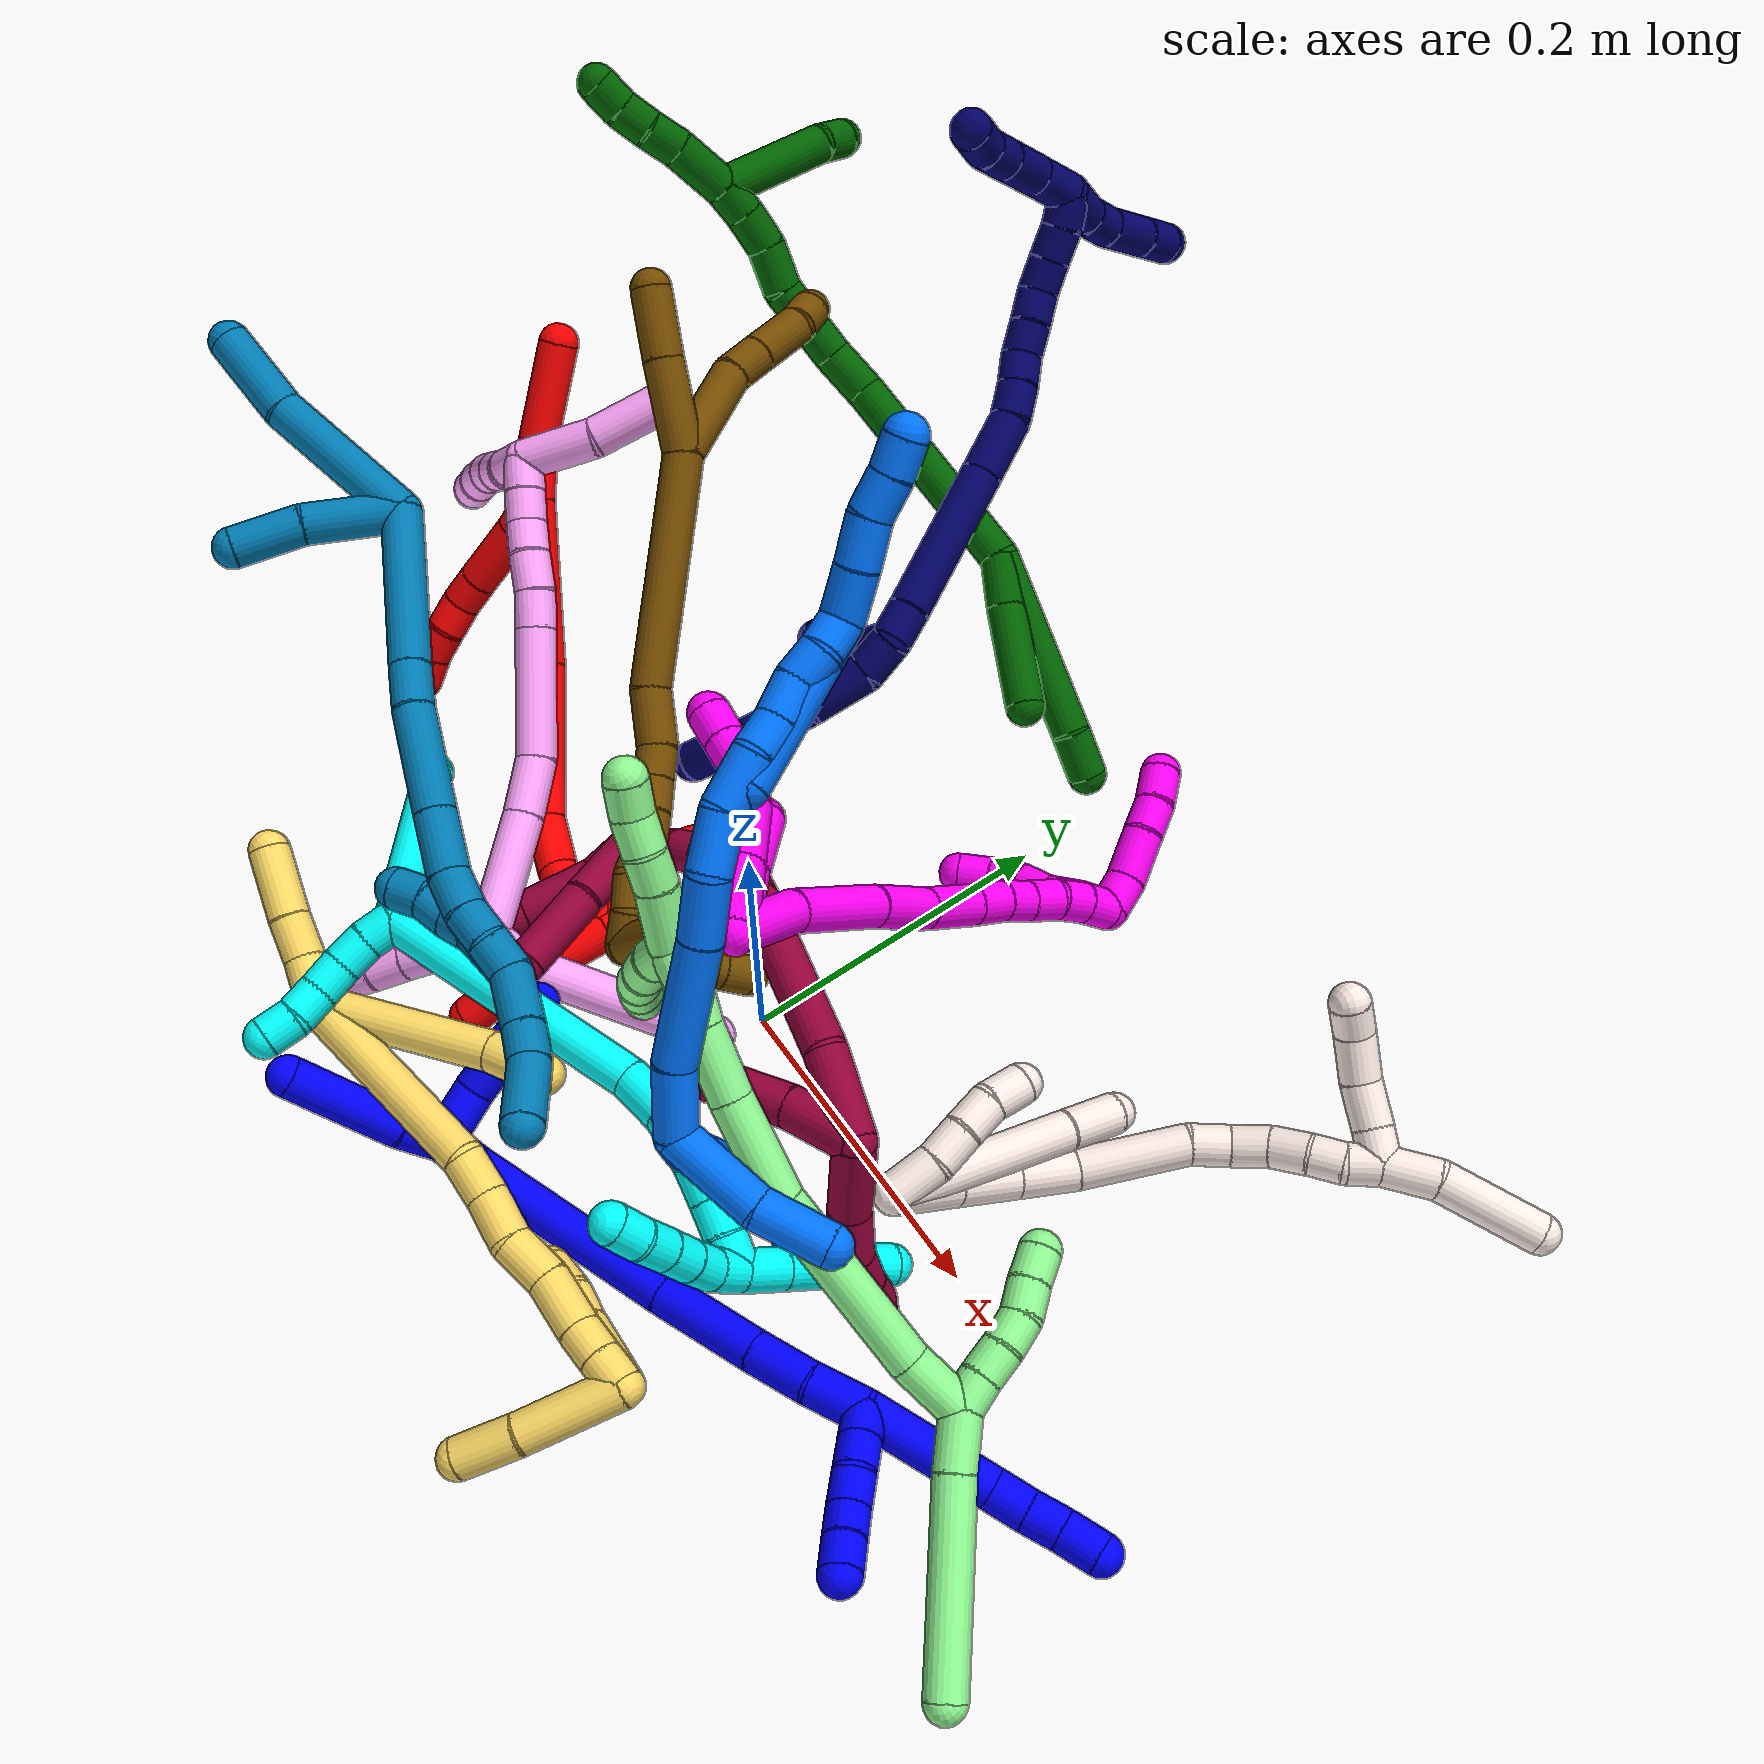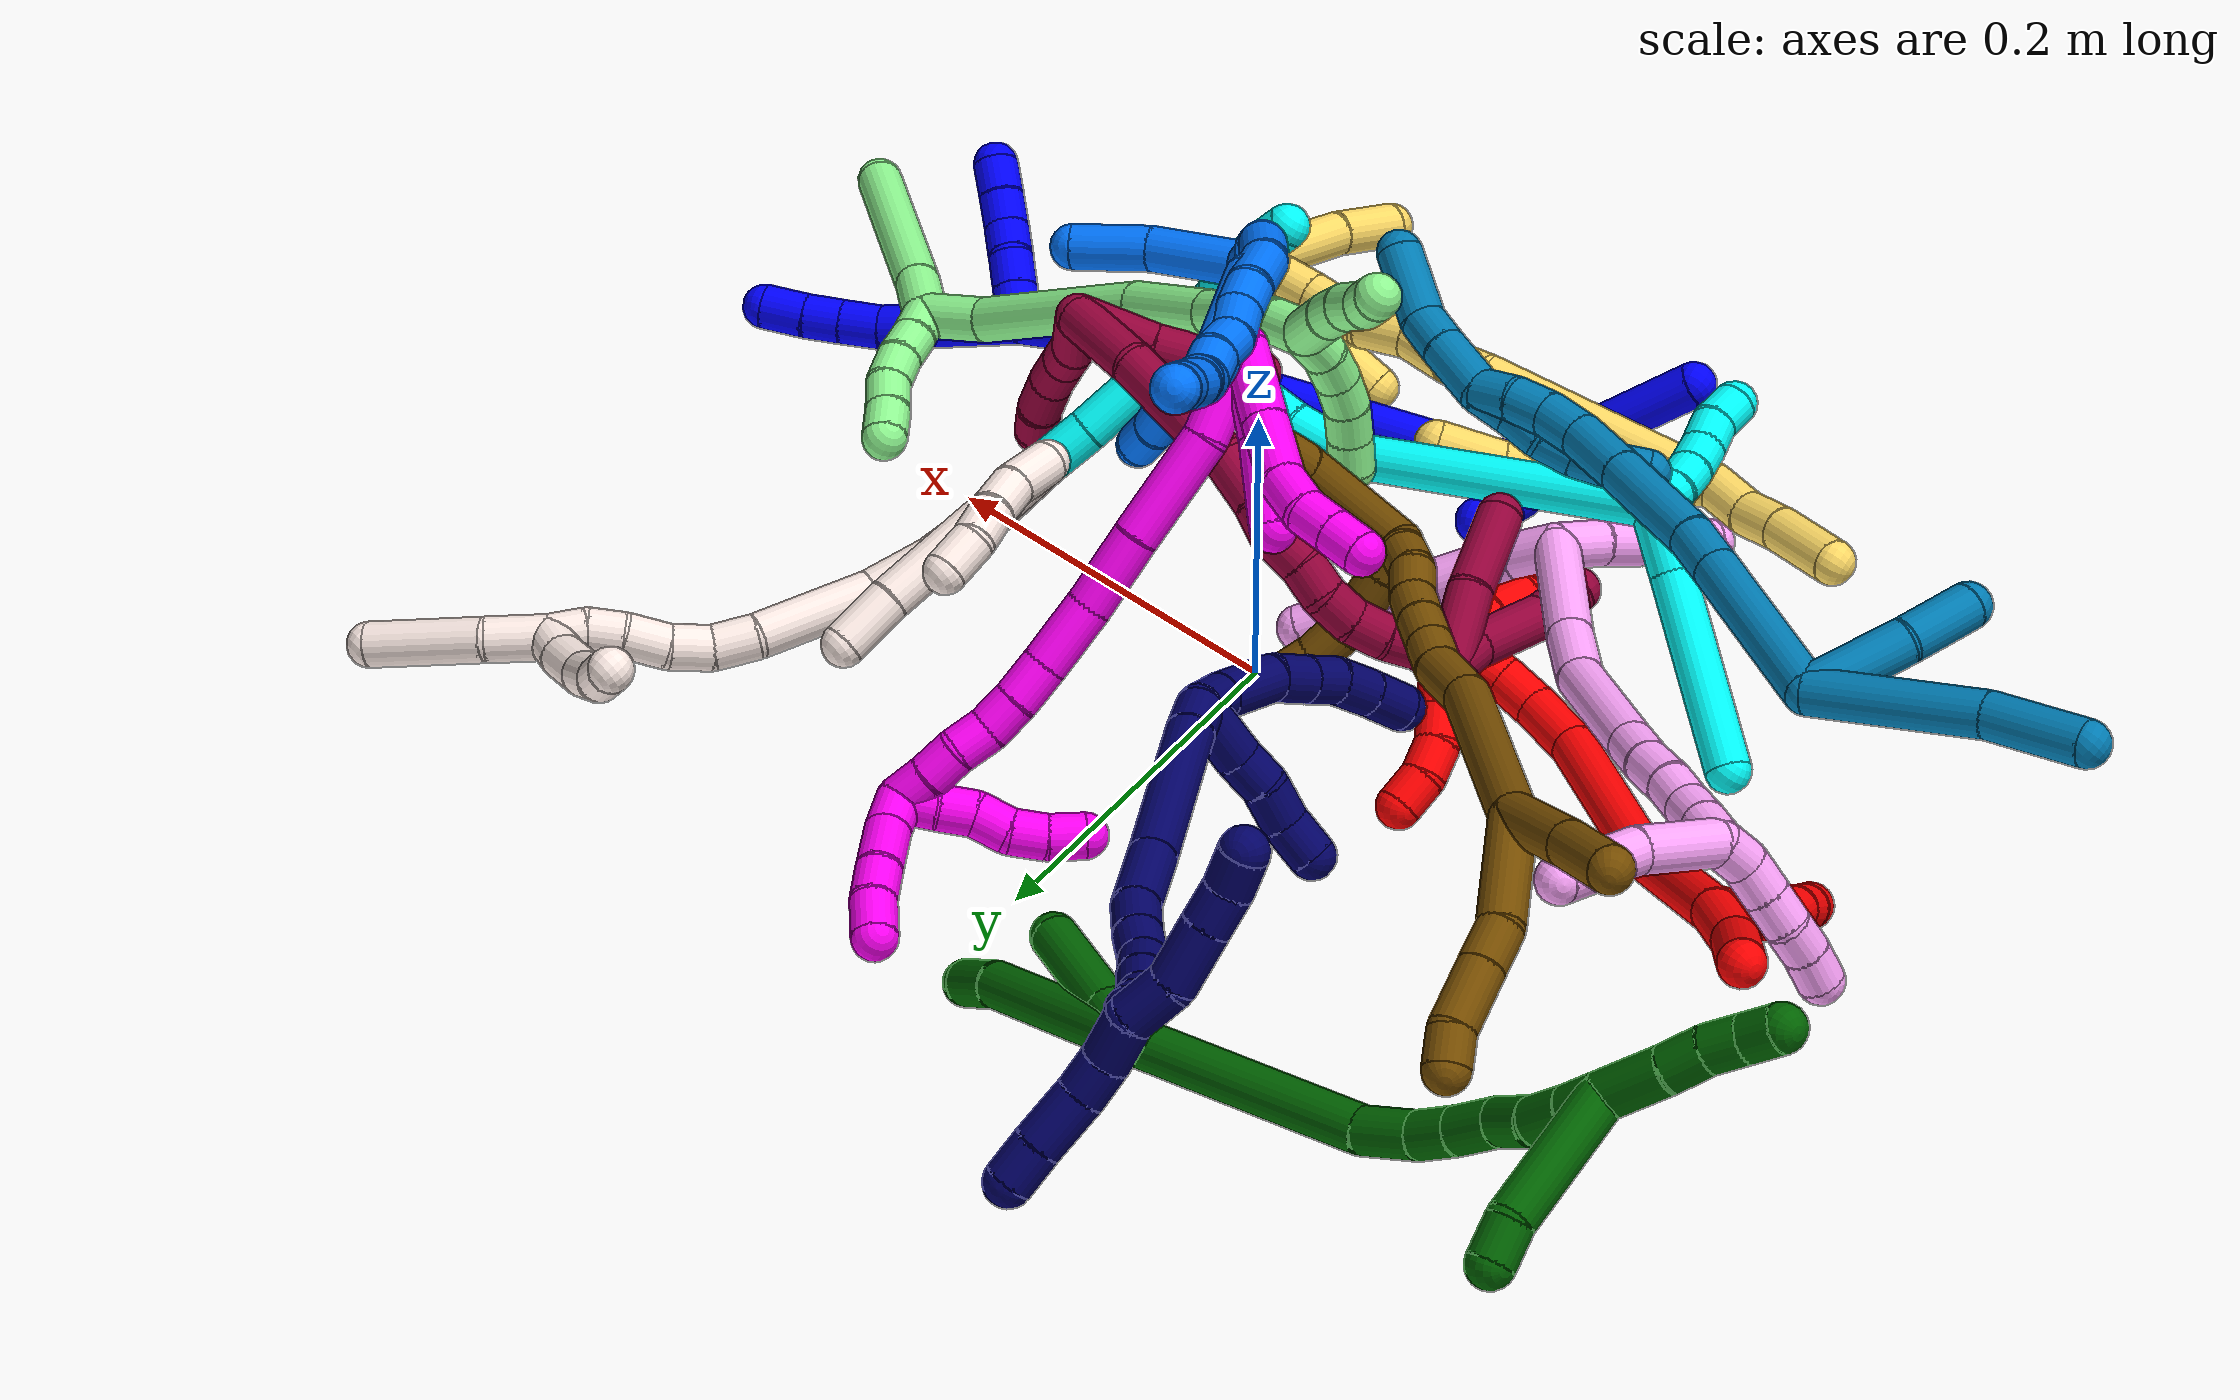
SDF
<sdf version="1.7">
 <world name="default">
  <plugin name="TubeGeneratorPlugin" filename="libtube_generator_plugin.so"/>
  <model name="photoneo_s_sensor">
   <static>1</static>
   <pose>0 0 2 1.57079 1.57079 3.14159</pose>
   <link name="link">
    <inertial><mass>0.1</mass></inertial>
    <sensor name="sensor" type="depth">
     <update_rate>30</update_rate>
     <camera>
      <horizontal_fov>1.22</horizontal_fov>
      <image><width>1920</width><height>1200</height><format>B8G8R8</format></image>
      <clip><near>0.1</near><far>4</far></clip>
      <depth_camera><output>points</output></depth_camera>
     </camera>
     <plugin name="camera_plugin" filename="libgazebo_ros_depth_camera.so">
      <baseline>0.2</baseline>
      <alwaysOn>1</alwaysOn>
      <updateRate>0.0</updateRate>
      <cameraName>camera_ir</cameraName>
      <imageTopicName>/camera/color/image_raw</imageTopicName>
      <cameraInfoTopicName>/camera/color/camera_info</cameraInfoTopicName>
      <depthImageTopicName>/camera/depth/image_raw</depthImageTopicName>
      <depthImageCameraInfoTopicName>/camera/depth/camera_info</depthImageCameraInfoTopicName>
      <pointCloudTopicName>/camera/depth/points</pointCloudTopicName>
      <frameName>fr_optical</frameName>
      <pointCloudCutoff>0.1</pointCloudCutoff>
      <pointCloudCutoffMax>2.0</pointCloudCutoffMax>
      <distortionK1>0</distortionK1>
      <distortionK2>0</distortionK2>
      <distortionK3>0</distortionK3>
      <distortionT1>0</distortionT1>
      <distortionT2>0</distortionT2>
      <CxPrime>0</CxPrime>
      <Cx>0</Cx>
      <Cy>0</Cy>
      <focalLength>0</focalLength>
      <hackBaseline>0</hackBaseline>
     </plugin>
    </sensor>
   </link>
  </model>
  <gravity>0 0 -9.8</gravity>
  <magnetic_field>6e-06 2.3e-05 -4.2e-05</magnetic_field>
  <atmosphere type="adiabatic"/>
  <physics name="default_physics" default="0" type="ode">
   <max_step_size>0.003</max_step_size>
   <real_time_factor>1</real_time_factor>
   <real_time_update_rate>1000</real_time_update_rate>
   <max_contacts>10000</max_contacts>
   <ode>
    <solver>
     <type>quick</type>
     <iters>100</iters>
     <sor>1.3</sor>
     <use_dynamic_moi_rescaling>0</use_dynamic_moi_rescaling>
    </solver>
    <constraints>
     <contact_max_correcting_vel>0</contact_max_correcting_vel>
     <contact_surface_layer>0.001</contact_surface_layer>
     <cfm>0</cfm>
     <erp>0.2</erp>
    </constraints>
   </ode>
  </physics>
  <scene><ambient>0.4 0.4 0.4 1</ambient><background>0.7 0.7 0.7 1</background><shadows>0</shadows></scene>
  <audio><device>default</device></audio>
  <spherical_coordinates>
   <surface_model>EARTH_WGS84</surface_model>
   <latitude_deg>0</latitude_deg>
   <longitude_deg>0</longitude_deg>
   <elevation>0</elevation>
   <heading_deg>0</heading_deg>
  </spherical_coordinates>
  <model name="bin">
   <static>1</static>
   <link name="bottom">
    <collision name="collision-bottom">
     <pose>0 0 -0.01 0 -0 0</pose>
     <geometry><box><size>0.8 0.6 0.02</size></box></geometry>
     <surface>
      <friction><ode><mu>100</mu><mu2>100</mu2></ode></friction>
      <contact><collide_bitmask>65535</collide_bitmask></contact>
     </surface>
    </collision>
   </link>
   <link name="west_wall">
    <collision name="collision-west_wall">
     <pose>-0.41 0 0.1 0 -0 0</pose>
     <geometry><box><size>0.02 0.6 0.2</size></box></geometry>
     <surface>
      <friction><ode><mu>100</mu><mu2>100</mu2></ode></friction>
      <contact><collide_bitmask>65535</collide_bitmask></contact>
     </surface>
    </collision>
   </link>
   <link name="east_wall">
    <collision name="collision-east_wall">
     <pose>0.41 0 0.1 0 -0 0</pose>
     <geometry><box><size>0.02 0.6 0.2</size></box></geometry>
     <surface>
      <friction><ode><mu>100</mu><mu2>100</mu2></ode></friction>
      <contact><collide_bitmask>65535</collide_bitmask></contact>
     </surface>
    </collision>
   </link>
   <link name="south_wall">
    <collision name="collision-south_wall">
     <pose>0 -0.31 0.1 0 -0 0</pose>
     <geometry><box><size>0.8 0.02 0.2</size></box></geometry>
     <surface>
      <friction><ode><mu>100</mu><mu2>100</mu2></ode></friction>
      <contact><collide_bitmask>65535</collide_bitmask></contact>
     </surface>
    </collision>
   </link>
   <link name="north_wall">
    <collision name="collision-north_wall">
     <pose>0 0.31 0.1 0 -0 0</pose>
     <geometry><box><size>0.8 0.02 0.2</size></box></geometry>
     <surface>
      <friction><ode><mu>100</mu><mu2>100</mu2></ode></friction>
      <contact><collide_bitmask>65535</collide_bitmask></contact>
     </surface>
    </collision>
   </link>
  </model>
  <model name="1">
   <static>0</static>
   <link name="1">
    <collision name="collision-cylinder-e_1_2_8">
     <pose>0.038566 0.002872 -0.012225 -2.91083 1.256 -2.82502</pose>
     <geometry><cylinder><radius>0.0125</radius><length>0.081119</length></cylinder></geometry>
     <surface>
      <friction><ode><mu>1.16</mu><mu2>1.16</mu2><slip1>0</slip1><slip2>0</slip2></ode></friction>
      <contact><ode><kp>1e+06</kp><kd>1</kd><max_vel>0</max_vel><min_depth>0.001</min_depth></ode></contact>
     </surface>
    </collision>
    <visual name="visual-cylinder-e_1_2_8">
     <pose>0.038566 0.002872 -0.012225 -2.91083 1.256 -2.82502</pose>
     <geometry><cylinder><radius>0.0125</radius><length>0.081119</length></cylinder></geometry>
     <material><ambient>0 0 1 1</ambient></material>
    </visual>
    <collision name="collision-cylinder-e_2_8_9">
     <pose>0.088056 0.008821 -0.027227 -2.30505 1.2082 -1.99724</pose>
     <geometry><cylinder><radius>0.0125</radius><length>0.023365</length></cylinder></geometry>
     <surface>
      <friction><ode><mu>1.16</mu><mu2>1.16</mu2><slip1>0</slip1><slip2>0</slip2></ode></friction>
      <contact><ode><kp>1e+06</kp><kd>1</kd><max_vel>0</max_vel><min_depth>0.001</min_depth></ode></contact>
     </surface>
    </collision>
    <visual name="visual-cylinder-e_2_8_9">
     <pose>0.088056 0.008821 -0.027227 -2.30505 1.2082 -1.99724</pose>
     <geometry><cylinder><radius>0.0125</radius><length>0.023365</length></cylinder></geometry>
     <material><ambient>0 0 1 1</ambient></material>
    </visual>
    <collision name="collision-cylinder-e_3_9_10">
     <pose>0.108628 0.01535 -0.032841 -2.25848 1.13703 -1.86763</pose>
     <geometry><cylinder><radius>0.0125</radius><length>0.021269</length></cylinder></geometry>
     <surface>
      <friction><ode><mu>1.16</mu><mu2>1.16</mu2><slip1>0</slip1><slip2>0</slip2></ode></friction>
      <contact><ode><kp>1e+06</kp><kd>1</kd><max_vel>0</max_vel><min_depth>0.001</min_depth></ode></contact>
     </surface>
    </collision>
    <visual name="visual-cylinder-e_3_9_10">
     <pose>0.108628 0.01535 -0.032841 -2.25848 1.13703 -1.86763</pose>
     <geometry><cylinder><radius>0.0125</radius><length>0.021269</length></cylinder></geometry>
     <material><ambient>0 0 1 1</ambient></material>
    </visual>
    <collision name="collision-cylinder-e_4_10_6">
     <pose>0.12939 0.022991 -0.038119 -2.09857 1.15953 -1.70118</pose>
     <geometry><cylinder><radius>0.0125</radius><length>0.024247</length></cylinder></geometry>
     <surface>
      <friction><ode><mu>1.16</mu><mu2>1.16</mu2><slip1>0</slip1><slip2>0</slip2></ode></friction>
      <contact><ode><kp>1e+06</kp><kd>1</kd><max_vel>0</max_vel><min_depth>0.001</min_depth></ode></contact>
     </surface>
    </collision>
    <visual name="visual-cylinder-e_4_10_6">
     <pose>0.12939 0.022991 -0.038119 -2.09857 1.15953 -1.70118</pose>
     <geometry><cylinder><radius>0.0125</radius><length>0.024247</length></cylinder></geometry>
     <material><ambient>0 0 1 1</ambient></material>
    </visual>
    <collision name="collision-cylinder-e_1_2_11">
     <pose>0.004496 0.004141 0.007915 -0.48203 0.466315 -0.116608</pose>
     <geometry><cylinder><radius>0.0125</radius><length>0.02</length></cylinder></geometry>
     <surface>
      <friction><ode><mu>1.16</mu><mu2>1.16</mu2><slip1>0</slip1><slip2>0</slip2></ode></friction>
      <contact><ode><kp>1e+06</kp><kd>1</kd><max_vel>0</max_vel><min_depth>0.001</min_depth></ode></contact>
     </surface>
    </collision>
    <visual name="visual-cylinder-e_1_2_11">
     <pose>0.004496 0.004141 0.007915 -0.48203 0.466315 -0.116608</pose>
     <geometry><cylinder><radius>0.0125</radius><length>0.02</length></cylinder></geometry>
     <material><ambient>0 0 1 1</ambient></material>
    </visual>
    <collision name="collision-cylinder-e_2_11_12">
     <pose>0.013501 0.012445 0.023724 -0.485265 0.467814 -0.11781</pose>
     <geometry><cylinder><radius>0.0125</radius><length>0.02</length></cylinder></geometry>
     <surface>
      <friction><ode><mu>1.16</mu><mu2>1.16</mu2><slip1>0</slip1><slip2>0</slip2></ode></friction>
      <contact><ode><kp>1e+06</kp><kd>1</kd><max_vel>0</max_vel><min_depth>0.001</min_depth></ode></contact>
     </surface>
    </collision>
    <visual name="visual-cylinder-e_2_11_12">
     <pose>0.013501 0.012445 0.023724 -0.485265 0.467814 -0.11781</pose>
     <geometry><cylinder><radius>0.0125</radius><length>0.02</length></cylinder></geometry>
     <material><ambient>0 0 1 1</ambient></material>
    </visual>
    <collision name="collision-cylinder-e_3_12_13">
     <pose>0.023566 0.01838 0.039744 -0.214751 0.588948 -0.06536</pose>
     <geometry><cylinder><radius>0.0125</radius><length>0.02</length></cylinder></geometry>
     <surface>
      <friction><ode><mu>1.16</mu><mu2>1.16</mu2><slip1>0</slip1><slip2>0</slip2></ode></friction>
      <contact><ode><kp>1e+06</kp><kd>1</kd><max_vel>0</max_vel><min_depth>0.001</min_depth></ode></contact>
     </surface>
    </collision>
    <visual name="visual-cylinder-e_3_12_13">
     <pose>0.023566 0.01838 0.039744 -0.214751 0.588948 -0.06536</pose>
     <geometry><cylinder><radius>0.0125</radius><length>0.02</length></cylinder></geometry>
     <material><ambient>0 0 1 1</ambient></material>
    </visual>
    <collision name="collision-cylinder-e_4_13_14">
     <pose>0.033601 0.024851 0.055473 -0.553454 0.464604 -0.134178</pose>
     <geometry><cylinder><radius>0.0125</radius><length>0.02</length></cylinder></geometry>
     <surface>
      <friction><ode><mu>1.16</mu><mu2>1.16</mu2><slip1>0</slip1><slip2>0</slip2></ode></friction>
      <contact><ode><kp>1e+06</kp><kd>1</kd><max_vel>0</max_vel><min_depth>0.001</min_depth></ode></contact>
     </surface>
    </collision>
    <visual name="visual-cylinder-e_4_13_14">
     <pose>0.033601 0.024851 0.055473 -0.553454 0.464604 -0.134178</pose>
     <geometry><cylinder><radius>0.0125</radius><length>0.02</length></cylinder></geometry>
     <material><ambient>0 0 1 1</ambient></material>
    </visual>
    <collision name="collision-cylinder-e_5_14_5">
     <pose>0.042974 0.033695 0.070752 -0.495225 0.511228 -0.131937</pose>
     <geometry><cylinder><radius>0.0125</radius><length>0.02</length></cylinder></geometry>
     <surface>
      <friction><ode><mu>1.16</mu><mu2>1.16</mu2><slip1>0</slip1><slip2>0</slip2></ode></friction>
      <contact><ode><kp>1e+06</kp><kd>1</kd><max_vel>0</max_vel><min_depth>0.001</min_depth></ode></contact>
     </surface>
    </collision>
    <visual name="visual-cylinder-e_5_14_5">
     <pose>0.042974 0.033695 0.070752 -0.495225 0.511228 -0.131937</pose>
     <geometry><cylinder><radius>0.0125</radius><length>0.02</length></cylinder></geometry>
     <material><ambient>0 0 1 1</ambient></material>
    </visual>
    <collision name="collision-cylinder-e_1_2_15">
     <pose>-0.014877 -0.005654 0.005049 0.84189 -1.09956 -0.535532</pose>
     <geometry><cylinder><radius>0.0125</radius><length>0.033394</length></cylinder></geometry>
     <surface>
      <friction><ode><mu>1.16</mu><mu2>1.16</mu2><slip1>0</slip1><slip2>0</slip2></ode></friction>
      <contact><ode><kp>1e+06</kp><kd>1</kd><max_vel>0</max_vel><min_depth>0.001</min_depth></ode></contact>
     </surface>
    </collision>
    <visual name="visual-cylinder-e_1_2_15">
     <pose>-0.014877 -0.005654 0.005049 0.84189 -1.09956 -0.535532</pose>
     <geometry><cylinder><radius>0.0125</radius><length>0.033394</length></cylinder></geometry>
     <material><ambient>0 0 1 1</ambient></material>
    </visual>
    <collision name="collision-cylinder-e_2_15_16">
     <pose>-0.045856 -0.020076 0.013594 1.1914 -1.04058 -0.740881</pose>
     <geometry><cylinder><radius>0.0125</radius><length>0.03733</length></cylinder></geometry>
     <surface>
      <friction><ode><mu>1.16</mu><mu2>1.16</mu2><slip1>0</slip1><slip2>0</slip2></ode></friction>
      <contact><ode><kp>1e+06</kp><kd>1</kd><max_vel>0</max_vel><min_depth>0.001</min_depth></ode></contact>
     </surface>
    </collision>
    <visual name="visual-cylinder-e_2_15_16">
     <pose>-0.045856 -0.020076 0.013594 1.1914 -1.04058 -0.740881</pose>
     <geometry><cylinder><radius>0.0125</radius><length>0.03733</length></cylinder></geometry>
     <material><ambient>0 0 1 1</ambient></material>
    </visual>
    <collision name="collision-cylinder-e_3_16_17">
     <pose>-0.090257 -0.043986 0.022244 1.2427 -1.05634 -0.791394</pose>
     <geometry><cylinder><radius>0.0125</radius><length>0.065013</length></cylinder></geometry>
     <surface>
      <friction><ode><mu>1.16</mu><mu2>1.16</mu2><slip1>0</slip1><slip2>0</slip2></ode></friction>
      <contact><ode><kp>1e+06</kp><kd>1</kd><max_vel>0</max_vel><min_depth>0.001</min_depth></ode></contact>
     </surface>
    </collision>
    <visual name="visual-cylinder-e_3_16_17">
     <pose>-0.090257 -0.043986 0.022244 1.2427 -1.05634 -0.791394</pose>
     <geometry><cylinder><radius>0.0125</radius><length>0.065013</length></cylinder></geometry>
     <material><ambient>0 0 1 1</ambient></material>
    </visual>
    <collision name="collision-cylinder-e_4_17_18">
     <pose>-0.181755 -0.086184 0.038152 1.19248 -1.13909 -0.819856</pose>
     <geometry><cylinder><radius>0.0125</radius><length>0.139166</length></cylinder></geometry>
     <surface>
      <friction><ode><mu>1.16</mu><mu2>1.16</mu2><slip1>0</slip1><slip2>0</slip2></ode></friction>
      <contact><ode><kp>1e+06</kp><kd>1</kd><max_vel>0</max_vel><min_depth>0.001</min_depth></ode></contact>
     </surface>
    </collision>
    <visual name="visual-cylinder-e_4_17_18">
     <pose>-0.181755 -0.086184 0.038152 1.19248 -1.13909 -0.819856</pose>
     <geometry><cylinder><radius>0.0125</radius><length>0.139166</length></cylinder></geometry>
     <material><ambient>0 0 1 1</ambient></material>
    </visual>
    <collision name="collision-cylinder-e_5_18_1">
     <pose>-0.25722 -0.114267 0.05135 0.397817 -1.35792 -0.322492</pose>
     <geometry><cylinder><radius>0.0125</radius><length>0.025098</length></cylinder></geometry>
     <surface>
      <friction><ode><mu>1.16</mu><mu2>1.16</mu2><slip1>0</slip1><slip2>0</slip2></ode></friction>
      <contact><ode><kp>1e+06</kp><kd>1</kd><max_vel>0</max_vel><min_depth>0.001</min_depth></ode></contact>
     </surface>
    </collision>
    <visual name="visual-cylinder-e_5_18_1">
     <pose>-0.25722 -0.114267 0.05135 0.397817 -1.35792 -0.322492</pose>
     <geometry><cylinder><radius>0.0125</radius><length>0.025098</length></cylinder></geometry>
     <material><ambient>0 0 1 1</ambient></material>
    </visual>
    <collision name="collision-cylinder-e_1_1_19">
     <pose>-0.280321 -0.111412 0.062035 -0.440173 -0.87172 0.207629</pose>
     <geometry><cylinder><radius>0.0125</radius><length>0.028312</length></cylinder></geometry>
     <surface>
      <friction><ode><mu>1.16</mu><mu2>1.16</mu2><slip1>0</slip1><slip2>0</slip2></ode></friction>
      <contact><ode><kp>1e+06</kp><kd>1</kd><max_vel>0</max_vel><min_depth>0.001</min_depth></ode></contact>
     </surface>
    </collision>
    <visual name="visual-cylinder-e_1_1_19">
     <pose>-0.280321 -0.111412 0.062035 -0.440173 -0.87172 0.207629</pose>
     <geometry><cylinder><radius>0.0125</radius><length>0.028312</length></cylinder></geometry>
     <material><ambient>0 0 1 1</ambient></material>
    </visual>
    <collision name="collision-cylinder-e_2_19_4">
     <pose>-0.321304 -0.098415 0.087388 -0.4895 -0.999278 0.270981</pose>
     <geometry><cylinder><radius>0.0125</radius><length>0.071688</length></cylinder></geometry>
     <surface>
      <friction><ode><mu>1.16</mu><mu2>1.16</mu2><slip1>0</slip1><slip2>0</slip2></ode></friction>
      <contact><ode><kp>1e+06</kp><kd>1</kd><max_vel>0</max_vel><min_depth>0.001</min_depth></ode></contact>
     </surface>
    </collision>
    <visual name="visual-cylinder-e_2_19_4">
     <pose>-0.321304 -0.098415 0.087388 -0.4895 -0.999278 0.270981</pose>
     <geometry><cylinder><radius>0.0125</radius><length>0.071688</length></cylinder></geometry>
     <material><ambient>0 0 1 1</ambient></material>
    </visual>
    <collision name="collision-cylinder-e_1_1_20">
     <pose>-0.274915 -0.110162 0.03788 -2.82964 -0.31398 1.57737</pose>
     <geometry><cylinder><radius>0.0125</radius><length>0.035161</length></cylinder></geometry>
     <surface>
      <friction><ode><mu>1.16</mu><mu2>1.16</mu2><slip1>0</slip1><slip2>0</slip2></ode></friction>
      <contact><ode><kp>1e+06</kp><kd>1</kd><max_vel>0</max_vel><min_depth>0.001</min_depth></ode></contact>
     </surface>
    </collision>
    <visual name="visual-cylinder-e_1_1_20">
     <pose>-0.274915 -0.110162 0.03788 -2.82964 -0.31398 1.57737</pose>
     <geometry><cylinder><radius>0.0125</radius><length>0.035161</length></cylinder></geometry>
     <material><ambient>0 0 1 1</ambient></material>
    </visual>
    <collision name="collision-cylinder-e_2_20_3">
     <pose>-0.286791 -0.086485 -0.003832 -2.51833 -0.200161 0.60436</pose>
     <geometry><cylinder><radius>0.0125</radius><length>0.064839</length></cylinder></geometry>
     <surface>
      <friction><ode><mu>1.16</mu><mu2>1.16</mu2><slip1>0</slip1><slip2>0</slip2></ode></friction>
      <contact><ode><kp>1e+06</kp><kd>1</kd><max_vel>0</max_vel><min_depth>0.001</min_depth></ode></contact>
     </surface>
    </collision>
    <visual name="visual-cylinder-e_2_20_3">
     <pose>-0.286791 -0.086485 -0.003832 -2.51833 -0.200161 0.60436</pose>
     <geometry><cylinder><radius>0.0125</radius><length>0.064839</length></cylinder></geometry>
     <material><ambient>0 0 1 1</ambient></material>
    </visual>
    <collision name="collision-sphere-3">
     <pose>-0.293237 -0.067939 -0.02963 0 -0 0</pose>
     <geometry><sphere><radius>0.0125</radius></sphere></geometry>
     <surface>
      <friction><ode><mu>1.16</mu><mu2>1.16</mu2><slip1>0</slip1><slip2>0</slip2></ode></friction>
      <contact><ode><kp>1e+06</kp><kd>1</kd><max_vel>0</max_vel><min_depth>0.001</min_depth></ode></contact>
     </surface>
    </collision>
    <visual name="visual-sphere-3">
     <pose>-0.293237 -0.067939 -0.02963 0 -0 0</pose>
     <geometry><sphere><radius>0.0125</radius></sphere></geometry>
     <material><ambient>0 0 1 1</ambient></material>
    </visual>
    <collision name="collision-sphere-20">
     <pose>-0.280345 -0.10503 0.021967 0 -0 0</pose>
     <geometry><sphere><radius>0.0125</radius></sphere></geometry>
     <surface>
      <friction><ode><mu>1.16</mu><mu2>1.16</mu2><slip1>0</slip1><slip2>0</slip2></ode></friction>
      <contact><ode><kp>1e+06</kp><kd>1</kd><max_vel>0</max_vel><min_depth>0.001</min_depth></ode></contact>
     </surface>
    </collision>
    <visual name="visual-sphere-20">
     <pose>-0.280345 -0.10503 0.021967 0 -0 0</pose>
     <geometry><sphere><radius>0.0125</radius></sphere></geometry>
     <material><ambient>0 0 1 1</ambient></material>
    </visual>
    <collision name="collision-sphere-4">
     <pose>-0.351452 -0.089298 0.1045 0 -0 0</pose>
     <geometry><sphere><radius>0.0125</radius></sphere></geometry>
     <surface>
      <friction><ode><mu>1.16</mu><mu2>1.16</mu2><slip1>0</slip1><slip2>0</slip2></ode></friction>
      <contact><ode><kp>1e+06</kp><kd>1</kd><max_vel>0</max_vel><min_depth>0.001</min_depth></ode></contact>
     </surface>
    </collision>
    <visual name="visual-sphere-4">
     <pose>-0.351452 -0.089298 0.1045 0 -0 0</pose>
     <geometry><sphere><radius>0.0125</radius></sphere></geometry>
     <material><ambient>0 0 1 1</ambient></material>
    </visual>
    <collision name="collision-sphere-11">
     <pose>0.008992 0.008282 0.015829 0 -0 0</pose>
     <geometry><sphere><radius>0.0125</radius></sphere></geometry>
     <surface>
      <friction><ode><mu>1.16</mu><mu2>1.16</mu2><slip1>0</slip1><slip2>0</slip2></ode></friction>
      <contact><ode><kp>1e+06</kp><kd>1</kd><max_vel>0</max_vel><min_depth>0.001</min_depth></ode></contact>
     </surface>
    </collision>
    <visual name="visual-sphere-11">
     <pose>0.008992 0.008282 0.015829 0 -0 0</pose>
     <geometry><sphere><radius>0.0125</radius></sphere></geometry>
     <material><ambient>0 0 1 1</ambient></material>
    </visual>
    <collision name="collision-sphere-6">
     <pose>0.140503 0.027178 -0.040559 0 -0 0</pose>
     <geometry><sphere><radius>0.0125</radius></sphere></geometry>
     <surface>
      <friction><ode><mu>1.16</mu><mu2>1.16</mu2><slip1>0</slip1><slip2>0</slip2></ode></friction>
      <contact><ode><kp>1e+06</kp><kd>1</kd><max_vel>0</max_vel><min_depth>0.001</min_depth></ode></contact>
     </surface>
    </collision>
    <visual name="visual-sphere-6">
     <pose>0.140503 0.027178 -0.040559 0 -0 0</pose>
     <geometry><sphere><radius>0.0125</radius></sphere></geometry>
     <material><ambient>0 0 1 1</ambient></material>
    </visual>
    <collision name="collision-sphere-10">
     <pose>0.118278 0.018804 -0.035678 0 -0 0</pose>
     <geometry><sphere><radius>0.0125</radius></sphere></geometry>
     <surface>
      <friction><ode><mu>1.16</mu><mu2>1.16</mu2><slip1>0</slip1><slip2>0</slip2></ode></friction>
      <contact><ode><kp>1e+06</kp><kd>1</kd><max_vel>0</max_vel><min_depth>0.001</min_depth></ode></contact>
     </surface>
    </collision>
    <visual name="visual-sphere-10">
     <pose>0.118278 0.018804 -0.035678 0 -0 0</pose>
     <geometry><sphere><radius>0.0125</radius></sphere></geometry>
     <material><ambient>0 0 1 1</ambient></material>
    </visual>
    <collision name="collision-sphere-9">
     <pose>0.098978 0.011897 -0.030004 0 -0 0</pose>
     <geometry><sphere><radius>0.0125</radius></sphere></geometry>
     <surface>
      <friction><ode><mu>1.16</mu><mu2>1.16</mu2><slip1>0</slip1><slip2>0</slip2></ode></friction>
      <contact><ode><kp>1e+06</kp><kd>1</kd><max_vel>0</max_vel><min_depth>0.001</min_depth></ode></contact>
     </surface>
    </collision>
    <visual name="visual-sphere-9">
     <pose>0.098978 0.011897 -0.030004 0 -0 0</pose>
     <geometry><sphere><radius>0.0125</radius></sphere></geometry>
     <material><ambient>0 0 1 1</ambient></material>
    </visual>
    <collision name="collision-sphere-2">
     <geometry><sphere><radius>0.0125</radius></sphere></geometry>
     <surface>
      <friction><ode><mu>1.16</mu><mu2>1.16</mu2><slip1>0</slip1><slip2>0</slip2></ode></friction>
      <contact><ode><kp>1e+06</kp><kd>1</kd><max_vel>0</max_vel><min_depth>0.001</min_depth></ode></contact>
     </surface>
    </collision>
    <visual name="visual-sphere-2">
     <geometry><sphere><radius>0.0125</radius></sphere></geometry>
     <material><ambient>0 0 1 1</ambient></material>
    </visual>
    <collision name="collision-sphere-19">
     <pose>-0.291157 -0.107531 0.070277 0 -0 0</pose>
     <geometry><sphere><radius>0.0125</radius></sphere></geometry>
     <surface>
      <friction><ode><mu>1.16</mu><mu2>1.16</mu2><slip1>0</slip1><slip2>0</slip2></ode></friction>
      <contact><ode><kp>1e+06</kp><kd>1</kd><max_vel>0</max_vel><min_depth>0.001</min_depth></ode></contact>
     </surface>
    </collision>
    <visual name="visual-sphere-19">
     <pose>-0.291157 -0.107531 0.070277 0 -0 0</pose>
     <geometry><sphere><radius>0.0125</radius></sphere></geometry>
     <material><ambient>0 0 1 1</ambient></material>
    </visual>
    <collision name="collision-sphere-8">
     <pose>0.077133 0.005745 -0.024451 0 -0 0</pose>
     <geometry><sphere><radius>0.0125</radius></sphere></geometry>
     <surface>
      <friction><ode><mu>1.16</mu><mu2>1.16</mu2><slip1>0</slip1><slip2>0</slip2></ode></friction>
      <contact><ode><kp>1e+06</kp><kd>1</kd><max_vel>0</max_vel><min_depth>0.001</min_depth></ode></contact>
     </surface>
    </collision>
    <visual name="visual-sphere-8">
     <pose>0.077133 0.005745 -0.024451 0 -0 0</pose>
     <geometry><sphere><radius>0.0125</radius></sphere></geometry>
     <material><ambient>0 0 1 1</ambient></material>
    </visual>
    <collision name="collision-sphere-12">
     <pose>0.018011 0.016608 0.031619 0 -0 0</pose>
     <geometry><sphere><radius>0.0125</radius></sphere></geometry>
     <surface>
      <friction><ode><mu>1.16</mu><mu2>1.16</mu2><slip1>0</slip1><slip2>0</slip2></ode></friction>
      <contact><ode><kp>1e+06</kp><kd>1</kd><max_vel>0</max_vel><min_depth>0.001</min_depth></ode></contact>
     </surface>
    </collision>
    <visual name="visual-sphere-12">
     <pose>0.018011 0.016608 0.031619 0 -0 0</pose>
     <geometry><sphere><radius>0.0125</radius></sphere></geometry>
     <material><ambient>0 0 1 1</ambient></material>
    </visual>
    <collision name="collision-sphere-13">
     <pose>0.02912 0.020152 0.047868 0 -0 0</pose>
     <geometry><sphere><radius>0.0125</radius></sphere></geometry>
     <surface>
      <friction><ode><mu>1.16</mu><mu2>1.16</mu2><slip1>0</slip1><slip2>0</slip2></ode></friction>
      <contact><ode><kp>1e+06</kp><kd>1</kd><max_vel>0</max_vel><min_depth>0.001</min_depth></ode></contact>
     </surface>
    </collision>
    <visual name="visual-sphere-13">
     <pose>0.02912 0.020152 0.047868 0 -0 0</pose>
     <geometry><sphere><radius>0.0125</radius></sphere></geometry>
     <material><ambient>0 0 1 1</ambient></material>
    </visual>
    <collision name="collision-sphere-14">
     <pose>0.038082 0.02955 0.063079 0 -0 0</pose>
     <geometry><sphere><radius>0.0125</radius></sphere></geometry>
     <surface>
      <friction><ode><mu>1.16</mu><mu2>1.16</mu2><slip1>0</slip1><slip2>0</slip2></ode></friction>
      <contact><ode><kp>1e+06</kp><kd>1</kd><max_vel>0</max_vel><min_depth>0.001</min_depth></ode></contact>
     </surface>
    </collision>
    <visual name="visual-sphere-14">
     <pose>0.038082 0.02955 0.063079 0 -0 0</pose>
     <geometry><sphere><radius>0.0125</radius></sphere></geometry>
     <material><ambient>0 0 1 1</ambient></material>
    </visual>
    <collision name="collision-sphere-5">
     <pose>0.047867 0.03784 0.078426 0 -0 0</pose>
     <geometry><sphere><radius>0.0125</radius></sphere></geometry>
     <surface>
      <friction><ode><mu>1.16</mu><mu2>1.16</mu2><slip1>0</slip1><slip2>0</slip2></ode></friction>
      <contact><ode><kp>1e+06</kp><kd>1</kd><max_vel>0</max_vel><min_depth>0.001</min_depth></ode></contact>
     </surface>
    </collision>
    <visual name="visual-sphere-5">
     <pose>0.047867 0.03784 0.078426 0 -0 0</pose>
     <geometry><sphere><radius>0.0125</radius></sphere></geometry>
     <material><ambient>0 0 1 1</ambient></material>
    </visual>
    <collision name="collision-sphere-15">
     <pose>-0.029754 -0.011308 0.010098 0 -0 0</pose>
     <geometry><sphere><radius>0.0125</radius></sphere></geometry>
     <surface>
      <friction><ode><mu>1.16</mu><mu2>1.16</mu2><slip1>0</slip1><slip2>0</slip2></ode></friction>
      <contact><ode><kp>1e+06</kp><kd>1</kd><max_vel>0</max_vel><min_depth>0.001</min_depth></ode></contact>
     </surface>
    </collision>
    <visual name="visual-sphere-15">
     <pose>-0.029754 -0.011308 0.010098 0 -0 0</pose>
     <geometry><sphere><radius>0.0125</radius></sphere></geometry>
     <material><ambient>0 0 1 1</ambient></material>
    </visual>
    <collision name="collision-sphere-16">
     <pose>-0.061958 -0.028844 0.017089 0 -0 0</pose>
     <geometry><sphere><radius>0.0125</radius></sphere></geometry>
     <surface>
      <friction><ode><mu>1.16</mu><mu2>1.16</mu2><slip1>0</slip1><slip2>0</slip2></ode></friction>
      <contact><ode><kp>1e+06</kp><kd>1</kd><max_vel>0</max_vel><min_depth>0.001</min_depth></ode></contact>
     </surface>
    </collision>
    <visual name="visual-sphere-16">
     <pose>-0.061958 -0.028844 0.017089 0 -0 0</pose>
     <geometry><sphere><radius>0.0125</radius></sphere></geometry>
     <material><ambient>0 0 1 1</ambient></material>
    </visual>
    <collision name="collision-sphere-17">
     <pose>-0.118556 -0.059128 0.027398 0 -0 0</pose>
     <geometry><sphere><radius>0.0125</radius></sphere></geometry>
     <surface>
      <friction><ode><mu>1.16</mu><mu2>1.16</mu2><slip1>0</slip1><slip2>0</slip2></ode></friction>
      <contact><ode><kp>1e+06</kp><kd>1</kd><max_vel>0</max_vel><min_depth>0.001</min_depth></ode></contact>
     </surface>
    </collision>
    <visual name="visual-sphere-17">
     <pose>-0.118556 -0.059128 0.027398 0 -0 0</pose>
     <geometry><sphere><radius>0.0125</radius></sphere></geometry>
     <material><ambient>0 0 1 1</ambient></material>
    </visual>
    <collision name="collision-sphere-18">
     <pose>-0.244954 -0.11324 0.048906 0 -0 0</pose>
     <geometry><sphere><radius>0.0125</radius></sphere></geometry>
     <surface>
      <friction><ode><mu>1.16</mu><mu2>1.16</mu2><slip1>0</slip1><slip2>0</slip2></ode></friction>
      <contact><ode><kp>1e+06</kp><kd>1</kd><max_vel>0</max_vel><min_depth>0.001</min_depth></ode></contact>
     </surface>
    </collision>
    <visual name="visual-sphere-18">
     <pose>-0.244954 -0.11324 0.048906 0 -0 0</pose>
     <geometry><sphere><radius>0.0125</radius></sphere></geometry>
     <material><ambient>0 0 1 1</ambient></material>
    </visual>
    <collision name="collision-sphere-1">
     <pose>-0.269485 -0.115294 0.053794 0 -0 0</pose>
     <geometry><sphere><radius>0.0125</radius></sphere></geometry>
     <surface>
      <friction><ode><mu>1.16</mu><mu2>1.16</mu2><slip1>0</slip1><slip2>0</slip2></ode></friction>
      <contact><ode><kp>1e+06</kp><kd>1</kd><max_vel>0</max_vel><min_depth>0.001</min_depth></ode></contact>
     </surface>
    </collision>
    <visual name="visual-sphere-1">
     <pose>-0.269485 -0.115294 0.053794 0 -0 0</pose>
     <geometry><sphere><radius>0.0125</radius></sphere></geometry>
     <material><ambient>0 0 1 1</ambient></material>
    </visual>
    <inertial>
     <pose>-0.114749 -0.046876 0.024702 0 -0 0</pose>
     <mass>0.75</mass>
     <inertia><ixx>3e-05</ixx><ixy>0</ixy><ixz>0</ixz><iyy>0.000247</iyy><iyz>0</iyz><izz>0.000302</izz></inertia>
    </inertial>
   </link>
   <pose>0.241534 -0.093639 0.035276 1.46787 0.327839 0.146367</pose>
  </model>
  <model name="2">
   <static>0</static>
   <link name="2">
    <collision name="collision-cylinder-e_1_2_8">
     <pose>0.001656 -0.010536 -0.005905 2.08162 0.136253 0.231869</pose>
     <geometry><cylinder><radius>0.0125</radius><length>0.024382</length></cylinder></geometry>
     <surface>
      <friction><ode><mu>1.16</mu><mu2>1.16</mu2><slip1>0</slip1><slip2>0</slip2></ode></friction>
      <contact><ode><kp>1e+06</kp><kd>1</kd><max_vel>0</max_vel><min_depth>0.001</min_depth></ode></contact>
     </surface>
    </collision>
    <visual name="visual-cylinder-e_1_2_8">
     <pose>0.001656 -0.010536 -0.005905 2.08162 0.136253 0.231869</pose>
     <geometry><cylinder><radius>0.0125</radius><length>0.024382</length></cylinder></geometry>
     <material><ambient>1 0 0 1</ambient></material>
    </visual>
    <collision name="collision-cylinder-e_2_8_9">
     <pose>0.006624 -0.041015 -0.021019 2.0034 0.149649 0.233312</pose>
     <geometry><cylinder><radius>0.0125</radius><length>0.044429</length></cylinder></geometry>
     <surface>
      <friction><ode><mu>1.16</mu><mu2>1.16</mu2><slip1>0</slip1><slip2>0</slip2></ode></friction>
      <contact><ode><kp>1e+06</kp><kd>1</kd><max_vel>0</max_vel><min_depth>0.001</min_depth></ode></contact>
     </surface>
    </collision>
    <visual name="visual-cylinder-e_2_8_9">
     <pose>0.006624 -0.041015 -0.021019 2.0034 0.149649 0.233312</pose>
     <geometry><cylinder><radius>0.0125</radius><length>0.044429</length></cylinder></geometry>
     <material><ambient>1 0 0 1</ambient></material>
    </visual>
    <collision name="collision-cylinder-e_3_9_10">
     <pose>0.011765 -0.069975 -0.03479 2.03914 0.17907 0.289998</pose>
     <geometry><cylinder><radius>0.0125</radius><length>0.020541</length></cylinder></geometry>
     <surface>
      <friction><ode><mu>1.16</mu><mu2>1.16</mu2><slip1>0</slip1><slip2>0</slip2></ode></friction>
      <contact><ode><kp>1e+06</kp><kd>1</kd><max_vel>0</max_vel><min_depth>0.001</min_depth></ode></contact>
     </surface>
    </collision>
    <visual name="visual-cylinder-e_3_9_10">
     <pose>0.011765 -0.069975 -0.03479 2.03914 0.17907 0.289998</pose>
     <geometry><cylinder><radius>0.0125</radius><length>0.020541</length></cylinder></geometry>
     <material><ambient>1 0 0 1</ambient></material>
    </visual>
    <collision name="collision-cylinder-e_4_10_11">
     <pose>0.016655 -0.086394 -0.045673 2.27767 0.30469 0.642986</pose>
     <geometry><cylinder><radius>0.0125</radius><length>0.020405</length></cylinder></geometry>
     <surface>
      <friction><ode><mu>1.16</mu><mu2>1.16</mu2><slip1>0</slip1><slip2>0</slip2></ode></friction>
      <contact><ode><kp>1e+06</kp><kd>1</kd><max_vel>0</max_vel><min_depth>0.001</min_depth></ode></contact>
     </surface>
    </collision>
    <visual name="visual-cylinder-e_4_10_11">
     <pose>0.016655 -0.086394 -0.045673 2.27767 0.30469 0.642986</pose>
     <geometry><cylinder><radius>0.0125</radius><length>0.020405</length></cylinder></geometry>
     <material><ambient>1 0 0 1</ambient></material>
    </visual>
    <collision name="collision-cylinder-e_5_11_12">
     <pose>0.021351 -0.101961 -0.057605 2.17284 0.163513 0.308964</pose>
     <geometry><cylinder><radius>0.0125</radius><length>0.020086</length></cylinder></geometry>
     <surface>
      <friction><ode><mu>1.16</mu><mu2>1.16</mu2><slip1>0</slip1><slip2>0</slip2></ode></friction>
      <contact><ode><kp>1e+06</kp><kd>1</kd><max_vel>0</max_vel><min_depth>0.001</min_depth></ode></contact>
     </surface>
    </collision>
    <visual name="visual-cylinder-e_5_11_12">
     <pose>0.021351 -0.101961 -0.057605 2.17284 0.163513 0.308964</pose>
     <geometry><cylinder><radius>0.0125</radius><length>0.020086</length></cylinder></geometry>
     <material><ambient>1 0 0 1</ambient></material>
    </visual>
    <collision name="collision-cylinder-e_6_12_6">
     <pose>0.023873 -0.117551 -0.069977 2.3095 0.088183 0.199053</pose>
     <geometry><cylinder><radius>0.0125</radius><length>0.020158</length></cylinder></geometry>
     <surface>
      <friction><ode><mu>1.16</mu><mu2>1.16</mu2><slip1>0</slip1><slip2>0</slip2></ode></friction>
      <contact><ode><kp>1e+06</kp><kd>1</kd><max_vel>0</max_vel><min_depth>0.001</min_depth></ode></contact>
     </surface>
    </collision>
    <visual name="visual-cylinder-e_6_12_6">
     <pose>0.023873 -0.117551 -0.069977 2.3095 0.088183 0.199053</pose>
     <geometry><cylinder><radius>0.0125</radius><length>0.020158</length></cylinder></geometry>
     <material><ambient>1 0 0 1</ambient></material>
    </visual>
    <collision name="collision-cylinder-e_1_2_13">
     <pose>-0.003315 0.005353 0.017767 -0.292651 -0.176776 0.02612</pose>
     <geometry><cylinder><radius>0.0125</radius><length>0.037699</length></cylinder></geometry>
     <surface>
      <friction><ode><mu>1.16</mu><mu2>1.16</mu2><slip1>0</slip1><slip2>0</slip2></ode></friction>
      <contact><ode><kp>1e+06</kp><kd>1</kd><max_vel>0</max_vel><min_depth>0.001</min_depth></ode></contact>
     </surface>
    </collision>
    <visual name="visual-cylinder-e_1_2_13">
     <pose>-0.003315 0.005353 0.017767 -0.292651 -0.176776 0.02612</pose>
     <geometry><cylinder><radius>0.0125</radius><length>0.037699</length></cylinder></geometry>
     <material><ambient>1 0 0 1</ambient></material>
    </visual>
    <collision name="collision-cylinder-e_2_13_5">
     <pose>-0.009968 0.028404 0.06095 -0.608252 -0.107379 0.033732</pose>
     <geometry><cylinder><radius>0.0125</radius><length>0.062301</length></cylinder></geometry>
     <surface>
      <friction><ode><mu>1.16</mu><mu2>1.16</mu2><slip1>0</slip1><slip2>0</slip2></ode></friction>
      <contact><ode><kp>1e+06</kp><kd>1</kd><max_vel>0</max_vel><min_depth>0.001</min_depth></ode></contact>
     </surface>
    </collision>
    <visual name="visual-cylinder-e_2_13_5">
     <pose>-0.009968 0.028404 0.06095 -0.608252 -0.107379 0.033732</pose>
     <geometry><cylinder><radius>0.0125</radius><length>0.062301</length></cylinder></geometry>
     <material><ambient>1 0 0 1</ambient></material>
    </visual>
    <collision name="collision-cylinder-e_1_2_14">
     <pose>0.002264 -0.014178 -0.050123 2.86593 0.043429 0.310622</pose>
     <geometry><cylinder><radius>0.0125</radius><length>0.104277</length></cylinder></geometry>
     <surface>
      <friction><ode><mu>1.16</mu><mu2>1.16</mu2><slip1>0</slip1><slip2>0</slip2></ode></friction>
      <contact><ode><kp>1e+06</kp><kd>1</kd><max_vel>0</max_vel><min_depth>0.001</min_depth></ode></contact>
     </surface>
    </collision>
    <visual name="visual-cylinder-e_1_2_14">
     <pose>0.002264 -0.014178 -0.050123 2.86593 0.043429 0.310622</pose>
     <geometry><cylinder><radius>0.0125</radius><length>0.104277</length></cylinder></geometry>
     <material><ambient>1 0 0 1</ambient></material>
    </visual>
    <collision name="collision-cylinder-e_2_14_15">
     <pose>0.019382 -0.0313 -0.148574 3.08074 0.29769 2.74109</pose>
     <geometry><cylinder><radius>0.0125</radius><length>0.101292</length></cylinder></geometry>
     <surface>
      <friction><ode><mu>1.16</mu><mu2>1.16</mu2><slip1>0</slip1><slip2>0</slip2></ode></friction>
      <contact><ode><kp>1e+06</kp><kd>1</kd><max_vel>0</max_vel><min_depth>0.001</min_depth></ode></contact>
     </surface>
    </collision>
    <visual name="visual-cylinder-e_2_14_15">
     <pose>0.019382 -0.0313 -0.148574 3.08074 0.29769 2.74109</pose>
     <geometry><cylinder><radius>0.0125</radius><length>0.101292</length></cylinder></geometry>
     <material><ambient>1 0 0 1</ambient></material>
    </visual>
    <collision name="collision-cylinder-e_3_15_16">
     <pose>0.037902 -0.030808 -0.213832 -2.9413 0.209052 -1.61387</pose>
     <geometry><cylinder><radius>0.0125</radius><length>0.035317</length></cylinder></geometry>
     <surface>
      <friction><ode><mu>1.16</mu><mu2>1.16</mu2><slip1>0</slip1><slip2>0</slip2></ode></friction>
      <contact><ode><kp>1e+06</kp><kd>1</kd><max_vel>0</max_vel><min_depth>0.001</min_depth></ode></contact>
     </surface>
    </collision>
    <visual name="visual-cylinder-e_3_15_16">
     <pose>0.037902 -0.030808 -0.213832 -2.9413 0.209052 -1.61387</pose>
     <geometry><cylinder><radius>0.0125</radius><length>0.035317</length></cylinder></geometry>
     <material><ambient>1 0 0 1</ambient></material>
    </visual>
    <collision name="collision-cylinder-e_4_16_17">
     <pose>0.043785 -0.021513 -0.241056 -2.62428 0.185119 -0.674832</pose>
     <geometry><cylinder><radius>0.0125</radius><length>0.024102</length></cylinder></geometry>
     <surface>
      <friction><ode><mu>1.16</mu><mu2>1.16</mu2><slip1>0</slip1><slip2>0</slip2></ode></friction>
      <contact><ode><kp>1e+06</kp><kd>1</kd><max_vel>0</max_vel><min_depth>0.001</min_depth></ode></contact>
     </surface>
    </collision>
    <visual name="visual-cylinder-e_4_16_17">
     <pose>0.043785 -0.021513 -0.241056 -2.62428 0.185119 -0.674832</pose>
     <geometry><cylinder><radius>0.0125</radius><length>0.024102</length></cylinder></geometry>
     <material><ambient>1 0 0 1</ambient></material>
    </visual>
    <collision name="collision-cylinder-e_5_17_1">
     <pose>0.047222 -0.003456 -0.263846 -2.36817 0.069666 -0.170734</pose>
     <geometry><cylinder><radius>0.0125</radius><length>0.035012</length></cylinder></geometry>
     <surface>
      <friction><ode><mu>1.16</mu><mu2>1.16</mu2><slip1>0</slip1><slip2>0</slip2></ode></friction>
      <contact><ode><kp>1e+06</kp><kd>1</kd><max_vel>0</max_vel><min_depth>0.001</min_depth></ode></contact>
     </surface>
    </collision>
    <visual name="visual-cylinder-e_5_17_1">
     <pose>0.047222 -0.003456 -0.263846 -2.36817 0.069666 -0.170734</pose>
     <geometry><cylinder><radius>0.0125</radius><length>0.035012</length></cylinder></geometry>
     <material><ambient>1 0 0 1</ambient></material>
    </visual>
    <collision name="collision-cylinder-e_1_1_18">
     <pose>0.039256 0.007715 -0.272524 0.263376 -1.16421 -0.173918</pose>
     <geometry><cylinder><radius>0.0125</radius><length>0.02</length></cylinder></geometry>
     <surface>
      <friction><ode><mu>1.16</mu><mu2>1.16</mu2><slip1>0</slip1><slip2>0</slip2></ode></friction>
      <contact><ode><kp>1e+06</kp><kd>1</kd><max_vel>0</max_vel><min_depth>0.001</min_depth></ode></contact>
     </surface>
    </collision>
    <visual name="visual-cylinder-e_1_1_18">
     <pose>0.039256 0.007715 -0.272524 0.263376 -1.16421 -0.173918</pose>
     <geometry><cylinder><radius>0.0125</radius><length>0.02</length></cylinder></geometry>
     <material><ambient>1 0 0 1</ambient></material>
    </visual>
    <collision name="collision-cylinder-e_2_18_19">
     <pose>0.022334 0.006492 -0.262372 0.030421 -0.884586 -0.014408</pose>
     <geometry><cylinder><radius>0.0125</radius><length>0.02</length></cylinder></geometry>
     <surface>
      <friction><ode><mu>1.16</mu><mu2>1.16</mu2><slip1>0</slip1><slip2>0</slip2></ode></friction>
      <contact><ode><kp>1e+06</kp><kd>1</kd><max_vel>0</max_vel><min_depth>0.001</min_depth></ode></contact>
     </surface>
    </collision>
    <visual name="visual-cylinder-e_2_18_19">
     <pose>0.022334 0.006492 -0.262372 0.030421 -0.884586 -0.014408</pose>
     <geometry><cylinder><radius>0.0125</radius><length>0.02</length></cylinder></geometry>
     <material><ambient>1 0 0 1</ambient></material>
    </visual>
    <collision name="collision-cylinder-e_3_19_20">
     <pose>0.006485 0.006198 -0.250193 0.01728 -0.946285 -0.008846</pose>
     <geometry><cylinder><radius>0.0125</radius><length>0.02</length></cylinder></geometry>
     <surface>
      <friction><ode><mu>1.16</mu><mu2>1.16</mu2><slip1>0</slip1><slip2>0</slip2></ode></friction>
      <contact><ode><kp>1e+06</kp><kd>1</kd><max_vel>0</max_vel><min_depth>0.001</min_depth></ode></contact>
     </surface>
    </collision>
    <visual name="visual-cylinder-e_3_19_20">
     <pose>0.006485 0.006198 -0.250193 0.01728 -0.946285 -0.008846</pose>
     <geometry><cylinder><radius>0.0125</radius><length>0.02</length></cylinder></geometry>
     <material><ambient>1 0 0 1</ambient></material>
    </visual>
    <collision name="collision-cylinder-e_4_20_21">
     <pose>-0.010839 0.007639 -0.240774 -0.407218 -1.17112 0.272148</pose>
     <geometry><cylinder><radius>0.0125</radius><length>0.02</length></cylinder></geometry>
     <surface>
      <friction><ode><mu>1.16</mu><mu2>1.16</mu2><slip1>0</slip1><slip2>0</slip2></ode></friction>
      <contact><ode><kp>1e+06</kp><kd>1</kd><max_vel>0</max_vel><min_depth>0.001</min_depth></ode></contact>
     </surface>
    </collision>
    <visual name="visual-cylinder-e_4_20_21">
     <pose>-0.010839 0.007639 -0.240774 -0.407218 -1.17112 0.272148</pose>
     <geometry><cylinder><radius>0.0125</radius><length>0.02</length></cylinder></geometry>
     <material><ambient>1 0 0 1</ambient></material>
    </visual>
    <collision name="collision-cylinder-e_5_21_4">
     <pose>-0.029656 0.011866 -0.236482 -1.30951 -1.28899 1.04666</pose>
     <geometry><cylinder><radius>0.0125</radius><length>0.02</length></cylinder></geometry>
     <surface>
      <friction><ode><mu>1.16</mu><mu2>1.16</mu2><slip1>0</slip1><slip2>0</slip2></ode></friction>
      <contact><ode><kp>1e+06</kp><kd>1</kd><max_vel>0</max_vel><min_depth>0.001</min_depth></ode></contact>
     </surface>
    </collision>
    <visual name="visual-cylinder-e_5_21_4">
     <pose>-0.029656 0.011866 -0.236482 -1.30951 -1.28899 1.04666</pose>
     <geometry><cylinder><radius>0.0125</radius><length>0.02</length></cylinder></geometry>
     <material><ambient>1 0 0 1</ambient></material>
    </visual>
    <collision name="collision-cylinder-e_1_1_22">
     <pose>0.060043 -0.001816 -0.280187 1.91998 0.801319 1.08817</pose>
     <geometry><cylinder><radius>0.0125</radius><length>0.032306</length></cylinder></geometry>
     <surface>
      <friction><ode><mu>1.16</mu><mu2>1.16</mu2><slip1>0</slip1><slip2>0</slip2></ode></friction>
      <contact><ode><kp>1e+06</kp><kd>1</kd><max_vel>0</max_vel><min_depth>0.001</min_depth></ode></contact>
     </surface>
    </collision>
    <visual name="visual-cylinder-e_1_1_22">
     <pose>0.060043 -0.001816 -0.280187 1.91998 0.801319 1.08817</pose>
     <geometry><cylinder><radius>0.0125</radius><length>0.032306</length></cylinder></geometry>
     <material><ambient>1 0 0 1</ambient></material>
    </visual>
    <collision name="collision-cylinder-e_2_22_23">
     <pose>0.080465 -0.022245 -0.286987 1.86173 0.708079 0.921683</pose>
     <geometry><cylinder><radius>0.0125</radius><length>0.027123</length></cylinder></geometry>
     <surface>
      <friction><ode><mu>1.16</mu><mu2>1.16</mu2><slip1>0</slip1><slip2>0</slip2></ode></friction>
      <contact><ode><kp>1e+06</kp><kd>1</kd><max_vel>0</max_vel><min_depth>0.001</min_depth></ode></contact>
     </surface>
    </collision>
    <visual name="visual-cylinder-e_2_22_23">
     <pose>0.080465 -0.022245 -0.286987 1.86173 0.708079 0.921683</pose>
     <geometry><cylinder><radius>0.0125</radius><length>0.027123</length></cylinder></geometry>
     <material><ambient>1 0 0 1</ambient></material>
    </visual>
    <collision name="collision-cylinder-e_3_23_24">
     <pose>0.093391 -0.040673 -0.293153 1.92972 0.422151 0.599822</pose>
     <geometry><cylinder><radius>0.0125</radius><length>0.020044</length></cylinder></geometry>
     <surface>
      <friction><ode><mu>1.16</mu><mu2>1.16</mu2><slip1>0</slip1><slip2>0</slip2></ode></friction>
      <contact><ode><kp>1e+06</kp><kd>1</kd><max_vel>0</max_vel><min_depth>0.001</min_depth></ode></contact>
     </surface>
    </collision>
    <visual name="visual-cylinder-e_3_23_24">
     <pose>0.093391 -0.040673 -0.293153 1.92972 0.422151 0.599822</pose>
     <geometry><cylinder><radius>0.0125</radius><length>0.020044</length></cylinder></geometry>
     <material><ambient>1 0 0 1</ambient></material>
    </visual>
    <collision name="collision-cylinder-e_4_24_3">
     <pose>0.101911 -0.057896 -0.299654 1.93367 0.444459 0.632976</pose>
     <geometry><cylinder><radius>0.0125</radius><length>0.020527</length></cylinder></geometry>
     <surface>
      <friction><ode><mu>1.16</mu><mu2>1.16</mu2><slip1>0</slip1><slip2>0</slip2></ode></friction>
      <contact><ode><kp>1e+06</kp><kd>1</kd><max_vel>0</max_vel><min_depth>0.001</min_depth></ode></contact>
     </surface>
    </collision>
    <visual name="visual-cylinder-e_4_24_3">
     <pose>0.101911 -0.057896 -0.299654 1.93367 0.444459 0.632976</pose>
     <geometry><cylinder><radius>0.0125</radius><length>0.020527</length></cylinder></geometry>
     <material><ambient>1 0 0 1</ambient></material>
    </visual>
    <collision name="collision-sphere-3">
     <pose>0.106324 -0.066559 -0.302943 0 -0 0</pose>
     <geometry><sphere><radius>0.0125</radius></sphere></geometry>
     <surface>
      <friction><ode><mu>1.16</mu><mu2>1.16</mu2><slip1>0</slip1><slip2>0</slip2></ode></friction>
      <contact><ode><kp>1e+06</kp><kd>1</kd><max_vel>0</max_vel><min_depth>0.001</min_depth></ode></contact>
     </surface>
    </collision>
    <visual name="visual-sphere-3">
     <pose>0.106324 -0.066559 -0.302943 0 -0 0</pose>
     <geometry><sphere><radius>0.0125</radius></sphere></geometry>
     <material><ambient>1 0 0 1</ambient></material>
    </visual>
    <collision name="collision-sphere-24">
     <pose>0.097498 -0.049233 -0.296365 0 -0 0</pose>
     <geometry><sphere><radius>0.0125</radius></sphere></geometry>
     <surface>
      <friction><ode><mu>1.16</mu><mu2>1.16</mu2><slip1>0</slip1><slip2>0</slip2></ode></friction>
      <contact><ode><kp>1e+06</kp><kd>1</kd><max_vel>0</max_vel><min_depth>0.001</min_depth></ode></contact>
     </surface>
    </collision>
    <visual name="visual-sphere-24">
     <pose>0.097498 -0.049233 -0.296365 0 -0 0</pose>
     <geometry><sphere><radius>0.0125</radius></sphere></geometry>
     <material><ambient>1 0 0 1</ambient></material>
    </visual>
    <collision name="collision-sphere-23">
     <pose>0.089285 -0.032114 -0.289942 0 -0 0</pose>
     <geometry><sphere><radius>0.0125</radius></sphere></geometry>
     <surface>
      <friction><ode><mu>1.16</mu><mu2>1.16</mu2><slip1>0</slip1><slip2>0</slip2></ode></friction>
      <contact><ode><kp>1e+06</kp><kd>1</kd><max_vel>0</max_vel><min_depth>0.001</min_depth></ode></contact>
     </surface>
    </collision>
    <visual name="visual-sphere-23">
     <pose>0.089285 -0.032114 -0.289942 0 -0 0</pose>
     <geometry><sphere><radius>0.0125</radius></sphere></geometry>
     <material><ambient>1 0 0 1</ambient></material>
    </visual>
    <collision name="collision-sphere-22">
     <pose>0.071645 -0.012377 -0.284032 0 -0 0</pose>
     <geometry><sphere><radius>0.0125</radius></sphere></geometry>
     <surface>
      <friction><ode><mu>1.16</mu><mu2>1.16</mu2><slip1>0</slip1><slip2>0</slip2></ode></friction>
      <contact><ode><kp>1e+06</kp><kd>1</kd><max_vel>0</max_vel><min_depth>0.001</min_depth></ode></contact>
     </surface>
    </collision>
    <visual name="visual-sphere-22">
     <pose>0.071645 -0.012377 -0.284032 0 -0 0</pose>
     <geometry><sphere><radius>0.0125</radius></sphere></geometry>
     <material><ambient>1 0 0 1</ambient></material>
    </visual>
    <collision name="collision-sphere-4">
     <pose>-0.039262 0.014553 -0.235764 0 -0 0</pose>
     <geometry><sphere><radius>0.0125</radius></sphere></geometry>
     <surface>
      <friction><ode><mu>1.16</mu><mu2>1.16</mu2><slip1>0</slip1><slip2>0</slip2></ode></friction>
      <contact><ode><kp>1e+06</kp><kd>1</kd><max_vel>0</max_vel><min_depth>0.001</min_depth></ode></contact>
     </surface>
    </collision>
    <visual name="visual-sphere-4">
     <pose>-0.039262 0.014553 -0.235764 0 -0 0</pose>
     <geometry><sphere><radius>0.0125</radius></sphere></geometry>
     <material><ambient>1 0 0 1</ambient></material>
    </visual>
    <collision name="collision-sphere-21">
     <pose>-0.020051 0.00918 -0.237201 0 -0 0</pose>
     <geometry><sphere><radius>0.0125</radius></sphere></geometry>
     <surface>
      <friction><ode><mu>1.16</mu><mu2>1.16</mu2><slip1>0</slip1><slip2>0</slip2></ode></friction>
      <contact><ode><kp>1e+06</kp><kd>1</kd><max_vel>0</max_vel><min_depth>0.001</min_depth></ode></contact>
     </surface>
    </collision>
    <visual name="visual-sphere-21">
     <pose>-0.020051 0.00918 -0.237201 0 -0 0</pose>
     <geometry><sphere><radius>0.0125</radius></sphere></geometry>
     <material><ambient>1 0 0 1</ambient></material>
    </visual>
    <collision name="collision-sphere-20">
     <pose>-0.001627 0.006097 -0.244347 0 -0 0</pose>
     <geometry><sphere><radius>0.0125</radius></sphere></geometry>
     <surface>
      <friction><ode><mu>1.16</mu><mu2>1.16</mu2><slip1>0</slip1><slip2>0</slip2></ode></friction>
      <contact><ode><kp>1e+06</kp><kd>1</kd><max_vel>0</max_vel><min_depth>0.001</min_depth></ode></contact>
     </surface>
    </collision>
    <visual name="visual-sphere-20">
     <pose>-0.001627 0.006097 -0.244347 0 -0 0</pose>
     <geometry><sphere><radius>0.0125</radius></sphere></geometry>
     <material><ambient>1 0 0 1</ambient></material>
    </visual>
    <collision name="collision-sphere-12">
     <pose>0.022985 -0.110128 -0.063217 0 -0 0</pose>
     <geometry><sphere><radius>0.0125</radius></sphere></geometry>
     <surface>
      <friction><ode><mu>1.16</mu><mu2>1.16</mu2><slip1>0</slip1><slip2>0</slip2></ode></friction>
      <contact><ode><kp>1e+06</kp><kd>1</kd><max_vel>0</max_vel><min_depth>0.001</min_depth></ode></contact>
     </surface>
    </collision>
    <visual name="visual-sphere-12">
     <pose>0.022985 -0.110128 -0.063217 0 -0 0</pose>
     <geometry><sphere><radius>0.0125</radius></sphere></geometry>
     <material><ambient>1 0 0 1</ambient></material>
    </visual>
    <collision name="collision-sphere-11">
     <pose>0.019716 -0.093794 -0.051993 0 -0 0</pose>
     <geometry><sphere><radius>0.0125</radius></sphere></geometry>
     <surface>
      <friction><ode><mu>1.16</mu><mu2>1.16</mu2><slip1>0</slip1><slip2>0</slip2></ode></friction>
      <contact><ode><kp>1e+06</kp><kd>1</kd><max_vel>0</max_vel><min_depth>0.001</min_depth></ode></contact>
     </surface>
    </collision>
    <visual name="visual-sphere-11">
     <pose>0.019716 -0.093794 -0.051993 0 -0 0</pose>
     <geometry><sphere><radius>0.0125</radius></sphere></geometry>
     <material><ambient>1 0 0 1</ambient></material>
    </visual>
    <collision name="collision-sphere-10">
     <pose>0.013594 -0.078993 -0.039352 0 -0 0</pose>
     <geometry><sphere><radius>0.0125</radius></sphere></geometry>
     <surface>
      <friction><ode><mu>1.16</mu><mu2>1.16</mu2><slip1>0</slip1><slip2>0</slip2></ode></friction>
      <contact><ode><kp>1e+06</kp><kd>1</kd><max_vel>0</max_vel><min_depth>0.001</min_depth></ode></contact>
     </surface>
    </collision>
    <visual name="visual-sphere-10">
     <pose>0.013594 -0.078993 -0.039352 0 -0 0</pose>
     <geometry><sphere><radius>0.0125</radius></sphere></geometry>
     <material><ambient>1 0 0 1</ambient></material>
    </visual>
    <collision name="collision-sphere-9">
     <pose>0.009936 -0.060957 -0.030228 0 -0 0</pose>
     <geometry><sphere><radius>0.0125</radius></sphere></geometry>
     <surface>
      <friction><ode><mu>1.16</mu><mu2>1.16</mu2><slip1>0</slip1><slip2>0</slip2></ode></friction>
      <contact><ode><kp>1e+06</kp><kd>1</kd><max_vel>0</max_vel><min_depth>0.001</min_depth></ode></contact>
     </surface>
    </collision>
    <visual name="visual-sphere-9">
     <pose>0.009936 -0.060957 -0.030228 0 -0 0</pose>
     <geometry><sphere><radius>0.0125</radius></sphere></geometry>
     <material><ambient>1 0 0 1</ambient></material>
    </visual>
    <collision name="collision-sphere-2">
     <geometry><sphere><radius>0.0125</radius></sphere></geometry>
     <surface>
      <friction><ode><mu>1.16</mu><mu2>1.16</mu2><slip1>0</slip1><slip2>0</slip2></ode></friction>
      <contact><ode><kp>1e+06</kp><kd>1</kd><max_vel>0</max_vel><min_depth>0.001</min_depth></ode></contact>
     </surface>
    </collision>
    <visual name="visual-sphere-2">
     <geometry><sphere><radius>0.0125</radius></sphere></geometry>
     <material><ambient>1 0 0 1</ambient></material>
    </visual>
    <collision name="collision-sphere-19">
     <pose>0.014598 0.0063 -0.256039 0 -0 0</pose>
     <geometry><sphere><radius>0.0125</radius></sphere></geometry>
     <surface>
      <friction><ode><mu>1.16</mu><mu2>1.16</mu2><slip1>0</slip1><slip2>0</slip2></ode></friction>
      <contact><ode><kp>1e+06</kp><kd>1</kd><max_vel>0</max_vel><min_depth>0.001</min_depth></ode></contact>
     </surface>
    </collision>
    <visual name="visual-sphere-19">
     <pose>0.014598 0.0063 -0.256039 0 -0 0</pose>
     <geometry><sphere><radius>0.0125</radius></sphere></geometry>
     <material><ambient>1 0 0 1</ambient></material>
    </visual>
    <collision name="collision-sphere-8">
     <pose>0.003312 -0.021072 -0.01181 0 -0 0</pose>
     <geometry><sphere><radius>0.0125</radius></sphere></geometry>
     <surface>
      <friction><ode><mu>1.16</mu><mu2>1.16</mu2><slip1>0</slip1><slip2>0</slip2></ode></friction>
      <contact><ode><kp>1e+06</kp><kd>1</kd><max_vel>0</max_vel><min_depth>0.001</min_depth></ode></contact>
     </surface>
    </collision>
    <visual name="visual-sphere-8">
     <pose>0.003312 -0.021072 -0.01181 0 -0 0</pose>
     <geometry><sphere><radius>0.0125</radius></sphere></geometry>
     <material><ambient>1 0 0 1</ambient></material>
    </visual>
    <collision name="collision-sphere-6">
     <pose>0.024761 -0.124973 -0.076737 0 -0 0</pose>
     <geometry><sphere><radius>0.0125</radius></sphere></geometry>
     <surface>
      <friction><ode><mu>1.16</mu><mu2>1.16</mu2><slip1>0</slip1><slip2>0</slip2></ode></friction>
      <contact><ode><kp>1e+06</kp><kd>1</kd><max_vel>0</max_vel><min_depth>0.001</min_depth></ode></contact>
     </surface>
    </collision>
    <visual name="visual-sphere-6">
     <pose>0.024761 -0.124973 -0.076737 0 -0 0</pose>
     <geometry><sphere><radius>0.0125</radius></sphere></geometry>
     <material><ambient>1 0 0 1</ambient></material>
    </visual>
    <collision name="collision-sphere-13">
     <pose>-0.00663 0.010706 0.035533 0 -0 0</pose>
     <geometry><sphere><radius>0.0125</radius></sphere></geometry>
     <surface>
      <friction><ode><mu>1.16</mu><mu2>1.16</mu2><slip1>0</slip1><slip2>0</slip2></ode></friction>
      <contact><ode><kp>1e+06</kp><kd>1</kd><max_vel>0</max_vel><min_depth>0.001</min_depth></ode></contact>
     </surface>
    </collision>
    <visual name="visual-sphere-13">
     <pose>-0.00663 0.010706 0.035533 0 -0 0</pose>
     <geometry><sphere><radius>0.0125</radius></sphere></geometry>
     <material><ambient>1 0 0 1</ambient></material>
    </visual>
    <collision name="collision-sphere-5">
     <pose>-0.013307 0.046102 0.086366 0 -0 0</pose>
     <geometry><sphere><radius>0.0125</radius></sphere></geometry>
     <surface>
      <friction><ode><mu>1.16</mu><mu2>1.16</mu2><slip1>0</slip1><slip2>0</slip2></ode></friction>
      <contact><ode><kp>1e+06</kp><kd>1</kd><max_vel>0</max_vel><min_depth>0.001</min_depth></ode></contact>
     </surface>
    </collision>
    <visual name="visual-sphere-5">
     <pose>-0.013307 0.046102 0.086366 0 -0 0</pose>
     <geometry><sphere><radius>0.0125</radius></sphere></geometry>
     <material><ambient>1 0 0 1</ambient></material>
    </visual>
    <collision name="collision-sphere-14">
     <pose>0.004527 -0.028356 -0.100246 0 -0 0</pose>
     <geometry><sphere><radius>0.0125</radius></sphere></geometry>
     <surface>
      <friction><ode><mu>1.16</mu><mu2>1.16</mu2><slip1>0</slip1><slip2>0</slip2></ode></friction>
      <contact><ode><kp>1e+06</kp><kd>1</kd><max_vel>0</max_vel><min_depth>0.001</min_depth></ode></contact>
     </surface>
    </collision>
    <visual name="visual-sphere-14">
     <pose>0.004527 -0.028356 -0.100246 0 -0 0</pose>
     <geometry><sphere><radius>0.0125</radius></sphere></geometry>
     <material><ambient>1 0 0 1</ambient></material>
    </visual>
    <collision name="collision-sphere-15">
     <pose>0.034237 -0.034245 -0.196903 0 -0 0</pose>
     <geometry><sphere><radius>0.0125</radius></sphere></geometry>
     <surface>
      <friction><ode><mu>1.16</mu><mu2>1.16</mu2><slip1>0</slip1><slip2>0</slip2></ode></friction>
      <contact><ode><kp>1e+06</kp><kd>1</kd><max_vel>0</max_vel><min_depth>0.001</min_depth></ode></contact>
     </surface>
    </collision>
    <visual name="visual-sphere-15">
     <pose>0.034237 -0.034245 -0.196903 0 -0 0</pose>
     <geometry><sphere><radius>0.0125</radius></sphere></geometry>
     <material><ambient>1 0 0 1</ambient></material>
    </visual>
    <collision name="collision-sphere-16">
     <pose>0.041567 -0.027371 -0.23076 0 -0 0</pose>
     <geometry><sphere><radius>0.0125</radius></sphere></geometry>
     <surface>
      <friction><ode><mu>1.16</mu><mu2>1.16</mu2><slip1>0</slip1><slip2>0</slip2></ode></friction>
      <contact><ode><kp>1e+06</kp><kd>1</kd><max_vel>0</max_vel><min_depth>0.001</min_depth></ode></contact>
     </surface>
    </collision>
    <visual name="visual-sphere-16">
     <pose>0.041567 -0.027371 -0.23076 0 -0 0</pose>
     <geometry><sphere><radius>0.0125</radius></sphere></geometry>
     <material><ambient>1 0 0 1</ambient></material>
    </visual>
    <collision name="collision-sphere-17">
     <pose>0.046003 -0.015655 -0.251351 0 -0 0</pose>
     <geometry><sphere><radius>0.0125</radius></sphere></geometry>
     <surface>
      <friction><ode><mu>1.16</mu><mu2>1.16</mu2><slip1>0</slip1><slip2>0</slip2></ode></friction>
      <contact><ode><kp>1e+06</kp><kd>1</kd><max_vel>0</max_vel><min_depth>0.001</min_depth></ode></contact>
     </surface>
    </collision>
    <visual name="visual-sphere-17">
     <pose>0.046003 -0.015655 -0.251351 0 -0 0</pose>
     <geometry><sphere><radius>0.0125</radius></sphere></geometry>
     <material><ambient>1 0 0 1</ambient></material>
    </visual>
    <collision name="collision-sphere-1">
     <pose>0.04844 0.008744 -0.276342 0 -0 0</pose>
     <geometry><sphere><radius>0.0125</radius></sphere></geometry>
     <surface>
      <friction><ode><mu>1.16</mu><mu2>1.16</mu2><slip1>0</slip1><slip2>0</slip2></ode></friction>
      <contact><ode><kp>1e+06</kp><kd>1</kd><max_vel>0</max_vel><min_depth>0.001</min_depth></ode></contact>
     </surface>
    </collision>
    <visual name="visual-sphere-1">
     <pose>0.04844 0.008744 -0.276342 0 -0 0</pose>
     <geometry><sphere><radius>0.0125</radius></sphere></geometry>
     <material><ambient>1 0 0 1</ambient></material>
    </visual>
    <collision name="collision-sphere-18">
     <pose>0.030071 0.006685 -0.268705 0 -0 0</pose>
     <geometry><sphere><radius>0.0125</radius></sphere></geometry>
     <surface>
      <friction><ode><mu>1.16</mu><mu2>1.16</mu2><slip1>0</slip1><slip2>0</slip2></ode></friction>
      <contact><ode><kp>1e+06</kp><kd>1</kd><max_vel>0</max_vel><min_depth>0.001</min_depth></ode></contact>
     </surface>
    </collision>
    <visual name="visual-sphere-18">
     <pose>0.030071 0.006685 -0.268705 0 -0 0</pose>
     <geometry><sphere><radius>0.0125</radius></sphere></geometry>
     <material><ambient>1 0 0 1</ambient></material>
    </visual>
    <inertial>
     <pose>0.021286 -0.021293 -0.130413 0 -0 0</pose>
     <mass>0.75</mass>
     <inertia>
      <ixx>0.000143</ixx>
      <ixy>0</ixy>
      <ixz>0</ixz>
      <iyy>7.4e-05</iyy>
      <iyz>0</iyz>
      <izz>-1.8e-05</izz>
     </inertia>
    </inertial>
   </link>
   <pose>-0.334741 0.057316 0.116963 1.06496 -0.618033 -1.56138</pose>
  </model>
  <model name="3">
   <static>0</static>
   <link name="3">
    <collision name="collision-cylinder-e_1_2_8">
     <pose>-0.010146 -0.012704 0.010542 0.878161 -0.551076 -0.264028</pose>
     <geometry><cylinder><radius>0.0125</radius><length>0.038754</length></cylinder></geometry>
     <surface>
      <friction><ode><mu>1.16</mu><mu2>1.16</mu2><slip1>0</slip1><slip2>0</slip2></ode></friction>
      <contact><ode><kp>1e+06</kp><kd>1</kd><max_vel>0</max_vel><min_depth>0.001</min_depth></ode></contact>
     </surface>
    </collision>
    <visual name="visual-cylinder-e_1_2_8">
     <pose>-0.010146 -0.012704 0.010542 0.878161 -0.551076 -0.264028</pose>
     <geometry><cylinder><radius>0.0125</radius><length>0.038754</length></cylinder></geometry>
     <material><ambient>0.003922 1 0.996078 1</ambient></material>
    </visual>
    <collision name="collision-cylinder-e_2_8_6">
     <pose>-0.041758 -0.069423 0.047464 1.03084 -0.3962 -0.226457</pose>
     <geometry><cylinder><radius>0.0125</radius><length>0.111246</length></cylinder></geometry>
     <surface>
      <friction><ode><mu>1.16</mu><mu2>1.16</mu2><slip1>0</slip1><slip2>0</slip2></ode></friction>
      <contact><ode><kp>1e+06</kp><kd>1</kd><max_vel>0</max_vel><min_depth>0.001</min_depth></ode></contact>
     </surface>
    </collision>
    <visual name="visual-cylinder-e_2_8_6">
     <pose>-0.041758 -0.069423 0.047464 1.03084 -0.3962 -0.226457</pose>
     <geometry><cylinder><radius>0.0125</radius><length>0.111246</length></cylinder></geometry>
     <material><ambient>0.003922 1 0.996078 1</ambient></material>
    </visual>
    <collision name="collision-cylinder-e_1_2_9">
     <pose>-0.006503 0.005902 -0.004784 -2.25194 -0.707915 1.31884</pose>
     <geometry><cylinder><radius>0.0125</radius><length>0.02</length></cylinder></geometry>
     <surface>
      <friction><ode><mu>1.16</mu><mu2>1.16</mu2><slip1>0</slip1><slip2>0</slip2></ode></friction>
      <contact><ode><kp>1e+06</kp><kd>1</kd><max_vel>0</max_vel><min_depth>0.001</min_depth></ode></contact>
     </surface>
    </collision>
    <visual name="visual-cylinder-e_1_2_9">
     <pose>-0.006503 0.005902 -0.004784 -2.25194 -0.707915 1.31884</pose>
     <geometry><cylinder><radius>0.0125</radius><length>0.02</length></cylinder></geometry>
     <material><ambient>0.003922 1 0.996078 1</ambient></material>
    </visual>
    <collision name="collision-cylinder-e_2_9_10">
     <pose>-0.018055 0.019227 -0.013971 -2.10622 -0.529394 0.888468</pose>
     <geometry><cylinder><radius>0.0125</radius><length>0.02</length></cylinder></geometry>
     <surface>
      <friction><ode><mu>1.16</mu><mu2>1.16</mu2><slip1>0</slip1><slip2>0</slip2></ode></friction>
      <contact><ode><kp>1e+06</kp><kd>1</kd><max_vel>0</max_vel><min_depth>0.001</min_depth></ode></contact>
     </surface>
    </collision>
    <visual name="visual-cylinder-e_2_9_10">
     <pose>-0.018055 0.019227 -0.013971 -2.10622 -0.529394 0.888468</pose>
     <geometry><cylinder><radius>0.0125</radius><length>0.02</length></cylinder></geometry>
     <material><ambient>0.003922 1 0.996078 1</ambient></material>
    </visual>
    <collision name="collision-cylinder-e_3_10_11">
     <pose>-0.027275 0.034577 -0.022822 -2.082 -0.430153 0.714065</pose>
     <geometry><cylinder><radius>0.0125</radius><length>0.02</length></cylinder></geometry>
     <surface>
      <friction><ode><mu>1.16</mu><mu2>1.16</mu2><slip1>0</slip1><slip2>0</slip2></ode></friction>
      <contact><ode><kp>1e+06</kp><kd>1</kd><max_vel>0</max_vel><min_depth>0.001</min_depth></ode></contact>
     </surface>
    </collision>
    <visual name="visual-cylinder-e_3_10_11">
     <pose>-0.027275 0.034577 -0.022822 -2.082 -0.430153 0.714065</pose>
     <geometry><cylinder><radius>0.0125</radius><length>0.02</length></cylinder></geometry>
     <material><ambient>0.003922 1 0.996078 1</ambient></material>
    </visual>
    <collision name="collision-cylinder-e_4_11_12">
     <pose>-0.034556 0.050363 -0.032612 -2.16798 -0.316342 0.58539</pose>
     <geometry><cylinder><radius>0.0125</radius><length>0.02</length></cylinder></geometry>
     <surface>
      <friction><ode><mu>1.16</mu><mu2>1.16</mu2><slip1>0</slip1><slip2>0</slip2></ode></friction>
      <contact><ode><kp>1e+06</kp><kd>1</kd><max_vel>0</max_vel><min_depth>0.001</min_depth></ode></contact>
     </surface>
    </collision>
    <visual name="visual-cylinder-e_4_11_12">
     <pose>-0.034556 0.050363 -0.032612 -2.16798 -0.316342 0.58539</pose>
     <geometry><cylinder><radius>0.0125</radius><length>0.02</length></cylinder></geometry>
     <material><ambient>0.003922 1 0.996078 1</ambient></material>
    </visual>
    <collision name="collision-cylinder-e_5_12_5">
     <pose>-0.042961 0.064282 -0.043894 -2.34597 -0.557893 1.19652</pose>
     <geometry><cylinder><radius>0.0125</radius><length>0.02</length></cylinder></geometry>
     <surface>
      <friction><ode><mu>1.16</mu><mu2>1.16</mu2><slip1>0</slip1><slip2>0</slip2></ode></friction>
      <contact><ode><kp>1e+06</kp><kd>1</kd><max_vel>0</max_vel><min_depth>0.001</min_depth></ode></contact>
     </surface>
    </collision>
    <visual name="visual-cylinder-e_5_12_5">
     <pose>-0.042961 0.064282 -0.043894 -2.34597 -0.557893 1.19652</pose>
     <geometry><cylinder><radius>0.0125</radius><length>0.02</length></cylinder></geometry>
     <material><ambient>0.003922 1 0.996078 1</ambient></material>
    </visual>
    <collision name="collision-cylinder-e_1_2_13">
     <pose>0.057502 0.04575 0.041172 -0.838018 0.751427 -0.347815</pose>
     <geometry><cylinder><radius>0.0125</radius><length>0.16846</length></cylinder></geometry>
     <surface>
      <friction><ode><mu>1.16</mu><mu2>1.16</mu2><slip1>0</slip1><slip2>0</slip2></ode></friction>
      <contact><ode><kp>1e+06</kp><kd>1</kd><max_vel>0</max_vel><min_depth>0.001</min_depth></ode></contact>
     </surface>
    </collision>
    <visual name="visual-cylinder-e_1_2_13">
     <pose>0.057502 0.04575 0.041172 -0.838018 0.751427 -0.347815</pose>
     <geometry><cylinder><radius>0.0125</radius><length>0.16846</length></cylinder></geometry>
     <material><ambient>0.003922 1 0.996078 1</ambient></material>
    </visual>
    <collision name="collision-cylinder-e_2_13_14">
     <pose>0.127043 0.102357 0.085191 -1.31429 0.820355 -0.647395</pose>
     <geometry><cylinder><radius>0.0125</radius><length>0.032919</length></cylinder></geometry>
     <surface>
      <friction><ode><mu>1.16</mu><mu2>1.16</mu2><slip1>0</slip1><slip2>0</slip2></ode></friction>
      <contact><ode><kp>1e+06</kp><kd>1</kd><max_vel>0</max_vel><min_depth>0.001</min_depth></ode></contact>
     </surface>
    </collision>
    <visual name="visual-cylinder-e_2_13_14">
     <pose>0.127043 0.102357 0.085191 -1.31429 0.820355 -0.647395</pose>
     <geometry><cylinder><radius>0.0125</radius><length>0.032919</length></cylinder></geometry>
     <material><ambient>0.003922 1 0.996078 1</ambient></material>
    </visual>
    <collision name="collision-cylinder-e_3_14_15">
     <pose>0.149493 0.127349 0.089805 -1.44647 0.631225 -0.561305</pose>
     <geometry><cylinder><radius>0.0125</radius><length>0.035288</length></cylinder></geometry>
     <surface>
      <friction><ode><mu>1.16</mu><mu2>1.16</mu2><slip1>0</slip1><slip2>0</slip2></ode></friction>
      <contact><ode><kp>1e+06</kp><kd>1</kd><max_vel>0</max_vel><min_depth>0.001</min_depth></ode></contact>
     </surface>
    </collision>
    <visual name="visual-cylinder-e_3_14_15">
     <pose>0.149493 0.127349 0.089805 -1.44647 0.631225 -0.561305</pose>
     <geometry><cylinder><radius>0.0125</radius><length>0.035288</length></cylinder></geometry>
     <material><ambient>0.003922 1 0.996078 1</ambient></material>
    </visual>
    <collision name="collision-cylinder-e_4_15_16">
     <pose>0.163413 0.151464 0.094722 -1.26512 0.323319 -0.237964</pose>
     <geometry><cylinder><radius>0.0125</radius><length>0.022077</length></cylinder></geometry>
     <surface>
      <friction><ode><mu>1.16</mu><mu2>1.16</mu2><slip1>0</slip1><slip2>0</slip2></ode></friction>
      <contact><ode><kp>1e+06</kp><kd>1</kd><max_vel>0</max_vel><min_depth>0.001</min_depth></ode></contact>
     </surface>
    </collision>
    <visual name="visual-cylinder-e_4_15_16">
     <pose>0.163413 0.151464 0.094722 -1.26512 0.323319 -0.237964</pose>
     <geometry><cylinder><radius>0.0125</radius><length>0.022077</length></cylinder></geometry>
     <material><ambient>0.003922 1 0.996078 1</ambient></material>
    </visual>
    <collision name="collision-cylinder-e_5_16_17">
     <pose>0.170294 0.170879 0.100361 -1.31279 0.332931 -0.257435</pose>
     <geometry><cylinder><radius>0.0125</radius><length>0.020647</length></cylinder></geometry>
     <surface>
      <friction><ode><mu>1.16</mu><mu2>1.16</mu2><slip1>0</slip1><slip2>0</slip2></ode></friction>
      <contact><ode><kp>1e+06</kp><kd>1</kd><max_vel>0</max_vel><min_depth>0.001</min_depth></ode></contact>
     </surface>
    </collision>
    <visual name="visual-cylinder-e_5_16_17">
     <pose>0.170294 0.170879 0.100361 -1.31279 0.332931 -0.257435</pose>
     <geometry><cylinder><radius>0.0125</radius><length>0.020647</length></cylinder></geometry>
     <material><ambient>0.003922 1 0.996078 1</ambient></material>
    </visual>
    <collision name="collision-cylinder-e_6_17_1">
     <pose>0.176087 0.189803 0.106056 -1.24509 0.236979 -0.170479</pose>
     <geometry><cylinder><radius>0.0125</radius><length>0.02061</length></cylinder></geometry>
     <surface>
      <friction><ode><mu>1.16</mu><mu2>1.16</mu2><slip1>0</slip1><slip2>0</slip2></ode></friction>
      <contact><ode><kp>1e+06</kp><kd>1</kd><max_vel>0</max_vel><min_depth>0.001</min_depth></ode></contact>
     </surface>
    </collision>
    <visual name="visual-cylinder-e_6_17_1">
     <pose>0.176087 0.189803 0.106056 -1.24509 0.236979 -0.170479</pose>
     <geometry><cylinder><radius>0.0125</radius><length>0.02061</length></cylinder></geometry>
     <material><ambient>0.003922 1 0.996078 1</ambient></material>
    </visual>
    <collision name="collision-cylinder-e_1_1_18">
     <pose>0.181933 0.198154 0.123168 0.081738 0.240854 0.009897</pose>
     <geometry><cylinder><radius>0.0125</radius><length>0.028738</length></cylinder></geometry>
     <surface>
      <friction><ode><mu>1.16</mu><mu2>1.16</mu2><slip1>0</slip1><slip2>0</slip2></ode></friction>
      <contact><ode><kp>1e+06</kp><kd>1</kd><max_vel>0</max_vel><min_depth>0.001</min_depth></ode></contact>
     </surface>
    </collision>
    <visual name="visual-cylinder-e_1_1_18">
     <pose>0.181933 0.198154 0.123168 0.081738 0.240854 0.009897</pose>
     <geometry><cylinder><radius>0.0125</radius><length>0.028738</length></cylinder></geometry>
     <material><ambient>0.003922 1 0.996078 1</ambient></material>
    </visual>
    <collision name="collision-cylinder-e_2_18_19">
     <pose>0.190779 0.195421 0.154201 0.092781 0.305168 0.014278</pose>
     <geometry><cylinder><radius>0.0125</radius><length>0.036066</length></cylinder></geometry>
     <surface>
      <friction><ode><mu>1.16</mu><mu2>1.16</mu2><slip1>0</slip1><slip2>0</slip2></ode></friction>
      <contact><ode><kp>1e+06</kp><kd>1</kd><max_vel>0</max_vel><min_depth>0.001</min_depth></ode></contact>
     </surface>
    </collision>
    <visual name="visual-cylinder-e_2_18_19">
     <pose>0.190779 0.195421 0.154201 0.092781 0.305168 0.014278</pose>
     <geometry><cylinder><radius>0.0125</radius><length>0.036066</length></cylinder></geometry>
     <material><ambient>0.003922 1 0.996078 1</ambient></material>
    </visual>
    <collision name="collision-cylinder-e_3_19_4">
     <pose>0.201953 0.192963 0.187935 0.052009 0.333195 0.008748</pose>
     <geometry><cylinder><radius>0.0125</radius><length>0.035197</length></cylinder></geometry>
     <surface>
      <friction><ode><mu>1.16</mu><mu2>1.16</mu2><slip1>0</slip1><slip2>0</slip2></ode></friction>
      <contact><ode><kp>1e+06</kp><kd>1</kd><max_vel>0</max_vel><min_depth>0.001</min_depth></ode></contact>
     </surface>
    </collision>
    <visual name="visual-cylinder-e_3_19_4">
     <pose>0.201953 0.192963 0.187935 0.052009 0.333195 0.008748</pose>
     <geometry><cylinder><radius>0.0125</radius><length>0.035197</length></cylinder></geometry>
     <material><ambient>0.003922 1 0.996078 1</ambient></material>
    </visual>
    <collision name="collision-cylinder-e_1_1_20">
     <pose>0.177704 0.199315 0.099293 -3.13934 -0.080224 3.08559</pose>
     <geometry><cylinder><radius>0.0125</radius><length>0.02</length></cylinder></geometry>
     <surface>
      <friction><ode><mu>1.16</mu><mu2>1.16</mu2><slip1>0</slip1><slip2>0</slip2></ode></friction>
      <contact><ode><kp>1e+06</kp><kd>1</kd><max_vel>0</max_vel><min_depth>0.001</min_depth></ode></contact>
     </surface>
    </collision>
    <visual name="visual-cylinder-e_1_1_20">
     <pose>0.177704 0.199315 0.099293 -3.13934 -0.080224 3.08559</pose>
     <geometry><cylinder><radius>0.0125</radius><length>0.02</length></cylinder></geometry>
     <material><ambient>0.003922 1 0.996078 1</ambient></material>
    </visual>
    <collision name="collision-cylinder-e_2_20_21">
     <pose>0.17772 0.197466 0.079536 2.95266 0.081835 0.815736</pose>
     <geometry><cylinder><radius>0.0125</radius><length>0.02</length></cylinder></geometry>
     <surface>
      <friction><ode><mu>1.16</mu><mu2>1.16</mu2><slip1>0</slip1><slip2>0</slip2></ode></friction>
      <contact><ode><kp>1e+06</kp><kd>1</kd><max_vel>0</max_vel><min_depth>0.001</min_depth></ode></contact>
     </surface>
    </collision>
    <visual name="visual-cylinder-e_2_20_21">
     <pose>0.17772 0.197466 0.079536 2.95266 0.081835 0.815736</pose>
     <geometry><cylinder><radius>0.0125</radius><length>0.02</length></cylinder></geometry>
     <material><ambient>0.003922 1 0.996078 1</ambient></material>
    </visual>
    <collision name="collision-cylinder-e_3_21_22">
     <pose>0.179119 0.193206 0.060053 2.90002 0.058105 0.469994</pose>
     <geometry><cylinder><radius>0.0125</radius><length>0.02</length></cylinder></geometry>
     <surface>
      <friction><ode><mu>1.16</mu><mu2>1.16</mu2><slip1>0</slip1><slip2>0</slip2></ode></friction>
      <contact><ode><kp>1e+06</kp><kd>1</kd><max_vel>0</max_vel><min_depth>0.001</min_depth></ode></contact>
     </surface>
    </collision>
    <visual name="visual-cylinder-e_3_21_22">
     <pose>0.179119 0.193206 0.060053 2.90002 0.058105 0.469994</pose>
     <geometry><cylinder><radius>0.0125</radius><length>0.02</length></cylinder></geometry>
     <material><ambient>0.003922 1 0.996078 1</ambient></material>
    </visual>
    <collision name="collision-cylinder-e_4_22_23">
     <pose>0.179909 0.188572 0.040618 2.91508 0.020978 0.183926</pose>
     <geometry><cylinder><radius>0.0125</radius><length>0.02</length></cylinder></geometry>
     <surface>
      <friction><ode><mu>1.16</mu><mu2>1.16</mu2><slip1>0</slip1><slip2>0</slip2></ode></friction>
      <contact><ode><kp>1e+06</kp><kd>1</kd><max_vel>0</max_vel><min_depth>0.001</min_depth></ode></contact>
     </surface>
    </collision>
    <visual name="visual-cylinder-e_4_22_23">
     <pose>0.179909 0.188572 0.040618 2.91508 0.020978 0.183926</pose>
     <geometry><cylinder><radius>0.0125</radius><length>0.02</length></cylinder></geometry>
     <material><ambient>0.003922 1 0.996078 1</ambient></material>
    </visual>
    <collision name="collision-cylinder-e_5_23_3">
     <pose>0.178806 0.182902 0.021572 2.78882 -0.131663 -0.708543</pose>
     <geometry><cylinder><radius>0.0125</radius><length>0.02</length></cylinder></geometry>
     <surface>
      <friction><ode><mu>1.16</mu><mu2>1.16</mu2><slip1>0</slip1><slip2>0</slip2></ode></friction>
      <contact><ode><kp>1e+06</kp><kd>1</kd><max_vel>0</max_vel><min_depth>0.001</min_depth></ode></contact>
     </surface>
    </collision>
    <visual name="visual-cylinder-e_5_23_3">
     <pose>0.178806 0.182902 0.021572 2.78882 -0.131663 -0.708543</pose>
     <geometry><cylinder><radius>0.0125</radius><length>0.02</length></cylinder></geometry>
     <material><ambient>0.003922 1 0.996078 1</ambient></material>
    </visual>
    <collision name="collision-sphere-3">
     <pose>0.177493 0.179477 0.01227 0 -0 0</pose>
     <geometry><sphere><radius>0.0125</radius></sphere></geometry>
     <surface>
      <friction><ode><mu>1.16</mu><mu2>1.16</mu2><slip1>0</slip1><slip2>0</slip2></ode></friction>
      <contact><ode><kp>1e+06</kp><kd>1</kd><max_vel>0</max_vel><min_depth>0.001</min_depth></ode></contact>
     </surface>
    </collision>
    <visual name="visual-sphere-3">
     <pose>0.177493 0.179477 0.01227 0 -0 0</pose>
     <geometry><sphere><radius>0.0125</radius></sphere></geometry>
     <material><ambient>0.003922 1 0.996078 1</ambient></material>
    </visual>
    <collision name="collision-sphere-23">
     <pose>0.180119 0.186327 0.030875 0 -0 0</pose>
     <geometry><sphere><radius>0.0125</radius></sphere></geometry>
     <surface>
      <friction><ode><mu>1.16</mu><mu2>1.16</mu2><slip1>0</slip1><slip2>0</slip2></ode></friction>
      <contact><ode><kp>1e+06</kp><kd>1</kd><max_vel>0</max_vel><min_depth>0.001</min_depth></ode></contact>
     </surface>
    </collision>
    <visual name="visual-sphere-23">
     <pose>0.180119 0.186327 0.030875 0 -0 0</pose>
     <geometry><sphere><radius>0.0125</radius></sphere></geometry>
     <material><ambient>0.003922 1 0.996078 1</ambient></material>
    </visual>
    <collision name="collision-sphere-22">
     <pose>0.179699 0.190818 0.05036 0 -0 0</pose>
     <geometry><sphere><radius>0.0125</radius></sphere></geometry>
     <surface>
      <friction><ode><mu>1.16</mu><mu2>1.16</mu2><slip1>0</slip1><slip2>0</slip2></ode></friction>
      <contact><ode><kp>1e+06</kp><kd>1</kd><max_vel>0</max_vel><min_depth>0.001</min_depth></ode></contact>
     </surface>
    </collision>
    <visual name="visual-sphere-22">
     <pose>0.179699 0.190818 0.05036 0 -0 0</pose>
     <geometry><sphere><radius>0.0125</radius></sphere></geometry>
     <material><ambient>0.003922 1 0.996078 1</ambient></material>
    </visual>
    <collision name="collision-sphere-21">
     <pose>0.178538 0.195594 0.069747 0 -0 0</pose>
     <geometry><sphere><radius>0.0125</radius></sphere></geometry>
     <surface>
      <friction><ode><mu>1.16</mu><mu2>1.16</mu2><slip1>0</slip1><slip2>0</slip2></ode></friction>
      <contact><ode><kp>1e+06</kp><kd>1</kd><max_vel>0</max_vel><min_depth>0.001</min_depth></ode></contact>
     </surface>
    </collision>
    <visual name="visual-sphere-21">
     <pose>0.178538 0.195594 0.069747 0 -0 0</pose>
     <geometry><sphere><radius>0.0125</radius></sphere></geometry>
     <material><ambient>0.003922 1 0.996078 1</ambient></material>
    </visual>
    <collision name="collision-sphere-20">
     <pose>0.176903 0.199338 0.089325 0 -0 0</pose>
     <geometry><sphere><radius>0.0125</radius></sphere></geometry>
     <surface>
      <friction><ode><mu>1.16</mu><mu2>1.16</mu2><slip1>0</slip1><slip2>0</slip2></ode></friction>
      <contact><ode><kp>1e+06</kp><kd>1</kd><max_vel>0</max_vel><min_depth>0.001</min_depth></ode></contact>
     </surface>
    </collision>
    <visual name="visual-sphere-20">
     <pose>0.176903 0.199338 0.089325 0 -0 0</pose>
     <geometry><sphere><radius>0.0125</radius></sphere></geometry>
     <material><ambient>0.003922 1 0.996078 1</ambient></material>
    </visual>
    <collision name="collision-sphere-4">
     <pose>0.207708 0.192098 0.204543 0 -0 0</pose>
     <geometry><sphere><radius>0.0125</radius></sphere></geometry>
     <surface>
      <friction><ode><mu>1.16</mu><mu2>1.16</mu2><slip1>0</slip1><slip2>0</slip2></ode></friction>
      <contact><ode><kp>1e+06</kp><kd>1</kd><max_vel>0</max_vel><min_depth>0.001</min_depth></ode></contact>
     </surface>
    </collision>
    <visual name="visual-sphere-4">
     <pose>0.207708 0.192098 0.204543 0 -0 0</pose>
     <geometry><sphere><radius>0.0125</radius></sphere></geometry>
     <material><ambient>0.003922 1 0.996078 1</ambient></material>
    </visual>
    <collision name="collision-sphere-11">
     <pose>-0.031445 0.042504 -0.027268 0 -0 0</pose>
     <geometry><sphere><radius>0.0125</radius></sphere></geometry>
     <surface>
      <friction><ode><mu>1.16</mu><mu2>1.16</mu2><slip1>0</slip1><slip2>0</slip2></ode></friction>
      <contact><ode><kp>1e+06</kp><kd>1</kd><max_vel>0</max_vel><min_depth>0.001</min_depth></ode></contact>
     </surface>
    </collision>
    <visual name="visual-sphere-11">
     <pose>-0.031445 0.042504 -0.027268 0 -0 0</pose>
     <geometry><sphere><radius>0.0125</radius></sphere></geometry>
     <material><ambient>0.003922 1 0.996078 1</ambient></material>
    </visual>
    <collision name="collision-sphere-10">
     <pose>-0.023105 0.02665 -0.018375 0 -0 0</pose>
     <geometry><sphere><radius>0.0125</radius></sphere></geometry>
     <surface>
      <friction><ode><mu>1.16</mu><mu2>1.16</mu2><slip1>0</slip1><slip2>0</slip2></ode></friction>
      <contact><ode><kp>1e+06</kp><kd>1</kd><max_vel>0</max_vel><min_depth>0.001</min_depth></ode></contact>
     </surface>
    </collision>
    <visual name="visual-sphere-10">
     <pose>-0.023105 0.02665 -0.018375 0 -0 0</pose>
     <geometry><sphere><radius>0.0125</radius></sphere></geometry>
     <material><ambient>0.003922 1 0.996078 1</ambient></material>
    </visual>
    <collision name="collision-sphere-6">
     <pose>-0.063223 -0.113436 0.073844 0 -0 0</pose>
     <geometry><sphere><radius>0.0125</radius></sphere></geometry>
     <surface>
      <friction><ode><mu>1.16</mu><mu2>1.16</mu2><slip1>0</slip1><slip2>0</slip2></ode></friction>
      <contact><ode><kp>1e+06</kp><kd>1</kd><max_vel>0</max_vel><min_depth>0.001</min_depth></ode></contact>
     </surface>
    </collision>
    <visual name="visual-sphere-6">
     <pose>-0.063223 -0.113436 0.073844 0 -0 0</pose>
     <geometry><sphere><radius>0.0125</radius></sphere></geometry>
     <material><ambient>0.003922 1 0.996078 1</ambient></material>
    </visual>
    <collision name="collision-sphere-9">
     <pose>-0.013005 0.011804 -0.009568 0 -0 0</pose>
     <geometry><sphere><radius>0.0125</radius></sphere></geometry>
     <surface>
      <friction><ode><mu>1.16</mu><mu2>1.16</mu2><slip1>0</slip1><slip2>0</slip2></ode></friction>
      <contact><ode><kp>1e+06</kp><kd>1</kd><max_vel>0</max_vel><min_depth>0.001</min_depth></ode></contact>
     </surface>
    </collision>
    <visual name="visual-sphere-9">
     <pose>-0.013005 0.011804 -0.009568 0 -0 0</pose>
     <geometry><sphere><radius>0.0125</radius></sphere></geometry>
     <material><ambient>0.003922 1 0.996078 1</ambient></material>
    </visual>
    <collision name="collision-sphere-2">
     <geometry><sphere><radius>0.0125</radius></sphere></geometry>
     <surface>
      <friction><ode><mu>1.16</mu><mu2>1.16</mu2><slip1>0</slip1><slip2>0</slip2></ode></friction>
      <contact><ode><kp>1e+06</kp><kd>1</kd><max_vel>0</max_vel><min_depth>0.001</min_depth></ode></contact>
     </surface>
    </collision>
    <visual name="visual-sphere-2">
     <geometry><sphere><radius>0.0125</radius></sphere></geometry>
     <material><ambient>0.003922 1 0.996078 1</ambient></material>
    </visual>
    <collision name="collision-sphere-19">
     <pose>0.196197 0.193827 0.171327 0 -0 0</pose>
     <geometry><sphere><radius>0.0125</radius></sphere></geometry>
     <surface>
      <friction><ode><mu>1.16</mu><mu2>1.16</mu2><slip1>0</slip1><slip2>0</slip2></ode></friction>
      <contact><ode><kp>1e+06</kp><kd>1</kd><max_vel>0</max_vel><min_depth>0.001</min_depth></ode></contact>
     </surface>
    </collision>
    <visual name="visual-sphere-19">
     <pose>0.196197 0.193827 0.171327 0 -0 0</pose>
     <geometry><sphere><radius>0.0125</radius></sphere></geometry>
     <material><ambient>0.003922 1 0.996078 1</ambient></material>
    </visual>
    <collision name="collision-sphere-8">
     <pose>-0.020292 -0.025409 0.021084 0 -0 0</pose>
     <geometry><sphere><radius>0.0125</radius></sphere></geometry>
     <surface>
      <friction><ode><mu>1.16</mu><mu2>1.16</mu2><slip1>0</slip1><slip2>0</slip2></ode></friction>
      <contact><ode><kp>1e+06</kp><kd>1</kd><max_vel>0</max_vel><min_depth>0.001</min_depth></ode></contact>
     </surface>
    </collision>
    <visual name="visual-sphere-8">
     <pose>-0.020292 -0.025409 0.021084 0 -0 0</pose>
     <geometry><sphere><radius>0.0125</radius></sphere></geometry>
     <material><ambient>0.003922 1 0.996078 1</ambient></material>
    </visual>
    <collision name="collision-sphere-12">
     <pose>-0.037667 0.058222 -0.037956 0 -0 0</pose>
     <geometry><sphere><radius>0.0125</radius></sphere></geometry>
     <surface>
      <friction><ode><mu>1.16</mu><mu2>1.16</mu2><slip1>0</slip1><slip2>0</slip2></ode></friction>
      <contact><ode><kp>1e+06</kp><kd>1</kd><max_vel>0</max_vel><min_depth>0.001</min_depth></ode></contact>
     </surface>
    </collision>
    <visual name="visual-sphere-12">
     <pose>-0.037667 0.058222 -0.037956 0 -0 0</pose>
     <geometry><sphere><radius>0.0125</radius></sphere></geometry>
     <material><ambient>0.003922 1 0.996078 1</ambient></material>
    </visual>
    <collision name="collision-sphere-5">
     <pose>-0.048255 0.070342 -0.049831 0 -0 0</pose>
     <geometry><sphere><radius>0.0125</radius></sphere></geometry>
     <surface>
      <friction><ode><mu>1.16</mu><mu2>1.16</mu2><slip1>0</slip1><slip2>0</slip2></ode></friction>
      <contact><ode><kp>1e+06</kp><kd>1</kd><max_vel>0</max_vel><min_depth>0.001</min_depth></ode></contact>
     </surface>
    </collision>
    <visual name="visual-sphere-5">
     <pose>-0.048255 0.070342 -0.049831 0 -0 0</pose>
     <geometry><sphere><radius>0.0125</radius></sphere></geometry>
     <material><ambient>0.003922 1 0.996078 1</ambient></material>
    </visual>
    <collision name="collision-sphere-13">
     <pose>0.115004 0.0915 0.082344 0 -0 0</pose>
     <geometry><sphere><radius>0.0125</radius></sphere></geometry>
     <surface>
      <friction><ode><mu>1.16</mu><mu2>1.16</mu2><slip1>0</slip1><slip2>0</slip2></ode></friction>
      <contact><ode><kp>1e+06</kp><kd>1</kd><max_vel>0</max_vel><min_depth>0.001</min_depth></ode></contact>
     </surface>
    </collision>
    <visual name="visual-sphere-13">
     <pose>0.115004 0.0915 0.082344 0 -0 0</pose>
     <geometry><sphere><radius>0.0125</radius></sphere></geometry>
     <material><ambient>0.003922 1 0.996078 1</ambient></material>
    </visual>
    <collision name="collision-sphere-14">
     <pose>0.139081 0.113215 0.088039 0 -0 0</pose>
     <geometry><sphere><radius>0.0125</radius></sphere></geometry>
     <surface>
      <friction><ode><mu>1.16</mu><mu2>1.16</mu2><slip1>0</slip1><slip2>0</slip2></ode></friction>
      <contact><ode><kp>1e+06</kp><kd>1</kd><max_vel>0</max_vel><min_depth>0.001</min_depth></ode></contact>
     </surface>
    </collision>
    <visual name="visual-sphere-14">
     <pose>0.139081 0.113215 0.088039 0 -0 0</pose>
     <geometry><sphere><radius>0.0125</radius></sphere></geometry>
     <material><ambient>0.003922 1 0.996078 1</ambient></material>
    </visual>
    <collision name="collision-sphere-15">
     <pose>0.159905 0.141483 0.091572 0 -0 0</pose>
     <geometry><sphere><radius>0.0125</radius></sphere></geometry>
     <surface>
      <friction><ode><mu>1.16</mu><mu2>1.16</mu2><slip1>0</slip1><slip2>0</slip2></ode></friction>
      <contact><ode><kp>1e+06</kp><kd>1</kd><max_vel>0</max_vel><min_depth>0.001</min_depth></ode></contact>
     </surface>
    </collision>
    <visual name="visual-sphere-15">
     <pose>0.159905 0.141483 0.091572 0 -0 0</pose>
     <geometry><sphere><radius>0.0125</radius></sphere></geometry>
     <material><ambient>0.003922 1 0.996078 1</ambient></material>
    </visual>
    <collision name="collision-sphere-16">
     <pose>0.16692 0.161445 0.097871 0 -0 0</pose>
     <geometry><sphere><radius>0.0125</radius></sphere></geometry>
     <surface>
      <friction><ode><mu>1.16</mu><mu2>1.16</mu2><slip1>0</slip1><slip2>0</slip2></ode></friction>
      <contact><ode><kp>1e+06</kp><kd>1</kd><max_vel>0</max_vel><min_depth>0.001</min_depth></ode></contact>
     </surface>
    </collision>
    <visual name="visual-sphere-16">
     <pose>0.16692 0.161445 0.097871 0 -0 0</pose>
     <geometry><sphere><radius>0.0125</radius></sphere></geometry>
     <material><ambient>0.003922 1 0.996078 1</ambient></material>
    </visual>
    <collision name="collision-sphere-17">
     <pose>0.173667 0.180313 0.10285 0 -0 0</pose>
     <geometry><sphere><radius>0.0125</radius></sphere></geometry>
     <surface>
      <friction><ode><mu>1.16</mu><mu2>1.16</mu2><slip1>0</slip1><slip2>0</slip2></ode></friction>
      <contact><ode><kp>1e+06</kp><kd>1</kd><max_vel>0</max_vel><min_depth>0.001</min_depth></ode></contact>
     </surface>
    </collision>
    <visual name="visual-sphere-17">
     <pose>0.173667 0.180313 0.10285 0 -0 0</pose>
     <geometry><sphere><radius>0.0125</radius></sphere></geometry>
     <material><ambient>0.003922 1 0.996078 1</ambient></material>
    </visual>
    <collision name="collision-sphere-1">
     <pose>0.178506 0.199293 0.109261 0 -0 0</pose>
     <geometry><sphere><radius>0.0125</radius></sphere></geometry>
     <surface>
      <friction><ode><mu>1.16</mu><mu2>1.16</mu2><slip1>0</slip1><slip2>0</slip2></ode></friction>
      <contact><ode><kp>1e+06</kp><kd>1</kd><max_vel>0</max_vel><min_depth>0.001</min_depth></ode></contact>
     </surface>
    </collision>
    <visual name="visual-sphere-1">
     <pose>0.178506 0.199293 0.109261 0 -0 0</pose>
     <geometry><sphere><radius>0.0125</radius></sphere></geometry>
     <material><ambient>0.003922 1 0.996078 1</ambient></material>
    </visual>
    <collision name="collision-sphere-18">
     <pose>0.185361 0.197014 0.137076 0 -0 0</pose>
     <geometry><sphere><radius>0.0125</radius></sphere></geometry>
     <surface>
      <friction><ode><mu>1.16</mu><mu2>1.16</mu2><slip1>0</slip1><slip2>0</slip2></ode></friction>
      <contact><ode><kp>1e+06</kp><kd>1</kd><max_vel>0</max_vel><min_depth>0.001</min_depth></ode></contact>
     </surface>
    </collision>
    <visual name="visual-sphere-18">
     <pose>0.185361 0.197014 0.137076 0 -0 0</pose>
     <geometry><sphere><radius>0.0125</radius></sphere></geometry>
     <material><ambient>0.003922 1 0.996078 1</ambient></material>
    </visual>
    <inertial>
     <pose>0.079138 0.080519 0.059097 0 -0 0</pose>
     <mass>0.75</mass>
     <inertia>
      <ixx>0.000302</ixx>
      <ixy>0</ixy>
      <ixz>0</ixz>
      <iyy>0.000299</iyy>
      <iyz>0</iyz>
      <izz>-0.00036</izz>
     </inertia>
    </inertial>
   </link>
   <pose>-0.138634 -0.160337 0.091975 -2.76412 -0.662907 0.703106</pose>
  </model>
  <model name="4">
   <static>0</static>
   <link name="4">
    <collision name="collision-cylinder-e_1_2_8">
     <pose>0.001744 0.011386 -0.008772 -2.22721 0.120759 -0.244541</pose>
     <geometry><cylinder><radius>0.0125</radius><length>0.028957</length></cylinder></geometry>
     <surface>
      <friction><ode><mu>1.16</mu><mu2>1.16</mu2><slip1>0</slip1><slip2>0</slip2></ode></friction>
      <contact><ode><kp>1e+06</kp><kd>1</kd><max_vel>0</max_vel><min_depth>0.001</min_depth></ode></contact>
     </surface>
    </collision>
    <visual name="visual-cylinder-e_1_2_8">
     <pose>0.001744 0.011386 -0.008772 -2.22721 0.120759 -0.244541</pose>
     <geometry><cylinder><radius>0.0125</radius><length>0.028957</length></cylinder></geometry>
     <material><ambient>1 0.65098 0.996078 1</ambient></material>
    </visual>
    <collision name="collision-cylinder-e_2_8_6">
     <pose>0.010856 0.079269 -0.037957 -1.91753 0.12204 -0.173638</pose>
     <geometry><cylinder><radius>0.0125</radius><length>0.121043</length></cylinder></geometry>
     <surface>
      <friction><ode><mu>1.16</mu><mu2>1.16</mu2><slip1>0</slip1><slip2>0</slip2></ode></friction>
      <contact><ode><kp>1e+06</kp><kd>1</kd><max_vel>0</max_vel><min_depth>0.001</min_depth></ode></contact>
     </surface>
    </collision>
    <visual name="visual-cylinder-e_2_8_6">
     <pose>0.010856 0.079269 -0.037957 -1.91753 0.12204 -0.173638</pose>
     <geometry><cylinder><radius>0.0125</radius><length>0.121043</length></cylinder></geometry>
     <material><ambient>1 0.65098 0.996078 1</ambient></material>
    </visual>
    <collision name="collision-cylinder-e_1_2_9">
     <pose>-0.007057 -0.011419 -0.004637 1.95653 -0.52007 -0.752722</pose>
     <geometry><cylinder><radius>0.0125</radius><length>0.028404</length></cylinder></geometry>
     <surface>
      <friction><ode><mu>1.16</mu><mu2>1.16</mu2><slip1>0</slip1><slip2>0</slip2></ode></friction>
      <contact><ode><kp>1e+06</kp><kd>1</kd><max_vel>0</max_vel><min_depth>0.001</min_depth></ode></contact>
     </surface>
    </collision>
    <visual name="visual-cylinder-e_1_2_9">
     <pose>-0.007057 -0.011419 -0.004637 1.95653 -0.52007 -0.752722</pose>
     <geometry><cylinder><radius>0.0125</radius><length>0.028404</length></cylinder></geometry>
     <material><ambient>1 0.65098 0.996078 1</ambient></material>
    </visual>
    <collision name="collision-cylinder-e_2_9_10">
     <pose>-0.021126 -0.032687 -0.013855 2.00616 -0.573139 -0.865681</pose>
     <geometry><cylinder><radius>0.0125</radius><length>0.025859</length></cylinder></geometry>
     <surface>
      <friction><ode><mu>1.16</mu><mu2>1.16</mu2><slip1>0</slip1><slip2>0</slip2></ode></friction>
      <contact><ode><kp>1e+06</kp><kd>1</kd><max_vel>0</max_vel><min_depth>0.001</min_depth></ode></contact>
     </surface>
    </collision>
    <visual name="visual-cylinder-e_2_9_10">
     <pose>-0.021126 -0.032687 -0.013855 2.00616 -0.573139 -0.865681</pose>
     <geometry><cylinder><radius>0.0125</radius><length>0.025859</length></cylinder></geometry>
     <material><ambient>1 0.65098 0.996078 1</ambient></material>
    </visual>
    <collision name="collision-cylinder-e_3_10_11">
     <pose>-0.034079 -0.051205 -0.022874 2.04394 -0.547875 -0.861512</pose>
     <geometry><cylinder><radius>0.0125</radius><length>0.022813</length></cylinder></geometry>
     <surface>
      <friction><ode><mu>1.16</mu><mu2>1.16</mu2><slip1>0</slip1><slip2>0</slip2></ode></friction>
      <contact><ode><kp>1e+06</kp><kd>1</kd><max_vel>0</max_vel><min_depth>0.001</min_depth></ode></contact>
     </surface>
    </collision>
    <visual name="visual-cylinder-e_3_10_11">
     <pose>-0.034079 -0.051205 -0.022874 2.04394 -0.547875 -0.861512</pose>
     <geometry><cylinder><radius>0.0125</radius><length>0.022813</length></cylinder></geometry>
     <material><ambient>1 0.65098 0.996078 1</ambient></material>
    </visual>
    <collision name="collision-cylinder-e_4_11_5">
     <pose>-0.04637 -0.068546 -0.031287 2.00062 -0.587141 -0.88058</pose>
     <geometry><cylinder><radius>0.0125</radius><length>0.022925</length></cylinder></geometry>
     <surface>
      <friction><ode><mu>1.16</mu><mu2>1.16</mu2><slip1>0</slip1><slip2>0</slip2></ode></friction>
      <contact><ode><kp>1e+06</kp><kd>1</kd><max_vel>0</max_vel><min_depth>0.001</min_depth></ode></contact>
     </surface>
    </collision>
    <visual name="visual-cylinder-e_4_11_5">
     <pose>-0.04637 -0.068546 -0.031287 2.00062 -0.587141 -0.88058</pose>
     <geometry><cylinder><radius>0.0125</radius><length>0.022925</length></cylinder></geometry>
     <material><ambient>1 0.65098 0.996078 1</ambient></material>
    </visual>
    <collision name="collision-cylinder-e_1_2_12">
     <pose>-0.013186 0.012039 0.033801 -0.34217 -0.352162 0.061462</pose>
     <geometry><cylinder><radius>0.0125</radius><length>0.076455</length></cylinder></geometry>
     <surface>
      <friction><ode><mu>1.16</mu><mu2>1.16</mu2><slip1>0</slip1><slip2>0</slip2></ode></friction>
      <contact><ode><kp>1e+06</kp><kd>1</kd><max_vel>0</max_vel><min_depth>0.001</min_depth></ode></contact>
     </surface>
    </collision>
    <visual name="visual-cylinder-e_1_2_12">
     <pose>-0.013186 0.012039 0.033801 -0.34217 -0.352162 0.061462</pose>
     <geometry><cylinder><radius>0.0125</radius><length>0.076455</length></cylinder></geometry>
     <material><ambient>1 0.65098 0.996078 1</ambient></material>
    </visual>
    <collision name="collision-cylinder-e_2_12_13">
     <pose>-0.032308 0.028672 0.084139 -0.270935 -0.333036 0.04581</pose>
     <geometry><cylinder><radius>0.0125</radius><length>0.036321</length></cylinder></geometry>
     <surface>
      <friction><ode><mu>1.16</mu><mu2>1.16</mu2><slip1>0</slip1><slip2>0</slip2></ode></friction>
      <contact><ode><kp>1e+06</kp><kd>1</kd><max_vel>0</max_vel><min_depth>0.001</min_depth></ode></contact>
     </surface>
    </collision>
    <visual name="visual-cylinder-e_2_12_13">
     <pose>-0.032308 0.028672 0.084139 -0.270935 -0.333036 0.04581</pose>
     <geometry><cylinder><radius>0.0125</radius><length>0.036321</length></cylinder></geometry>
     <material><ambient>1 0.65098 0.996078 1</ambient></material>
    </visual>
    <collision name="collision-cylinder-e_3_13_14">
     <pose>-0.048197 0.033895 0.139034 -0.016406 -0.253817 0.002093</pose>
     <geometry><cylinder><radius>0.0125</radius><length>0.079267</length></cylinder></geometry>
     <surface>
      <friction><ode><mu>1.16</mu><mu2>1.16</mu2><slip1>0</slip1><slip2>0</slip2></ode></friction>
      <contact><ode><kp>1e+06</kp><kd>1</kd><max_vel>0</max_vel><min_depth>0.001</min_depth></ode></contact>
     </surface>
    </collision>
    <visual name="visual-cylinder-e_3_13_14">
     <pose>-0.048197 0.033895 0.139034 -0.016406 -0.253817 0.002093</pose>
     <geometry><cylinder><radius>0.0125</radius><length>0.079267</length></cylinder></geometry>
     <material><ambient>1 0.65098 0.996078 1</ambient></material>
    </visual>
    <collision name="collision-cylinder-e_4_14_15">
     <pose>-0.06105 0.034521 0.188641 0.000296 -0.252342 -3.8e-05</pose>
     <geometry><cylinder><radius>0.0125</radius><length>0.023232</length></cylinder></geometry>
     <surface>
      <friction><ode><mu>1.16</mu><mu2>1.16</mu2><slip1>0</slip1><slip2>0</slip2></ode></friction>
      <contact><ode><kp>1e+06</kp><kd>1</kd><max_vel>0</max_vel><min_depth>0.001</min_depth></ode></contact>
     </surface>
    </collision>
    <visual name="visual-cylinder-e_4_14_15">
     <pose>-0.06105 0.034521 0.188641 0.000296 -0.252342 -3.8e-05</pose>
     <geometry><cylinder><radius>0.0125</radius><length>0.023232</length></cylinder></geometry>
     <material><ambient>1 0.65098 0.996078 1</ambient></material>
    </visual>
    <collision name="collision-cylinder-e_5_15_16">
     <pose>-0.068001 0.033278 0.211054 0.110532 -0.346164 -0.019344</pose>
     <geometry><cylinder><radius>0.0125</radius><length>0.023883</length></cylinder></geometry>
     <surface>
      <friction><ode><mu>1.16</mu><mu2>1.16</mu2><slip1>0</slip1><slip2>0</slip2></ode></friction>
      <contact><ode><kp>1e+06</kp><kd>1</kd><max_vel>0</max_vel><min_depth>0.001</min_depth></ode></contact>
     </surface>
    </collision>
    <visual name="visual-cylinder-e_5_15_16">
     <pose>-0.068001 0.033278 0.211054 0.110532 -0.346164 -0.019344</pose>
     <geometry><cylinder><radius>0.0125</radius><length>0.023883</length></cylinder></geometry>
     <material><ambient>1 0.65098 0.996078 1</ambient></material>
    </visual>
    <collision name="collision-cylinder-e_6_16_17">
     <pose>-0.076413 0.031791 0.231341 0.027193 -0.445697 -0.006163</pose>
     <geometry><cylinder><radius>0.0125</radius><length>0.020229</length></cylinder></geometry>
     <surface>
      <friction><ode><mu>1.16</mu><mu2>1.16</mu2><slip1>0</slip1><slip2>0</slip2></ode></friction>
      <contact><ode><kp>1e+06</kp><kd>1</kd><max_vel>0</max_vel><min_depth>0.001</min_depth></ode></contact>
     </surface>
    </collision>
    <visual name="visual-cylinder-e_6_16_17">
     <pose>-0.076413 0.031791 0.231341 0.027193 -0.445697 -0.006163</pose>
     <geometry><cylinder><radius>0.0125</radius><length>0.020229</length></cylinder></geometry>
     <material><ambient>1 0.65098 0.996078 1</ambient></material>
    </visual>
    <collision name="collision-cylinder-e_7_17_18">
     <pose>-0.083547 0.031182 0.250189 0.037053 -0.27764 -0.005178</pose>
     <geometry><cylinder><radius>0.0125</radius><length>0.020238</length></cylinder></geometry>
     <surface>
      <friction><ode><mu>1.16</mu><mu2>1.16</mu2><slip1>0</slip1><slip2>0</slip2></ode></friction>
      <contact><ode><kp>1e+06</kp><kd>1</kd><max_vel>0</max_vel><min_depth>0.001</min_depth></ode></contact>
     </surface>
    </collision>
    <visual name="visual-cylinder-e_7_17_18">
     <pose>-0.083547 0.031182 0.250189 0.037053 -0.27764 -0.005178</pose>
     <geometry><cylinder><radius>0.0125</radius><length>0.020238</length></cylinder></geometry>
     <material><ambient>1 0.65098 0.996078 1</ambient></material>
    </visual>
    <collision name="collision-cylinder-e_8_18_1">
     <pose>-0.089432 0.030833 0.269615 -0.001096 -0.31038 0.000171</pose>
     <geometry><cylinder><radius>0.0125</radius><length>0.020375</length></cylinder></geometry>
     <surface>
      <friction><ode><mu>1.16</mu><mu2>1.16</mu2><slip1>0</slip1><slip2>0</slip2></ode></friction>
      <contact><ode><kp>1e+06</kp><kd>1</kd><max_vel>0</max_vel><min_depth>0.001</min_depth></ode></contact>
     </surface>
    </collision>
    <visual name="visual-cylinder-e_8_18_1">
     <pose>-0.089432 0.030833 0.269615 -0.001096 -0.31038 0.000171</pose>
     <geometry><cylinder><radius>0.0125</radius><length>0.020375</length></cylinder></geometry>
     <material><ambient>1 0.65098 0.996078 1</ambient></material>
    </visual>
    <collision name="collision-cylinder-e_1_1_19">
     <pose>-0.101527 0.027581 0.276374 2.30456 -1.11599 -1.90329</pose>
     <geometry><cylinder><radius>0.0125</radius><length>0.02</length></cylinder></geometry>
     <surface>
      <friction><ode><mu>1.16</mu><mu2>1.16</mu2><slip1>0</slip1><slip2>0</slip2></ode></friction>
      <contact><ode><kp>1e+06</kp><kd>1</kd><max_vel>0</max_vel><min_depth>0.001</min_depth></ode></contact>
     </surface>
    </collision>
    <visual name="visual-cylinder-e_1_1_19">
     <pose>-0.101527 0.027581 0.276374 2.30456 -1.11599 -1.90329</pose>
     <geometry><cylinder><radius>0.0125</radius><length>0.02</length></cylinder></geometry>
     <material><ambient>1 0.65098 0.996078 1</ambient></material>
    </visual>
    <collision name="collision-cylinder-e_2_19_20">
     <pose>-0.120446 0.023418 0.272743 2.22438 -1.45718 -2.13092</pose>
     <geometry><cylinder><radius>0.0125</radius><length>0.02</length></cylinder></geometry>
     <surface>
      <friction><ode><mu>1.16</mu><mu2>1.16</mu2><slip1>0</slip1><slip2>0</slip2></ode></friction>
      <contact><ode><kp>1e+06</kp><kd>1</kd><max_vel>0</max_vel><min_depth>0.001</min_depth></ode></contact>
     </surface>
    </collision>
    <visual name="visual-cylinder-e_2_19_20">
     <pose>-0.120446 0.023418 0.272743 2.22438 -1.45718 -2.13092</pose>
     <geometry><cylinder><radius>0.0125</radius><length>0.02</length></cylinder></geometry>
     <material><ambient>1 0.65098 0.996078 1</ambient></material>
    </visual>
    <collision name="collision-cylinder-e_3_20_21">
     <pose>-0.14032 0.021676 0.27134 2.27398 -1.46022 -2.18647</pose>
     <geometry><cylinder><radius>0.0125</radius><length>0.02</length></cylinder></geometry>
     <surface>
      <friction><ode><mu>1.16</mu><mu2>1.16</mu2><slip1>0</slip1><slip2>0</slip2></ode></friction>
      <contact><ode><kp>1e+06</kp><kd>1</kd><max_vel>0</max_vel><min_depth>0.001</min_depth></ode></contact>
     </surface>
    </collision>
    <visual name="visual-cylinder-e_3_20_21">
     <pose>-0.14032 0.021676 0.27134 2.27398 -1.46022 -2.18647</pose>
     <geometry><cylinder><radius>0.0125</radius><length>0.02</length></cylinder></geometry>
     <material><ambient>1 0.65098 0.996078 1</ambient></material>
    </visual>
    <collision name="collision-cylinder-e_4_21_22">
     <pose>-0.159802 0.019775 0.267833 2.77885 -1.26739 -2.65244</pose>
     <geometry><cylinder><radius>0.0125</radius><length>0.02</length></cylinder></geometry>
     <surface>
      <friction><ode><mu>1.16</mu><mu2>1.16</mu2><slip1>0</slip1><slip2>0</slip2></ode></friction>
      <contact><ode><kp>1e+06</kp><kd>1</kd><max_vel>0</max_vel><min_depth>0.001</min_depth></ode></contact>
     </surface>
    </collision>
    <visual name="visual-cylinder-e_4_21_22">
     <pose>-0.159802 0.019775 0.267833 2.77885 -1.26739 -2.65244</pose>
     <geometry><cylinder><radius>0.0125</radius><length>0.02</length></cylinder></geometry>
     <material><ambient>1 0.65098 0.996078 1</ambient></material>
    </visual>
    <collision name="collision-cylinder-e_5_22_4">
     <pose>-0.17904 0.018689 0.262585 3.13138 -1.32282 -3.12847</pose>
     <geometry><cylinder><radius>0.0125</radius><length>0.02</length></cylinder></geometry>
     <surface>
      <friction><ode><mu>1.16</mu><mu2>1.16</mu2><slip1>0</slip1><slip2>0</slip2></ode></friction>
      <contact><ode><kp>1e+06</kp><kd>1</kd><max_vel>0</max_vel><min_depth>0.001</min_depth></ode></contact>
     </surface>
    </collision>
    <visual name="visual-cylinder-e_5_22_4">
     <pose>-0.17904 0.018689 0.262585 3.13138 -1.32282 -3.12847</pose>
     <geometry><cylinder><radius>0.0125</radius><length>0.02</length></cylinder></geometry>
     <material><ambient>1 0.65098 0.996078 1</ambient></material>
    </visual>
    <collision name="collision-cylinder-e_1_1_23">
     <pose>-0.080772 0.050022 0.287122 -1.18422 0.516912 -0.35196</pose>
     <geometry><cylinder><radius>0.0125</radius><length>0.047638</length></cylinder></geometry>
     <surface>
      <friction><ode><mu>1.16</mu><mu2>1.16</mu2><slip1>0</slip1><slip2>0</slip2></ode></friction>
      <contact><ode><kp>1e+06</kp><kd>1</kd><max_vel>0</max_vel><min_depth>0.001</min_depth></ode></contact>
     </surface>
    </collision>
    <visual name="visual-cylinder-e_1_1_23">
     <pose>-0.080772 0.050022 0.287122 -1.18422 0.516912 -0.35196</pose>
     <geometry><cylinder><radius>0.0125</radius><length>0.047638</length></cylinder></geometry>
     <material><ambient>1 0.65098 0.996078 1</ambient></material>
    </visual>
    <collision name="collision-cylinder-e_2_23_3">
     <pose>-0.060736 0.090266 0.308097 -1.01212 0.321177 -0.179062</pose>
     <geometry><cylinder><radius>0.0125</radius><length>0.052362</length></cylinder></geometry>
     <surface>
      <friction><ode><mu>1.16</mu><mu2>1.16</mu2><slip1>0</slip1><slip2>0</slip2></ode></friction>
      <contact><ode><kp>1e+06</kp><kd>1</kd><max_vel>0</max_vel><min_depth>0.001</min_depth></ode></contact>
     </surface>
    </collision>
    <visual name="visual-cylinder-e_2_23_3">
     <pose>-0.060736 0.090266 0.308097 -1.01212 0.321177 -0.179062</pose>
     <geometry><cylinder><radius>0.0125</radius><length>0.052362</length></cylinder></geometry>
     <material><ambient>1 0.65098 0.996078 1</ambient></material>
    </visual>
    <collision name="collision-sphere-3">
     <pose>-0.052471 0.111332 0.321265 0 -0 0</pose>
     <geometry><sphere><radius>0.0125</radius></sphere></geometry>
     <surface>
      <friction><ode><mu>1.16</mu><mu2>1.16</mu2><slip1>0</slip1><slip2>0</slip2></ode></friction>
      <contact><ode><kp>1e+06</kp><kd>1</kd><max_vel>0</max_vel><min_depth>0.001</min_depth></ode></contact>
     </surface>
    </collision>
    <visual name="visual-sphere-3">
     <pose>-0.052471 0.111332 0.321265 0 -0 0</pose>
     <geometry><sphere><radius>0.0125</radius></sphere></geometry>
     <material><ambient>1 0.65098 0.996078 1</ambient></material>
    </visual>
    <collision name="collision-sphere-23">
     <pose>-0.069001 0.069201 0.294929 0 -0 0</pose>
     <geometry><sphere><radius>0.0125</radius></sphere></geometry>
     <surface>
      <friction><ode><mu>1.16</mu><mu2>1.16</mu2><slip1>0</slip1><slip2>0</slip2></ode></friction>
      <contact><ode><kp>1e+06</kp><kd>1</kd><max_vel>0</max_vel><min_depth>0.001</min_depth></ode></contact>
     </surface>
    </collision>
    <visual name="visual-sphere-23">
     <pose>-0.069001 0.069201 0.294929 0 -0 0</pose>
     <geometry><sphere><radius>0.0125</radius></sphere></geometry>
     <material><ambient>1 0.65098 0.996078 1</ambient></material>
    </visual>
    <collision name="collision-sphere-4">
     <pose>-0.188734 0.018664 0.260131 0 -0 0</pose>
     <geometry><sphere><radius>0.0125</radius></sphere></geometry>
     <surface>
      <friction><ode><mu>1.16</mu><mu2>1.16</mu2><slip1>0</slip1><slip2>0</slip2></ode></friction>
      <contact><ode><kp>1e+06</kp><kd>1</kd><max_vel>0</max_vel><min_depth>0.001</min_depth></ode></contact>
     </surface>
    </collision>
    <visual name="visual-sphere-4">
     <pose>-0.188734 0.018664 0.260131 0 -0 0</pose>
     <geometry><sphere><radius>0.0125</radius></sphere></geometry>
     <material><ambient>1 0.65098 0.996078 1</ambient></material>
    </visual>
    <collision name="collision-sphere-22">
     <pose>-0.169346 0.018714 0.265039 0 -0 0</pose>
     <geometry><sphere><radius>0.0125</radius></sphere></geometry>
     <surface>
      <friction><ode><mu>1.16</mu><mu2>1.16</mu2><slip1>0</slip1><slip2>0</slip2></ode></friction>
      <contact><ode><kp>1e+06</kp><kd>1</kd><max_vel>0</max_vel><min_depth>0.001</min_depth></ode></contact>
     </surface>
    </collision>
    <visual name="visual-sphere-22">
     <pose>-0.169346 0.018714 0.265039 0 -0 0</pose>
     <geometry><sphere><radius>0.0125</radius></sphere></geometry>
     <material><ambient>1 0.65098 0.996078 1</ambient></material>
    </visual>
    <collision name="collision-sphere-21">
     <pose>-0.150259 0.020835 0.270626 0 -0 0</pose>
     <geometry><sphere><radius>0.0125</radius></sphere></geometry>
     <surface>
      <friction><ode><mu>1.16</mu><mu2>1.16</mu2><slip1>0</slip1><slip2>0</slip2></ode></friction>
      <contact><ode><kp>1e+06</kp><kd>1</kd><max_vel>0</max_vel><min_depth>0.001</min_depth></ode></contact>
     </surface>
    </collision>
    <visual name="visual-sphere-21">
     <pose>-0.150259 0.020835 0.270626 0 -0 0</pose>
     <geometry><sphere><radius>0.0125</radius></sphere></geometry>
     <material><ambient>1 0.65098 0.996078 1</ambient></material>
    </visual>
    <collision name="collision-sphere-20">
     <pose>-0.130381 0.022518 0.272053 0 -0 0</pose>
     <geometry><sphere><radius>0.0125</radius></sphere></geometry>
     <surface>
      <friction><ode><mu>1.16</mu><mu2>1.16</mu2><slip1>0</slip1><slip2>0</slip2></ode></friction>
      <contact><ode><kp>1e+06</kp><kd>1</kd><max_vel>0</max_vel><min_depth>0.001</min_depth></ode></contact>
     </surface>
    </collision>
    <visual name="visual-sphere-20">
     <pose>-0.130381 0.022518 0.272053 0 -0 0</pose>
     <geometry><sphere><radius>0.0125</radius></sphere></geometry>
     <material><ambient>1 0.65098 0.996078 1</ambient></material>
    </visual>
    <collision name="collision-sphere-11">
     <pose>-0.04002 -0.059872 -0.027311 0 -0 0</pose>
     <geometry><sphere><radius>0.0125</radius></sphere></geometry>
     <surface>
      <friction><ode><mu>1.16</mu><mu2>1.16</mu2><slip1>0</slip1><slip2>0</slip2></ode></friction>
      <contact><ode><kp>1e+06</kp><kd>1</kd><max_vel>0</max_vel><min_depth>0.001</min_depth></ode></contact>
     </surface>
    </collision>
    <visual name="visual-sphere-11">
     <pose>-0.04002 -0.059872 -0.027311 0 -0 0</pose>
     <geometry><sphere><radius>0.0125</radius></sphere></geometry>
     <material><ambient>1 0.65098 0.996078 1</ambient></material>
    </visual>
    <collision name="collision-sphere-10">
     <pose>-0.028138 -0.042537 -0.018437 0 -0 0</pose>
     <geometry><sphere><radius>0.0125</radius></sphere></geometry>
     <surface>
      <friction><ode><mu>1.16</mu><mu2>1.16</mu2><slip1>0</slip1><slip2>0</slip2></ode></friction>
      <contact><ode><kp>1e+06</kp><kd>1</kd><max_vel>0</max_vel><min_depth>0.001</min_depth></ode></contact>
     </surface>
    </collision>
    <visual name="visual-sphere-10">
     <pose>-0.028138 -0.042537 -0.018437 0 -0 0</pose>
     <geometry><sphere><radius>0.0125</radius></sphere></geometry>
     <material><ambient>1 0.65098 0.996078 1</ambient></material>
    </visual>
    <collision name="collision-sphere-6">
     <pose>0.018224 0.135765 -0.058371 0 -0 0</pose>
     <geometry><sphere><radius>0.0125</radius></sphere></geometry>
     <surface>
      <friction><ode><mu>1.16</mu><mu2>1.16</mu2><slip1>0</slip1><slip2>0</slip2></ode></friction>
      <contact><ode><kp>1e+06</kp><kd>1</kd><max_vel>0</max_vel><min_depth>0.001</min_depth></ode></contact>
     </surface>
    </collision>
    <visual name="visual-sphere-6">
     <pose>0.018224 0.135765 -0.058371 0 -0 0</pose>
     <geometry><sphere><radius>0.0125</radius></sphere></geometry>
     <material><ambient>1 0.65098 0.996078 1</ambient></material>
    </visual>
    <collision name="collision-sphere-9">
     <pose>-0.014115 -0.022837 -0.009274 0 -0 0</pose>
     <geometry><sphere><radius>0.0125</radius></sphere></geometry>
     <surface>
      <friction><ode><mu>1.16</mu><mu2>1.16</mu2><slip1>0</slip1><slip2>0</slip2></ode></friction>
      <contact><ode><kp>1e+06</kp><kd>1</kd><max_vel>0</max_vel><min_depth>0.001</min_depth></ode></contact>
     </surface>
    </collision>
    <visual name="visual-sphere-9">
     <pose>-0.014115 -0.022837 -0.009274 0 -0 0</pose>
     <geometry><sphere><radius>0.0125</radius></sphere></geometry>
     <material><ambient>1 0.65098 0.996078 1</ambient></material>
    </visual>
    <collision name="collision-sphere-2">
     <geometry><sphere><radius>0.0125</radius></sphere></geometry>
     <surface>
      <friction><ode><mu>1.16</mu><mu2>1.16</mu2><slip1>0</slip1><slip2>0</slip2></ode></friction>
      <contact><ode><kp>1e+06</kp><kd>1</kd><max_vel>0</max_vel><min_depth>0.001</min_depth></ode></contact>
     </surface>
    </collision>
    <visual name="visual-sphere-2">
     <geometry><sphere><radius>0.0125</radius></sphere></geometry>
     <material><ambient>1 0.65098 0.996078 1</ambient></material>
    </visual>
    <collision name="collision-sphere-19">
     <pose>-0.11051 0.024318 0.273432 0 -0 0</pose>
     <geometry><sphere><radius>0.0125</radius></sphere></geometry>
     <surface>
      <friction><ode><mu>1.16</mu><mu2>1.16</mu2><slip1>0</slip1><slip2>0</slip2></ode></friction>
      <contact><ode><kp>1e+06</kp><kd>1</kd><max_vel>0</max_vel><min_depth>0.001</min_depth></ode></contact>
     </surface>
    </collision>
    <visual name="visual-sphere-19">
     <pose>-0.11051 0.024318 0.273432 0 -0 0</pose>
     <geometry><sphere><radius>0.0125</radius></sphere></geometry>
     <material><ambient>1 0.65098 0.996078 1</ambient></material>
    </visual>
    <collision name="collision-sphere-8">
     <pose>0.003488 0.022772 -0.017543 0 -0 0</pose>
     <geometry><sphere><radius>0.0125</radius></sphere></geometry>
     <surface>
      <friction><ode><mu>1.16</mu><mu2>1.16</mu2><slip1>0</slip1><slip2>0</slip2></ode></friction>
      <contact><ode><kp>1e+06</kp><kd>1</kd><max_vel>0</max_vel><min_depth>0.001</min_depth></ode></contact>
     </surface>
    </collision>
    <visual name="visual-sphere-8">
     <pose>0.003488 0.022772 -0.017543 0 -0 0</pose>
     <geometry><sphere><radius>0.0125</radius></sphere></geometry>
     <material><ambient>1 0.65098 0.996078 1</ambient></material>
    </visual>
    <collision name="collision-sphere-5">
     <pose>-0.05272 -0.077221 -0.035264 0 -0 0</pose>
     <geometry><sphere><radius>0.0125</radius></sphere></geometry>
     <surface>
      <friction><ode><mu>1.16</mu><mu2>1.16</mu2><slip1>0</slip1><slip2>0</slip2></ode></friction>
      <contact><ode><kp>1e+06</kp><kd>1</kd><max_vel>0</max_vel><min_depth>0.001</min_depth></ode></contact>
     </surface>
    </collision>
    <visual name="visual-sphere-5">
     <pose>-0.05272 -0.077221 -0.035264 0 -0 0</pose>
     <geometry><sphere><radius>0.0125</radius></sphere></geometry>
     <material><ambient>1 0.65098 0.996078 1</ambient></material>
    </visual>
    <collision name="collision-sphere-12">
     <pose>-0.026372 0.024079 0.067603 0 -0 0</pose>
     <geometry><sphere><radius>0.0125</radius></sphere></geometry>
     <surface>
      <friction><ode><mu>1.16</mu><mu2>1.16</mu2><slip1>0</slip1><slip2>0</slip2></ode></friction>
      <contact><ode><kp>1e+06</kp><kd>1</kd><max_vel>0</max_vel><min_depth>0.001</min_depth></ode></contact>
     </surface>
    </collision>
    <visual name="visual-sphere-12">
     <pose>-0.026372 0.024079 0.067603 0 -0 0</pose>
     <geometry><sphere><radius>0.0125</radius></sphere></geometry>
     <material><ambient>1 0.65098 0.996078 1</ambient></material>
    </visual>
    <collision name="collision-sphere-13">
     <pose>-0.038245 0.033265 0.100676 0 -0 0</pose>
     <geometry><sphere><radius>0.0125</radius></sphere></geometry>
     <surface>
      <friction><ode><mu>1.16</mu><mu2>1.16</mu2><slip1>0</slip1><slip2>0</slip2></ode></friction>
      <contact><ode><kp>1e+06</kp><kd>1</kd><max_vel>0</max_vel><min_depth>0.001</min_depth></ode></contact>
     </surface>
    </collision>
    <visual name="visual-sphere-13">
     <pose>-0.038245 0.033265 0.100676 0 -0 0</pose>
     <geometry><sphere><radius>0.0125</radius></sphere></geometry>
     <material><ambient>1 0.65098 0.996078 1</ambient></material>
    </visual>
    <collision name="collision-sphere-14">
     <pose>-0.058149 0.034524 0.177393 0 -0 0</pose>
     <geometry><sphere><radius>0.0125</radius></sphere></geometry>
     <surface>
      <friction><ode><mu>1.16</mu><mu2>1.16</mu2><slip1>0</slip1><slip2>0</slip2></ode></friction>
      <contact><ode><kp>1e+06</kp><kd>1</kd><max_vel>0</max_vel><min_depth>0.001</min_depth></ode></contact>
     </surface>
    </collision>
    <visual name="visual-sphere-14">
     <pose>-0.058149 0.034524 0.177393 0 -0 0</pose>
     <geometry><sphere><radius>0.0125</radius></sphere></geometry>
     <material><ambient>1 0.65098 0.996078 1</ambient></material>
    </visual>
    <collision name="collision-sphere-15">
     <pose>-0.06395 0.034517 0.199889 0 -0 0</pose>
     <geometry><sphere><radius>0.0125</radius></sphere></geometry>
     <surface>
      <friction><ode><mu>1.16</mu><mu2>1.16</mu2><slip1>0</slip1><slip2>0</slip2></ode></friction>
      <contact><ode><kp>1e+06</kp><kd>1</kd><max_vel>0</max_vel><min_depth>0.001</min_depth></ode></contact>
     </surface>
    </collision>
    <visual name="visual-sphere-15">
     <pose>-0.06395 0.034517 0.199889 0 -0 0</pose>
     <geometry><sphere><radius>0.0125</radius></sphere></geometry>
     <material><ambient>1 0.65098 0.996078 1</ambient></material>
    </visual>
    <collision name="collision-sphere-16">
     <pose>-0.072053 0.032039 0.222218 0 -0 0</pose>
     <geometry><sphere><radius>0.0125</radius></sphere></geometry>
     <surface>
      <friction><ode><mu>1.16</mu><mu2>1.16</mu2><slip1>0</slip1><slip2>0</slip2></ode></friction>
      <contact><ode><kp>1e+06</kp><kd>1</kd><max_vel>0</max_vel><min_depth>0.001</min_depth></ode></contact>
     </surface>
    </collision>
    <visual name="visual-sphere-16">
     <pose>-0.072053 0.032039 0.222218 0 -0 0</pose>
     <geometry><sphere><radius>0.0125</radius></sphere></geometry>
     <material><ambient>1 0.65098 0.996078 1</ambient></material>
    </visual>
    <collision name="collision-sphere-17">
     <pose>-0.080774 0.031543 0.240464 0 -0 0</pose>
     <geometry><sphere><radius>0.0125</radius></sphere></geometry>
     <surface>
      <friction><ode><mu>1.16</mu><mu2>1.16</mu2><slip1>0</slip1><slip2>0</slip2></ode></friction>
      <contact><ode><kp>1e+06</kp><kd>1</kd><max_vel>0</max_vel><min_depth>0.001</min_depth></ode></contact>
     </surface>
    </collision>
    <visual name="visual-sphere-17">
     <pose>-0.080774 0.031543 0.240464 0 -0 0</pose>
     <geometry><sphere><radius>0.0125</radius></sphere></geometry>
     <material><ambient>1 0.65098 0.996078 1</ambient></material>
    </visual>
    <collision name="collision-sphere-18">
     <pose>-0.08632 0.030822 0.259914 0 -0 0</pose>
     <geometry><sphere><radius>0.0125</radius></sphere></geometry>
     <surface>
      <friction><ode><mu>1.16</mu><mu2>1.16</mu2><slip1>0</slip1><slip2>0</slip2></ode></friction>
      <contact><ode><kp>1e+06</kp><kd>1</kd><max_vel>0</max_vel><min_depth>0.001</min_depth></ode></contact>
     </surface>
    </collision>
    <visual name="visual-sphere-18">
     <pose>-0.08632 0.030822 0.259914 0 -0 0</pose>
     <geometry><sphere><radius>0.0125</radius></sphere></geometry>
     <material><ambient>1 0.65098 0.996078 1</ambient></material>
    </visual>
    <collision name="collision-sphere-1">
     <pose>-0.092543 0.030843 0.279315 0 -0 0</pose>
     <geometry><sphere><radius>0.0125</radius></sphere></geometry>
     <surface>
      <friction><ode><mu>1.16</mu><mu2>1.16</mu2><slip1>0</slip1><slip2>0</slip2></ode></friction>
      <contact><ode><kp>1e+06</kp><kd>1</kd><max_vel>0</max_vel><min_depth>0.001</min_depth></ode></contact>
     </surface>
    </collision>
    <visual name="visual-sphere-1">
     <pose>-0.092543 0.030843 0.279315 0 -0 0</pose>
     <geometry><sphere><radius>0.0125</radius></sphere></geometry>
     <material><ambient>1 0.65098 0.996078 1</ambient></material>
    </visual>
    <inertial>
     <pose>-0.048502 0.031327 0.122095 0 -0 0</pose>
     <mass>0.75</mass>
     <inertia>
      <ixx>0.000221</ixx>
      <ixy>0</ixy>
      <ixz>0</ixz>
      <iyy>4.3e-05</iyy>
      <iyz>0</iyz>
      <izz>-0.000142</izz>
     </inertia>
    </inertial>
   </link>
   <pose>-0.107725 -0.118572 0.074267 -0.467243 -0.832158 -0.081022</pose>
  </model>
  <model name="5">
   <static>0</static>
   <link name="5">
    <collision name="collision-cylinder-e_1_2_8">
     <pose>-0.02369 -0.012154 0.049847 0.23916 -0.432558 -0.052787</pose>
     <geometry><cylinder><radius>0.0125</radius><length>0.113025</length></cylinder></geometry>
     <surface>
      <friction><ode><mu>1.16</mu><mu2>1.16</mu2><slip1>0</slip1><slip2>0</slip2></ode></friction>
      <contact><ode><kp>1e+06</kp><kd>1</kd><max_vel>0</max_vel><min_depth>0.001</min_depth></ode></contact>
     </surface>
    </collision>
    <visual name="visual-cylinder-e_1_2_8">
     <pose>-0.02369 -0.012154 0.049847 0.23916 -0.432558 -0.052787</pose>
     <geometry><cylinder><radius>0.0125</radius><length>0.113025</length></cylinder></geometry>
     <material><ambient>1 0.858824 0.4 1</ambient></material>
    </visual>
    <collision name="collision-cylinder-e_2_8_6">
     <pose>-0.051577 -0.027356 0.117439 0.170094 -0.229035 -0.019611</pose>
     <geometry><cylinder><radius>0.0125</radius><length>0.036975</length></cylinder></geometry>
     <surface>
      <friction><ode><mu>1.16</mu><mu2>1.16</mu2><slip1>0</slip1><slip2>0</slip2></ode></friction>
      <contact><ode><kp>1e+06</kp><kd>1</kd><max_vel>0</max_vel><min_depth>0.001</min_depth></ode></contact>
     </surface>
    </collision>
    <visual name="visual-cylinder-e_2_8_6">
     <pose>-0.051577 -0.027356 0.117439 0.170094 -0.229035 -0.019611</pose>
     <geometry><cylinder><radius>0.0125</radius><length>0.036975</length></cylinder></geometry>
     <material><ambient>1 0.858824 0.4 1</ambient></material>
    </visual>
    <collision name="collision-cylinder-e_1_2_9">
     <pose>-0.001437 -0.007701 -0.012491 2.58913 -0.097647 -0.341382</pose>
     <geometry><cylinder><radius>0.0125</radius><length>0.029489</length></cylinder></geometry>
     <surface>
      <friction><ode><mu>1.16</mu><mu2>1.16</mu2><slip1>0</slip1><slip2>0</slip2></ode></friction>
      <contact><ode><kp>1e+06</kp><kd>1</kd><max_vel>0</max_vel><min_depth>0.001</min_depth></ode></contact>
     </surface>
    </collision>
    <visual name="visual-cylinder-e_1_2_9">
     <pose>-0.001437 -0.007701 -0.012491 2.58913 -0.097647 -0.341382</pose>
     <geometry><cylinder><radius>0.0125</radius><length>0.029489</length></cylinder></geometry>
     <material><ambient>1 0.858824 0.4 1</ambient></material>
    </visual>
    <collision name="collision-cylinder-e_2_9_10">
     <pose>-0.001617 -0.023778 -0.035485 2.46835 0.093343 0.265368</pose>
     <geometry><cylinder><radius>0.0125</radius><length>0.026985</length></cylinder></geometry>
     <surface>
      <friction><ode><mu>1.16</mu><mu2>1.16</mu2><slip1>0</slip1><slip2>0</slip2></ode></friction>
      <contact><ode><kp>1e+06</kp><kd>1</kd><max_vel>0</max_vel><min_depth>0.001</min_depth></ode></contact>
     </surface>
    </collision>
    <visual name="visual-cylinder-e_2_9_10">
     <pose>-0.001617 -0.023778 -0.035485 2.46835 0.093343 0.265368</pose>
     <geometry><cylinder><radius>0.0125</radius><length>0.026985</length></cylinder></geometry>
     <material><ambient>1 0.858824 0.4 1</ambient></material>
    </visual>
    <collision name="collision-cylinder-e_3_10_5">
     <pose>-0.000237 -0.045675 -0.06304 2.47117 0.005627 0.016153</pose>
     <geometry><cylinder><radius>0.0125</radius><length>0.043526</length></cylinder></geometry>
     <surface>
      <friction><ode><mu>1.16</mu><mu2>1.16</mu2><slip1>0</slip1><slip2>0</slip2></ode></friction>
      <contact><ode><kp>1e+06</kp><kd>1</kd><max_vel>0</max_vel><min_depth>0.001</min_depth></ode></contact>
     </surface>
    </collision>
    <visual name="visual-cylinder-e_3_10_5">
     <pose>-0.000237 -0.045675 -0.06304 2.47117 0.005627 0.016153</pose>
     <geometry><cylinder><radius>0.0125</radius><length>0.043526</length></cylinder></geometry>
     <material><ambient>1 0.858824 0.4 1</ambient></material>
    </visual>
    <collision name="collision-cylinder-e_1_2_11">
     <pose>-0.006789 0.009376 0.068195 -0.136625 -0.098308 0.006731</pose>
     <geometry><cylinder><radius>0.0125</radius><length>0.138342</length></cylinder></geometry>
     <surface>
      <friction><ode><mu>1.16</mu><mu2>1.16</mu2><slip1>0</slip1><slip2>0</slip2></ode></friction>
      <contact><ode><kp>1e+06</kp><kd>1</kd><max_vel>0</max_vel><min_depth>0.001</min_depth></ode></contact>
     </surface>
    </collision>
    <visual name="visual-cylinder-e_1_2_11">
     <pose>-0.006789 0.009376 0.068195 -0.136625 -0.098308 0.006731</pose>
     <geometry><cylinder><radius>0.0125</radius><length>0.138342</length></cylinder></geometry>
     <material><ambient>1 0.858824 0.4 1</ambient></material>
    </visual>
    <collision name="collision-cylinder-e_2_11_12">
     <pose>-0.015713 0.024599 0.147955 -0.4682 -0.163304 0.039025</pose>
     <geometry><cylinder><radius>0.0125</radius><length>0.026267</length></cylinder></geometry>
     <surface>
      <friction><ode><mu>1.16</mu><mu2>1.16</mu2><slip1>0</slip1><slip2>0</slip2></ode></friction>
      <contact><ode><kp>1e+06</kp><kd>1</kd><max_vel>0</max_vel><min_depth>0.001</min_depth></ode></contact>
     </surface>
    </collision>
    <visual name="visual-cylinder-e_2_11_12">
     <pose>-0.015713 0.024599 0.147955 -0.4682 -0.163304 0.039025</pose>
     <geometry><cylinder><radius>0.0125</radius><length>0.026267</length></cylinder></geometry>
     <material><ambient>1 0.858824 0.4 1</ambient></material>
    </visual>
    <collision name="collision-cylinder-e_3_12_13">
     <pose>-0.017782 0.03617 0.173295 -0.393743 0.004458 -0.000889</pose>
     <geometry><cylinder><radius>0.0125</radius><length>0.029837</length></cylinder></geometry>
     <surface>
      <friction><ode><mu>1.16</mu><mu2>1.16</mu2><slip1>0</slip1><slip2>0</slip2></ode></friction>
      <contact><ode><kp>1e+06</kp><kd>1</kd><max_vel>0</max_vel><min_depth>0.001</min_depth></ode></contact>
     </surface>
    </collision>
    <visual name="visual-cylinder-e_3_12_13">
     <pose>-0.017782 0.03617 0.173295 -0.393743 0.004458 -0.000889</pose>
     <geometry><cylinder><radius>0.0125</radius><length>0.029837</length></cylinder></geometry>
     <material><ambient>1 0.858824 0.4 1</ambient></material>
    </visual>
    <collision name="collision-cylinder-e_4_13_14">
     <pose>-0.022011 0.045802 0.200695 -0.279392 -0.294271 0.041673</pose>
     <geometry><cylinder><radius>0.0125</radius><length>0.029619</length></cylinder></geometry>
     <surface>
      <friction><ode><mu>1.16</mu><mu2>1.16</mu2><slip1>0</slip1><slip2>0</slip2></ode></friction>
      <contact><ode><kp>1e+06</kp><kd>1</kd><max_vel>0</max_vel><min_depth>0.001</min_depth></ode></contact>
     </surface>
    </collision>
    <visual name="visual-cylinder-e_4_13_14">
     <pose>-0.022011 0.045802 0.200695 -0.279392 -0.294271 0.041673</pose>
     <geometry><cylinder><radius>0.0125</radius><length>0.029619</length></cylinder></geometry>
     <material><ambient>1 0.858824 0.4 1</ambient></material>
    </visual>
    <collision name="collision-cylinder-e_5_14_15">
     <pose>-0.026217 0.054785 0.230989 -0.295488 0.005148 -0.000766</pose>
     <geometry><cylinder><radius>0.0125</radius><length>0.034851</length></cylinder></geometry>
     <surface>
      <friction><ode><mu>1.16</mu><mu2>1.16</mu2><slip1>0</slip1><slip2>0</slip2></ode></friction>
      <contact><ode><kp>1e+06</kp><kd>1</kd><max_vel>0</max_vel><min_depth>0.001</min_depth></ode></contact>
     </surface>
    </collision>
    <visual name="visual-cylinder-e_5_14_15">
     <pose>-0.026217 0.054785 0.230989 -0.295488 0.005148 -0.000766</pose>
     <geometry><cylinder><radius>0.0125</radius><length>0.034851</length></cylinder></geometry>
     <material><ambient>1 0.858824 0.4 1</ambient></material>
    </visual>
    <collision name="collision-cylinder-e_6_15_16">
     <pose>-0.026574 0.062182 0.257444 -0.233035 -0.044468 0.005206</pose>
     <geometry><cylinder><radius>0.0125</radius><length>0.020134</length></cylinder></geometry>
     <surface>
      <friction><ode><mu>1.16</mu><mu2>1.16</mu2><slip1>0</slip1><slip2>0</slip2></ode></friction>
      <contact><ode><kp>1e+06</kp><kd>1</kd><max_vel>0</max_vel><min_depth>0.001</min_depth></ode></contact>
     </surface>
    </collision>
    <visual name="visual-cylinder-e_6_15_16">
     <pose>-0.026574 0.062182 0.257444 -0.233035 -0.044468 0.005206</pose>
     <geometry><cylinder><radius>0.0125</radius><length>0.020134</length></cylinder></geometry>
     <material><ambient>1 0.858824 0.4 1</ambient></material>
    </visual>
    <collision name="collision-cylinder-e_7_16_1">
     <pose>-0.027888 0.066878 0.277395 -0.229352 -0.08275 0.009537</pose>
     <geometry><cylinder><radius>0.0125</radius><length>0.020951</length></cylinder></geometry>
     <surface>
      <friction><ode><mu>1.16</mu><mu2>1.16</mu2><slip1>0</slip1><slip2>0</slip2></ode></friction>
      <contact><ode><kp>1e+06</kp><kd>1</kd><max_vel>0</max_vel><min_depth>0.001</min_depth></ode></contact>
     </surface>
    </collision>
    <visual name="visual-cylinder-e_7_16_1">
     <pose>-0.027888 0.066878 0.277395 -0.229352 -0.08275 0.009537</pose>
     <geometry><cylinder><radius>0.0125</radius><length>0.020951</length></cylinder></geometry>
     <material><ambient>1 0.858824 0.4 1</ambient></material>
    </visual>
    <collision name="collision-cylinder-e_1_1_17">
     <pose>-0.010518 0.090648 0.274169 -2.13006 0.625609 -1.05713</pose>
     <geometry><cylinder><radius>0.0125</radius><length>0.06228</length></cylinder></geometry>
     <surface>
      <friction><ode><mu>1.16</mu><mu2>1.16</mu2><slip1>0</slip1><slip2>0</slip2></ode></friction>
      <contact><ode><kp>1e+06</kp><kd>1</kd><max_vel>0</max_vel><min_depth>0.001</min_depth></ode></contact>
     </surface>
    </collision>
    <visual name="visual-cylinder-e_1_1_17">
     <pose>-0.010518 0.090648 0.274169 -2.13006 0.625609 -1.05713</pose>
     <geometry><cylinder><radius>0.0125</radius><length>0.06228</length></cylinder></geometry>
     <material><ambient>1 0.858824 0.4 1</ambient></material>
    </visual>
    <collision name="collision-cylinder-e_2_17_4">
     <pose>0.01689 0.125333 0.251031 -2.20357 0.507919 -0.946782</pose>
     <geometry><cylinder><radius>0.0125</radius><length>0.03772</length></cylinder></geometry>
     <surface>
      <friction><ode><mu>1.16</mu><mu2>1.16</mu2><slip1>0</slip1><slip2>0</slip2></ode></friction>
      <contact><ode><kp>1e+06</kp><kd>1</kd><max_vel>0</max_vel><min_depth>0.001</min_depth></ode></contact>
     </surface>
    </collision>
    <visual name="visual-cylinder-e_2_17_4">
     <pose>0.01689 0.125333 0.251031 -2.20357 0.507919 -0.946782</pose>
     <geometry><cylinder><radius>0.0125</radius><length>0.03772</length></cylinder></geometry>
     <material><ambient>1 0.858824 0.4 1</ambient></material>
    </visual>
    <collision name="collision-cylinder-e_1_1_18">
     <pose>-0.036514 0.069542 0.2622 -3.13013 -0.296922 3.06499</pose>
     <geometry><cylinder><radius>0.0125</radius><length>0.053047</length></cylinder></geometry>
     <surface>
      <friction><ode><mu>1.16</mu><mu2>1.16</mu2><slip1>0</slip1><slip2>0</slip2></ode></friction>
      <contact><ode><kp>1e+06</kp><kd>1</kd><max_vel>0</max_vel><min_depth>0.001</min_depth></ode></contact>
     </surface>
    </collision>
    <visual name="visual-cylinder-e_1_1_18">
     <pose>-0.036514 0.069542 0.2622 -3.13013 -0.296922 3.06499</pose>
     <geometry><cylinder><radius>0.0125</radius><length>0.053047</length></cylinder></geometry>
     <material><ambient>1 0.858824 0.4 1</ambient></material>
    </visual>
    <collision name="collision-cylinder-e_2_18_19">
     <pose>-0.046242 0.067126 0.226006 2.89673 -0.174458 -1.23576</pose>
     <geometry><cylinder><radius>0.0125</radius><length>0.022677</length></cylinder></geometry>
     <surface>
      <friction><ode><mu>1.16</mu><mu2>1.16</mu2><slip1>0</slip1><slip2>0</slip2></ode></friction>
      <contact><ode><kp>1e+06</kp><kd>1</kd><max_vel>0</max_vel><min_depth>0.001</min_depth></ode></contact>
     </surface>
    </collision>
    <visual name="visual-cylinder-e_2_18_19">
     <pose>-0.046242 0.067126 0.226006 2.89673 -0.174458 -1.23576</pose>
     <geometry><cylinder><radius>0.0125</radius><length>0.022677</length></cylinder></geometry>
     <material><ambient>1 0.858824 0.4 1</ambient></material>
    </visual>
    <collision name="collision-cylinder-e_3_19_3">
     <pose>-0.050131 0.064327 0.203188 3.13393 -0.158906 -3.04536</pose>
     <geometry><cylinder><radius>0.0125</radius><length>0.024276</length></cylinder></geometry>
     <surface>
      <friction><ode><mu>1.16</mu><mu2>1.16</mu2><slip1>0</slip1><slip2>0</slip2></ode></friction>
      <contact><ode><kp>1e+06</kp><kd>1</kd><max_vel>0</max_vel><min_depth>0.001</min_depth></ode></contact>
     </surface>
    </collision>
    <visual name="visual-cylinder-e_3_19_3">
     <pose>-0.050131 0.064327 0.203188 3.13393 -0.158906 -3.04536</pose>
     <geometry><cylinder><radius>0.0125</radius><length>0.024276</length></cylinder></geometry>
     <material><ambient>1 0.858824 0.4 1</ambient></material>
    </visual>
    <collision name="collision-sphere-3">
     <pose>-0.052052 0.064235 0.191203 0 -0 0</pose>
     <geometry><sphere><radius>0.0125</radius></sphere></geometry>
     <surface>
      <friction><ode><mu>1.16</mu><mu2>1.16</mu2><slip1>0</slip1><slip2>0</slip2></ode></friction>
      <contact><ode><kp>1e+06</kp><kd>1</kd><max_vel>0</max_vel><min_depth>0.001</min_depth></ode></contact>
     </surface>
    </collision>
    <visual name="visual-sphere-3">
     <pose>-0.052052 0.064235 0.191203 0 -0 0</pose>
     <geometry><sphere><radius>0.0125</radius></sphere></geometry>
     <material><ambient>1 0.858824 0.4 1</ambient></material>
    </visual>
    <collision name="collision-sphere-19">
     <pose>-0.04821 0.064419 0.215173 0 -0 0</pose>
     <geometry><sphere><radius>0.0125</radius></sphere></geometry>
     <surface>
      <friction><ode><mu>1.16</mu><mu2>1.16</mu2><slip1>0</slip1><slip2>0</slip2></ode></friction>
      <contact><ode><kp>1e+06</kp><kd>1</kd><max_vel>0</max_vel><min_depth>0.001</min_depth></ode></contact>
     </surface>
    </collision>
    <visual name="visual-sphere-19">
     <pose>-0.04821 0.064419 0.215173 0 -0 0</pose>
     <geometry><sphere><radius>0.0125</radius></sphere></geometry>
     <material><ambient>1 0.858824 0.4 1</ambient></material>
    </visual>
    <collision name="collision-sphere-5">
     <pose>-0.000115 -0.059197 -0.080092 0 -0 0</pose>
     <geometry><sphere><radius>0.0125</radius></sphere></geometry>
     <surface>
      <friction><ode><mu>1.16</mu><mu2>1.16</mu2><slip1>0</slip1><slip2>0</slip2></ode></friction>
      <contact><ode><kp>1e+06</kp><kd>1</kd><max_vel>0</max_vel><min_depth>0.001</min_depth></ode></contact>
     </surface>
    </collision>
    <visual name="visual-sphere-5">
     <pose>-0.000115 -0.059197 -0.080092 0 -0 0</pose>
     <geometry><sphere><radius>0.0125</radius></sphere></geometry>
     <material><ambient>1 0.858824 0.4 1</ambient></material>
    </visual>
    <collision name="collision-sphere-10">
     <pose>-0.00036 -0.032154 -0.045987 0 -0 0</pose>
     <geometry><sphere><radius>0.0125</radius></sphere></geometry>
     <surface>
      <friction><ode><mu>1.16</mu><mu2>1.16</mu2><slip1>0</slip1><slip2>0</slip2></ode></friction>
      <contact><ode><kp>1e+06</kp><kd>1</kd><max_vel>0</max_vel><min_depth>0.001</min_depth></ode></contact>
     </surface>
    </collision>
    <visual name="visual-sphere-10">
     <pose>-0.00036 -0.032154 -0.045987 0 -0 0</pose>
     <geometry><sphere><radius>0.0125</radius></sphere></geometry>
     <material><ambient>1 0.858824 0.4 1</ambient></material>
    </visual>
    <collision name="collision-sphere-6">
     <pose>-0.055774 -0.030404 0.135184 0 -0 0</pose>
     <geometry><sphere><radius>0.0125</radius></sphere></geometry>
     <surface>
      <friction><ode><mu>1.16</mu><mu2>1.16</mu2><slip1>0</slip1><slip2>0</slip2></ode></friction>
      <contact><ode><kp>1e+06</kp><kd>1</kd><max_vel>0</max_vel><min_depth>0.001</min_depth></ode></contact>
     </surface>
    </collision>
    <visual name="visual-sphere-6">
     <pose>-0.055774 -0.030404 0.135184 0 -0 0</pose>
     <geometry><sphere><radius>0.0125</radius></sphere></geometry>
     <material><ambient>1 0.858824 0.4 1</ambient></material>
    </visual>
    <collision name="collision-sphere-9">
     <pose>-0.002875 -0.015401 -0.024982 0 -0 0</pose>
     <geometry><sphere><radius>0.0125</radius></sphere></geometry>
     <surface>
      <friction><ode><mu>1.16</mu><mu2>1.16</mu2><slip1>0</slip1><slip2>0</slip2></ode></friction>
      <contact><ode><kp>1e+06</kp><kd>1</kd><max_vel>0</max_vel><min_depth>0.001</min_depth></ode></contact>
     </surface>
    </collision>
    <visual name="visual-sphere-9">
     <pose>-0.002875 -0.015401 -0.024982 0 -0 0</pose>
     <geometry><sphere><radius>0.0125</radius></sphere></geometry>
     <material><ambient>1 0.858824 0.4 1</ambient></material>
    </visual>
    <collision name="collision-sphere-2">
     <geometry><sphere><radius>0.0125</radius></sphere></geometry>
     <surface>
      <friction><ode><mu>1.16</mu><mu2>1.16</mu2><slip1>0</slip1><slip2>0</slip2></ode></friction>
      <contact><ode><kp>1e+06</kp><kd>1</kd><max_vel>0</max_vel><min_depth>0.001</min_depth></ode></contact>
     </surface>
    </collision>
    <visual name="visual-sphere-2">
     <geometry><sphere><radius>0.0125</radius></sphere></geometry>
     <material><ambient>1 0.858824 0.4 1</ambient></material>
    </visual>
    <collision name="collision-sphere-8">
     <pose>-0.047379 -0.024308 0.099694 0 -0 0</pose>
     <geometry><sphere><radius>0.0125</radius></sphere></geometry>
     <surface>
      <friction><ode><mu>1.16</mu><mu2>1.16</mu2><slip1>0</slip1><slip2>0</slip2></ode></friction>
      <contact><ode><kp>1e+06</kp><kd>1</kd><max_vel>0</max_vel><min_depth>0.001</min_depth></ode></contact>
     </surface>
    </collision>
    <visual name="visual-sphere-8">
     <pose>-0.047379 -0.024308 0.099694 0 -0 0</pose>
     <geometry><sphere><radius>0.0125</radius></sphere></geometry>
     <material><ambient>1 0.858824 0.4 1</ambient></material>
    </visual>
    <collision name="collision-sphere-11">
     <pose>-0.013578 0.018751 0.136391 0 -0 0</pose>
     <geometry><sphere><radius>0.0125</radius></sphere></geometry>
     <surface>
      <friction><ode><mu>1.16</mu><mu2>1.16</mu2><slip1>0</slip1><slip2>0</slip2></ode></friction>
      <contact><ode><kp>1e+06</kp><kd>1</kd><max_vel>0</max_vel><min_depth>0.001</min_depth></ode></contact>
     </surface>
    </collision>
    <visual name="visual-sphere-11">
     <pose>-0.013578 0.018751 0.136391 0 -0 0</pose>
     <geometry><sphere><radius>0.0125</radius></sphere></geometry>
     <material><ambient>1 0.858824 0.4 1</ambient></material>
    </visual>
    <collision name="collision-sphere-12">
     <pose>-0.017849 0.030447 0.159519 0 -0 0</pose>
     <geometry><sphere><radius>0.0125</radius></sphere></geometry>
     <surface>
      <friction><ode><mu>1.16</mu><mu2>1.16</mu2><slip1>0</slip1><slip2>0</slip2></ode></friction>
      <contact><ode><kp>1e+06</kp><kd>1</kd><max_vel>0</max_vel><min_depth>0.001</min_depth></ode></contact>
     </surface>
    </collision>
    <visual name="visual-sphere-12">
     <pose>-0.017849 0.030447 0.159519 0 -0 0</pose>
     <geometry><sphere><radius>0.0125</radius></sphere></geometry>
     <material><ambient>1 0.858824 0.4 1</ambient></material>
    </visual>
    <collision name="collision-sphere-13">
     <pose>-0.017716 0.041894 0.187072 0 -0 0</pose>
     <geometry><sphere><radius>0.0125</radius></sphere></geometry>
     <surface>
      <friction><ode><mu>1.16</mu><mu2>1.16</mu2><slip1>0</slip1><slip2>0</slip2></ode></friction>
      <contact><ode><kp>1e+06</kp><kd>1</kd><max_vel>0</max_vel><min_depth>0.001</min_depth></ode></contact>
     </surface>
    </collision>
    <visual name="visual-sphere-13">
     <pose>-0.017716 0.041894 0.187072 0 -0 0</pose>
     <geometry><sphere><radius>0.0125</radius></sphere></geometry>
     <material><ambient>1 0.858824 0.4 1</ambient></material>
    </visual>
    <collision name="collision-sphere-14">
     <pose>-0.026306 0.049711 0.214319 0 -0 0</pose>
     <geometry><sphere><radius>0.0125</radius></sphere></geometry>
     <surface>
      <friction><ode><mu>1.16</mu><mu2>1.16</mu2><slip1>0</slip1><slip2>0</slip2></ode></friction>
      <contact><ode><kp>1e+06</kp><kd>1</kd><max_vel>0</max_vel><min_depth>0.001</min_depth></ode></contact>
     </surface>
    </collision>
    <visual name="visual-sphere-14">
     <pose>-0.026306 0.049711 0.214319 0 -0 0</pose>
     <geometry><sphere><radius>0.0125</radius></sphere></geometry>
     <material><ambient>1 0.858824 0.4 1</ambient></material>
    </visual>
    <collision name="collision-sphere-15">
     <pose>-0.026127 0.059859 0.247659 0 -0 0</pose>
     <geometry><sphere><radius>0.0125</radius></sphere></geometry>
     <surface>
      <friction><ode><mu>1.16</mu><mu2>1.16</mu2><slip1>0</slip1><slip2>0</slip2></ode></friction>
      <contact><ode><kp>1e+06</kp><kd>1</kd><max_vel>0</max_vel><min_depth>0.001</min_depth></ode></contact>
     </surface>
    </collision>
    <visual name="visual-sphere-15">
     <pose>-0.026127 0.059859 0.247659 0 -0 0</pose>
     <geometry><sphere><radius>0.0125</radius></sphere></geometry>
     <material><ambient>1 0.858824 0.4 1</ambient></material>
    </visual>
    <collision name="collision-sphere-16">
     <pose>-0.027022 0.064504 0.267229 0 -0 0</pose>
     <geometry><sphere><radius>0.0125</radius></sphere></geometry>
     <surface>
      <friction><ode><mu>1.16</mu><mu2>1.16</mu2><slip1>0</slip1><slip2>0</slip2></ode></friction>
      <contact><ode><kp>1e+06</kp><kd>1</kd><max_vel>0</max_vel><min_depth>0.001</min_depth></ode></contact>
     </surface>
    </collision>
    <visual name="visual-sphere-16">
     <pose>-0.027022 0.064504 0.267229 0 -0 0</pose>
     <geometry><sphere><radius>0.0125</radius></sphere></geometry>
     <material><ambient>1 0.858824 0.4 1</ambient></material>
    </visual>
    <collision name="collision-sphere-1">
     <pose>-0.028754 0.069251 0.287562 0 -0 0</pose>
     <geometry><sphere><radius>0.0125</radius></sphere></geometry>
     <surface>
      <friction><ode><mu>1.16</mu><mu2>1.16</mu2><slip1>0</slip1><slip2>0</slip2></ode></friction>
      <contact><ode><kp>1e+06</kp><kd>1</kd><max_vel>0</max_vel><min_depth>0.001</min_depth></ode></contact>
     </surface>
    </collision>
    <visual name="visual-sphere-1">
     <pose>-0.028754 0.069251 0.287562 0 -0 0</pose>
     <geometry><sphere><radius>0.0125</radius></sphere></geometry>
     <material><ambient>1 0.858824 0.4 1</ambient></material>
    </visual>
    <collision name="collision-sphere-18">
     <pose>-0.044274 0.069833 0.236839 0 -0 0</pose>
     <geometry><sphere><radius>0.0125</radius></sphere></geometry>
     <surface>
      <friction><ode><mu>1.16</mu><mu2>1.16</mu2><slip1>0</slip1><slip2>0</slip2></ode></friction>
      <contact><ode><kp>1e+06</kp><kd>1</kd><max_vel>0</max_vel><min_depth>0.001</min_depth></ode></contact>
     </surface>
    </collision>
    <visual name="visual-sphere-18">
     <pose>-0.044274 0.069833 0.236839 0 -0 0</pose>
     <geometry><sphere><radius>0.0125</radius></sphere></geometry>
     <material><ambient>1 0.858824 0.4 1</ambient></material>
    </visual>
    <collision name="collision-sphere-17">
     <pose>0.007717 0.112045 0.260777 0 -0 0</pose>
     <geometry><sphere><radius>0.0125</radius></sphere></geometry>
     <surface>
      <friction><ode><mu>1.16</mu><mu2>1.16</mu2><slip1>0</slip1><slip2>0</slip2></ode></friction>
      <contact><ode><kp>1e+06</kp><kd>1</kd><max_vel>0</max_vel><min_depth>0.001</min_depth></ode></contact>
     </surface>
    </collision>
    <visual name="visual-sphere-17">
     <pose>0.007717 0.112045 0.260777 0 -0 0</pose>
     <geometry><sphere><radius>0.0125</radius></sphere></geometry>
     <material><ambient>1 0.858824 0.4 1</ambient></material>
    </visual>
    <collision name="collision-sphere-4">
     <pose>0.026063 0.138622 0.241286 0 -0 0</pose>
     <geometry><sphere><radius>0.0125</radius></sphere></geometry>
     <surface>
      <friction><ode><mu>1.16</mu><mu2>1.16</mu2><slip1>0</slip1><slip2>0</slip2></ode></friction>
      <contact><ode><kp>1e+06</kp><kd>1</kd><max_vel>0</max_vel><min_depth>0.001</min_depth></ode></contact>
     </surface>
    </collision>
    <visual name="visual-sphere-4">
     <pose>0.026063 0.138622 0.241286 0 -0 0</pose>
     <geometry><sphere><radius>0.0125</radius></sphere></geometry>
     <material><ambient>1 0.858824 0.4 1</ambient></material>
    </visual>
    <inertial>
     <pose>-0.017959 0.027794 0.133198 0 -0 0</pose>
     <mass>0.75</mass>
     <inertia>
      <ixx>0.000342</ixx>
      <ixy>0</ixy>
      <ixz>0</ixz>
      <iyy>0.000354</iyy>
      <iyz>0</iyz>
      <izz>6.3e-05</izz>
     </inertia>
    </inertial>
   </link>
   <pose>-0.136536 -0.220595 0.054618 -1.26195 -0.682897 -1.60962</pose>
  </model>
  <model name="6">
   <static>0</static>
   <link name="6">
    <collision name="collision-cylinder-e_1_2_8">
     <pose>-0.000668 5.9e-05 -0.060019 -3.14062 -0.011137 2.96673</pose>
     <geometry><cylinder><radius>0.0125</radius><length>0.120046</length></cylinder></geometry>
     <surface>
      <friction><ode><mu>1.16</mu><mu2>1.16</mu2><slip1>0</slip1><slip2>0</slip2></ode></friction>
      <contact><ode><kp>1e+06</kp><kd>1</kd><max_vel>0</max_vel><min_depth>0.001</min_depth></ode></contact>
     </surface>
    </collision>
    <visual name="visual-cylinder-e_1_2_8">
     <pose>-0.000668 5.9e-05 -0.060019 -3.14062 -0.011137 2.96673</pose>
     <geometry><cylinder><radius>0.0125</radius><length>0.120046</length></cylinder></geometry>
     <material><ambient>0 0.392157 0.003922 1</ambient></material>
    </visual>
    <collision name="collision-cylinder-e_2_8_6">
     <pose>0.000573 0.002518 -0.134698 -2.97929 0.127843 -1.33354</pose>
     <geometry><cylinder><radius>0.0125</radius><length>0.029954</length></cylinder></geometry>
     <surface>
      <friction><ode><mu>1.16</mu><mu2>1.16</mu2><slip1>0</slip1><slip2>0</slip2></ode></friction>
      <contact><ode><kp>1e+06</kp><kd>1</kd><max_vel>0</max_vel><min_depth>0.001</min_depth></ode></contact>
     </surface>
    </collision>
    <visual name="visual-cylinder-e_2_8_6">
     <pose>0.000573 0.002518 -0.134698 -2.97929 0.127843 -1.33354</pose>
     <geometry><cylinder><radius>0.0125</radius><length>0.029954</length></cylinder></geometry>
     <material><ambient>0 0.392157 0.003922 1</ambient></material>
    </visual>
    <collision name="collision-cylinder-e_1_2_9">
     <pose>-0.005616 0.000462 -0.01578 -3.11233 -0.341777 2.97243</pose>
     <geometry><cylinder><radius>0.0125</radius><length>0.033511</length></cylinder></geometry>
     <surface>
      <friction><ode><mu>1.16</mu><mu2>1.16</mu2><slip1>0</slip1><slip2>0</slip2></ode></friction>
      <contact><ode><kp>1e+06</kp><kd>1</kd><max_vel>0</max_vel><min_depth>0.001</min_depth></ode></contact>
     </surface>
    </collision>
    <visual name="visual-cylinder-e_1_2_9">
     <pose>-0.005616 0.000462 -0.01578 -3.11233 -0.341777 2.97243</pose>
     <geometry><cylinder><radius>0.0125</radius><length>0.033511</length></cylinder></geometry>
     <material><ambient>0 0.392157 0.003922 1</ambient></material>
    </visual>
    <collision name="collision-cylinder-e_2_9_5">
     <pose>-0.022836 -0.001505 -0.062618 3.06356 -0.35658 -2.71492</pose>
     <geometry><cylinder><radius>0.0125</radius><length>0.066489</length></cylinder></geometry>
     <surface>
      <friction><ode><mu>1.16</mu><mu2>1.16</mu2><slip1>0</slip1><slip2>0</slip2></ode></friction>
      <contact><ode><kp>1e+06</kp><kd>1</kd><max_vel>0</max_vel><min_depth>0.001</min_depth></ode></contact>
     </surface>
    </collision>
    <visual name="visual-cylinder-e_2_9_5">
     <pose>-0.022836 -0.001505 -0.062618 3.06356 -0.35658 -2.71492</pose>
     <geometry><cylinder><radius>0.0125</radius><length>0.066489</length></cylinder></geometry>
     <material><ambient>0 0.392157 0.003922 1</ambient></material>
    </visual>
    <collision name="collision-cylinder-e_1_2_10">
     <pose>-0.004441 0.022381 0.066563 -0.324366 -0.063155 0.010337</pose>
     <geometry><cylinder><radius>0.0125</radius><length>0.140731</length></cylinder></geometry>
     <surface>
      <friction><ode><mu>1.16</mu><mu2>1.16</mu2><slip1>0</slip1><slip2>0</slip2></ode></friction>
      <contact><ode><kp>1e+06</kp><kd>1</kd><max_vel>0</max_vel><min_depth>0.001</min_depth></ode></contact>
     </surface>
    </collision>
    <visual name="visual-cylinder-e_1_2_10">
     <pose>-0.004441 0.022381 0.066563 -0.324366 -0.063155 0.010337</pose>
     <geometry><cylinder><radius>0.0125</radius><length>0.140731</length></cylinder></geometry>
     <material><ambient>0 0.392157 0.003922 1</ambient></material>
    </visual>
    <collision name="collision-cylinder-e_2_10_11">
     <pose>-0.013278 0.047914 0.148187 -0.206247 -0.278279 0.028985</pose>
     <geometry><cylinder><radius>0.0125</radius><length>0.032004</length></cylinder></geometry>
     <surface>
      <friction><ode><mu>1.16</mu><mu2>1.16</mu2><slip1>0</slip1><slip2>0</slip2></ode></friction>
      <contact><ode><kp>1e+06</kp><kd>1</kd><max_vel>0</max_vel><min_depth>0.001</min_depth></ode></contact>
     </surface>
    </collision>
    <visual name="visual-cylinder-e_2_10_11">
     <pose>-0.013278 0.047914 0.148187 -0.206247 -0.278279 0.028985</pose>
     <geometry><cylinder><radius>0.0125</radius><length>0.032004</length></cylinder></geometry>
     <material><ambient>0 0.392157 0.003922 1</ambient></material>
    </visual>
    <collision name="collision-cylinder-e_3_11_12">
     <pose>-0.022131 0.051114 0.174703 -0.004313 -0.371068 0.00081</pose>
     <geometry><cylinder><radius>0.0125</radius><length>0.024585</length></cylinder></geometry>
     <surface>
      <friction><ode><mu>1.16</mu><mu2>1.16</mu2><slip1>0</slip1><slip2>0</slip2></ode></friction>
      <contact><ode><kp>1e+06</kp><kd>1</kd><max_vel>0</max_vel><min_depth>0.001</min_depth></ode></contact>
     </surface>
    </collision>
    <visual name="visual-cylinder-e_3_11_12">
     <pose>-0.022131 0.051114 0.174703 -0.004313 -0.371068 0.00081</pose>
     <geometry><cylinder><radius>0.0125</radius><length>0.024585</length></cylinder></geometry>
     <material><ambient>0 0.392157 0.003922 1</ambient></material>
    </visual>
    <collision name="collision-cylinder-e_4_12_13">
     <pose>-0.032253 0.05047 0.198729 0.055064 -0.422787 -0.01182</pose>
     <geometry><cylinder><radius>0.0125</radius><length>0.02761</length></cylinder></geometry>
     <surface>
      <friction><ode><mu>1.16</mu><mu2>1.16</mu2><slip1>0</slip1><slip2>0</slip2></ode></friction>
      <contact><ode><kp>1e+06</kp><kd>1</kd><max_vel>0</max_vel><min_depth>0.001</min_depth></ode></contact>
     </surface>
    </collision>
    <visual name="visual-cylinder-e_4_12_13">
     <pose>-0.032253 0.05047 0.198729 0.055064 -0.422787 -0.01182</pose>
     <geometry><cylinder><radius>0.0125</radius><length>0.02761</length></cylinder></geometry>
     <material><ambient>0 0.392157 0.003922 1</ambient></material>
    </visual>
    <collision name="collision-cylinder-e_5_13_14">
     <pose>-0.04012 0.046684 0.225299 0.217514 -0.152496 -0.016683</pose>
     <geometry><cylinder><radius>0.0125</radius><length>0.029011</length></cylinder></geometry>
     <surface>
      <friction><ode><mu>1.16</mu><mu2>1.16</mu2><slip1>0</slip1><slip2>0</slip2></ode></friction>
      <contact><ode><kp>1e+06</kp><kd>1</kd><max_vel>0</max_vel><min_depth>0.001</min_depth></ode></contact>
     </surface>
    </collision>
    <visual name="visual-cylinder-e_5_13_14">
     <pose>-0.04012 0.046684 0.225299 0.217514 -0.152496 -0.016683</pose>
     <geometry><cylinder><radius>0.0125</radius><length>0.029011</length></cylinder></geometry>
     <material><ambient>0 0.392157 0.003922 1</ambient></material>
    </visual>
    <collision name="collision-cylinder-e_6_14_15">
     <pose>-0.047622 0.041564 0.250622 0.176975 -0.431631 -0.038895</pose>
     <geometry><cylinder><radius>0.0125</radius><length>0.02533</length></cylinder></geometry>
     <surface>
      <friction><ode><mu>1.16</mu><mu2>1.16</mu2><slip1>0</slip1><slip2>0</slip2></ode></friction>
      <contact><ode><kp>1e+06</kp><kd>1</kd><max_vel>0</max_vel><min_depth>0.001</min_depth></ode></contact>
     </surface>
    </collision>
    <visual name="visual-cylinder-e_6_14_15">
     <pose>-0.047622 0.041564 0.250622 0.176975 -0.431631 -0.038895</pose>
     <geometry><cylinder><radius>0.0125</radius><length>0.02533</length></cylinder></geometry>
     <material><ambient>0 0.392157 0.003922 1</ambient></material>
    </visual>
    <collision name="collision-cylinder-e_7_15_1">
     <pose>-0.058208 0.038244 0.270765 0.145744 -0.535331 -0.040035</pose>
     <geometry><cylinder><radius>0.0125</radius><length>0.020729</length></cylinder></geometry>
     <surface>
      <friction><ode><mu>1.16</mu><mu2>1.16</mu2><slip1>0</slip1><slip2>0</slip2></ode></friction>
      <contact><ode><kp>1e+06</kp><kd>1</kd><max_vel>0</max_vel><min_depth>0.001</min_depth></ode></contact>
     </surface>
    </collision>
    <visual name="visual-cylinder-e_7_15_1">
     <pose>-0.058208 0.038244 0.270765 0.145744 -0.535331 -0.040035</pose>
     <geometry><cylinder><radius>0.0125</radius><length>0.020729</length></cylinder></geometry>
     <material><ambient>0 0.392157 0.003922 1</ambient></material>
    </visual>
    <collision name="collision-cylinder-e_1_1_16">
     <pose>-0.074913 0.037141 0.294491 -0.012826 -0.653632 0.004348</pose>
     <geometry><cylinder><radius>0.0125</radius><length>0.037553</length></cylinder></geometry>
     <surface>
      <friction><ode><mu>1.16</mu><mu2>1.16</mu2><slip1>0</slip1><slip2>0</slip2></ode></friction>
      <contact><ode><kp>1e+06</kp><kd>1</kd><max_vel>0</max_vel><min_depth>0.001</min_depth></ode></contact>
     </surface>
    </collision>
    <visual name="visual-cylinder-e_1_1_16">
     <pose>-0.074913 0.037141 0.294491 -0.012826 -0.653632 0.004348</pose>
     <geometry><cylinder><radius>0.0125</radius><length>0.037553</length></cylinder></geometry>
     <material><ambient>0 0.392157 0.003922 1</ambient></material>
    </visual>
    <collision name="collision-cylinder-e_2_16_17">
     <pose>-0.094055 0.038011 0.317248 -0.086296 -0.775321 0.035255</pose>
     <geometry><cylinder><radius>0.0125</radius><length>0.022071</length></cylinder></geometry>
     <surface>
      <friction><ode><mu>1.16</mu><mu2>1.16</mu2><slip1>0</slip1><slip2>0</slip2></ode></friction>
      <contact><ode><kp>1e+06</kp><kd>1</kd><max_vel>0</max_vel><min_depth>0.001</min_depth></ode></contact>
     </surface>
    </collision>
    <visual name="visual-cylinder-e_2_16_17">
     <pose>-0.094055 0.038011 0.317248 -0.086296 -0.775321 0.035255</pose>
     <geometry><cylinder><radius>0.0125</radius><length>0.022071</length></cylinder></geometry>
     <material><ambient>0 0.392157 0.003922 1</ambient></material>
    </visual>
    <collision name="collision-cylinder-e_3_17_18">
     <pose>-0.107712 0.040109 0.333248 -0.172299 -0.622344 0.055538</pose>
     <geometry><cylinder><radius>0.0125</radius><length>0.020358</length></cylinder></geometry>
     <surface>
      <friction><ode><mu>1.16</mu><mu2>1.16</mu2><slip1>0</slip1><slip2>0</slip2></ode></friction>
      <contact><ode><kp>1e+06</kp><kd>1</kd><max_vel>0</max_vel><min_depth>0.001</min_depth></ode></contact>
     </surface>
    </collision>
    <visual name="visual-cylinder-e_3_17_18">
     <pose>-0.107712 0.040109 0.333248 -0.172299 -0.622344 0.055538</pose>
     <geometry><cylinder><radius>0.0125</radius><length>0.020358</length></cylinder></geometry>
     <material><ambient>0 0.392157 0.003922 1</ambient></material>
    </visual>
    <collision name="collision-cylinder-e_4_18_4">
     <pose>-0.118591 0.041448 0.350098 0.009039 -0.516729 -0.002389</pose>
     <geometry><cylinder><radius>0.0125</radius><length>0.020018</length></cylinder></geometry>
     <surface>
      <friction><ode><mu>1.16</mu><mu2>1.16</mu2><slip1>0</slip1><slip2>0</slip2></ode></friction>
      <contact><ode><kp>1e+06</kp><kd>1</kd><max_vel>0</max_vel><min_depth>0.001</min_depth></ode></contact>
     </surface>
    </collision>
    <visual name="visual-cylinder-e_4_18_4">
     <pose>-0.118591 0.041448 0.350098 0.009039 -0.516729 -0.002389</pose>
     <geometry><cylinder><radius>0.0125</radius><length>0.020018</length></cylinder></geometry>
     <material><ambient>0 0.392157 0.003922 1</ambient></material>
    </visual>
    <collision name="collision-cylinder-e_1_1_19">
     <pose>-0.026147 0.027035 0.284522 1.10884 1.2825 0.865952</pose>
     <geometry><cylinder><radius>0.0125</radius><length>0.077912</length></cylinder></geometry>
     <surface>
      <friction><ode><mu>1.16</mu><mu2>1.16</mu2><slip1>0</slip1><slip2>0</slip2></ode></friction>
      <contact><ode><kp>1e+06</kp><kd>1</kd><max_vel>0</max_vel><min_depth>0.001</min_depth></ode></contact>
     </surface>
    </collision>
    <visual name="visual-cylinder-e_1_1_19">
     <pose>-0.026147 0.027035 0.284522 1.10884 1.2825 0.865952</pose>
     <geometry><cylinder><radius>0.0125</radius><length>0.077912</length></cylinder></geometry>
     <material><ambient>0 0.392157 0.003922 1</ambient></material>
    </visual>
    <collision name="collision-cylinder-e_2_19_3">
     <pose>0.022206 0.017746 0.290153 -0.733453 1.48603 -0.678421</pose>
     <geometry><cylinder><radius>0.0125</radius><length>0.022088</length></cylinder></geometry>
     <surface>
      <friction><ode><mu>1.16</mu><mu2>1.16</mu2><slip1>0</slip1><slip2>0</slip2></ode></friction>
      <contact><ode><kp>1e+06</kp><kd>1</kd><max_vel>0</max_vel><min_depth>0.001</min_depth></ode></contact>
     </surface>
    </collision>
    <visual name="visual-cylinder-e_2_19_3">
     <pose>0.022206 0.017746 0.290153 -0.733453 1.48603 -0.678421</pose>
     <geometry><cylinder><radius>0.0125</radius><length>0.022088</length></cylinder></geometry>
     <material><ambient>0 0.392157 0.003922 1</ambient></material>
    </visual>
    <collision name="collision-sphere-3">
     <pose>0.03321 0.018372 0.290848 0 -0 0</pose>
     <geometry><sphere><radius>0.0125</radius></sphere></geometry>
     <surface>
      <friction><ode><mu>1.16</mu><mu2>1.16</mu2><slip1>0</slip1><slip2>0</slip2></ode></friction>
      <contact><ode><kp>1e+06</kp><kd>1</kd><max_vel>0</max_vel><min_depth>0.001</min_depth></ode></contact>
     </surface>
    </collision>
    <visual name="visual-sphere-3">
     <pose>0.03321 0.018372 0.290848 0 -0 0</pose>
     <geometry><sphere><radius>0.0125</radius></sphere></geometry>
     <material><ambient>0 0.392157 0.003922 1</ambient></material>
    </visual>
    <collision name="collision-sphere-19">
     <pose>0.011202 0.01712 0.289459 0 -0 0</pose>
     <geometry><sphere><radius>0.0125</radius></sphere></geometry>
     <surface>
      <friction><ode><mu>1.16</mu><mu2>1.16</mu2><slip1>0</slip1><slip2>0</slip2></ode></friction>
      <contact><ode><kp>1e+06</kp><kd>1</kd><max_vel>0</max_vel><min_depth>0.001</min_depth></ode></contact>
     </surface>
    </collision>
    <visual name="visual-sphere-19">
     <pose>0.011202 0.01712 0.289459 0 -0 0</pose>
     <geometry><sphere><radius>0.0125</radius></sphere></geometry>
     <material><ambient>0 0.392157 0.003922 1</ambient></material>
    </visual>
    <collision name="collision-sphere-10">
     <pose>-0.008882 0.044763 0.133126 0 -0 0</pose>
     <geometry><sphere><radius>0.0125</radius></sphere></geometry>
     <surface>
      <friction><ode><mu>1.16</mu><mu2>1.16</mu2><slip1>0</slip1><slip2>0</slip2></ode></friction>
      <contact><ode><kp>1e+06</kp><kd>1</kd><max_vel>0</max_vel><min_depth>0.001</min_depth></ode></contact>
     </surface>
    </collision>
    <visual name="visual-sphere-10">
     <pose>-0.008882 0.044763 0.133126 0 -0 0</pose>
     <geometry><sphere><radius>0.0125</radius></sphere></geometry>
     <material><ambient>0 0.392157 0.003922 1</ambient></material>
    </visual>
    <collision name="collision-sphere-5">
     <pose>-0.034441 -0.003934 -0.093676 0 -0 0</pose>
     <geometry><sphere><radius>0.0125</radius></sphere></geometry>
     <surface>
      <friction><ode><mu>1.16</mu><mu2>1.16</mu2><slip1>0</slip1><slip2>0</slip2></ode></friction>
      <contact><ode><kp>1e+06</kp><kd>1</kd><max_vel>0</max_vel><min_depth>0.001</min_depth></ode></contact>
     </surface>
    </collision>
    <visual name="visual-sphere-5">
     <pose>-0.034441 -0.003934 -0.093676 0 -0 0</pose>
     <geometry><sphere><radius>0.0125</radius></sphere></geometry>
     <material><ambient>0 0.392157 0.003922 1</ambient></material>
    </visual>
    <collision name="collision-sphere-6">
     <pose>0.002482 0.004918 -0.149358 0 -0 0</pose>
     <geometry><sphere><radius>0.0125</radius></sphere></geometry>
     <surface>
      <friction><ode><mu>1.16</mu><mu2>1.16</mu2><slip1>0</slip1><slip2>0</slip2></ode></friction>
      <contact><ode><kp>1e+06</kp><kd>1</kd><max_vel>0</max_vel><min_depth>0.001</min_depth></ode></contact>
     </surface>
    </collision>
    <visual name="visual-sphere-6">
     <pose>0.002482 0.004918 -0.149358 0 -0 0</pose>
     <geometry><sphere><radius>0.0125</radius></sphere></geometry>
     <material><ambient>0 0.392157 0.003922 1</ambient></material>
    </visual>
    <collision name="collision-sphere-9">
     <pose>-0.011232 0.000924 -0.03156 0 -0 0</pose>
     <geometry><sphere><radius>0.0125</radius></sphere></geometry>
     <surface>
      <friction><ode><mu>1.16</mu><mu2>1.16</mu2><slip1>0</slip1><slip2>0</slip2></ode></friction>
      <contact><ode><kp>1e+06</kp><kd>1</kd><max_vel>0</max_vel><min_depth>0.001</min_depth></ode></contact>
     </surface>
    </collision>
    <visual name="visual-sphere-9">
     <pose>-0.011232 0.000924 -0.03156 0 -0 0</pose>
     <geometry><sphere><radius>0.0125</radius></sphere></geometry>
     <material><ambient>0 0.392157 0.003922 1</ambient></material>
    </visual>
    <collision name="collision-sphere-2">
     <geometry><sphere><radius>0.0125</radius></sphere></geometry>
     <surface>
      <friction><ode><mu>1.16</mu><mu2>1.16</mu2><slip1>0</slip1><slip2>0</slip2></ode></friction>
      <contact><ode><kp>1e+06</kp><kd>1</kd><max_vel>0</max_vel><min_depth>0.001</min_depth></ode></contact>
     </surface>
    </collision>
    <visual name="visual-sphere-2">
     <geometry><sphere><radius>0.0125</radius></sphere></geometry>
     <material><ambient>0 0.392157 0.003922 1</ambient></material>
    </visual>
    <collision name="collision-sphere-8">
     <pose>-0.001337 0.000117 -0.120038 0 -0 0</pose>
     <geometry><sphere><radius>0.0125</radius></sphere></geometry>
     <surface>
      <friction><ode><mu>1.16</mu><mu2>1.16</mu2><slip1>0</slip1><slip2>0</slip2></ode></friction>
      <contact><ode><kp>1e+06</kp><kd>1</kd><max_vel>0</max_vel><min_depth>0.001</min_depth></ode></contact>
     </surface>
    </collision>
    <visual name="visual-sphere-8">
     <pose>-0.001337 0.000117 -0.120038 0 -0 0</pose>
     <geometry><sphere><radius>0.0125</radius></sphere></geometry>
     <material><ambient>0 0.392157 0.003922 1</ambient></material>
    </visual>
    <collision name="collision-sphere-11">
     <pose>-0.017673 0.051064 0.163247 0 -0 0</pose>
     <geometry><sphere><radius>0.0125</radius></sphere></geometry>
     <surface>
      <friction><ode><mu>1.16</mu><mu2>1.16</mu2><slip1>0</slip1><slip2>0</slip2></ode></friction>
      <contact><ode><kp>1e+06</kp><kd>1</kd><max_vel>0</max_vel><min_depth>0.001</min_depth></ode></contact>
     </surface>
    </collision>
    <visual name="visual-sphere-11">
     <pose>-0.017673 0.051064 0.163247 0 -0 0</pose>
     <geometry><sphere><radius>0.0125</radius></sphere></geometry>
     <material><ambient>0 0.392157 0.003922 1</ambient></material>
    </visual>
    <collision name="collision-sphere-12">
     <pose>-0.026588 0.051163 0.186158 0 -0 0</pose>
     <geometry><sphere><radius>0.0125</radius></sphere></geometry>
     <surface>
      <friction><ode><mu>1.16</mu><mu2>1.16</mu2><slip1>0</slip1><slip2>0</slip2></ode></friction>
      <contact><ode><kp>1e+06</kp><kd>1</kd><max_vel>0</max_vel><min_depth>0.001</min_depth></ode></contact>
     </surface>
    </collision>
    <visual name="visual-sphere-12">
     <pose>-0.026588 0.051163 0.186158 0 -0 0</pose>
     <geometry><sphere><radius>0.0125</radius></sphere></geometry>
     <material><ambient>0 0.392157 0.003922 1</ambient></material>
    </visual>
    <collision name="collision-sphere-13">
     <pose>-0.037917 0.049778 0.211299 0 -0 0</pose>
     <geometry><sphere><radius>0.0125</radius></sphere></geometry>
     <surface>
      <friction><ode><mu>1.16</mu><mu2>1.16</mu2><slip1>0</slip1><slip2>0</slip2></ode></friction>
      <contact><ode><kp>1e+06</kp><kd>1</kd><max_vel>0</max_vel><min_depth>0.001</min_depth></ode></contact>
     </surface>
    </collision>
    <visual name="visual-sphere-13">
     <pose>-0.037917 0.049778 0.211299 0 -0 0</pose>
     <geometry><sphere><radius>0.0125</radius></sphere></geometry>
     <material><ambient>0 0.392157 0.003922 1</ambient></material>
    </visual>
    <collision name="collision-sphere-14">
     <pose>-0.042324 0.04359 0.239298 0 -0 0</pose>
     <geometry><sphere><radius>0.0125</radius></sphere></geometry>
     <surface>
      <friction><ode><mu>1.16</mu><mu2>1.16</mu2><slip1>0</slip1><slip2>0</slip2></ode></friction>
      <contact><ode><kp>1e+06</kp><kd>1</kd><max_vel>0</max_vel><min_depth>0.001</min_depth></ode></contact>
     </surface>
    </collision>
    <visual name="visual-sphere-14">
     <pose>-0.042324 0.04359 0.239298 0 -0 0</pose>
     <geometry><sphere><radius>0.0125</radius></sphere></geometry>
     <material><ambient>0 0.392157 0.003922 1</ambient></material>
    </visual>
    <collision name="collision-sphere-15">
     <pose>-0.052921 0.039539 0.261945 0 -0 0</pose>
     <geometry><sphere><radius>0.0125</radius></sphere></geometry>
     <surface>
      <friction><ode><mu>1.16</mu><mu2>1.16</mu2><slip1>0</slip1><slip2>0</slip2></ode></friction>
      <contact><ode><kp>1e+06</kp><kd>1</kd><max_vel>0</max_vel><min_depth>0.001</min_depth></ode></contact>
     </surface>
    </collision>
    <visual name="visual-sphere-15">
     <pose>-0.052921 0.039539 0.261945 0 -0 0</pose>
     <geometry><sphere><radius>0.0125</radius></sphere></geometry>
     <material><ambient>0 0.392157 0.003922 1</ambient></material>
    </visual>
    <collision name="collision-sphere-1">
     <pose>-0.063495 0.03695 0.279585 0 -0 0</pose>
     <geometry><sphere><radius>0.0125</radius></sphere></geometry>
     <surface>
      <friction><ode><mu>1.16</mu><mu2>1.16</mu2><slip1>0</slip1><slip2>0</slip2></ode></friction>
      <contact><ode><kp>1e+06</kp><kd>1</kd><max_vel>0</max_vel><min_depth>0.001</min_depth></ode></contact>
     </surface>
    </collision>
    <visual name="visual-sphere-1">
     <pose>-0.063495 0.03695 0.279585 0 -0 0</pose>
     <geometry><sphere><radius>0.0125</radius></sphere></geometry>
     <material><ambient>0 0.392157 0.003922 1</ambient></material>
    </visual>
    <collision name="collision-sphere-18">
     <pose>-0.113646 0.041527 0.341397 0 -0 0</pose>
     <geometry><sphere><radius>0.0125</radius></sphere></geometry>
     <surface>
      <friction><ode><mu>1.16</mu><mu2>1.16</mu2><slip1>0</slip1><slip2>0</slip2></ode></friction>
      <contact><ode><kp>1e+06</kp><kd>1</kd><max_vel>0</max_vel><min_depth>0.001</min_depth></ode></contact>
     </surface>
    </collision>
    <visual name="visual-sphere-18">
     <pose>-0.113646 0.041527 0.341397 0 -0 0</pose>
     <geometry><sphere><radius>0.0125</radius></sphere></geometry>
     <material><ambient>0 0.392157 0.003922 1</ambient></material>
    </visual>
    <collision name="collision-sphere-16">
     <pose>-0.08633 0.037332 0.309396 0 -0 0</pose>
     <geometry><sphere><radius>0.0125</radius></sphere></geometry>
     <surface>
      <friction><ode><mu>1.16</mu><mu2>1.16</mu2><slip1>0</slip1><slip2>0</slip2></ode></friction>
      <contact><ode><kp>1e+06</kp><kd>1</kd><max_vel>0</max_vel><min_depth>0.001</min_depth></ode></contact>
     </surface>
    </collision>
    <visual name="visual-sphere-16">
     <pose>-0.08633 0.037332 0.309396 0 -0 0</pose>
     <geometry><sphere><radius>0.0125</radius></sphere></geometry>
     <material><ambient>0 0.392157 0.003922 1</ambient></material>
    </visual>
    <collision name="collision-sphere-17">
     <pose>-0.101779 0.038691 0.3251 0 -0 0</pose>
     <geometry><sphere><radius>0.0125</radius></sphere></geometry>
     <surface>
      <friction><ode><mu>1.16</mu><mu2>1.16</mu2><slip1>0</slip1><slip2>0</slip2></ode></friction>
      <contact><ode><kp>1e+06</kp><kd>1</kd><max_vel>0</max_vel><min_depth>0.001</min_depth></ode></contact>
     </surface>
    </collision>
    <visual name="visual-sphere-17">
     <pose>-0.101779 0.038691 0.3251 0 -0 0</pose>
     <geometry><sphere><radius>0.0125</radius></sphere></geometry>
     <material><ambient>0 0.392157 0.003922 1</ambient></material>
    </visual>
    <collision name="collision-sphere-4">
     <pose>-0.123536 0.041369 0.3588 0 -0 0</pose>
     <geometry><sphere><radius>0.0125</radius></sphere></geometry>
     <surface>
      <friction><ode><mu>1.16</mu><mu2>1.16</mu2><slip1>0</slip1><slip2>0</slip2></ode></friction>
      <contact><ode><kp>1e+06</kp><kd>1</kd><max_vel>0</max_vel><min_depth>0.001</min_depth></ode></contact>
     </surface>
    </collision>
    <visual name="visual-sphere-4">
     <pose>-0.123536 0.041369 0.3588 0 -0 0</pose>
     <geometry><sphere><radius>0.0125</radius></sphere></geometry>
     <material><ambient>0 0.392157 0.003922 1</ambient></material>
    </visual>
    <inertial>
     <pose>-0.025111 0.022546 0.11585 0 -0 0</pose>
     <mass>0.75</mass>
     <inertia>
      <ixx>0.000115</ixx>
      <ixy>0</ixy>
      <ixz>0</ixz>
      <iyy>0.000495</iyy>
      <iyz>0</iyz>
      <izz>-5.7e-05</izz>
     </inertia>
    </inertial>
   </link>
   <pose>-0.146982 0.283743 0.088257 -1.01307 0.42793 1.66697</pose>
  </model>
  <model name="7">
   <static>0</static>
   <link name="7">
    <collision name="collision-cylinder-e_1_2_8">
     <pose>-0.000327 0.000509 -0.011384 -3.09692 -0.028673 1.14123</pose>
     <geometry><cylinder><radius>0.0125</radius><length>0.0228</length></cylinder></geometry>
     <surface>
      <friction><ode><mu>1.16</mu><mu2>1.16</mu2><slip1>0</slip1><slip2>0</slip2></ode></friction>
      <contact><ode><kp>1e+06</kp><kd>1</kd><max_vel>0</max_vel><min_depth>0.001</min_depth></ode></contact>
     </surface>
    </collision>
    <visual name="visual-cylinder-e_1_2_8">
     <pose>-0.000327 0.000509 -0.011384 -3.09692 -0.028673 1.14123</pose>
     <geometry><cylinder><radius>0.0125</radius><length>0.0228</length></cylinder></geometry>
     <material><ambient>0.003922 0 0.403922 1</ambient></material>
    </visual>
    <collision name="collision-cylinder-e_2_8_9">
     <pose>-0.001905 0.007893 -0.039992 -2.7618 -0.067354 0.347028</pose>
     <geometry><cylinder><radius>0.0125</radius><length>0.037176</length></cylinder></geometry>
     <surface>
      <friction><ode><mu>1.16</mu><mu2>1.16</mu2><slip1>0</slip1><slip2>0</slip2></ode></friction>
      <contact><ode><kp>1e+06</kp><kd>1</kd><max_vel>0</max_vel><min_depth>0.001</min_depth></ode></contact>
     </surface>
    </collision>
    <visual name="visual-cylinder-e_2_8_9">
     <pose>-0.001905 0.007893 -0.039992 -2.7618 -0.067354 0.347028</pose>
     <geometry><cylinder><radius>0.0125</radius><length>0.037176</length></cylinder></geometry>
     <material><ambient>0.003922 0 0.403922 1</ambient></material>
    </visual>
    <collision name="collision-cylinder-e_3_9_10">
     <pose>-0.000626 0.019313 -0.067153 -2.7127 0.22751 -0.966219</pose>
     <geometry><cylinder><radius>0.0125</radius><length>0.022432</length></cylinder></geometry>
     <surface>
      <friction><ode><mu>1.16</mu><mu2>1.16</mu2><slip1>0</slip1><slip2>0</slip2></ode></friction>
      <contact><ode><kp>1e+06</kp><kd>1</kd><max_vel>0</max_vel><min_depth>0.001</min_depth></ode></contact>
     </surface>
    </collision>
    <visual name="visual-cylinder-e_3_9_10">
     <pose>-0.000626 0.019313 -0.067153 -2.7127 0.22751 -0.966219</pose>
     <geometry><cylinder><radius>0.0125</radius><length>0.022432</length></cylinder></geometry>
     <material><ambient>0.003922 0 0.403922 1</ambient></material>
    </visual>
    <collision name="collision-cylinder-e_4_10_11">
     <pose>0.004033 0.028082 -0.086069 -2.70175 0.211352 -0.886109</pose>
     <geometry><cylinder><radius>0.0125</radius><length>0.020296</length></cylinder></geometry>
     <surface>
      <friction><ode><mu>1.16</mu><mu2>1.16</mu2><slip1>0</slip1><slip2>0</slip2></ode></friction>
      <contact><ode><kp>1e+06</kp><kd>1</kd><max_vel>0</max_vel><min_depth>0.001</min_depth></ode></contact>
     </surface>
    </collision>
    <visual name="visual-cylinder-e_4_10_11">
     <pose>0.004033 0.028082 -0.086069 -2.70175 0.211352 -0.886109</pose>
     <geometry><cylinder><radius>0.0125</radius><length>0.020296</length></cylinder></geometry>
     <material><ambient>0.003922 0 0.403922 1</ambient></material>
    </visual>
    <collision name="collision-cylinder-e_5_11_12">
     <pose>0.01117 0.037173 -0.104053 -2.64625 0.454997 -1.48267</pose>
     <geometry><cylinder><radius>0.0125</radius><length>0.022793</length></cylinder></geometry>
     <surface>
      <friction><ode><mu>1.16</mu><mu2>1.16</mu2><slip1>0</slip1><slip2>0</slip2></ode></friction>
      <contact><ode><kp>1e+06</kp><kd>1</kd><max_vel>0</max_vel><min_depth>0.001</min_depth></ode></contact>
     </surface>
    </collision>
    <visual name="visual-cylinder-e_5_11_12">
     <pose>0.01117 0.037173 -0.104053 -2.64625 0.454997 -1.48267</pose>
     <geometry><cylinder><radius>0.0125</radius><length>0.022793</length></cylinder></geometry>
     <material><ambient>0.003922 0 0.403922 1</ambient></material>
    </visual>
    <collision name="collision-cylinder-e_6_12_6">
     <pose>0.022069 0.047109 -0.122531 -2.65006 0.501601 -1.59194</pose>
     <geometry><cylinder><radius>0.0125</radius><length>0.024503</length></cylinder></geometry>
     <surface>
      <friction><ode><mu>1.16</mu><mu2>1.16</mu2><slip1>0</slip1><slip2>0</slip2></ode></friction>
      <contact><ode><kp>1e+06</kp><kd>1</kd><max_vel>0</max_vel><min_depth>0.001</min_depth></ode></contact>
     </surface>
    </collision>
    <visual name="visual-cylinder-e_6_12_6">
     <pose>0.022069 0.047109 -0.122531 -2.65006 0.501601 -1.59194</pose>
     <geometry><cylinder><radius>0.0125</radius><length>0.024503</length></cylinder></geometry>
     <material><ambient>0.003922 0 0.403922 1</ambient></material>
    </visual>
    <collision name="collision-cylinder-e_1_2_13">
     <pose>0.014332 0.005502 -0.008383 -2.56079 0.960337 -2.09973</pose>
     <geometry><cylinder><radius>0.0125</radius><length>0.034983</length></cylinder></geometry>
     <surface>
      <friction><ode><mu>1.16</mu><mu2>1.16</mu2><slip1>0</slip1><slip2>0</slip2></ode></friction>
      <contact><ode><kp>1e+06</kp><kd>1</kd><max_vel>0</max_vel><min_depth>0.001</min_depth></ode></contact>
     </surface>
    </collision>
    <visual name="visual-cylinder-e_1_2_13">
     <pose>0.014332 0.005502 -0.008383 -2.56079 0.960337 -2.09973</pose>
     <geometry><cylinder><radius>0.0125</radius><length>0.034983</length></cylinder></geometry>
     <material><ambient>0.003922 0 0.403922 1</ambient></material>
    </visual>
    <collision name="collision-cylinder-e_2_13_14">
     <pose>0.036713 0.016329 -0.020098 -2.12993 0.907972 -1.44443</pose>
     <geometry><cylinder><radius>0.0125</radius><length>0.02042</length></cylinder></geometry>
     <surface>
      <friction><ode><mu>1.16</mu><mu2>1.16</mu2><slip1>0</slip1><slip2>0</slip2></ode></friction>
      <contact><ode><kp>1e+06</kp><kd>1</kd><max_vel>0</max_vel><min_depth>0.001</min_depth></ode></contact>
     </surface>
    </collision>
    <visual name="visual-cylinder-e_2_13_14">
     <pose>0.036713 0.016329 -0.020098 -2.12993 0.907972 -1.44443</pose>
     <geometry><cylinder><radius>0.0125</radius><length>0.02042</length></cylinder></geometry>
     <material><ambient>0.003922 0 0.403922 1</ambient></material>
    </visual>
    <collision name="collision-cylinder-e_3_14_15">
     <pose>0.054821 0.02468 -0.027176 -2.46222 1.12452 -2.11935</pose>
     <geometry><cylinder><radius>0.0125</radius><length>0.022305</length></cylinder></geometry>
     <surface>
      <friction><ode><mu>1.16</mu><mu2>1.16</mu2><slip1>0</slip1><slip2>0</slip2></ode></friction>
      <contact><ode><kp>1e+06</kp><kd>1</kd><max_vel>0</max_vel><min_depth>0.001</min_depth></ode></contact>
     </surface>
    </collision>
    <visual name="visual-cylinder-e_3_14_15">
     <pose>0.054821 0.02468 -0.027176 -2.46222 1.12452 -2.11935</pose>
     <geometry><cylinder><radius>0.0125</radius><length>0.022305</length></cylinder></geometry>
     <material><ambient>0.003922 0 0.403922 1</ambient></material>
    </visual>
    <collision name="collision-cylinder-e_4_15_5">
     <pose>0.074034 0.03366 -0.033158 -1.93014 0.963337 -1.29309</pose>
     <geometry><cylinder><radius>0.0125</radius><length>0.022291</length></cylinder></geometry>
     <surface>
      <friction><ode><mu>1.16</mu><mu2>1.16</mu2><slip1>0</slip1><slip2>0</slip2></ode></friction>
      <contact><ode><kp>1e+06</kp><kd>1</kd><max_vel>0</max_vel><min_depth>0.001</min_depth></ode></contact>
     </surface>
    </collision>
    <visual name="visual-cylinder-e_4_15_5">
     <pose>0.074034 0.03366 -0.033158 -1.93014 0.963337 -1.29309</pose>
     <geometry><cylinder><radius>0.0125</radius><length>0.022291</length></cylinder></geometry>
     <material><ambient>0.003922 0 0.403922 1</ambient></material>
    </visual>
    <collision name="collision-cylinder-e_1_2_16">
     <pose>0.004214 0.001389 0.009928 -0.138997 0.397938 -0.02807</pose>
     <geometry><cylinder><radius>0.0125</radius><length>0.021748</length></cylinder></geometry>
     <surface>
      <friction><ode><mu>1.16</mu><mu2>1.16</mu2><slip1>0</slip1><slip2>0</slip2></ode></friction>
      <contact><ode><kp>1e+06</kp><kd>1</kd><max_vel>0</max_vel><min_depth>0.001</min_depth></ode></contact>
     </surface>
    </collision>
    <visual name="visual-cylinder-e_1_2_16">
     <pose>0.004214 0.001389 0.009928 -0.138997 0.397938 -0.02807</pose>
     <geometry><cylinder><radius>0.0125</radius><length>0.021748</length></cylinder></geometry>
     <material><ambient>0.003922 0 0.403922 1</ambient></material>
    </visual>
    <collision name="collision-cylinder-e_2_16_17">
     <pose>0.029532 0.01041 0.062575 -0.176797 0.452641 -0.040811</pose>
     <geometry><cylinder><radius>0.0125</radius><length>0.096512</length></cylinder></geometry>
     <surface>
      <friction><ode><mu>1.16</mu><mu2>1.16</mu2><slip1>0</slip1><slip2>0</slip2></ode></friction>
      <contact><ode><kp>1e+06</kp><kd>1</kd><max_vel>0</max_vel><min_depth>0.001</min_depth></ode></contact>
     </surface>
    </collision>
    <visual name="visual-cylinder-e_2_16_17">
     <pose>0.029532 0.01041 0.062575 -0.176797 0.452641 -0.040811</pose>
     <geometry><cylinder><radius>0.0125</radius><length>0.096512</length></cylinder></geometry>
     <material><ambient>0.003922 0 0.403922 1</ambient></material>
    </visual>
    <collision name="collision-cylinder-e_3_17_18">
     <pose>0.058319 0.021283 0.123159 -0.179423 0.40031 -0.036494</pose>
     <geometry><cylinder><radius>0.0125</radius><length>0.039429</length></cylinder></geometry>
     <surface>
      <friction><ode><mu>1.16</mu><mu2>1.16</mu2><slip1>0</slip1><slip2>0</slip2></ode></friction>
      <contact><ode><kp>1e+06</kp><kd>1</kd><max_vel>0</max_vel><min_depth>0.001</min_depth></ode></contact>
     </surface>
    </collision>
    <visual name="visual-cylinder-e_3_17_18">
     <pose>0.058319 0.021283 0.123159 -0.179423 0.40031 -0.036494</pose>
     <geometry><cylinder><radius>0.0125</radius><length>0.039429</length></cylinder></geometry>
     <material><ambient>0.003922 0 0.403922 1</ambient></material>
    </visual>
    <collision name="collision-cylinder-e_4_18_19">
     <pose>0.070439 0.028923 0.150154 -0.44913 0.412672 -0.09555</pose>
     <geometry><cylinder><radius>0.0125</radius><length>0.022128</length></cylinder></geometry>
     <surface>
      <friction><ode><mu>1.16</mu><mu2>1.16</mu2><slip1>0</slip1><slip2>0</slip2></ode></friction>
      <contact><ode><kp>1e+06</kp><kd>1</kd><max_vel>0</max_vel><min_depth>0.001</min_depth></ode></contact>
     </surface>
    </collision>
    <visual name="visual-cylinder-e_4_18_19">
     <pose>0.070439 0.028923 0.150154 -0.44913 0.412672 -0.09555</pose>
     <geometry><cylinder><radius>0.0125</radius><length>0.022128</length></cylinder></geometry>
     <material><ambient>0.003922 0 0.403922 1</ambient></material>
    </visual>
    <collision name="collision-cylinder-e_5_19_20">
     <pose>0.078873 0.038108 0.167176 -0.544922 0.408699 -0.115682</pose>
     <geometry><cylinder><radius>0.0125</radius><length>0.020114</length></cylinder></geometry>
     <surface>
      <friction><ode><mu>1.16</mu><mu2>1.16</mu2><slip1>0</slip1><slip2>0</slip2></ode></friction>
      <contact><ode><kp>1e+06</kp><kd>1</kd><max_vel>0</max_vel><min_depth>0.001</min_depth></ode></contact>
     </surface>
    </collision>
    <visual name="visual-cylinder-e_5_19_20">
     <pose>0.078873 0.038108 0.167176 -0.544922 0.408699 -0.115682</pose>
     <geometry><cylinder><radius>0.0125</radius><length>0.020114</length></cylinder></geometry>
     <material><ambient>0.003922 0 0.403922 1</ambient></material>
    </visual>
    <collision name="collision-cylinder-e_6_20_21">
     <pose>0.084397 0.046664 0.184237 -0.390339 0.152813 -0.030266</pose>
     <geometry><cylinder><radius>0.0125</radius><length>0.020064</length></cylinder></geometry>
     <surface>
      <friction><ode><mu>1.16</mu><mu2>1.16</mu2><slip1>0</slip1><slip2>0</slip2></ode></friction>
      <contact><ode><kp>1e+06</kp><kd>1</kd><max_vel>0</max_vel><min_depth>0.001</min_depth></ode></contact>
     </surface>
    </collision>
    <visual name="visual-cylinder-e_6_20_21">
     <pose>0.084397 0.046664 0.184237 -0.390339 0.152813 -0.030266</pose>
     <geometry><cylinder><radius>0.0125</radius><length>0.020064</length></cylinder></geometry>
     <material><ambient>0.003922 0 0.403922 1</ambient></material>
    </visual>
    <collision name="collision-cylinder-e_7_21_22">
     <pose>0.08819 0.054469 0.202274 -0.426797 0.228549 -0.049733</pose>
     <geometry><cylinder><radius>0.0125</radius><length>0.020003</length></cylinder></geometry>
     <surface>
      <friction><ode><mu>1.16</mu><mu2>1.16</mu2><slip1>0</slip1><slip2>0</slip2></ode></friction>
      <contact><ode><kp>1e+06</kp><kd>1</kd><max_vel>0</max_vel><min_depth>0.001</min_depth></ode></contact>
     </surface>
    </collision>
    <visual name="visual-cylinder-e_7_21_22">
     <pose>0.08819 0.054469 0.202274 -0.426797 0.228549 -0.049733</pose>
     <geometry><cylinder><radius>0.0125</radius><length>0.020003</length></cylinder></geometry>
     <material><ambient>0.003922 0 0.403922 1</ambient></material>
    </visual>
    <collision name="collision-cylinder-e_8_22_23">
     <pose>0.089877 0.061448 0.22068 -0.299567 -0.057911 0.008742</pose>
     <geometry><cylinder><radius>0.0125</radius><length>0.020001</length></cylinder></geometry>
     <surface>
      <friction><ode><mu>1.16</mu><mu2>1.16</mu2><slip1>0</slip1><slip2>0</slip2></ode></friction>
      <contact><ode><kp>1e+06</kp><kd>1</kd><max_vel>0</max_vel><min_depth>0.001</min_depth></ode></contact>
     </surface>
    </collision>
    <visual name="visual-cylinder-e_8_22_23">
     <pose>0.089877 0.061448 0.22068 -0.299567 -0.057911 0.008742</pose>
     <geometry><cylinder><radius>0.0125</radius><length>0.020001</length></cylinder></geometry>
     <material><ambient>0.003922 0 0.403922 1</ambient></material>
    </visual>
    <collision name="collision-cylinder-e_9_23_24">
     <pose>0.088342 0.0671 0.239799 -0.275266 -0.095795 0.013278</pose>
     <geometry><cylinder><radius>0.0125</radius><length>0.020001</length></cylinder></geometry>
     <surface>
      <friction><ode><mu>1.16</mu><mu2>1.16</mu2><slip1>0</slip1><slip2>0</slip2></ode></friction>
      <contact><ode><kp>1e+06</kp><kd>1</kd><max_vel>0</max_vel><min_depth>0.001</min_depth></ode></contact>
     </surface>
    </collision>
    <visual name="visual-cylinder-e_9_23_24">
     <pose>0.088342 0.0671 0.239799 -0.275266 -0.095795 0.013278</pose>
     <geometry><cylinder><radius>0.0125</radius><length>0.020001</length></cylinder></geometry>
     <material><ambient>0.003922 0 0.403922 1</ambient></material>
    </visual>
    <collision name="collision-cylinder-e_10_24_1">
     <pose>0.086425 0.073968 0.258421 -0.431437 -0.096224 0.021101</pose>
     <geometry><cylinder><radius>0.0125</radius><length>0.020001</length></cylinder></geometry>
     <surface>
      <friction><ode><mu>1.16</mu><mu2>1.16</mu2><slip1>0</slip1><slip2>0</slip2></ode></friction>
      <contact><ode><kp>1e+06</kp><kd>1</kd><max_vel>0</max_vel><min_depth>0.001</min_depth></ode></contact>
     </surface>
    </collision>
    <visual name="visual-cylinder-e_10_24_1">
     <pose>0.086425 0.073968 0.258421 -0.431437 -0.096224 0.021101</pose>
     <geometry><cylinder><radius>0.0125</radius><length>0.020001</length></cylinder></geometry>
     <material><ambient>0.003922 0 0.403922 1</ambient></material>
    </visual>
    <collision name="collision-cylinder-e_1_1_25">
     <pose>0.077547 0.088445 0.265259 -1.78138 -0.643906 0.782283</pose>
     <geometry><cylinder><radius>0.0125</radius><length>0.026375</length></cylinder></geometry>
     <surface>
      <friction><ode><mu>1.16</mu><mu2>1.16</mu2><slip1>0</slip1><slip2>0</slip2></ode></friction>
      <contact><ode><kp>1e+06</kp><kd>1</kd><max_vel>0</max_vel><min_depth>0.001</min_depth></ode></contact>
     </surface>
    </collision>
    <visual name="visual-cylinder-e_1_1_25">
     <pose>0.077547 0.088445 0.265259 -1.78138 -0.643906 0.782283</pose>
     <geometry><cylinder><radius>0.0125</radius><length>0.026375</length></cylinder></geometry>
     <material><ambient>0.003922 0 0.403922 1</ambient></material>
    </visual>
    <collision name="collision-cylinder-e_2_25_26">
     <pose>0.05625 0.107249 0.260503 -1.86265 -0.985635 1.25076</pose>
     <geometry><cylinder><radius>0.0125</radius><length>0.032101</length></cylinder></geometry>
     <surface>
      <friction><ode><mu>1.16</mu><mu2>1.16</mu2><slip1>0</slip1><slip2>0</slip2></ode></friction>
      <contact><ode><kp>1e+06</kp><kd>1</kd><max_vel>0</max_vel><min_depth>0.001</min_depth></ode></contact>
     </surface>
    </collision>
    <visual name="visual-cylinder-e_2_25_26">
     <pose>0.05625 0.107249 0.260503 -1.86265 -0.985635 1.25076</pose>
     <geometry><cylinder><radius>0.0125</radius><length>0.032101</length></cylinder></geometry>
     <material><ambient>0.003922 0 0.403922 1</ambient></material>
    </visual>
    <collision name="collision-cylinder-e_3_26_27">
     <pose>0.034393 0.121237 0.256369 -1.85124 -0.977124 1.22982</pose>
     <geometry><cylinder><radius>0.0125</radius><length>0.020454</length></cylinder></geometry>
     <surface>
      <friction><ode><mu>1.16</mu><mu2>1.16</mu2><slip1>0</slip1><slip2>0</slip2></ode></friction>
      <contact><ode><kp>1e+06</kp><kd>1</kd><max_vel>0</max_vel><min_depth>0.001</min_depth></ode></contact>
     </surface>
    </collision>
    <visual name="visual-cylinder-e_3_26_27">
     <pose>0.034393 0.121237 0.256369 -1.85124 -0.977124 1.22982</pose>
     <geometry><cylinder><radius>0.0125</radius><length>0.020454</length></cylinder></geometry>
     <material><ambient>0.003922 0 0.403922 1</ambient></material>
    </visual>
    <collision name="collision-cylinder-e_4_27_4">
     <pose>0.016742 0.131806 0.255827 -1.36824 -1.05697 0.888782</pose>
     <geometry><cylinder><radius>0.0125</radius><length>0.02107</length></cylinder></geometry>
     <surface>
      <friction><ode><mu>1.16</mu><mu2>1.16</mu2><slip1>0</slip1><slip2>0</slip2></ode></friction>
      <contact><ode><kp>1e+06</kp><kd>1</kd><max_vel>0</max_vel><min_depth>0.001</min_depth></ode></contact>
     </surface>
    </collision>
    <visual name="visual-cylinder-e_4_27_4">
     <pose>0.016742 0.131806 0.255827 -1.36824 -1.05697 0.888782</pose>
     <geometry><cylinder><radius>0.0125</radius><length>0.02107</length></cylinder></geometry>
     <material><ambient>0.003922 0 0.403922 1</ambient></material>
    </visual>
    <collision name="collision-cylinder-e_1_1_28">
     <pose>0.095985 0.070809 0.266331 1.72423 0.957277 1.08861</pose>
     <geometry><cylinder><radius>0.0125</radius><length>0.025735</length></cylinder></geometry>
     <surface>
      <friction><ode><mu>1.16</mu><mu2>1.16</mu2><slip1>0</slip1><slip2>0</slip2></ode></friction>
      <contact><ode><kp>1e+06</kp><kd>1</kd><max_vel>0</max_vel><min_depth>0.001</min_depth></ode></contact>
     </surface>
    </collision>
    <visual name="visual-cylinder-e_1_1_28">
     <pose>0.095985 0.070809 0.266331 1.72423 0.957277 1.08861</pose>
     <geometry><cylinder><radius>0.0125</radius><length>0.025735</length></cylinder></geometry>
     <material><ambient>0.003922 0 0.403922 1</ambient></material>
    </visual>
    <collision name="collision-cylinder-e_2_28_29">
     <pose>0.114652 0.057137 0.266711 1.33704 0.895224 0.724922</pose>
     <geometry><cylinder><radius>0.0125</radius><length>0.020879</length></cylinder></geometry>
     <surface>
      <friction><ode><mu>1.16</mu><mu2>1.16</mu2><slip1>0</slip1><slip2>0</slip2></ode></friction>
      <contact><ode><kp>1e+06</kp><kd>1</kd><max_vel>0</max_vel><min_depth>0.001</min_depth></ode></contact>
     </surface>
    </collision>
    <visual name="visual-cylinder-e_2_28_29">
     <pose>0.114652 0.057137 0.266711 1.33704 0.895224 0.724922</pose>
     <geometry><cylinder><radius>0.0125</radius><length>0.020879</length></cylinder></geometry>
     <material><ambient>0.003922 0 0.403922 1</ambient></material>
    </visual>
    <collision name="collision-cylinder-e_3_29_30">
     <pose>0.133967 0.041057 0.273054 1.10996 0.799248 0.512194</pose>
     <geometry><cylinder><radius>0.0125</radius><length>0.03116</length></cylinder></geometry>
     <surface>
      <friction><ode><mu>1.16</mu><mu2>1.16</mu2><slip1>0</slip1><slip2>0</slip2></ode></friction>
      <contact><ode><kp>1e+06</kp><kd>1</kd><max_vel>0</max_vel><min_depth>0.001</min_depth></ode></contact>
     </surface>
    </collision>
    <visual name="visual-cylinder-e_3_29_30">
     <pose>0.133967 0.041057 0.273054 1.10996 0.799248 0.512194</pose>
     <geometry><cylinder><radius>0.0125</radius><length>0.03116</length></cylinder></geometry>
     <material><ambient>0.003922 0 0.403922 1</ambient></material>
    </visual>
    <collision name="collision-cylinder-e_4_30_3">
     <pose>0.15342 0.024729 0.281252 1.09892 0.841279 0.534748</pose>
     <geometry><cylinder><radius>0.0125</radius><length>0.022226</length></cylinder></geometry>
     <surface>
      <friction><ode><mu>1.16</mu><mu2>1.16</mu2><slip1>0</slip1><slip2>0</slip2></ode></friction>
      <contact><ode><kp>1e+06</kp><kd>1</kd><max_vel>0</max_vel><min_depth>0.001</min_depth></ode></contact>
     </surface>
    </collision>
    <visual name="visual-cylinder-e_4_30_3">
     <pose>0.15342 0.024729 0.281252 1.09892 0.841279 0.534748</pose>
     <geometry><cylinder><radius>0.0125</radius><length>0.022226</length></cylinder></geometry>
     <material><ambient>0.003922 0 0.403922 1</ambient></material>
    </visual>
    <collision name="collision-sphere-3">
     <pose>0.161704 0.018132 0.284619 0 -0 0</pose>
     <geometry><sphere><radius>0.0125</radius></sphere></geometry>
     <surface>
      <friction><ode><mu>1.16</mu><mu2>1.16</mu2><slip1>0</slip1><slip2>0</slip2></ode></friction>
      <contact><ode><kp>1e+06</kp><kd>1</kd><max_vel>0</max_vel><min_depth>0.001</min_depth></ode></contact>
     </surface>
    </collision>
    <visual name="visual-sphere-3">
     <pose>0.161704 0.018132 0.284619 0 -0 0</pose>
     <geometry><sphere><radius>0.0125</radius></sphere></geometry>
     <material><ambient>0.003922 0 0.403922 1</ambient></material>
    </visual>
    <collision name="collision-sphere-30">
     <pose>0.145135 0.031327 0.277885 0 -0 0</pose>
     <geometry><sphere><radius>0.0125</radius></sphere></geometry>
     <surface>
      <friction><ode><mu>1.16</mu><mu2>1.16</mu2><slip1>0</slip1><slip2>0</slip2></ode></friction>
      <contact><ode><kp>1e+06</kp><kd>1</kd><max_vel>0</max_vel><min_depth>0.001</min_depth></ode></contact>
     </surface>
    </collision>
    <visual name="visual-sphere-30">
     <pose>0.145135 0.031327 0.277885 0 -0 0</pose>
     <geometry><sphere><radius>0.0125</radius></sphere></geometry>
     <material><ambient>0.003922 0 0.403922 1</ambient></material>
    </visual>
    <collision name="collision-sphere-29">
     <pose>0.122799 0.050787 0.268223 0 -0 0</pose>
     <geometry><sphere><radius>0.0125</radius></sphere></geometry>
     <surface>
      <friction><ode><mu>1.16</mu><mu2>1.16</mu2><slip1>0</slip1><slip2>0</slip2></ode></friction>
      <contact><ode><kp>1e+06</kp><kd>1</kd><max_vel>0</max_vel><min_depth>0.001</min_depth></ode></contact>
     </surface>
    </collision>
    <visual name="visual-sphere-29">
     <pose>0.122799 0.050787 0.268223 0 -0 0</pose>
     <geometry><sphere><radius>0.0125</radius></sphere></geometry>
     <material><ambient>0.003922 0 0.403922 1</ambient></material>
    </visual>
    <collision name="collision-sphere-28">
     <pose>0.106505 0.063488 0.265199 0 -0 0</pose>
     <geometry><sphere><radius>0.0125</radius></sphere></geometry>
     <surface>
      <friction><ode><mu>1.16</mu><mu2>1.16</mu2><slip1>0</slip1><slip2>0</slip2></ode></friction>
      <contact><ode><kp>1e+06</kp><kd>1</kd><max_vel>0</max_vel><min_depth>0.001</min_depth></ode></contact>
     </surface>
    </collision>
    <visual name="visual-sphere-28">
     <pose>0.106505 0.063488 0.265199 0 -0 0</pose>
     <geometry><sphere><radius>0.0125</radius></sphere></geometry>
     <material><ambient>0.003922 0 0.403922 1</ambient></material>
    </visual>
    <collision name="collision-sphere-4">
     <pose>0.007567 0.136879 0.256869 0 -0 0</pose>
     <geometry><sphere><radius>0.0125</radius></sphere></geometry>
     <surface>
      <friction><ode><mu>1.16</mu><mu2>1.16</mu2><slip1>0</slip1><slip2>0</slip2></ode></friction>
      <contact><ode><kp>1e+06</kp><kd>1</kd><max_vel>0</max_vel><min_depth>0.001</min_depth></ode></contact>
     </surface>
    </collision>
    <visual name="visual-sphere-4">
     <pose>0.007567 0.136879 0.256869 0 -0 0</pose>
     <geometry><sphere><radius>0.0125</radius></sphere></geometry>
     <material><ambient>0.003922 0 0.403922 1</ambient></material>
    </visual>
    <collision name="collision-sphere-27">
     <pose>0.025916 0.126734 0.254786 0 -0 0</pose>
     <geometry><sphere><radius>0.0125</radius></sphere></geometry>
     <surface>
      <friction><ode><mu>1.16</mu><mu2>1.16</mu2><slip1>0</slip1><slip2>0</slip2></ode></friction>
      <contact><ode><kp>1e+06</kp><kd>1</kd><max_vel>0</max_vel><min_depth>0.001</min_depth></ode></contact>
     </surface>
    </collision>
    <visual name="visual-sphere-27">
     <pose>0.025916 0.126734 0.254786 0 -0 0</pose>
     <geometry><sphere><radius>0.0125</radius></sphere></geometry>
     <material><ambient>0.003922 0 0.403922 1</ambient></material>
    </visual>
    <collision name="collision-sphere-26">
     <pose>0.04287 0.115739 0.257953 0 -0 0</pose>
     <geometry><sphere><radius>0.0125</radius></sphere></geometry>
     <surface>
      <friction><ode><mu>1.16</mu><mu2>1.16</mu2><slip1>0</slip1><slip2>0</slip2></ode></friction>
      <contact><ode><kp>1e+06</kp><kd>1</kd><max_vel>0</max_vel><min_depth>0.001</min_depth></ode></contact>
     </surface>
    </collision>
    <visual name="visual-sphere-26">
     <pose>0.04287 0.115739 0.257953 0 -0 0</pose>
     <geometry><sphere><radius>0.0125</radius></sphere></geometry>
     <material><ambient>0.003922 0 0.403922 1</ambient></material>
    </visual>
    <collision name="collision-sphere-25">
     <pose>0.06963 0.098759 0.263054 0 -0 0</pose>
     <geometry><sphere><radius>0.0125</radius></sphere></geometry>
     <surface>
      <friction><ode><mu>1.16</mu><mu2>1.16</mu2><slip1>0</slip1><slip2>0</slip2></ode></friction>
      <contact><ode><kp>1e+06</kp><kd>1</kd><max_vel>0</max_vel><min_depth>0.001</min_depth></ode></contact>
     </surface>
    </collision>
    <visual name="visual-sphere-25">
     <pose>0.06963 0.098759 0.263054 0 -0 0</pose>
     <geometry><sphere><radius>0.0125</radius></sphere></geometry>
     <material><ambient>0.003922 0 0.403922 1</ambient></material>
    </visual>
    <collision name="collision-sphere-1">
     <pose>0.085464 0.078131 0.267463 0 -0 0</pose>
     <geometry><sphere><radius>0.0125</radius></sphere></geometry>
     <surface>
      <friction><ode><mu>1.16</mu><mu2>1.16</mu2><slip1>0</slip1><slip2>0</slip2></ode></friction>
      <contact><ode><kp>1e+06</kp><kd>1</kd><max_vel>0</max_vel><min_depth>0.001</min_depth></ode></contact>
     </surface>
    </collision>
    <visual name="visual-sphere-1">
     <pose>0.085464 0.078131 0.267463 0 -0 0</pose>
     <geometry><sphere><radius>0.0125</radius></sphere></geometry>
     <material><ambient>0.003922 0 0.403922 1</ambient></material>
    </visual>
    <collision name="collision-sphere-24">
     <pose>0.087386 0.069805 0.249379 0 -0 0</pose>
     <geometry><sphere><radius>0.0125</radius></sphere></geometry>
     <surface>
      <friction><ode><mu>1.16</mu><mu2>1.16</mu2><slip1>0</slip1><slip2>0</slip2></ode></friction>
      <contact><ode><kp>1e+06</kp><kd>1</kd><max_vel>0</max_vel><min_depth>0.001</min_depth></ode></contact>
     </surface>
    </collision>
    <visual name="visual-sphere-24">
     <pose>0.087386 0.069805 0.249379 0 -0 0</pose>
     <geometry><sphere><radius>0.0125</radius></sphere></geometry>
     <material><ambient>0.003922 0 0.403922 1</ambient></material>
    </visual>
    <collision name="collision-sphere-23">
     <pose>0.089299 0.064394 0.230219 0 -0 0</pose>
     <geometry><sphere><radius>0.0125</radius></sphere></geometry>
     <surface>
      <friction><ode><mu>1.16</mu><mu2>1.16</mu2><slip1>0</slip1><slip2>0</slip2></ode></friction>
      <contact><ode><kp>1e+06</kp><kd>1</kd><max_vel>0</max_vel><min_depth>0.001</min_depth></ode></contact>
     </surface>
    </collision>
    <visual name="visual-sphere-23">
     <pose>0.089299 0.064394 0.230219 0 -0 0</pose>
     <geometry><sphere><radius>0.0125</radius></sphere></geometry>
     <material><ambient>0.003922 0 0.403922 1</ambient></material>
    </visual>
    <collision name="collision-sphere-22">
     <pose>0.090456 0.058502 0.211141 0 -0 0</pose>
     <geometry><sphere><radius>0.0125</radius></sphere></geometry>
     <surface>
      <friction><ode><mu>1.16</mu><mu2>1.16</mu2><slip1>0</slip1><slip2>0</slip2></ode></friction>
      <contact><ode><kp>1e+06</kp><kd>1</kd><max_vel>0</max_vel><min_depth>0.001</min_depth></ode></contact>
     </surface>
    </collision>
    <visual name="visual-sphere-22">
     <pose>0.090456 0.058502 0.211141 0 -0 0</pose>
     <geometry><sphere><radius>0.0125</radius></sphere></geometry>
     <material><ambient>0.003922 0 0.403922 1</ambient></material>
    </visual>
    <collision name="collision-sphere-21">
     <pose>0.085924 0.050437 0.193406 0 -0 0</pose>
     <geometry><sphere><radius>0.0125</radius></sphere></geometry>
     <surface>
      <friction><ode><mu>1.16</mu><mu2>1.16</mu2><slip1>0</slip1><slip2>0</slip2></ode></friction>
      <contact><ode><kp>1e+06</kp><kd>1</kd><max_vel>0</max_vel><min_depth>0.001</min_depth></ode></contact>
     </surface>
    </collision>
    <visual name="visual-sphere-21">
     <pose>0.085924 0.050437 0.193406 0 -0 0</pose>
     <geometry><sphere><radius>0.0125</radius></sphere></geometry>
     <material><ambient>0.003922 0 0.403922 1</ambient></material>
    </visual>
    <collision name="collision-sphere-12">
     <pose>0.016178 0.042039 -0.11306 0 -0 0</pose>
     <geometry><sphere><radius>0.0125</radius></sphere></geometry>
     <surface>
      <friction><ode><mu>1.16</mu><mu2>1.16</mu2><slip1>0</slip1><slip2>0</slip2></ode></friction>
      <contact><ode><kp>1e+06</kp><kd>1</kd><max_vel>0</max_vel><min_depth>0.001</min_depth></ode></contact>
     </surface>
    </collision>
    <visual name="visual-sphere-12">
     <pose>0.016178 0.042039 -0.11306 0 -0 0</pose>
     <geometry><sphere><radius>0.0125</radius></sphere></geometry>
     <material><ambient>0.003922 0 0.403922 1</ambient></material>
    </visual>
    <collision name="collision-sphere-11">
     <pose>0.006162 0.032306 -0.095047 0 -0 0</pose>
     <geometry><sphere><radius>0.0125</radius></sphere></geometry>
     <surface>
      <friction><ode><mu>1.16</mu><mu2>1.16</mu2><slip1>0</slip1><slip2>0</slip2></ode></friction>
      <contact><ode><kp>1e+06</kp><kd>1</kd><max_vel>0</max_vel><min_depth>0.001</min_depth></ode></contact>
     </surface>
    </collision>
    <visual name="visual-sphere-11">
     <pose>0.006162 0.032306 -0.095047 0 -0 0</pose>
     <geometry><sphere><radius>0.0125</radius></sphere></geometry>
     <material><ambient>0.003922 0 0.403922 1</ambient></material>
    </visual>
    <collision name="collision-sphere-10">
     <pose>0.001904 0.023857 -0.077091 0 -0 0</pose>
     <geometry><sphere><radius>0.0125</radius></sphere></geometry>
     <surface>
      <friction><ode><mu>1.16</mu><mu2>1.16</mu2><slip1>0</slip1><slip2>0</slip2></ode></friction>
      <contact><ode><kp>1e+06</kp><kd>1</kd><max_vel>0</max_vel><min_depth>0.001</min_depth></ode></contact>
     </surface>
    </collision>
    <visual name="visual-sphere-10">
     <pose>0.001904 0.023857 -0.077091 0 -0 0</pose>
     <geometry><sphere><radius>0.0125</radius></sphere></geometry>
     <material><ambient>0.003922 0 0.403922 1</ambient></material>
    </visual>
    <collision name="collision-sphere-9">
     <pose>-0.003156 0.014769 -0.057216 0 -0 0</pose>
     <geometry><sphere><radius>0.0125</radius></sphere></geometry>
     <surface>
      <friction><ode><mu>1.16</mu><mu2>1.16</mu2><slip1>0</slip1><slip2>0</slip2></ode></friction>
      <contact><ode><kp>1e+06</kp><kd>1</kd><max_vel>0</max_vel><min_depth>0.001</min_depth></ode></contact>
     </surface>
    </collision>
    <visual name="visual-sphere-9">
     <pose>-0.003156 0.014769 -0.057216 0 -0 0</pose>
     <geometry><sphere><radius>0.0125</radius></sphere></geometry>
     <material><ambient>0.003922 0 0.403922 1</ambient></material>
    </visual>
    <collision name="collision-sphere-2">
     <geometry><sphere><radius>0.0125</radius></sphere></geometry>
     <surface>
      <friction><ode><mu>1.16</mu><mu2>1.16</mu2><slip1>0</slip1><slip2>0</slip2></ode></friction>
      <contact><ode><kp>1e+06</kp><kd>1</kd><max_vel>0</max_vel><min_depth>0.001</min_depth></ode></contact>
     </surface>
    </collision>
    <visual name="visual-sphere-2">
     <geometry><sphere><radius>0.0125</radius></sphere></geometry>
     <material><ambient>0.003922 0 0.403922 1</ambient></material>
    </visual>
    <collision name="collision-sphere-19">
     <pose>0.074877 0.033324 0.159284 0 -0 0</pose>
     <geometry><sphere><radius>0.0125</radius></sphere></geometry>
     <surface>
      <friction><ode><mu>1.16</mu><mu2>1.16</mu2><slip1>0</slip1><slip2>0</slip2></ode></friction>
      <contact><ode><kp>1e+06</kp><kd>1</kd><max_vel>0</max_vel><min_depth>0.001</min_depth></ode></contact>
     </surface>
    </collision>
    <visual name="visual-sphere-19">
     <pose>0.074877 0.033324 0.159284 0 -0 0</pose>
     <geometry><sphere><radius>0.0125</radius></sphere></geometry>
     <material><ambient>0.003922 0 0.403922 1</ambient></material>
    </visual>
    <collision name="collision-sphere-8">
     <pose>-0.000654 0.001018 -0.022767 0 -0 0</pose>
     <geometry><sphere><radius>0.0125</radius></sphere></geometry>
     <surface>
      <friction><ode><mu>1.16</mu><mu2>1.16</mu2><slip1>0</slip1><slip2>0</slip2></ode></friction>
      <contact><ode><kp>1e+06</kp><kd>1</kd><max_vel>0</max_vel><min_depth>0.001</min_depth></ode></contact>
     </surface>
    </collision>
    <visual name="visual-sphere-8">
     <pose>-0.000654 0.001018 -0.022767 0 -0 0</pose>
     <geometry><sphere><radius>0.0125</radius></sphere></geometry>
     <material><ambient>0.003922 0 0.403922 1</ambient></material>
    </visual>
    <collision name="collision-sphere-6">
     <pose>0.02796 0.052179 -0.132001 0 -0 0</pose>
     <geometry><sphere><radius>0.0125</radius></sphere></geometry>
     <surface>
      <friction><ode><mu>1.16</mu><mu2>1.16</mu2><slip1>0</slip1><slip2>0</slip2></ode></friction>
      <contact><ode><kp>1e+06</kp><kd>1</kd><max_vel>0</max_vel><min_depth>0.001</min_depth></ode></contact>
     </surface>
    </collision>
    <visual name="visual-sphere-6">
     <pose>0.02796 0.052179 -0.132001 0 -0 0</pose>
     <geometry><sphere><radius>0.0125</radius></sphere></geometry>
     <material><ambient>0.003922 0 0.403922 1</ambient></material>
    </visual>
    <collision name="collision-sphere-13">
     <pose>0.028665 0.011003 -0.016765 0 -0 0</pose>
     <geometry><sphere><radius>0.0125</radius></sphere></geometry>
     <surface>
      <friction><ode><mu>1.16</mu><mu2>1.16</mu2><slip1>0</slip1><slip2>0</slip2></ode></friction>
      <contact><ode><kp>1e+06</kp><kd>1</kd><max_vel>0</max_vel><min_depth>0.001</min_depth></ode></contact>
     </surface>
    </collision>
    <visual name="visual-sphere-13">
     <pose>0.028665 0.011003 -0.016765 0 -0 0</pose>
     <geometry><sphere><radius>0.0125</radius></sphere></geometry>
     <material><ambient>0.003922 0 0.403922 1</ambient></material>
    </visual>
    <collision name="collision-sphere-14">
     <pose>0.044761 0.021655 -0.023431 0 -0 0</pose>
     <geometry><sphere><radius>0.0125</radius></sphere></geometry>
     <surface>
      <friction><ode><mu>1.16</mu><mu2>1.16</mu2><slip1>0</slip1><slip2>0</slip2></ode></friction>
      <contact><ode><kp>1e+06</kp><kd>1</kd><max_vel>0</max_vel><min_depth>0.001</min_depth></ode></contact>
     </surface>
    </collision>
    <visual name="visual-sphere-14">
     <pose>0.044761 0.021655 -0.023431 0 -0 0</pose>
     <geometry><sphere><radius>0.0125</radius></sphere></geometry>
     <material><ambient>0.003922 0 0.403922 1</ambient></material>
    </visual>
    <collision name="collision-sphere-15">
     <pose>0.064882 0.027704 -0.03092 0 -0 0</pose>
     <geometry><sphere><radius>0.0125</radius></sphere></geometry>
     <surface>
      <friction><ode><mu>1.16</mu><mu2>1.16</mu2><slip1>0</slip1><slip2>0</slip2></ode></friction>
      <contact><ode><kp>1e+06</kp><kd>1</kd><max_vel>0</max_vel><min_depth>0.001</min_depth></ode></contact>
     </surface>
    </collision>
    <visual name="visual-sphere-15">
     <pose>0.064882 0.027704 -0.03092 0 -0 0</pose>
     <geometry><sphere><radius>0.0125</radius></sphere></geometry>
     <material><ambient>0.003922 0 0.403922 1</ambient></material>
    </visual>
    <collision name="collision-sphere-5">
     <pose>0.083185 0.039615 -0.035395 0 -0 0</pose>
     <geometry><sphere><radius>0.0125</radius></sphere></geometry>
     <surface>
      <friction><ode><mu>1.16</mu><mu2>1.16</mu2><slip1>0</slip1><slip2>0</slip2></ode></friction>
      <contact><ode><kp>1e+06</kp><kd>1</kd><max_vel>0</max_vel><min_depth>0.001</min_depth></ode></contact>
     </surface>
    </collision>
    <visual name="visual-sphere-5">
     <pose>0.083185 0.039615 -0.035395 0 -0 0</pose>
     <geometry><sphere><radius>0.0125</radius></sphere></geometry>
     <material><ambient>0.003922 0 0.403922 1</ambient></material>
    </visual>
    <collision name="collision-sphere-16">
     <pose>0.008428 0.002778 0.019855 0 -0 0</pose>
     <geometry><sphere><radius>0.0125</radius></sphere></geometry>
     <surface>
      <friction><ode><mu>1.16</mu><mu2>1.16</mu2><slip1>0</slip1><slip2>0</slip2></ode></friction>
      <contact><ode><kp>1e+06</kp><kd>1</kd><max_vel>0</max_vel><min_depth>0.001</min_depth></ode></contact>
     </surface>
    </collision>
    <visual name="visual-sphere-16">
     <pose>0.008428 0.002778 0.019855 0 -0 0</pose>
     <geometry><sphere><radius>0.0125</radius></sphere></geometry>
     <material><ambient>0.003922 0 0.403922 1</ambient></material>
    </visual>
    <collision name="collision-sphere-17">
     <pose>0.050636 0.018043 0.105295 0 -0 0</pose>
     <geometry><sphere><radius>0.0125</radius></sphere></geometry>
     <surface>
      <friction><ode><mu>1.16</mu><mu2>1.16</mu2><slip1>0</slip1><slip2>0</slip2></ode></friction>
      <contact><ode><kp>1e+06</kp><kd>1</kd><max_vel>0</max_vel><min_depth>0.001</min_depth></ode></contact>
     </surface>
    </collision>
    <visual name="visual-sphere-17">
     <pose>0.050636 0.018043 0.105295 0 -0 0</pose>
     <geometry><sphere><radius>0.0125</radius></sphere></geometry>
     <material><ambient>0.003922 0 0.403922 1</ambient></material>
    </visual>
    <collision name="collision-sphere-18">
     <pose>0.066002 0.024523 0.141024 0 -0 0</pose>
     <geometry><sphere><radius>0.0125</radius></sphere></geometry>
     <surface>
      <friction><ode><mu>1.16</mu><mu2>1.16</mu2><slip1>0</slip1><slip2>0</slip2></ode></friction>
      <contact><ode><kp>1e+06</kp><kd>1</kd><max_vel>0</max_vel><min_depth>0.001</min_depth></ode></contact>
     </surface>
    </collision>
    <visual name="visual-sphere-18">
     <pose>0.066002 0.024523 0.141024 0 -0 0</pose>
     <geometry><sphere><radius>0.0125</radius></sphere></geometry>
     <material><ambient>0.003922 0 0.403922 1</ambient></material>
    </visual>
    <collision name="collision-sphere-20">
     <pose>0.08287 0.042891 0.175068 0 -0 0</pose>
     <geometry><sphere><radius>0.0125</radius></sphere></geometry>
     <surface>
      <friction><ode><mu>1.16</mu><mu2>1.16</mu2><slip1>0</slip1><slip2>0</slip2></ode></friction>
      <contact><ode><kp>1e+06</kp><kd>1</kd><max_vel>0</max_vel><min_depth>0.001</min_depth></ode></contact>
     </surface>
    </collision>
    <visual name="visual-sphere-20">
     <pose>0.08287 0.042891 0.175068 0 -0 0</pose>
     <geometry><sphere><radius>0.0125</radius></sphere></geometry>
     <material><ambient>0.003922 0 0.403922 1</ambient></material>
    </visual>
    <inertial>
     <pose>0.052535 0.040493 0.10756 0 -0 0</pose>
     <mass>0.75</mass>
     <inertia>
      <ixx>0.000116</ixx>
      <ixy>0</ixy>
      <ixz>0</ixz>
      <iyy>0.00012</iyy>
      <iyz>0</iyz>
      <izz>-6.8e-05</izz>
     </inertia>
    </inertial>
   </link>
   <pose>-0.085289 0.15428 0.177468 0.513992 0.902646 2.36298</pose>
  </model>
  <model name="8">
   <static>0</static>
   <link name="8">
    <collision name="collision-cylinder-e_1_2_8">
     <pose>-0.004784 0.019996 -0.013934 -2.1794 -0.193842 0.368287</pose>
     <geometry><cylinder><radius>0.0125</radius><length>0.049674</length></cylinder></geometry>
     <surface>
      <friction><ode><mu>1.16</mu><mu2>1.16</mu2><slip1>0</slip1><slip2>0</slip2></ode></friction>
      <contact><ode><kp>1e+06</kp><kd>1</kd><max_vel>0</max_vel><min_depth>0.001</min_depth></ode></contact>
     </surface>
    </collision>
    <visual name="visual-cylinder-e_1_2_8">
     <pose>-0.004784 0.019996 -0.013934 -2.1794 -0.193842 0.368287</pose>
     <geometry><cylinder><radius>0.0125</radius><length>0.049674</length></cylinder></geometry>
     <material><ambient>0.584314 0 0.227451 1</ambient></material>
    </visual>
    <collision name="collision-cylinder-e_2_8_9">
     <pose>-0.010461 0.053066 -0.035987 -2.1265 -0.057895 0.104037</pose>
     <geometry><cylinder><radius>0.0125</radius><length>0.030831</length></cylinder></geometry>
     <surface>
      <friction><ode><mu>1.16</mu><mu2>1.16</mu2><slip1>0</slip1><slip2>0</slip2></ode></friction>
      <contact><ode><kp>1e+06</kp><kd>1</kd><max_vel>0</max_vel><min_depth>0.001</min_depth></ode></contact>
     </surface>
    </collision>
    <visual name="visual-cylinder-e_2_8_9">
     <pose>-0.010461 0.053066 -0.035987 -2.1265 -0.057895 0.104037</pose>
     <geometry><cylinder><radius>0.0125</radius><length>0.030831</length></cylinder></geometry>
     <material><ambient>0.584314 0 0.227451 1</ambient></material>
    </visual>
    <collision name="collision-cylinder-e_3_9_10">
     <pose>-0.013219 0.077805 -0.047452 -1.85022 -0.152614 0.202264</pose>
     <geometry><cylinder><radius>0.0125</radius><length>0.024557</length></cylinder></geometry>
     <surface>
      <friction><ode><mu>1.16</mu><mu2>1.16</mu2><slip1>0</slip1><slip2>0</slip2></ode></friction>
      <contact><ode><kp>1e+06</kp><kd>1</kd><max_vel>0</max_vel><min_depth>0.001</min_depth></ode></contact>
     </surface>
    </collision>
    <visual name="visual-cylinder-e_3_9_10">
     <pose>-0.013219 0.077805 -0.047452 -1.85022 -0.152614 0.202264</pose>
     <geometry><cylinder><radius>0.0125</radius><length>0.024557</length></cylinder></geometry>
     <material><ambient>0.584314 0 0.227451 1</ambient></material>
    </visual>
    <collision name="collision-cylinder-e_4_10_11">
     <pose>-0.018724 0.100796 -0.052479 -1.71796 -0.30764 0.355648</pose>
     <geometry><cylinder><radius>0.0125</radius><length>0.024028</length></cylinder></geometry>
     <surface>
      <friction><ode><mu>1.16</mu><mu2>1.16</mu2><slip1>0</slip1><slip2>0</slip2></ode></friction>
      <contact><ode><kp>1e+06</kp><kd>1</kd><max_vel>0</max_vel><min_depth>0.001</min_depth></ode></contact>
     </surface>
    </collision>
    <visual name="visual-cylinder-e_4_10_11">
     <pose>-0.018724 0.100796 -0.052479 -1.71796 -0.30764 0.355648</pose>
     <geometry><cylinder><radius>0.0125</radius><length>0.024028</length></cylinder></geometry>
     <material><ambient>0.584314 0 0.227451 1</ambient></material>
    </visual>
    <collision name="collision-cylinder-e_5_11_6">
     <pose>-0.026198 0.12117 -0.057725 -1.94633 -0.375653 0.544603</pose>
     <geometry><cylinder><radius>0.0125</radius><length>0.02091</length></cylinder></geometry>
     <surface>
      <friction><ode><mu>1.16</mu><mu2>1.16</mu2><slip1>0</slip1><slip2>0</slip2></ode></friction>
      <contact><ode><kp>1e+06</kp><kd>1</kd><max_vel>0</max_vel><min_depth>0.001</min_depth></ode></contact>
     </surface>
    </collision>
    <visual name="visual-cylinder-e_5_11_6">
     <pose>-0.026198 0.12117 -0.057725 -1.94633 -0.375653 0.544603</pose>
     <geometry><cylinder><radius>0.0125</radius><length>0.02091</length></cylinder></geometry>
     <material><ambient>0.584314 0 0.227451 1</ambient></material>
    </visual>
    <collision name="collision-cylinder-e_1_2_12">
     <pose>-0.018583 -0.008623 -0.006159 2.19102 -1.05254 -1.69166</pose>
     <geometry><cylinder><radius>0.0125</radius><length>0.042785</length></cylinder></geometry>
     <surface>
      <friction><ode><mu>1.16</mu><mu2>1.16</mu2><slip1>0</slip1><slip2>0</slip2></ode></friction>
      <contact><ode><kp>1e+06</kp><kd>1</kd><max_vel>0</max_vel><min_depth>0.001</min_depth></ode></contact>
     </surface>
    </collision>
    <visual name="visual-cylinder-e_1_2_12">
     <pose>-0.018583 -0.008623 -0.006159 2.19102 -1.05254 -1.69166</pose>
     <geometry><cylinder><radius>0.0125</radius><length>0.042785</length></cylinder></geometry>
     <material><ambient>0.584314 0 0.227451 1</ambient></material>
    </visual>
    <collision name="collision-cylinder-e_2_12_13">
     <pose>-0.050897 -0.024313 -0.019639 2.37389 -0.933064 -1.7897</pose>
     <geometry><cylinder><radius>0.0125</radius><length>0.034178</length></cylinder></geometry>
     <surface>
      <friction><ode><mu>1.16</mu><mu2>1.16</mu2><slip1>0</slip1><slip2>0</slip2></ode></friction>
      <contact><ode><kp>1e+06</kp><kd>1</kd><max_vel>0</max_vel><min_depth>0.001</min_depth></ode></contact>
     </surface>
    </collision>
    <visual name="visual-cylinder-e_2_12_13">
     <pose>-0.050897 -0.024313 -0.019639 2.37389 -0.933064 -1.7897</pose>
     <geometry><cylinder><radius>0.0125</radius><length>0.034178</length></cylinder></geometry>
     <material><ambient>0.584314 0 0.227451 1</ambient></material>
    </visual>
    <collision name="collision-cylinder-e_3_13_5">
     <pose>-0.073754 -0.036129 -0.032137 2.39915 -0.914743 -1.80325</pose>
     <geometry><cylinder><radius>0.0125</radius><length>0.023037</length></cylinder></geometry>
     <surface>
      <friction><ode><mu>1.16</mu><mu2>1.16</mu2><slip1>0</slip1><slip2>0</slip2></ode></friction>
      <contact><ode><kp>1e+06</kp><kd>1</kd><max_vel>0</max_vel><min_depth>0.001</min_depth></ode></contact>
     </surface>
    </collision>
    <visual name="visual-cylinder-e_3_13_5">
     <pose>-0.073754 -0.036129 -0.032137 2.39915 -0.914743 -1.80325</pose>
     <geometry><cylinder><radius>0.0125</radius><length>0.023037</length></cylinder></geometry>
     <material><ambient>0.584314 0 0.227451 1</ambient></material>
    </visual>
    <collision name="collision-cylinder-e_1_2_14">
     <pose>-0.018882 -0.01412 0.011017 0.908235 -0.811817 -0.413586</pose>
     <geometry><cylinder><radius>0.0125</radius><length>0.052049</length></cylinder></geometry>
     <surface>
      <friction><ode><mu>1.16</mu><mu2>1.16</mu2><slip1>0</slip1><slip2>0</slip2></ode></friction>
      <contact><ode><kp>1e+06</kp><kd>1</kd><max_vel>0</max_vel><min_depth>0.001</min_depth></ode></contact>
     </surface>
    </collision>
    <visual name="visual-cylinder-e_1_2_14">
     <pose>-0.018882 -0.01412 0.011017 0.908235 -0.811817 -0.413586</pose>
     <geometry><cylinder><radius>0.0125</radius><length>0.052049</length></cylinder></geometry>
     <material><ambient>0.584314 0 0.227451 1</ambient></material>
    </visual>
    <collision name="collision-cylinder-e_2_14_15">
     <pose>-0.071766 -0.043129 0.033734 0.904737 -1.06266 -0.556414</pose>
     <geometry><cylinder><radius>0.0125</radius><length>0.07784</length></cylinder></geometry>
     <surface>
      <friction><ode><mu>1.16</mu><mu2>1.16</mu2><slip1>0</slip1><slip2>0</slip2></ode></friction>
      <contact><ode><kp>1e+06</kp><kd>1</kd><max_vel>0</max_vel><min_depth>0.001</min_depth></ode></contact>
     </surface>
    </collision>
    <visual name="visual-cylinder-e_2_14_15">
     <pose>-0.071766 -0.043129 0.033734 0.904737 -1.06266 -0.556414</pose>
     <geometry><cylinder><radius>0.0125</radius><length>0.07784</length></cylinder></geometry>
     <material><ambient>0.584314 0 0.227451 1</ambient></material>
    </visual>
    <collision name="collision-cylinder-e_3_15_16">
     <pose>-0.120024 -0.059861 0.049073 0.468919 -1.29214 -0.356381</pose>
     <geometry><cylinder><radius>0.0125</radius><length>0.029655</length></cylinder></geometry>
     <surface>
      <friction><ode><mu>1.16</mu><mu2>1.16</mu2><slip1>0</slip1><slip2>0</slip2></ode></friction>
      <contact><ode><kp>1e+06</kp><kd>1</kd><max_vel>0</max_vel><min_depth>0.001</min_depth></ode></contact>
     </surface>
    </collision>
    <visual name="visual-cylinder-e_3_15_16">
     <pose>-0.120024 -0.059861 0.049073 0.468919 -1.29214 -0.356381</pose>
     <geometry><cylinder><radius>0.0125</radius><length>0.029655</length></cylinder></geometry>
     <material><ambient>0.584314 0 0.227451 1</ambient></material>
    </visual>
    <collision name="collision-cylinder-e_4_16_17">
     <pose>-0.14406 -0.060249 0.054296 -0.742825 -1.35431 0.606926</pose>
     <geometry><cylinder><radius>0.0125</radius><length>0.020029</length></cylinder></geometry>
     <surface>
      <friction><ode><mu>1.16</mu><mu2>1.16</mu2><slip1>0</slip1><slip2>0</slip2></ode></friction>
      <contact><ode><kp>1e+06</kp><kd>1</kd><max_vel>0</max_vel><min_depth>0.001</min_depth></ode></contact>
     </surface>
    </collision>
    <visual name="visual-cylinder-e_4_16_17">
     <pose>-0.14406 -0.060249 0.054296 -0.742825 -1.35431 0.606926</pose>
     <geometry><cylinder><radius>0.0125</radius><length>0.020029</length></cylinder></geometry>
     <material><ambient>0.584314 0 0.227451 1</ambient></material>
    </visual>
    <collision name="collision-cylinder-e_5_17_18">
     <pose>-0.163877 -0.059929 0.05528 2.05707 -1.44366 -1.9412</pose>
     <geometry><cylinder><radius>0.0125</radius><length>0.020237</length></cylinder></geometry>
     <surface>
      <friction><ode><mu>1.16</mu><mu2>1.16</mu2><slip1>0</slip1><slip2>0</slip2></ode></friction>
      <contact><ode><kp>1e+06</kp><kd>1</kd><max_vel>0</max_vel><min_depth>0.001</min_depth></ode></contact>
     </surface>
    </collision>
    <visual name="visual-cylinder-e_5_17_18">
     <pose>-0.163877 -0.059929 0.05528 2.05707 -1.44366 -1.9412</pose>
     <geometry><cylinder><radius>0.0125</radius><length>0.020237</length></cylinder></geometry>
     <material><ambient>0.584314 0 0.227451 1</ambient></material>
    </visual>
    <collision name="collision-cylinder-e_6_18_19">
     <pose>-0.1839 -0.06031 0.054972 -1.20171 -1.4901 1.12751</pose>
     <geometry><cylinder><radius>0.0125</radius><length>0.020037</length></cylinder></geometry>
     <surface>
      <friction><ode><mu>1.16</mu><mu2>1.16</mu2><slip1>0</slip1><slip2>0</slip2></ode></friction>
      <contact><ode><kp>1e+06</kp><kd>1</kd><max_vel>0</max_vel><min_depth>0.001</min_depth></ode></contact>
     </surface>
    </collision>
    <visual name="visual-cylinder-e_6_18_19">
     <pose>-0.1839 -0.06031 0.054972 -1.20171 -1.4901 1.12751</pose>
     <geometry><cylinder><radius>0.0125</radius><length>0.020037</length></cylinder></geometry>
     <material><ambient>0.584314 0 0.227451 1</ambient></material>
    </visual>
    <collision name="collision-cylinder-e_7_19_20">
     <pose>-0.203532 -0.059064 0.05243 -2.96965 -1.281 2.91135</pose>
     <geometry><cylinder><radius>0.0125</radius><length>0.02013</length></cylinder></geometry>
     <surface>
      <friction><ode><mu>1.16</mu><mu2>1.16</mu2><slip1>0</slip1><slip2>0</slip2></ode></friction>
      <contact><ode><kp>1e+06</kp><kd>1</kd><max_vel>0</max_vel><min_depth>0.001</min_depth></ode></contact>
     </surface>
    </collision>
    <visual name="visual-cylinder-e_7_19_20">
     <pose>-0.203532 -0.059064 0.05243 -2.96965 -1.281 2.91135</pose>
     <geometry><cylinder><radius>0.0125</radius><length>0.02013</length></cylinder></geometry>
     <material><ambient>0.584314 0 0.227451 1</ambient></material>
    </visual>
    <collision name="collision-cylinder-e_8_20_21">
     <pose>-0.222058 -0.06028 0.045329 2.76082 -1.09322 -2.52811</pose>
     <geometry><cylinder><radius>0.0125</radius><length>0.020001</length></cylinder></geometry>
     <surface>
      <friction><ode><mu>1.16</mu><mu2>1.16</mu2><slip1>0</slip1><slip2>0</slip2></ode></friction>
      <contact><ode><kp>1e+06</kp><kd>1</kd><max_vel>0</max_vel><min_depth>0.001</min_depth></ode></contact>
     </surface>
    </collision>
    <visual name="visual-cylinder-e_8_20_21">
     <pose>-0.222058 -0.06028 0.045329 2.76082 -1.09322 -2.52811</pose>
     <geometry><cylinder><radius>0.0125</radius><length>0.020001</length></cylinder></geometry>
     <material><ambient>0.584314 0 0.227451 1</ambient></material>
    </visual>
    <collision name="collision-cylinder-e_9_21_22">
     <pose>-0.238757 -0.06406 0.035169 2.80354 -0.896616 -2.45967</pose>
     <geometry><cylinder><radius>0.0125</radius><length>0.020012</length></cylinder></geometry>
     <surface>
      <friction><ode><mu>1.16</mu><mu2>1.16</mu2><slip1>0</slip1><slip2>0</slip2></ode></friction>
      <contact><ode><kp>1e+06</kp><kd>1</kd><max_vel>0</max_vel><min_depth>0.001</min_depth></ode></contact>
     </surface>
    </collision>
    <visual name="visual-cylinder-e_9_21_22">
     <pose>-0.238757 -0.06406 0.035169 2.80354 -0.896616 -2.45967</pose>
     <geometry><cylinder><radius>0.0125</radius><length>0.020012</length></cylinder></geometry>
     <material><ambient>0.584314 0 0.227451 1</ambient></material>
    </visual>
    <collision name="collision-cylinder-e_10_22_1">
     <pose>-0.255628 -0.065761 0.025035 -3.05444 -1.13131 3.00444</pose>
     <geometry><cylinder><radius>0.0125</radius><length>0.020011</length></cylinder></geometry>
     <surface>
      <friction><ode><mu>1.16</mu><mu2>1.16</mu2><slip1>0</slip1><slip2>0</slip2></ode></friction>
      <contact><ode><kp>1e+06</kp><kd>1</kd><max_vel>0</max_vel><min_depth>0.001</min_depth></ode></contact>
     </surface>
    </collision>
    <visual name="visual-cylinder-e_10_22_1">
     <pose>-0.255628 -0.065761 0.025035 -3.05444 -1.13131 3.00444</pose>
     <geometry><cylinder><radius>0.0125</radius><length>0.020011</length></cylinder></geometry>
     <material><ambient>0.584314 0 0.227451 1</ambient></material>
    </visual>
    <collision name="collision-cylinder-e_1_1_23">
     <pose>-0.265059 -0.065507 0.007953 3.13252 -0.029286 -2.54046</pose>
     <geometry><cylinder><radius>0.0125</radius><length>0.025695</length></cylinder></geometry>
     <surface>
      <friction><ode><mu>1.16</mu><mu2>1.16</mu2><slip1>0</slip1><slip2>0</slip2></ode></friction>
      <contact><ode><kp>1e+06</kp><kd>1</kd><max_vel>0</max_vel><min_depth>0.001</min_depth></ode></contact>
     </surface>
    </collision>
    <visual name="visual-cylinder-e_1_1_23">
     <pose>-0.265059 -0.065507 0.007953 3.13252 -0.029286 -2.54046</pose>
     <geometry><cylinder><radius>0.0125</radius><length>0.025695</length></cylinder></geometry>
     <material><ambient>0.584314 0 0.227451 1</ambient></material>
    </visual>
    <collision name="collision-cylinder-e_2_23_24">
     <pose>-0.270897 -0.070685 -0.027855 2.92468 -0.228203 -1.62193</pose>
     <geometry><cylinder><radius>0.0125</radius><length>0.048285</length></cylinder></geometry>
     <surface>
      <friction><ode><mu>1.16</mu><mu2>1.16</mu2><slip1>0</slip1><slip2>0</slip2></ode></friction>
      <contact><ode><kp>1e+06</kp><kd>1</kd><max_vel>0</max_vel><min_depth>0.001</min_depth></ode></contact>
     </surface>
    </collision>
    <visual name="visual-cylinder-e_2_23_24">
     <pose>-0.270897 -0.070685 -0.027855 2.92468 -0.228203 -1.62193</pose>
     <geometry><cylinder><radius>0.0125</radius><length>0.048285</length></cylinder></geometry>
     <material><ambient>0.584314 0 0.227451 1</ambient></material>
    </visual>
    <collision name="collision-cylinder-e_3_24_4">
     <pose>-0.277304 -0.081348 -0.062524 2.69518 -0.072697 -0.31771</pose>
     <geometry><cylinder><radius>0.0125</radius><length>0.02602</length></cylinder></geometry>
     <surface>
      <friction><ode><mu>1.16</mu><mu2>1.16</mu2><slip1>0</slip1><slip2>0</slip2></ode></friction>
      <contact><ode><kp>1e+06</kp><kd>1</kd><max_vel>0</max_vel><min_depth>0.001</min_depth></ode></contact>
     </surface>
    </collision>
    <visual name="visual-cylinder-e_3_24_4">
     <pose>-0.277304 -0.081348 -0.062524 2.69518 -0.072697 -0.31771</pose>
     <geometry><cylinder><radius>0.0125</radius><length>0.02602</length></cylinder></geometry>
     <material><ambient>0.584314 0 0.227451 1</ambient></material>
    </visual>
    <collision name="collision-cylinder-e_1_1_25">
     <pose>-0.253027 -0.070792 0.001079 2.87417 0.518229 2.20241</pose>
     <geometry><cylinder><radius>0.0125</radius><length>0.047063</length></cylinder></geometry>
     <surface>
      <friction><ode><mu>1.16</mu><mu2>1.16</mu2><slip1>0</slip1><slip2>0</slip2></ode></friction>
      <contact><ode><kp>1e+06</kp><kd>1</kd><max_vel>0</max_vel><min_depth>0.001</min_depth></ode></contact>
     </surface>
    </collision>
    <visual name="visual-cylinder-e_1_1_25">
     <pose>-0.253027 -0.070792 0.001079 2.87417 0.518229 2.20241</pose>
     <geometry><cylinder><radius>0.0125</radius><length>0.047063</length></cylinder></geometry>
     <material><ambient>0.584314 0 0.227451 1</ambient></material>
    </visual>
    <collision name="collision-cylinder-e_2_25_3">
     <pose>-0.231604 -0.079644 -0.042994 3.0009 0.377905 2.43554</pose>
     <geometry><cylinder><radius>0.0125</radius><length>0.052937</length></cylinder></geometry>
     <surface>
      <friction><ode><mu>1.16</mu><mu2>1.16</mu2><slip1>0</slip1><slip2>0</slip2></ode></friction>
      <contact><ode><kp>1e+06</kp><kd>1</kd><max_vel>0</max_vel><min_depth>0.001</min_depth></ode></contact>
     </surface>
    </collision>
    <visual name="visual-cylinder-e_2_25_3">
     <pose>-0.231604 -0.079644 -0.042994 3.0009 0.377905 2.43554</pose>
     <geometry><cylinder><radius>0.0125</radius><length>0.052937</length></cylinder></geometry>
     <material><ambient>0.584314 0 0.227451 1</ambient></material>
    </visual>
    <collision name="collision-sphere-3">
     <pose>-0.221838 -0.083093 -0.067352 0 -0 0</pose>
     <geometry><sphere><radius>0.0125</radius></sphere></geometry>
     <surface>
      <friction><ode><mu>1.16</mu><mu2>1.16</mu2><slip1>0</slip1><slip2>0</slip2></ode></friction>
      <contact><ode><kp>1e+06</kp><kd>1</kd><max_vel>0</max_vel><min_depth>0.001</min_depth></ode></contact>
     </surface>
    </collision>
    <visual name="visual-sphere-3">
     <pose>-0.221838 -0.083093 -0.067352 0 -0 0</pose>
     <geometry><sphere><radius>0.0125</radius></sphere></geometry>
     <material><ambient>0.584314 0 0.227451 1</ambient></material>
    </visual>
    <collision name="collision-sphere-25">
     <pose>-0.241371 -0.076194 -0.018636 0 -0 0</pose>
     <geometry><sphere><radius>0.0125</radius></sphere></geometry>
     <surface>
      <friction><ode><mu>1.16</mu><mu2>1.16</mu2><slip1>0</slip1><slip2>0</slip2></ode></friction>
      <contact><ode><kp>1e+06</kp><kd>1</kd><max_vel>0</max_vel><min_depth>0.001</min_depth></ode></contact>
     </surface>
    </collision>
    <visual name="visual-sphere-25">
     <pose>-0.241371 -0.076194 -0.018636 0 -0 0</pose>
     <geometry><sphere><radius>0.0125</radius></sphere></geometry>
     <material><ambient>0.584314 0 0.227451 1</ambient></material>
    </visual>
    <collision name="collision-sphere-4">
     <pose>-0.278249 -0.08695 -0.074228 0 -0 0</pose>
     <geometry><sphere><radius>0.0125</radius></sphere></geometry>
     <surface>
      <friction><ode><mu>1.16</mu><mu2>1.16</mu2><slip1>0</slip1><slip2>0</slip2></ode></friction>
      <contact><ode><kp>1e+06</kp><kd>1</kd><max_vel>0</max_vel><min_depth>0.001</min_depth></ode></contact>
     </surface>
    </collision>
    <visual name="visual-sphere-4">
     <pose>-0.278249 -0.08695 -0.074228 0 -0 0</pose>
     <geometry><sphere><radius>0.0125</radius></sphere></geometry>
     <material><ambient>0.584314 0 0.227451 1</ambient></material>
    </visual>
    <collision name="collision-sphere-24">
     <pose>-0.276359 -0.075746 -0.05082 0 -0 0</pose>
     <geometry><sphere><radius>0.0125</radius></sphere></geometry>
     <surface>
      <friction><ode><mu>1.16</mu><mu2>1.16</mu2><slip1>0</slip1><slip2>0</slip2></ode></friction>
      <contact><ode><kp>1e+06</kp><kd>1</kd><max_vel>0</max_vel><min_depth>0.001</min_depth></ode></contact>
     </surface>
    </collision>
    <visual name="visual-sphere-24">
     <pose>-0.276359 -0.075746 -0.05082 0 -0 0</pose>
     <geometry><sphere><radius>0.0125</radius></sphere></geometry>
     <material><ambient>0.584314 0 0.227451 1</ambient></material>
    </visual>
    <collision name="collision-sphere-23">
     <pose>-0.265435 -0.065624 -0.004889 0 -0 0</pose>
     <geometry><sphere><radius>0.0125</radius></sphere></geometry>
     <surface>
      <friction><ode><mu>1.16</mu><mu2>1.16</mu2><slip1>0</slip1><slip2>0</slip2></ode></friction>
      <contact><ode><kp>1e+06</kp><kd>1</kd><max_vel>0</max_vel><min_depth>0.001</min_depth></ode></contact>
     </surface>
    </collision>
    <visual name="visual-sphere-23">
     <pose>-0.265435 -0.065624 -0.004889 0 -0 0</pose>
     <geometry><sphere><radius>0.0125</radius></sphere></geometry>
     <material><ambient>0.584314 0 0.227451 1</ambient></material>
    </visual>
    <collision name="collision-sphere-1">
     <pose>-0.264683 -0.065391 0.020794 0 -0 0</pose>
     <geometry><sphere><radius>0.0125</radius></sphere></geometry>
     <surface>
      <friction><ode><mu>1.16</mu><mu2>1.16</mu2><slip1>0</slip1><slip2>0</slip2></ode></friction>
      <contact><ode><kp>1e+06</kp><kd>1</kd><max_vel>0</max_vel><min_depth>0.001</min_depth></ode></contact>
     </surface>
    </collision>
    <visual name="visual-sphere-1">
     <pose>-0.264683 -0.065391 0.020794 0 -0 0</pose>
     <geometry><sphere><radius>0.0125</radius></sphere></geometry>
     <material><ambient>0.584314 0 0.227451 1</ambient></material>
    </visual>
    <collision name="collision-sphere-22">
     <pose>-0.246574 -0.066132 0.029276 0 -0 0</pose>
     <geometry><sphere><radius>0.0125</radius></sphere></geometry>
     <surface>
      <friction><ode><mu>1.16</mu><mu2>1.16</mu2><slip1>0</slip1><slip2>0</slip2></ode></friction>
      <contact><ode><kp>1e+06</kp><kd>1</kd><max_vel>0</max_vel><min_depth>0.001</min_depth></ode></contact>
     </surface>
    </collision>
    <visual name="visual-sphere-22">
     <pose>-0.246574 -0.066132 0.029276 0 -0 0</pose>
     <geometry><sphere><radius>0.0125</radius></sphere></geometry>
     <material><ambient>0.584314 0 0.227451 1</ambient></material>
    </visual>
    <collision name="collision-sphere-21">
     <pose>-0.23094 -0.061989 0.041062 0 -0 0</pose>
     <geometry><sphere><radius>0.0125</radius></sphere></geometry>
     <surface>
      <friction><ode><mu>1.16</mu><mu2>1.16</mu2><slip1>0</slip1><slip2>0</slip2></ode></friction>
      <contact><ode><kp>1e+06</kp><kd>1</kd><max_vel>0</max_vel><min_depth>0.001</min_depth></ode></contact>
     </surface>
    </collision>
    <visual name="visual-sphere-21">
     <pose>-0.23094 -0.061989 0.041062 0 -0 0</pose>
     <geometry><sphere><radius>0.0125</radius></sphere></geometry>
     <material><ambient>0.584314 0 0.227451 1</ambient></material>
    </visual>
    <collision name="collision-sphere-6">
     <pose>-0.030033 0.130218 -0.061292 0 -0 0</pose>
     <geometry><sphere><radius>0.0125</radius></sphere></geometry>
     <surface>
      <friction><ode><mu>1.16</mu><mu2>1.16</mu2><slip1>0</slip1><slip2>0</slip2></ode></friction>
      <contact><ode><kp>1e+06</kp><kd>1</kd><max_vel>0</max_vel><min_depth>0.001</min_depth></ode></contact>
     </surface>
    </collision>
    <visual name="visual-sphere-6">
     <pose>-0.030033 0.130218 -0.061292 0 -0 0</pose>
     <geometry><sphere><radius>0.0125</radius></sphere></geometry>
     <material><ambient>0.584314 0 0.227451 1</ambient></material>
    </visual>
    <collision name="collision-sphere-11">
     <pose>-0.022362 0.112122 -0.054158 0 -0 0</pose>
     <geometry><sphere><radius>0.0125</radius></sphere></geometry>
     <surface>
      <friction><ode><mu>1.16</mu><mu2>1.16</mu2><slip1>0</slip1><slip2>0</slip2></ode></friction>
      <contact><ode><kp>1e+06</kp><kd>1</kd><max_vel>0</max_vel><min_depth>0.001</min_depth></ode></contact>
     </surface>
    </collision>
    <visual name="visual-sphere-11">
     <pose>-0.022362 0.112122 -0.054158 0 -0 0</pose>
     <geometry><sphere><radius>0.0125</radius></sphere></geometry>
     <material><ambient>0.584314 0 0.227451 1</ambient></material>
    </visual>
    <collision name="collision-sphere-10">
     <pose>-0.015086 0.08947 -0.0508 0 -0 0</pose>
     <geometry><sphere><radius>0.0125</radius></sphere></geometry>
     <surface>
      <friction><ode><mu>1.16</mu><mu2>1.16</mu2><slip1>0</slip1><slip2>0</slip2></ode></friction>
      <contact><ode><kp>1e+06</kp><kd>1</kd><max_vel>0</max_vel><min_depth>0.001</min_depth></ode></contact>
     </surface>
    </collision>
    <visual name="visual-sphere-10">
     <pose>-0.015086 0.08947 -0.0508 0 -0 0</pose>
     <geometry><sphere><radius>0.0125</radius></sphere></geometry>
     <material><ambient>0.584314 0 0.227451 1</ambient></material>
    </visual>
    <collision name="collision-sphere-9">
     <pose>-0.011353 0.066139 -0.044105 0 -0 0</pose>
     <geometry><sphere><radius>0.0125</radius></sphere></geometry>
     <surface>
      <friction><ode><mu>1.16</mu><mu2>1.16</mu2><slip1>0</slip1><slip2>0</slip2></ode></friction>
      <contact><ode><kp>1e+06</kp><kd>1</kd><max_vel>0</max_vel><min_depth>0.001</min_depth></ode></contact>
     </surface>
    </collision>
    <visual name="visual-sphere-9">
     <pose>-0.011353 0.066139 -0.044105 0 -0 0</pose>
     <geometry><sphere><radius>0.0125</radius></sphere></geometry>
     <material><ambient>0.584314 0 0.227451 1</ambient></material>
    </visual>
    <collision name="collision-sphere-2">
     <geometry><sphere><radius>0.0125</radius></sphere></geometry>
     <surface>
      <friction><ode><mu>1.16</mu><mu2>1.16</mu2><slip1>0</slip1><slip2>0</slip2></ode></friction>
      <contact><ode><kp>1e+06</kp><kd>1</kd><max_vel>0</max_vel><min_depth>0.001</min_depth></ode></contact>
     </surface>
    </collision>
    <visual name="visual-sphere-2">
     <geometry><sphere><radius>0.0125</radius></sphere></geometry>
     <material><ambient>0.584314 0 0.227451 1</ambient></material>
    </visual>
    <collision name="collision-sphere-19">
     <pose>-0.193886 -0.059556 0.055264 0 -0 0</pose>
     <geometry><sphere><radius>0.0125</radius></sphere></geometry>
     <surface>
      <friction><ode><mu>1.16</mu><mu2>1.16</mu2><slip1>0</slip1><slip2>0</slip2></ode></friction>
      <contact><ode><kp>1e+06</kp><kd>1</kd><max_vel>0</max_vel><min_depth>0.001</min_depth></ode></contact>
     </surface>
    </collision>
    <visual name="visual-sphere-19">
     <pose>-0.193886 -0.059556 0.055264 0 -0 0</pose>
     <geometry><sphere><radius>0.0125</radius></sphere></geometry>
     <material><ambient>0.584314 0 0.227451 1</ambient></material>
    </visual>
    <collision name="collision-sphere-8">
     <pose>-0.009569 0.039992 -0.027868 0 -0 0</pose>
     <geometry><sphere><radius>0.0125</radius></sphere></geometry>
     <surface>
      <friction><ode><mu>1.16</mu><mu2>1.16</mu2><slip1>0</slip1><slip2>0</slip2></ode></friction>
      <contact><ode><kp>1e+06</kp><kd>1</kd><max_vel>0</max_vel><min_depth>0.001</min_depth></ode></contact>
     </surface>
    </collision>
    <visual name="visual-sphere-8">
     <pose>-0.009569 0.039992 -0.027868 0 -0 0</pose>
     <geometry><sphere><radius>0.0125</radius></sphere></geometry>
     <material><ambient>0.584314 0 0.227451 1</ambient></material>
    </visual>
    <collision name="collision-sphere-12">
     <pose>-0.037167 -0.017247 -0.012318 0 -0 0</pose>
     <geometry><sphere><radius>0.0125</radius></sphere></geometry>
     <surface>
      <friction><ode><mu>1.16</mu><mu2>1.16</mu2><slip1>0</slip1><slip2>0</slip2></ode></friction>
      <contact><ode><kp>1e+06</kp><kd>1</kd><max_vel>0</max_vel><min_depth>0.001</min_depth></ode></contact>
     </surface>
    </collision>
    <visual name="visual-sphere-12">
     <pose>-0.037167 -0.017247 -0.012318 0 -0 0</pose>
     <geometry><sphere><radius>0.0125</radius></sphere></geometry>
     <material><ambient>0.584314 0 0.227451 1</ambient></material>
    </visual>
    <collision name="collision-sphere-13">
     <pose>-0.064627 -0.031379 -0.02696 0 -0 0</pose>
     <geometry><sphere><radius>0.0125</radius></sphere></geometry>
     <surface>
      <friction><ode><mu>1.16</mu><mu2>1.16</mu2><slip1>0</slip1><slip2>0</slip2></ode></friction>
      <contact><ode><kp>1e+06</kp><kd>1</kd><max_vel>0</max_vel><min_depth>0.001</min_depth></ode></contact>
     </surface>
    </collision>
    <visual name="visual-sphere-13">
     <pose>-0.064627 -0.031379 -0.02696 0 -0 0</pose>
     <geometry><sphere><radius>0.0125</radius></sphere></geometry>
     <material><ambient>0.584314 0 0.227451 1</ambient></material>
    </visual>
    <collision name="collision-sphere-5">
     <pose>-0.082882 -0.040879 -0.037314 0 -0 0</pose>
     <geometry><sphere><radius>0.0125</radius></sphere></geometry>
     <surface>
      <friction><ode><mu>1.16</mu><mu2>1.16</mu2><slip1>0</slip1><slip2>0</slip2></ode></friction>
      <contact><ode><kp>1e+06</kp><kd>1</kd><max_vel>0</max_vel><min_depth>0.001</min_depth></ode></contact>
     </surface>
    </collision>
    <visual name="visual-sphere-5">
     <pose>-0.082882 -0.040879 -0.037314 0 -0 0</pose>
     <geometry><sphere><radius>0.0125</radius></sphere></geometry>
     <material><ambient>0.584314 0 0.227451 1</ambient></material>
    </visual>
    <collision name="collision-sphere-14">
     <pose>-0.037763 -0.02824 0.022034 0 -0 0</pose>
     <geometry><sphere><radius>0.0125</radius></sphere></geometry>
     <surface>
      <friction><ode><mu>1.16</mu><mu2>1.16</mu2><slip1>0</slip1><slip2>0</slip2></ode></friction>
      <contact><ode><kp>1e+06</kp><kd>1</kd><max_vel>0</max_vel><min_depth>0.001</min_depth></ode></contact>
     </surface>
    </collision>
    <visual name="visual-sphere-14">
     <pose>-0.037763 -0.02824 0.022034 0 -0 0</pose>
     <geometry><sphere><radius>0.0125</radius></sphere></geometry>
     <material><ambient>0.584314 0 0.227451 1</ambient></material>
    </visual>
    <collision name="collision-sphere-15">
     <pose>-0.105768 -0.058018 0.045435 0 -0 0</pose>
     <geometry><sphere><radius>0.0125</radius></sphere></geometry>
     <surface>
      <friction><ode><mu>1.16</mu><mu2>1.16</mu2><slip1>0</slip1><slip2>0</slip2></ode></friction>
      <contact><ode><kp>1e+06</kp><kd>1</kd><max_vel>0</max_vel><min_depth>0.001</min_depth></ode></contact>
     </surface>
    </collision>
    <visual name="visual-sphere-15">
     <pose>-0.105768 -0.058018 0.045435 0 -0 0</pose>
     <geometry><sphere><radius>0.0125</radius></sphere></geometry>
     <material><ambient>0.584314 0 0.227451 1</ambient></material>
    </visual>
    <collision name="collision-sphere-16">
     <pose>-0.134279 -0.061704 0.052711 0 -0 0</pose>
     <geometry><sphere><radius>0.0125</radius></sphere></geometry>
     <surface>
      <friction><ode><mu>1.16</mu><mu2>1.16</mu2><slip1>0</slip1><slip2>0</slip2></ode></friction>
      <contact><ode><kp>1e+06</kp><kd>1</kd><max_vel>0</max_vel><min_depth>0.001</min_depth></ode></contact>
     </surface>
    </collision>
    <visual name="visual-sphere-16">
     <pose>-0.134279 -0.061704 0.052711 0 -0 0</pose>
     <geometry><sphere><radius>0.0125</radius></sphere></geometry>
     <material><ambient>0.584314 0 0.227451 1</ambient></material>
    </visual>
    <collision name="collision-sphere-17">
     <pose>-0.153841 -0.058794 0.05588 0 -0 0</pose>
     <geometry><sphere><radius>0.0125</radius></sphere></geometry>
     <surface>
      <friction><ode><mu>1.16</mu><mu2>1.16</mu2><slip1>0</slip1><slip2>0</slip2></ode></friction>
      <contact><ode><kp>1e+06</kp><kd>1</kd><max_vel>0</max_vel><min_depth>0.001</min_depth></ode></contact>
     </surface>
    </collision>
    <visual name="visual-sphere-17">
     <pose>-0.153841 -0.058794 0.05588 0 -0 0</pose>
     <geometry><sphere><radius>0.0125</radius></sphere></geometry>
     <material><ambient>0.584314 0 0.227451 1</ambient></material>
    </visual>
    <collision name="collision-sphere-18">
     <pose>-0.173914 -0.061063 0.054681 0 -0 0</pose>
     <geometry><sphere><radius>0.0125</radius></sphere></geometry>
     <surface>
      <friction><ode><mu>1.16</mu><mu2>1.16</mu2><slip1>0</slip1><slip2>0</slip2></ode></friction>
      <contact><ode><kp>1e+06</kp><kd>1</kd><max_vel>0</max_vel><min_depth>0.001</min_depth></ode></contact>
     </surface>
    </collision>
    <visual name="visual-sphere-18">
     <pose>-0.173914 -0.061063 0.054681 0 -0 0</pose>
     <geometry><sphere><radius>0.0125</radius></sphere></geometry>
     <material><ambient>0.584314 0 0.227451 1</ambient></material>
    </visual>
    <collision name="collision-sphere-20">
     <pose>-0.213177 -0.058572 0.049596 0 -0 0</pose>
     <geometry><sphere><radius>0.0125</radius></sphere></geometry>
     <surface>
      <friction><ode><mu>1.16</mu><mu2>1.16</mu2><slip1>0</slip1><slip2>0</slip2></ode></friction>
      <contact><ode><kp>1e+06</kp><kd>1</kd><max_vel>0</max_vel><min_depth>0.001</min_depth></ode></contact>
     </surface>
    </collision>
    <visual name="visual-sphere-20">
     <pose>-0.213177 -0.058572 0.049596 0 -0 0</pose>
     <geometry><sphere><radius>0.0125</radius></sphere></geometry>
     <material><ambient>0.584314 0 0.227451 1</ambient></material>
    </visual>
    <inertial>
     <pose>-0.127784 -0.029047 -0.001298 0 -0 0</pose>
     <mass>0.75</mass>
     <inertia><ixx>-1.3e-05</ixx><ixy>0</ixy><ixz>0</ixz><iyy>6.8e-05</iyy><iyz>0</iyz><izz>6.8e-05</izz></inertia>
    </inertial>
   </link>
   <pose>0.148371 -0.034196 0.149684 -1.24278 -0.548128 -0.064823</pose>
  </model>
  <model name="9">
   <static>0</static>
   <link name="9">
    <collision name="collision-cylinder-e_1_2_8">
     <pose>0.011797 0.032339 0.03277 -0.778775 0.250838 -0.10338</pose>
     <geometry><cylinder><radius>0.0125</radius><length>0.095054</length></cylinder></geometry>
     <surface>
      <friction><ode><mu>1.16</mu><mu2>1.16</mu2><slip1>0</slip1><slip2>0</slip2></ode></friction>
      <contact><ode><kp>1e+06</kp><kd>1</kd><max_vel>0</max_vel><min_depth>0.001</min_depth></ode></contact>
     </surface>
    </collision>
    <visual name="visual-cylinder-e_1_2_8">
     <pose>0.011797 0.032339 0.03277 -0.778775 0.250838 -0.10338</pose>
     <geometry><cylinder><radius>0.0125</radius><length>0.095054</length></cylinder></geometry>
     <material><ambient>0 0.490196 0.709804 1</ambient></material>
    </visual>
    <collision name="collision-cylinder-e_2_8_6">
     <pose>0.025348 0.084504 0.084476 -0.808383 0.063907 -0.027343</pose>
     <geometry><cylinder><radius>0.0125</radius><length>0.054946</length></cylinder></geometry>
     <surface>
      <friction><ode><mu>1.16</mu><mu2>1.16</mu2><slip1>0</slip1><slip2>0</slip2></ode></friction>
      <contact><ode><kp>1e+06</kp><kd>1</kd><max_vel>0</max_vel><min_depth>0.001</min_depth></ode></contact>
     </surface>
    </collision>
    <visual name="visual-cylinder-e_2_8_6">
     <pose>0.025348 0.084504 0.084476 -0.808383 0.063907 -0.027343</pose>
     <geometry><cylinder><radius>0.0125</radius><length>0.054946</length></cylinder></geometry>
     <material><ambient>0 0.490196 0.709804 1</ambient></material>
    </visual>
    <collision name="collision-cylinder-e_1_2_9">
     <pose>0.025834 0.004512 0.012107 -0.356761 1.10705 -0.221918</pose>
     <geometry><cylinder><radius>0.0125</radius><length>0.05777</length></cylinder></geometry>
     <surface>
      <friction><ode><mu>1.16</mu><mu2>1.16</mu2><slip1>0</slip1><slip2>0</slip2></ode></friction>
      <contact><ode><kp>1e+06</kp><kd>1</kd><max_vel>0</max_vel><min_depth>0.001</min_depth></ode></contact>
     </surface>
    </collision>
    <visual name="visual-cylinder-e_1_2_9">
     <pose>0.025834 0.004512 0.012107 -0.356761 1.10705 -0.221918</pose>
     <geometry><cylinder><radius>0.0125</radius><length>0.05777</length></cylinder></geometry>
     <material><ambient>0 0.490196 0.709804 1</ambient></material>
    </visual>
    <collision name="collision-cylinder-e_2_9_5">
     <pose>0.071073 0.008258 0.032503 0.092236 1.16556 0.060821</pose>
     <geometry><cylinder><radius>0.0125</radius><length>0.04223</length></cylinder></geometry>
     <surface>
      <friction><ode><mu>1.16</mu><mu2>1.16</mu2><slip1>0</slip1><slip2>0</slip2></ode></friction>
      <contact><ode><kp>1e+06</kp><kd>1</kd><max_vel>0</max_vel><min_depth>0.001</min_depth></ode></contact>
     </surface>
    </collision>
    <visual name="visual-cylinder-e_2_9_5">
     <pose>0.071073 0.008258 0.032503 0.092236 1.16556 0.060821</pose>
     <geometry><cylinder><radius>0.0125</radius><length>0.04223</length></cylinder></geometry>
     <material><ambient>0 0.490196 0.709804 1</ambient></material>
    </visual>
    <collision name="collision-cylinder-e_1_2_10">
     <pose>0.025242 -0.033499 -0.029427 2.29157 0.515126 1.05417</pose>
     <geometry><cylinder><radius>0.0125</radius><length>0.102477</length></cylinder></geometry>
     <surface>
      <friction><ode><mu>1.16</mu><mu2>1.16</mu2><slip1>0</slip1><slip2>0</slip2></ode></friction>
      <contact><ode><kp>1e+06</kp><kd>1</kd><max_vel>0</max_vel><min_depth>0.001</min_depth></ode></contact>
     </surface>
    </collision>
    <visual name="visual-cylinder-e_1_2_10">
     <pose>0.025242 -0.033499 -0.029427 2.29157 0.515126 1.05417</pose>
     <geometry><cylinder><radius>0.0125</radius><length>0.102477</length></cylinder></geometry>
     <material><ambient>0 0.490196 0.709804 1</ambient></material>
    </visual>
    <collision name="collision-cylinder-e_2_10_11">
     <pose>0.056989 -0.075564 -0.067153 2.34034 0.499336 1.08386</pose>
     <geometry><cylinder><radius>0.0125</radius><length>0.027169</length></cylinder></geometry>
     <surface>
      <friction><ode><mu>1.16</mu><mu2>1.16</mu2><slip1>0</slip1><slip2>0</slip2></ode></friction>
      <contact><ode><kp>1e+06</kp><kd>1</kd><max_vel>0</max_vel><min_depth>0.001</min_depth></ode></contact>
     </surface>
    </collision>
    <visual name="visual-cylinder-e_2_10_11">
     <pose>0.056989 -0.075564 -0.067153 2.34034 0.499336 1.08386</pose>
     <geometry><cylinder><radius>0.0125</radius><length>0.027169</length></cylinder></geometry>
     <material><ambient>0 0.490196 0.709804 1</ambient></material>
    </visual>
    <collision name="collision-cylinder-e_3_11_12">
     <pose>0.075389 -0.106906 -0.095324 2.28822 0.374896 0.790521</pose>
     <geometry><cylinder><radius>0.0125</radius><length>0.064966</length></cylinder></geometry>
     <surface>
      <friction><ode><mu>1.16</mu><mu2>1.16</mu2><slip1>0</slip1><slip2>0</slip2></ode></friction>
      <contact><ode><kp>1e+06</kp><kd>1</kd><max_vel>0</max_vel><min_depth>0.001</min_depth></ode></contact>
     </surface>
    </collision>
    <visual name="visual-cylinder-e_3_11_12">
     <pose>0.075389 -0.106906 -0.095324 2.28822 0.374896 0.790521</pose>
     <geometry><cylinder><radius>0.0125</radius><length>0.064966</length></cylinder></geometry>
     <material><ambient>0 0.490196 0.709804 1</ambient></material>
    </visual>
    <collision name="collision-cylinder-e_4_12_13">
     <pose>0.094061 -0.14314 -0.126882 2.28583 0.363375 0.765888</pose>
     <geometry><cylinder><radius>0.0125</radius><length>0.038137</length></cylinder></geometry>
     <surface>
      <friction><ode><mu>1.16</mu><mu2>1.16</mu2><slip1>0</slip1><slip2>0</slip2></ode></friction>
      <contact><ode><kp>1e+06</kp><kd>1</kd><max_vel>0</max_vel><min_depth>0.001</min_depth></ode></contact>
     </surface>
    </collision>
    <visual name="visual-cylinder-e_4_12_13">
     <pose>0.094061 -0.14314 -0.126882 2.28583 0.363375 0.765888</pose>
     <geometry><cylinder><radius>0.0125</radius><length>0.038137</length></cylinder></geometry>
     <material><ambient>0 0.490196 0.709804 1</ambient></material>
    </visual>
    <collision name="collision-cylinder-e_5_13_14">
     <pose>0.103192 -0.164409 -0.147421 2.4186 0.196778 0.51071</pose>
     <geometry><cylinder><radius>0.0125</radius><length>0.024078</length></cylinder></geometry>
     <surface>
      <friction><ode><mu>1.16</mu><mu2>1.16</mu2><slip1>0</slip1><slip2>0</slip2></ode></friction>
      <contact><ode><kp>1e+06</kp><kd>1</kd><max_vel>0</max_vel><min_depth>0.001</min_depth></ode></contact>
     </surface>
    </collision>
    <visual name="visual-cylinder-e_5_13_14">
     <pose>0.103192 -0.164409 -0.147421 2.4186 0.196778 0.51071</pose>
     <geometry><cylinder><radius>0.0125</radius><length>0.024078</length></cylinder></geometry>
     <material><ambient>0 0.490196 0.709804 1</ambient></material>
    </visual>
    <collision name="collision-cylinder-e_6_14_15">
     <pose>0.105547 -0.178759 -0.164627 2.47752 0.000102 0.000297</pose>
     <geometry><cylinder><radius>0.0125</radius><length>0.021215</length></cylinder></geometry>
     <surface>
      <friction><ode><mu>1.16</mu><mu2>1.16</mu2><slip1>0</slip1><slip2>0</slip2></ode></friction>
      <contact><ode><kp>1e+06</kp><kd>1</kd><max_vel>0</max_vel><min_depth>0.001</min_depth></ode></contact>
     </surface>
    </collision>
    <visual name="visual-cylinder-e_6_14_15">
     <pose>0.105547 -0.178759 -0.164627 2.47752 0.000102 0.000297</pose>
     <geometry><cylinder><radius>0.0125</radius><length>0.021215</length></cylinder></geometry>
     <material><ambient>0 0.490196 0.709804 1</ambient></material>
    </visual>
    <collision name="collision-cylinder-e_7_15_1">
     <pose>0.104808 -0.193601 -0.180125 2.28127 -0.067405 -0.146702</pose>
     <geometry><cylinder><radius>0.0125</radius><length>0.021958</length></cylinder></geometry>
     <surface>
      <friction><ode><mu>1.16</mu><mu2>1.16</mu2><slip1>0</slip1><slip2>0</slip2></ode></friction>
      <contact><ode><kp>1e+06</kp><kd>1</kd><max_vel>0</max_vel><min_depth>0.001</min_depth></ode></contact>
     </surface>
    </collision>
    <visual name="visual-cylinder-e_7_15_1">
     <pose>0.104808 -0.193601 -0.180125 2.28127 -0.067405 -0.146702</pose>
     <geometry><cylinder><radius>0.0125</radius><length>0.021958</length></cylinder></geometry>
     <material><ambient>0 0.490196 0.709804 1</ambient></material>
    </visual>
    <collision name="collision-cylinder-e_1_1_16">
     <pose>0.111234 -0.2114 -0.200574 2.52173 0.413088 1.15875</pose>
     <geometry><cylinder><radius>0.0125</radius><length>0.035695</length></cylinder></geometry>
     <surface>
      <friction><ode><mu>1.16</mu><mu2>1.16</mu2><slip1>0</slip1><slip2>0</slip2></ode></friction>
      <contact><ode><kp>1e+06</kp><kd>1</kd><max_vel>0</max_vel><min_depth>0.001</min_depth></ode></contact>
     </surface>
    </collision>
    <visual name="visual-cylinder-e_1_1_16">
     <pose>0.111234 -0.2114 -0.200574 2.52173 0.413088 1.15875</pose>
     <geometry><cylinder><radius>0.0125</radius><length>0.035695</length></cylinder></geometry>
     <material><ambient>0 0.490196 0.709804 1</ambient></material>
    </visual>
    <collision name="collision-cylinder-e_2_16_17">
     <pose>0.123202 -0.226762 -0.221641 2.49446 0.458616 1.2161</pose>
     <geometry><cylinder><radius>0.0125</radius><length>0.021701</length></cylinder></geometry>
     <surface>
      <friction><ode><mu>1.16</mu><mu2>1.16</mu2><slip1>0</slip1><slip2>0</slip2></ode></friction>
      <contact><ode><kp>1e+06</kp><kd>1</kd><max_vel>0</max_vel><min_depth>0.001</min_depth></ode></contact>
     </surface>
    </collision>
    <visual name="visual-cylinder-e_2_16_17">
     <pose>0.123202 -0.226762 -0.221641 2.49446 0.458616 1.2161</pose>
     <geometry><cylinder><radius>0.0125</radius><length>0.021701</length></cylinder></geometry>
     <material><ambient>0 0.490196 0.709804 1</ambient></material>
    </visual>
    <collision name="collision-cylinder-e_3_17_4">
     <pose>0.141662 -0.238896 -0.244503 2.74811 0.695914 2.13663</pose>
     <geometry><cylinder><radius>0.0125</radius><length>0.042604</length></cylinder></geometry>
     <surface>
      <friction><ode><mu>1.16</mu><mu2>1.16</mu2><slip1>0</slip1><slip2>0</slip2></ode></friction>
      <contact><ode><kp>1e+06</kp><kd>1</kd><max_vel>0</max_vel><min_depth>0.001</min_depth></ode></contact>
     </surface>
    </collision>
    <visual name="visual-cylinder-e_3_17_4">
     <pose>0.141662 -0.238896 -0.244503 2.74811 0.695914 2.13663</pose>
     <geometry><cylinder><radius>0.0125</radius><length>0.042604</length></cylinder></geometry>
     <material><ambient>0 0.490196 0.709804 1</ambient></material>
    </visual>
    <collision name="collision-cylinder-e_1_1_18">
     <pose>0.103529 -0.19833 -0.177945 -0.366099 -0.053996 0.009998</pose>
     <geometry><cylinder><radius>0.0125</radius><length>0.02</length></cylinder></geometry>
     <surface>
      <friction><ode><mu>1.16</mu><mu2>1.16</mu2><slip1>0</slip1><slip2>0</slip2></ode></friction>
      <contact><ode><kp>1e+06</kp><kd>1</kd><max_vel>0</max_vel><min_depth>0.001</min_depth></ode></contact>
     </surface>
    </collision>
    <visual name="visual-cylinder-e_1_1_18">
     <pose>0.103529 -0.19833 -0.177945 -0.366099 -0.053996 0.009998</pose>
     <geometry><cylinder><radius>0.0125</radius><length>0.02</length></cylinder></geometry>
     <material><ambient>0 0.490196 0.709804 1</ambient></material>
    </visual>
    <collision name="collision-cylinder-e_2_18_19">
     <pose>0.102177 -0.192291 -0.158964 -0.249844 -0.081332 0.010219</pose>
     <geometry><cylinder><radius>0.0125</radius><length>0.02</length></cylinder></geometry>
     <surface>
      <friction><ode><mu>1.16</mu><mu2>1.16</mu2><slip1>0</slip1><slip2>0</slip2></ode></friction>
      <contact><ode><kp>1e+06</kp><kd>1</kd><max_vel>0</max_vel><min_depth>0.001</min_depth></ode></contact>
     </surface>
    </collision>
    <visual name="visual-cylinder-e_2_18_19">
     <pose>0.102177 -0.192291 -0.158964 -0.249844 -0.081332 0.010219</pose>
     <geometry><cylinder><radius>0.0125</radius><length>0.02</length></cylinder></geometry>
     <material><ambient>0 0.490196 0.709804 1</ambient></material>
    </visual>
    <collision name="collision-cylinder-e_3_19_20">
     <pose>0.102875 -0.187706 -0.139651 -0.216239 0.151586 -0.016485</pose>
     <geometry><cylinder><radius>0.0125</radius><length>0.02</length></cylinder></geometry>
     <surface>
      <friction><ode><mu>1.16</mu><mu2>1.16</mu2><slip1>0</slip1><slip2>0</slip2></ode></friction>
      <contact><ode><kp>1e+06</kp><kd>1</kd><max_vel>0</max_vel><min_depth>0.001</min_depth></ode></contact>
     </surface>
    </collision>
    <visual name="visual-cylinder-e_3_19_20">
     <pose>0.102875 -0.187706 -0.139651 -0.216239 0.151586 -0.016485</pose>
     <geometry><cylinder><radius>0.0125</radius><length>0.02</length></cylinder></geometry>
     <material><ambient>0 0.490196 0.709804 1</ambient></material>
    </visual>
    <collision name="collision-cylinder-e_4_20_21">
     <pose>0.10629 -0.180617 -0.121529 -0.530535 0.191647 -0.052213</pose>
     <geometry><cylinder><radius>0.0125</radius><length>0.02</length></cylinder></geometry>
     <surface>
      <friction><ode><mu>1.16</mu><mu2>1.16</mu2><slip1>0</slip1><slip2>0</slip2></ode></friction>
      <contact><ode><kp>1e+06</kp><kd>1</kd><max_vel>0</max_vel><min_depth>0.001</min_depth></ode></contact>
     </surface>
    </collision>
    <visual name="visual-cylinder-e_4_20_21">
     <pose>0.10629 -0.180617 -0.121529 -0.530535 0.191647 -0.052213</pose>
     <geometry><cylinder><radius>0.0125</radius><length>0.02</length></cylinder></geometry>
     <material><ambient>0 0.490196 0.709804 1</ambient></material>
    </visual>
    <collision name="collision-cylinder-e_5_21_3">
     <pose>0.112284 -0.172759 -0.104406 -0.322392 0.421263 -0.069503</pose>
     <geometry><cylinder><radius>0.0125</radius><length>0.02</length></cylinder></geometry>
     <surface>
      <friction><ode><mu>1.16</mu><mu2>1.16</mu2><slip1>0</slip1><slip2>0</slip2></ode></friction>
      <contact><ode><kp>1e+06</kp><kd>1</kd><max_vel>0</max_vel><min_depth>0.001</min_depth></ode></contact>
     </surface>
    </collision>
    <visual name="visual-cylinder-e_5_21_3">
     <pose>0.112284 -0.172759 -0.104406 -0.322392 0.421263 -0.069503</pose>
     <geometry><cylinder><radius>0.0125</radius><length>0.02</length></cylinder></geometry>
     <material><ambient>0 0.490196 0.709804 1</ambient></material>
    </visual>
    <collision name="collision-sphere-3">
     <pose>0.116373 -0.169867 -0.09575 0 -0 0</pose>
     <geometry><sphere><radius>0.0125</radius></sphere></geometry>
     <surface>
      <friction><ode><mu>1.16</mu><mu2>1.16</mu2><slip1>0</slip1><slip2>0</slip2></ode></friction>
      <contact><ode><kp>1e+06</kp><kd>1</kd><max_vel>0</max_vel><min_depth>0.001</min_depth></ode></contact>
     </surface>
    </collision>
    <visual name="visual-sphere-3">
     <pose>0.116373 -0.169867 -0.09575 0 -0 0</pose>
     <geometry><sphere><radius>0.0125</radius></sphere></geometry>
     <material><ambient>0 0.490196 0.709804 1</ambient></material>
    </visual>
    <collision name="collision-sphere-21">
     <pose>0.108194 -0.17565 -0.113061 0 -0 0</pose>
     <geometry><sphere><radius>0.0125</radius></sphere></geometry>
     <surface>
      <friction><ode><mu>1.16</mu><mu2>1.16</mu2><slip1>0</slip1><slip2>0</slip2></ode></friction>
      <contact><ode><kp>1e+06</kp><kd>1</kd><max_vel>0</max_vel><min_depth>0.001</min_depth></ode></contact>
     </surface>
    </collision>
    <visual name="visual-sphere-21">
     <pose>0.108194 -0.17565 -0.113061 0 -0 0</pose>
     <geometry><sphere><radius>0.0125</radius></sphere></geometry>
     <material><ambient>0 0.490196 0.709804 1</ambient></material>
    </visual>
    <collision name="collision-sphere-20">
     <pose>0.104385 -0.185585 -0.129996 0 -0 0</pose>
     <geometry><sphere><radius>0.0125</radius></sphere></geometry>
     <surface>
      <friction><ode><mu>1.16</mu><mu2>1.16</mu2><slip1>0</slip1><slip2>0</slip2></ode></friction>
      <contact><ode><kp>1e+06</kp><kd>1</kd><max_vel>0</max_vel><min_depth>0.001</min_depth></ode></contact>
     </surface>
    </collision>
    <visual name="visual-sphere-20">
     <pose>0.104385 -0.185585 -0.129996 0 -0 0</pose>
     <geometry><sphere><radius>0.0125</radius></sphere></geometry>
     <material><ambient>0 0.490196 0.709804 1</ambient></material>
    </visual>
    <collision name="collision-sphere-19">
     <pose>0.101365 -0.189827 -0.149307 0 -0 0</pose>
     <geometry><sphere><radius>0.0125</radius></sphere></geometry>
     <surface>
      <friction><ode><mu>1.16</mu><mu2>1.16</mu2><slip1>0</slip1><slip2>0</slip2></ode></friction>
      <contact><ode><kp>1e+06</kp><kd>1</kd><max_vel>0</max_vel><min_depth>0.001</min_depth></ode></contact>
     </surface>
    </collision>
    <visual name="visual-sphere-19">
     <pose>0.101365 -0.189827 -0.149307 0 -0 0</pose>
     <geometry><sphere><radius>0.0125</radius></sphere></geometry>
     <material><ambient>0 0.490196 0.709804 1</ambient></material>
    </visual>
    <collision name="collision-sphere-10">
     <pose>0.050485 -0.066999 -0.058855 0 -0 0</pose>
     <geometry><sphere><radius>0.0125</radius></sphere></geometry>
     <surface>
      <friction><ode><mu>1.16</mu><mu2>1.16</mu2><slip1>0</slip1><slip2>0</slip2></ode></friction>
      <contact><ode><kp>1e+06</kp><kd>1</kd><max_vel>0</max_vel><min_depth>0.001</min_depth></ode></contact>
     </surface>
    </collision>
    <visual name="visual-sphere-10">
     <pose>0.050485 -0.066999 -0.058855 0 -0 0</pose>
     <geometry><sphere><radius>0.0125</radius></sphere></geometry>
     <material><ambient>0 0.490196 0.709804 1</ambient></material>
    </visual>
    <collision name="collision-sphere-5">
     <pose>0.090478 0.007491 0.040792 0 -0 0</pose>
     <geometry><sphere><radius>0.0125</radius></sphere></geometry>
     <surface>
      <friction><ode><mu>1.16</mu><mu2>1.16</mu2><slip1>0</slip1><slip2>0</slip2></ode></friction>
      <contact><ode><kp>1e+06</kp><kd>1</kd><max_vel>0</max_vel><min_depth>0.001</min_depth></ode></contact>
     </surface>
    </collision>
    <visual name="visual-sphere-5">
     <pose>0.090478 0.007491 0.040792 0 -0 0</pose>
     <geometry><sphere><radius>0.0125</radius></sphere></geometry>
     <material><ambient>0 0.490196 0.709804 1</ambient></material>
    </visual>
    <collision name="collision-sphere-6">
     <pose>0.027103 0.104331 0.103412 0 -0 0</pose>
     <geometry><sphere><radius>0.0125</radius></sphere></geometry>
     <surface>
      <friction><ode><mu>1.16</mu><mu2>1.16</mu2><slip1>0</slip1><slip2>0</slip2></ode></friction>
      <contact><ode><kp>1e+06</kp><kd>1</kd><max_vel>0</max_vel><min_depth>0.001</min_depth></ode></contact>
     </surface>
    </collision>
    <visual name="visual-sphere-6">
     <pose>0.027103 0.104331 0.103412 0 -0 0</pose>
     <geometry><sphere><radius>0.0125</radius></sphere></geometry>
     <material><ambient>0 0.490196 0.709804 1</ambient></material>
    </visual>
    <collision name="collision-sphere-9">
     <pose>0.051669 0.009025 0.024214 0 -0 0</pose>
     <geometry><sphere><radius>0.0125</radius></sphere></geometry>
     <surface>
      <friction><ode><mu>1.16</mu><mu2>1.16</mu2><slip1>0</slip1><slip2>0</slip2></ode></friction>
      <contact><ode><kp>1e+06</kp><kd>1</kd><max_vel>0</max_vel><min_depth>0.001</min_depth></ode></contact>
     </surface>
    </collision>
    <visual name="visual-sphere-9">
     <pose>0.051669 0.009025 0.024214 0 -0 0</pose>
     <geometry><sphere><radius>0.0125</radius></sphere></geometry>
     <material><ambient>0 0.490196 0.709804 1</ambient></material>
    </visual>
    <collision name="collision-sphere-2">
     <geometry><sphere><radius>0.0125</radius></sphere></geometry>
     <surface>
      <friction><ode><mu>1.16</mu><mu2>1.16</mu2><slip1>0</slip1><slip2>0</slip2></ode></friction>
      <contact><ode><kp>1e+06</kp><kd>1</kd><max_vel>0</max_vel><min_depth>0.001</min_depth></ode></contact>
     </surface>
    </collision>
    <visual name="visual-sphere-2">
     <geometry><sphere><radius>0.0125</radius></sphere></geometry>
     <material><ambient>0 0.490196 0.709804 1</ambient></material>
    </visual>
    <collision name="collision-sphere-8">
     <pose>0.023594 0.064677 0.06554 0 -0 0</pose>
     <geometry><sphere><radius>0.0125</radius></sphere></geometry>
     <surface>
      <friction><ode><mu>1.16</mu><mu2>1.16</mu2><slip1>0</slip1><slip2>0</slip2></ode></friction>
      <contact><ode><kp>1e+06</kp><kd>1</kd><max_vel>0</max_vel><min_depth>0.001</min_depth></ode></contact>
     </surface>
    </collision>
    <visual name="visual-sphere-8">
     <pose>0.023594 0.064677 0.06554 0 -0 0</pose>
     <geometry><sphere><radius>0.0125</radius></sphere></geometry>
     <material><ambient>0 0.490196 0.709804 1</ambient></material>
    </visual>
    <collision name="collision-sphere-11">
     <pose>0.063494 -0.08413 -0.075451 0 -0 0</pose>
     <geometry><sphere><radius>0.0125</radius></sphere></geometry>
     <surface>
      <friction><ode><mu>1.16</mu><mu2>1.16</mu2><slip1>0</slip1><slip2>0</slip2></ode></friction>
      <contact><ode><kp>1e+06</kp><kd>1</kd><max_vel>0</max_vel><min_depth>0.001</min_depth></ode></contact>
     </surface>
    </collision>
    <visual name="visual-sphere-11">
     <pose>0.063494 -0.08413 -0.075451 0 -0 0</pose>
     <geometry><sphere><radius>0.0125</radius></sphere></geometry>
     <material><ambient>0 0.490196 0.709804 1</ambient></material>
    </visual>
    <collision name="collision-sphere-12">
     <pose>0.087283 -0.129682 -0.115196 0 -0 0</pose>
     <geometry><sphere><radius>0.0125</radius></sphere></geometry>
     <surface>
      <friction><ode><mu>1.16</mu><mu2>1.16</mu2><slip1>0</slip1><slip2>0</slip2></ode></friction>
      <contact><ode><kp>1e+06</kp><kd>1</kd><max_vel>0</max_vel><min_depth>0.001</min_depth></ode></contact>
     </surface>
    </collision>
    <visual name="visual-sphere-12">
     <pose>0.087283 -0.129682 -0.115196 0 -0 0</pose>
     <geometry><sphere><radius>0.0125</radius></sphere></geometry>
     <material><ambient>0 0.490196 0.709804 1</ambient></material>
    </visual>
    <collision name="collision-sphere-13">
     <pose>0.100838 -0.156598 -0.138568 0 -0 0</pose>
     <geometry><sphere><radius>0.0125</radius></sphere></geometry>
     <surface>
      <friction><ode><mu>1.16</mu><mu2>1.16</mu2><slip1>0</slip1><slip2>0</slip2></ode></friction>
      <contact><ode><kp>1e+06</kp><kd>1</kd><max_vel>0</max_vel><min_depth>0.001</min_depth></ode></contact>
     </surface>
    </collision>
    <visual name="visual-sphere-13">
     <pose>0.100838 -0.156598 -0.138568 0 -0 0</pose>
     <geometry><sphere><radius>0.0125</radius></sphere></geometry>
     <material><ambient>0 0.490196 0.709804 1</ambient></material>
    </visual>
    <collision name="collision-sphere-14">
     <pose>0.105546 -0.172221 -0.156274 0 -0 0</pose>
     <geometry><sphere><radius>0.0125</radius></sphere></geometry>
     <surface>
      <friction><ode><mu>1.16</mu><mu2>1.16</mu2><slip1>0</slip1><slip2>0</slip2></ode></friction>
      <contact><ode><kp>1e+06</kp><kd>1</kd><max_vel>0</max_vel><min_depth>0.001</min_depth></ode></contact>
     </surface>
    </collision>
    <visual name="visual-sphere-14">
     <pose>0.105546 -0.172221 -0.156274 0 -0 0</pose>
     <geometry><sphere><radius>0.0125</radius></sphere></geometry>
     <material><ambient>0 0.490196 0.709804 1</ambient></material>
    </visual>
    <collision name="collision-sphere-15">
     <pose>0.105548 -0.185297 -0.172981 0 -0 0</pose>
     <geometry><sphere><radius>0.0125</radius></sphere></geometry>
     <surface>
      <friction><ode><mu>1.16</mu><mu2>1.16</mu2><slip1>0</slip1><slip2>0</slip2></ode></friction>
      <contact><ode><kp>1e+06</kp><kd>1</kd><max_vel>0</max_vel><min_depth>0.001</min_depth></ode></contact>
     </surface>
    </collision>
    <visual name="visual-sphere-15">
     <pose>0.105548 -0.185297 -0.172981 0 -0 0</pose>
     <geometry><sphere><radius>0.0125</radius></sphere></geometry>
     <material><ambient>0 0.490196 0.709804 1</ambient></material>
    </visual>
    <collision name="collision-sphere-1">
     <pose>0.104069 -0.201904 -0.187269 0 -0 0</pose>
     <geometry><sphere><radius>0.0125</radius></sphere></geometry>
     <surface>
      <friction><ode><mu>1.16</mu><mu2>1.16</mu2><slip1>0</slip1><slip2>0</slip2></ode></friction>
      <contact><ode><kp>1e+06</kp><kd>1</kd><max_vel>0</max_vel><min_depth>0.001</min_depth></ode></contact>
     </surface>
    </collision>
    <visual name="visual-sphere-1">
     <pose>0.104069 -0.201904 -0.187269 0 -0 0</pose>
     <geometry><sphere><radius>0.0125</radius></sphere></geometry>
     <material><ambient>0 0.490196 0.709804 1</ambient></material>
    </visual>
    <collision name="collision-sphere-18">
     <pose>0.10299 -0.194755 -0.168622 0 -0 0</pose>
     <geometry><sphere><radius>0.0125</radius></sphere></geometry>
     <surface>
      <friction><ode><mu>1.16</mu><mu2>1.16</mu2><slip1>0</slip1><slip2>0</slip2></ode></friction>
      <contact><ode><kp>1e+06</kp><kd>1</kd><max_vel>0</max_vel><min_depth>0.001</min_depth></ode></contact>
     </surface>
    </collision>
    <visual name="visual-sphere-18">
     <pose>0.10299 -0.194755 -0.168622 0 -0 0</pose>
     <geometry><sphere><radius>0.0125</radius></sphere></geometry>
     <material><ambient>0 0.490196 0.709804 1</ambient></material>
    </visual>
    <collision name="collision-sphere-16">
     <pose>0.118398 -0.220896 -0.213879 0 -0 0</pose>
     <geometry><sphere><radius>0.0125</radius></sphere></geometry>
     <surface>
      <friction><ode><mu>1.16</mu><mu2>1.16</mu2><slip1>0</slip1><slip2>0</slip2></ode></friction>
      <contact><ode><kp>1e+06</kp><kd>1</kd><max_vel>0</max_vel><min_depth>0.001</min_depth></ode></contact>
     </surface>
    </collision>
    <visual name="visual-sphere-16">
     <pose>0.118398 -0.220896 -0.213879 0 -0 0</pose>
     <geometry><sphere><radius>0.0125</radius></sphere></geometry>
     <material><ambient>0 0.490196 0.709804 1</ambient></material>
    </visual>
    <collision name="collision-sphere-17">
     <pose>0.128006 -0.232628 -0.229404 0 -0 0</pose>
     <geometry><sphere><radius>0.0125</radius></sphere></geometry>
     <surface>
      <friction><ode><mu>1.16</mu><mu2>1.16</mu2><slip1>0</slip1><slip2>0</slip2></ode></friction>
      <contact><ode><kp>1e+06</kp><kd>1</kd><max_vel>0</max_vel><min_depth>0.001</min_depth></ode></contact>
     </surface>
    </collision>
    <visual name="visual-sphere-17">
     <pose>0.128006 -0.232628 -0.229404 0 -0 0</pose>
     <geometry><sphere><radius>0.0125</radius></sphere></geometry>
     <material><ambient>0 0.490196 0.709804 1</ambient></material>
    </visual>
    <collision name="collision-sphere-4">
     <pose>0.155319 -0.245164 -0.259602 0 -0 0</pose>
     <geometry><sphere><radius>0.0125</radius></sphere></geometry>
     <surface>
      <friction><ode><mu>1.16</mu><mu2>1.16</mu2><slip1>0</slip1><slip2>0</slip2></ode></friction>
      <contact><ode><kp>1e+06</kp><kd>1</kd><max_vel>0</max_vel><min_depth>0.001</min_depth></ode></contact>
     </surface>
    </collision>
    <visual name="visual-sphere-4">
     <pose>0.155319 -0.245164 -0.259602 0 -0 0</pose>
     <geometry><sphere><radius>0.0125</radius></sphere></geometry>
     <material><ambient>0 0.490196 0.709804 1</ambient></material>
    </visual>
    <inertial>
     <pose>0.066501 -0.083793 -0.071302 0 -0 0</pose>
     <mass>0.75</mass>
     <inertia>
      <ixx>0.000291</ixx>
      <ixy>0</ixy>
      <ixz>0</ixz>
      <iyy>0.000179</iyy>
      <iyz>0</iyz>
      <izz>-8.6e-05</izz>
     </inertia>
    </inertial>
   </link>
   <pose>-0.319576 -0.033633 0.190852 2.13613 -0.198977 -1.49897</pose>
  </model>
  <model name="10">
   <static>0</static>
   <link name="10">
    <collision name="collision-cylinder-e_1_2_8">
     <pose>-0.01334 0.018767 0.003786 -1.37174 -0.60855 0.503123</pose>
     <geometry><cylinder><radius>0.0125</radius><length>0.046668</length></cylinder></geometry>
     <surface>
      <friction><ode><mu>1.16</mu><mu2>1.16</mu2><slip1>0</slip1><slip2>0</slip2></ode></friction>
      <contact><ode><kp>1e+06</kp><kd>1</kd><max_vel>0</max_vel><min_depth>0.001</min_depth></ode></contact>
     </surface>
    </collision>
    <visual name="visual-cylinder-e_1_2_8">
     <pose>-0.01334 0.018767 0.003786 -1.37174 -0.60855 0.503123</pose>
     <geometry><cylinder><radius>0.0125</radius><length>0.046668</length></cylinder></geometry>
     <material><ambient>1 0 0.964706 1</ambient></material>
    </visual>
    <collision name="collision-cylinder-e_2_8_9">
     <pose>-0.036292 0.053401 0.013466 -1.2151 -0.516483 0.363252</pose>
     <geometry><cylinder><radius>0.0125</radius><length>0.038932</length></cylinder></geometry>
     <surface>
      <friction><ode><mu>1.16</mu><mu2>1.16</mu2><slip1>0</slip1><slip2>0</slip2></ode></friction>
      <contact><ode><kp>1e+06</kp><kd>1</kd><max_vel>0</max_vel><min_depth>0.001</min_depth></ode></contact>
     </surface>
    </collision>
    <visual name="visual-cylinder-e_2_8_9">
     <pose>-0.036292 0.053401 0.013466 -1.2151 -0.516483 0.363252</pose>
     <geometry><cylinder><radius>0.0125</radius><length>0.038932</length></cylinder></geometry>
     <material><ambient>1 0 0.964706 1</ambient></material>
    </visual>
    <collision name="collision-cylinder-e_3_9_10">
     <pose>-0.053711 0.076792 0.02454 -0.96793 -0.707191 0.383289</pose>
     <geometry><cylinder><radius>0.0125</radius><length>0.02403</length></cylinder></geometry>
     <surface>
      <friction><ode><mu>1.16</mu><mu2>1.16</mu2><slip1>0</slip1><slip2>0</slip2></ode></friction>
      <contact><ode><kp>1e+06</kp><kd>1</kd><max_vel>0</max_vel><min_depth>0.001</min_depth></ode></contact>
     </surface>
    </collision>
    <visual name="visual-cylinder-e_3_9_10">
     <pose>-0.053711 0.076792 0.02454 -0.96793 -0.707191 0.383289</pose>
     <geometry><cylinder><radius>0.0125</radius><length>0.02403</length></cylinder></geometry>
     <material><ambient>1 0 0.964706 1</ambient></material>
    </visual>
    <collision name="collision-cylinder-e_4_10_11">
     <pose>-0.069643 0.088079 0.034545 -0.66221 -0.925273 0.33959</pose>
     <geometry><cylinder><radius>0.0125</radius><length>0.020345</length></cylinder></geometry>
     <surface>
      <friction><ode><mu>1.16</mu><mu2>1.16</mu2><slip1>0</slip1><slip2>0</slip2></ode></friction>
      <contact><ode><kp>1e+06</kp><kd>1</kd><max_vel>0</max_vel><min_depth>0.001</min_depth></ode></contact>
     </surface>
    </collision>
    <visual name="visual-cylinder-e_4_10_11">
     <pose>-0.069643 0.088079 0.034545 -0.66221 -0.925273 0.33959</pose>
     <geometry><cylinder><radius>0.0125</radius><length>0.020345</length></cylinder></geometry>
     <material><ambient>1 0 0.964706 1</ambient></material>
    </visual>
    <collision name="collision-cylinder-e_5_11_6">
     <pose>-0.08579 0.095599 0.044039 -0.67778 -0.929228 0.349732</pose>
     <geometry><cylinder><radius>0.0125</radius><length>0.020025</length></cylinder></geometry>
     <surface>
      <friction><ode><mu>1.16</mu><mu2>1.16</mu2><slip1>0</slip1><slip2>0</slip2></ode></friction>
      <contact><ode><kp>1e+06</kp><kd>1</kd><max_vel>0</max_vel><min_depth>0.001</min_depth></ode></contact>
     </surface>
    </collision>
    <visual name="visual-cylinder-e_5_11_6">
     <pose>-0.08579 0.095599 0.044039 -0.67778 -0.929228 0.349732</pose>
     <geometry><cylinder><radius>0.0125</radius><length>0.020025</length></cylinder></geometry>
     <material><ambient>1 0 0.964706 1</ambient></material>
    </visual>
    <collision name="collision-cylinder-e_1_2_12">
     <pose>-0.015408 0.020438 -0.000996 -1.61951 -0.645409 0.675295</pose>
     <geometry><cylinder><radius>0.0125</radius><length>0.051228</length></cylinder></geometry>
     <surface>
      <friction><ode><mu>1.16</mu><mu2>1.16</mu2><slip1>0</slip1><slip2>0</slip2></ode></friction>
      <contact><ode><kp>1e+06</kp><kd>1</kd><max_vel>0</max_vel><min_depth>0.001</min_depth></ode></contact>
     </surface>
    </collision>
    <visual name="visual-cylinder-e_1_2_12">
     <pose>-0.015408 0.020438 -0.000996 -1.61951 -0.645409 0.675295</pose>
     <geometry><cylinder><radius>0.0125</radius><length>0.051228</length></cylinder></geometry>
     <material><ambient>1 0 0.964706 1</ambient></material>
    </visual>
    <collision name="collision-cylinder-e_2_12_5">
     <pose>-0.044291 0.061154 -0.003354 -1.63785 -0.585496 0.623625</pose>
     <geometry><cylinder><radius>0.0125</radius><length>0.048772</length></cylinder></geometry>
     <surface>
      <friction><ode><mu>1.16</mu><mu2>1.16</mu2><slip1>0</slip1><slip2>0</slip2></ode></friction>
      <contact><ode><kp>1e+06</kp><kd>1</kd><max_vel>0</max_vel><min_depth>0.001</min_depth></ode></contact>
     </surface>
    </collision>
    <visual name="visual-cylinder-e_2_12_5">
     <pose>-0.044291 0.061154 -0.003354 -1.63785 -0.585496 0.623625</pose>
     <geometry><cylinder><radius>0.0125</radius><length>0.048772</length></cylinder></geometry>
     <material><ambient>1 0 0.964706 1</ambient></material>
    </visual>
    <collision name="collision-cylinder-e_1_2_13">
     <pose>-0.004021 0.021809 -0.012509 -2.09153 -0.158594 0.27266</pose>
     <geometry><cylinder><radius>0.0125</radius><length>0.050923</length></cylinder></geometry>
     <surface>
      <friction><ode><mu>1.16</mu><mu2>1.16</mu2><slip1>0</slip1><slip2>0</slip2></ode></friction>
      <contact><ode><kp>1e+06</kp><kd>1</kd><max_vel>0</max_vel><min_depth>0.001</min_depth></ode></contact>
     </surface>
    </collision>
    <visual name="visual-cylinder-e_1_2_13">
     <pose>-0.004021 0.021809 -0.012509 -2.09153 -0.158594 0.27266</pose>
     <geometry><cylinder><radius>0.0125</radius><length>0.050923</length></cylinder></geometry>
     <material><ambient>1 0 0.964706 1</ambient></material>
    </visual>
    <collision name="collision-cylinder-e_2_13_14">
     <pose>-0.007072 0.068212 -0.044227 -2.23393 0.03107 -0.063678</pose>
     <geometry><cylinder><radius>0.0125</radius><length>0.062443</length></cylinder></geometry>
     <surface>
      <friction><ode><mu>1.16</mu><mu2>1.16</mu2><slip1>0</slip1><slip2>0</slip2></ode></friction>
      <contact><ode><kp>1e+06</kp><kd>1</kd><max_vel>0</max_vel><min_depth>0.001</min_depth></ode></contact>
     </surface>
    </collision>
    <visual name="visual-cylinder-e_2_13_14">
     <pose>-0.007072 0.068212 -0.044227 -2.23393 0.03107 -0.063678</pose>
     <geometry><cylinder><radius>0.0125</radius><length>0.062443</length></cylinder></geometry>
     <material><ambient>1 0 0.964706 1</ambient></material>
    </visual>
    <collision name="collision-cylinder-e_3_14_15">
     <pose>-0.006128 0.108923 -0.078365 -2.31787 -0.001161 0.002657</pose>
     <geometry><cylinder><radius>0.0125</radius><length>0.043938</length></cylinder></geometry>
     <surface>
      <friction><ode><mu>1.16</mu><mu2>1.16</mu2><slip1>0</slip1><slip2>0</slip2></ode></friction>
      <contact><ode><kp>1e+06</kp><kd>1</kd><max_vel>0</max_vel><min_depth>0.001</min_depth></ode></contact>
     </surface>
    </collision>
    <visual name="visual-cylinder-e_3_14_15">
     <pose>-0.006128 0.108923 -0.078365 -2.31787 -0.001161 0.002657</pose>
     <geometry><cylinder><radius>0.0125</radius><length>0.043938</length></cylinder></geometry>
     <material><ambient>1 0 0.964706 1</ambient></material>
    </visual>
    <collision name="collision-cylinder-e_4_15_16">
     <pose>-0.00485 0.140392 -0.10471 -2.21025 0.068038 -0.135237</pose>
     <geometry><cylinder><radius>0.0125</radius><length>0.038352</length></cylinder></geometry>
     <surface>
      <friction><ode><mu>1.16</mu><mu2>1.16</mu2><slip1>0</slip1><slip2>0</slip2></ode></friction>
      <contact><ode><kp>1e+06</kp><kd>1</kd><max_vel>0</max_vel><min_depth>0.001</min_depth></ode></contact>
     </surface>
    </collision>
    <visual name="visual-cylinder-e_4_15_16">
     <pose>-0.00485 0.140392 -0.10471 -2.21025 0.068038 -0.135237</pose>
     <geometry><cylinder><radius>0.0125</radius><length>0.038352</length></cylinder></geometry>
     <material><ambient>1 0 0.964706 1</ambient></material>
    </visual>
    <collision name="collision-cylinder-e_5_16_17">
     <pose>-0.002291 0.165672 -0.122739 -2.15831 0.104874 -0.1954</pose>
     <geometry><cylinder><radius>0.0125</radius><length>0.023989</length></cylinder></geometry>
     <surface>
      <friction><ode><mu>1.16</mu><mu2>1.16</mu2><slip1>0</slip1><slip2>0</slip2></ode></friction>
      <contact><ode><kp>1e+06</kp><kd>1</kd><max_vel>0</max_vel><min_depth>0.001</min_depth></ode></contact>
     </surface>
    </collision>
    <visual name="visual-cylinder-e_5_16_17">
     <pose>-0.002291 0.165672 -0.122739 -2.15831 0.104874 -0.1954</pose>
     <geometry><cylinder><radius>0.0125</radius><length>0.023989</length></cylinder></geometry>
     <material><ambient>1 0 0.964706 1</ambient></material>
    </visual>
    <collision name="collision-cylinder-e_6_17_18">
     <pose>0.000854 0.183435 -0.13552 -2.23781 0.187171 -0.382026</pose>
     <geometry><cylinder><radius>0.0125</radius><length>0.020298</length></cylinder></geometry>
     <surface>
      <friction><ode><mu>1.16</mu><mu2>1.16</mu2><slip1>0</slip1><slip2>0</slip2></ode></friction>
      <contact><ode><kp>1e+06</kp><kd>1</kd><max_vel>0</max_vel><min_depth>0.001</min_depth></ode></contact>
     </surface>
    </collision>
    <visual name="visual-cylinder-e_6_17_18">
     <pose>0.000854 0.183435 -0.13552 -2.23781 0.187171 -0.382026</pose>
     <geometry><cylinder><radius>0.0125</radius><length>0.020298</length></cylinder></geometry>
     <material><ambient>1 0 0.964706 1</ambient></material>
    </visual>
    <collision name="collision-cylinder-e_7_18_19">
     <pose>0.006604 0.19916 -0.146517 -2.11988 0.395467 -0.686617</pose>
     <geometry><cylinder><radius>0.0125</radius><length>0.020048</length></cylinder></geometry>
     <surface>
      <friction><ode><mu>1.16</mu><mu2>1.16</mu2><slip1>0</slip1><slip2>0</slip2></ode></friction>
      <contact><ode><kp>1e+06</kp><kd>1</kd><max_vel>0</max_vel><min_depth>0.001</min_depth></ode></contact>
     </surface>
    </collision>
    <visual name="visual-cylinder-e_7_18_19">
     <pose>0.006604 0.19916 -0.146517 -2.11988 0.395467 -0.686617</pose>
     <geometry><cylinder><radius>0.0125</radius><length>0.020048</length></cylinder></geometry>
     <material><ambient>1 0 0.964706 1</ambient></material>
    </visual>
    <collision name="collision-cylinder-e_8_19_20">
     <pose>0.012753 0.214127 -0.158037 -2.32834 0.23069 -0.525649</pose>
     <geometry><cylinder><radius>0.0125</radius><length>0.020009</length></cylinder></geometry>
     <surface>
      <friction><ode><mu>1.16</mu><mu2>1.16</mu2><slip1>0</slip1><slip2>0</slip2></ode></friction>
      <contact><ode><kp>1e+06</kp><kd>1</kd><max_vel>0</max_vel><min_depth>0.001</min_depth></ode></contact>
     </surface>
    </collision>
    <visual name="visual-cylinder-e_8_19_20">
     <pose>0.012753 0.214127 -0.158037 -2.32834 0.23069 -0.525649</pose>
     <geometry><cylinder><radius>0.0125</radius><length>0.020009</length></cylinder></geometry>
     <material><ambient>1 0 0.964706 1</ambient></material>
    </visual>
    <collision name="collision-cylinder-e_9_20_1">
     <pose>0.017933 0.227381 -0.172041 -2.44005 0.293469 -0.767773</pose>
     <geometry><cylinder><radius>0.0125</radius><length>0.020001</length></cylinder></geometry>
     <surface>
      <friction><ode><mu>1.16</mu><mu2>1.16</mu2><slip1>0</slip1><slip2>0</slip2></ode></friction>
      <contact><ode><kp>1e+06</kp><kd>1</kd><max_vel>0</max_vel><min_depth>0.001</min_depth></ode></contact>
     </surface>
    </collision>
    <visual name="visual-cylinder-e_9_20_1">
     <pose>0.017933 0.227381 -0.172041 -2.44005 0.293469 -0.767773</pose>
     <geometry><cylinder><radius>0.0125</radius><length>0.020001</length></cylinder></geometry>
     <material><ambient>1 0 0.964706 1</ambient></material>
    </visual>
    <collision name="collision-cylinder-e_1_1_21">
     <pose>0.011535 0.231191 -0.176514 0.695264 -1.19207 -0.482028</pose>
     <geometry><cylinder><radius>0.0125</radius><length>0.02</length></cylinder></geometry>
     <surface>
      <friction><ode><mu>1.16</mu><mu2>1.16</mu2><slip1>0</slip1><slip2>0</slip2></ode></friction>
      <contact><ode><kp>1e+06</kp><kd>1</kd><max_vel>0</max_vel><min_depth>0.001</min_depth></ode></contact>
     </surface>
    </collision>
    <visual name="visual-cylinder-e_1_1_21">
     <pose>0.011535 0.231191 -0.176514 0.695264 -1.19207 -0.482028</pose>
     <geometry><cylinder><radius>0.0125</radius><length>0.02</length></cylinder></geometry>
     <material><ambient>1 0 0.964706 1</ambient></material>
    </visual>
    <collision name="collision-cylinder-e_2_21_22">
     <pose>-0.006981 0.225488 -0.171729 1.04231 -1.17446 -0.729943</pose>
     <geometry><cylinder><radius>0.0125</radius><length>0.02</length></cylinder></geometry>
     <surface>
      <friction><ode><mu>1.16</mu><mu2>1.16</mu2><slip1>0</slip1><slip2>0</slip2></ode></friction>
      <contact><ode><kp>1e+06</kp><kd>1</kd><max_vel>0</max_vel><min_depth>0.001</min_depth></ode></contact>
     </surface>
    </collision>
    <visual name="visual-cylinder-e_2_21_22">
     <pose>-0.006981 0.225488 -0.171729 1.04231 -1.17446 -0.729943</pose>
     <geometry><cylinder><radius>0.0125</radius><length>0.02</length></cylinder></geometry>
     <material><ambient>1 0 0.964706 1</ambient></material>
    </visual>
    <collision name="collision-cylinder-e_3_22_23">
     <pose>-0.026053 0.22219 -0.168041 -0.020554 -1.39573 0.017238</pose>
     <geometry><cylinder><radius>0.0125</radius><length>0.02</length></cylinder></geometry>
     <surface>
      <friction><ode><mu>1.16</mu><mu2>1.16</mu2><slip1>0</slip1><slip2>0</slip2></ode></friction>
      <contact><ode><kp>1e+06</kp><kd>1</kd><max_vel>0</max_vel><min_depth>0.001</min_depth></ode></contact>
     </surface>
    </collision>
    <visual name="visual-cylinder-e_3_22_23">
     <pose>-0.026053 0.22219 -0.168041 -0.020554 -1.39573 0.017238</pose>
     <geometry><cylinder><radius>0.0125</radius><length>0.02</length></cylinder></geometry>
     <material><ambient>1 0 0.964706 1</ambient></material>
    </visual>
    <collision name="collision-cylinder-e_4_23_24">
     <pose>-0.045079 0.21895 -0.164058 0.970738 -1.16265 -0.667237</pose>
     <geometry><cylinder><radius>0.0125</radius><length>0.02</length></cylinder></geometry>
     <surface>
      <friction><ode><mu>1.16</mu><mu2>1.16</mu2><slip1>0</slip1><slip2>0</slip2></ode></friction>
      <contact><ode><kp>1e+06</kp><kd>1</kd><max_vel>0</max_vel><min_depth>0.001</min_depth></ode></contact>
     </surface>
    </collision>
    <visual name="visual-cylinder-e_4_23_24">
     <pose>-0.045079 0.21895 -0.164058 0.970738 -1.16265 -0.667237</pose>
     <geometry><cylinder><radius>0.0125</radius><length>0.02</length></cylinder></geometry>
     <material><ambient>1 0 0.964706 1</ambient></material>
    </visual>
    <collision name="collision-cylinder-e_5_24_4">
     <pose>-0.062491 0.210913 -0.158728 0.995274 -0.96725 -0.555876</pose>
     <geometry><cylinder><radius>0.0125</radius><length>0.02</length></cylinder></geometry>
     <surface>
      <friction><ode><mu>1.16</mu><mu2>1.16</mu2><slip1>0</slip1><slip2>0</slip2></ode></friction>
      <contact><ode><kp>1e+06</kp><kd>1</kd><max_vel>0</max_vel><min_depth>0.001</min_depth></ode></contact>
     </surface>
    </collision>
    <visual name="visual-cylinder-e_5_24_4">
     <pose>-0.062491 0.210913 -0.158728 0.995274 -0.96725 -0.555876</pose>
     <geometry><cylinder><radius>0.0125</radius><length>0.02</length></cylinder></geometry>
     <material><ambient>1 0 0.964706 1</ambient></material>
    </visual>
    <collision name="collision-cylinder-e_1_1_25">
     <pose>0.019879 0.244504 -0.177357 -1.39036 -0.084961 0.070877</pose>
     <geometry><cylinder><radius>0.0125</radius><length>0.022333</length></cylinder></geometry>
     <surface>
      <friction><ode><mu>1.16</mu><mu2>1.16</mu2><slip1>0</slip1><slip2>0</slip2></ode></friction>
      <contact><ode><kp>1e+06</kp><kd>1</kd><max_vel>0</max_vel><min_depth>0.001</min_depth></ode></contact>
     </surface>
    </collision>
    <visual name="visual-cylinder-e_1_1_25">
     <pose>0.019879 0.244504 -0.177357 -1.39036 -0.084961 0.070877</pose>
     <geometry><cylinder><radius>0.0125</radius><length>0.022333</length></cylinder></geometry>
     <material><ambient>1 0 0.964706 1</ambient></material>
    </visual>
    <collision name="collision-cylinder-e_2_25_26">
     <pose>0.017069 0.27013 -0.168718 -1.14586 -0.115046 0.074266</pose>
     <geometry><cylinder><radius>0.0125</radius><length>0.032439</length></cylinder></geometry>
     <surface>
      <friction><ode><mu>1.16</mu><mu2>1.16</mu2><slip1>0</slip1><slip2>0</slip2></ode></friction>
      <contact><ode><kp>1e+06</kp><kd>1</kd><max_vel>0</max_vel><min_depth>0.001</min_depth></ode></contact>
     </surface>
    </collision>
    <visual name="visual-cylinder-e_2_25_26">
     <pose>0.017069 0.27013 -0.168718 -1.14586 -0.115046 0.074266</pose>
     <geometry><cylinder><radius>0.0125</radius><length>0.032439</length></cylinder></geometry>
     <material><ambient>1 0 0.964706 1</ambient></material>
    </visual>
    <collision name="collision-cylinder-e_3_26_27">
     <pose>0.013191 0.294962 -0.158992 -1.27597 -0.187802 0.139423</pose>
     <geometry><cylinder><radius>0.0125</radius><length>0.021601</length></cylinder></geometry>
     <surface>
      <friction><ode><mu>1.16</mu><mu2>1.16</mu2><slip1>0</slip1><slip2>0</slip2></ode></friction>
      <contact><ode><kp>1e+06</kp><kd>1</kd><max_vel>0</max_vel><min_depth>0.001</min_depth></ode></contact>
     </surface>
    </collision>
    <visual name="visual-cylinder-e_3_26_27">
     <pose>0.013191 0.294962 -0.158992 -1.27597 -0.187802 0.139423</pose>
     <geometry><cylinder><radius>0.0125</radius><length>0.021601</length></cylinder></geometry>
     <material><ambient>1 0 0.964706 1</ambient></material>
    </visual>
    <collision name="collision-cylinder-e_4_27_3">
     <pose>0.006834 0.315641 -0.152761 -1.28021 -0.376235 0.281661</pose>
     <geometry><cylinder><radius>0.0125</radius><length>0.023626</length></cylinder></geometry>
     <surface>
      <friction><ode><mu>1.16</mu><mu2>1.16</mu2><slip1>0</slip1><slip2>0</slip2></ode></friction>
      <contact><ode><kp>1e+06</kp><kd>1</kd><max_vel>0</max_vel><min_depth>0.001</min_depth></ode></contact>
     </surface>
    </collision>
    <visual name="visual-cylinder-e_4_27_3">
     <pose>0.006834 0.315641 -0.152761 -1.28021 -0.376235 0.281661</pose>
     <geometry><cylinder><radius>0.0125</radius><length>0.023626</length></cylinder></geometry>
     <material><ambient>1 0 0.964706 1</ambient></material>
    </visual>
    <collision name="collision-sphere-3">
     <pose>0.002493 0.326168 -0.149613 0 -0 0</pose>
     <geometry><sphere><radius>0.0125</radius></sphere></geometry>
     <surface>
      <friction><ode><mu>1.16</mu><mu2>1.16</mu2><slip1>0</slip1><slip2>0</slip2></ode></friction>
      <contact><ode><kp>1e+06</kp><kd>1</kd><max_vel>0</max_vel><min_depth>0.001</min_depth></ode></contact>
     </surface>
    </collision>
    <visual name="visual-sphere-3">
     <pose>0.002493 0.326168 -0.149613 0 -0 0</pose>
     <geometry><sphere><radius>0.0125</radius></sphere></geometry>
     <material><ambient>1 0 0.964706 1</ambient></material>
    </visual>
    <collision name="collision-sphere-27">
     <pose>0.011174 0.305115 -0.155909 0 -0 0</pose>
     <geometry><sphere><radius>0.0125</radius></sphere></geometry>
     <surface>
      <friction><ode><mu>1.16</mu><mu2>1.16</mu2><slip1>0</slip1><slip2>0</slip2></ode></friction>
      <contact><ode><kp>1e+06</kp><kd>1</kd><max_vel>0</max_vel><min_depth>0.001</min_depth></ode></contact>
     </surface>
    </collision>
    <visual name="visual-sphere-27">
     <pose>0.011174 0.305115 -0.155909 0 -0 0</pose>
     <geometry><sphere><radius>0.0125</radius></sphere></geometry>
     <material><ambient>1 0 0.964706 1</ambient></material>
    </visual>
    <collision name="collision-sphere-26">
     <pose>0.015207 0.284809 -0.162075 0 -0 0</pose>
     <geometry><sphere><radius>0.0125</radius></sphere></geometry>
     <surface>
      <friction><ode><mu>1.16</mu><mu2>1.16</mu2><slip1>0</slip1><slip2>0</slip2></ode></friction>
      <contact><ode><kp>1e+06</kp><kd>1</kd><max_vel>0</max_vel><min_depth>0.001</min_depth></ode></contact>
     </surface>
    </collision>
    <visual name="visual-sphere-26">
     <pose>0.015207 0.284809 -0.162075 0 -0 0</pose>
     <geometry><sphere><radius>0.0125</radius></sphere></geometry>
     <material><ambient>1 0 0.964706 1</ambient></material>
    </visual>
    <collision name="collision-sphere-25">
     <pose>0.018931 0.25545 -0.17536 0 -0 0</pose>
     <geometry><sphere><radius>0.0125</radius></sphere></geometry>
     <surface>
      <friction><ode><mu>1.16</mu><mu2>1.16</mu2><slip1>0</slip1><slip2>0</slip2></ode></friction>
      <contact><ode><kp>1e+06</kp><kd>1</kd><max_vel>0</max_vel><min_depth>0.001</min_depth></ode></contact>
     </surface>
    </collision>
    <visual name="visual-sphere-25">
     <pose>0.018931 0.25545 -0.17536 0 -0 0</pose>
     <geometry><sphere><radius>0.0125</radius></sphere></geometry>
     <material><ambient>1 0 0.964706 1</ambient></material>
    </visual>
    <collision name="collision-sphere-4">
     <pose>-0.070724 0.206152 -0.155639 0 -0 0</pose>
     <geometry><sphere><radius>0.0125</radius></sphere></geometry>
     <surface>
      <friction><ode><mu>1.16</mu><mu2>1.16</mu2><slip1>0</slip1><slip2>0</slip2></ode></friction>
      <contact><ode><kp>1e+06</kp><kd>1</kd><max_vel>0</max_vel><min_depth>0.001</min_depth></ode></contact>
     </surface>
    </collision>
    <visual name="visual-sphere-4">
     <pose>-0.070724 0.206152 -0.155639 0 -0 0</pose>
     <geometry><sphere><radius>0.0125</radius></sphere></geometry>
     <material><ambient>1 0 0.964706 1</ambient></material>
    </visual>
    <collision name="collision-sphere-24">
     <pose>-0.054258 0.215675 -0.161817 0 -0 0</pose>
     <geometry><sphere><radius>0.0125</radius></sphere></geometry>
     <surface>
      <friction><ode><mu>1.16</mu><mu2>1.16</mu2><slip1>0</slip1><slip2>0</slip2></ode></friction>
      <contact><ode><kp>1e+06</kp><kd>1</kd><max_vel>0</max_vel><min_depth>0.001</min_depth></ode></contact>
     </surface>
    </collision>
    <visual name="visual-sphere-24">
     <pose>-0.054258 0.215675 -0.161817 0 -0 0</pose>
     <geometry><sphere><radius>0.0125</radius></sphere></geometry>
     <material><ambient>1 0 0.964706 1</ambient></material>
    </visual>
    <collision name="collision-sphere-23">
     <pose>-0.0359 0.222226 -0.166299 0 -0 0</pose>
     <geometry><sphere><radius>0.0125</radius></sphere></geometry>
     <surface>
      <friction><ode><mu>1.16</mu><mu2>1.16</mu2><slip1>0</slip1><slip2>0</slip2></ode></friction>
      <contact><ode><kp>1e+06</kp><kd>1</kd><max_vel>0</max_vel><min_depth>0.001</min_depth></ode></contact>
     </surface>
    </collision>
    <visual name="visual-sphere-23">
     <pose>-0.0359 0.222226 -0.166299 0 -0 0</pose>
     <geometry><sphere><radius>0.0125</radius></sphere></geometry>
     <material><ambient>1 0 0.964706 1</ambient></material>
    </visual>
    <collision name="collision-sphere-22">
     <pose>-0.016206 0.222155 -0.169782 0 -0 0</pose>
     <geometry><sphere><radius>0.0125</radius></sphere></geometry>
     <surface>
      <friction><ode><mu>1.16</mu><mu2>1.16</mu2><slip1>0</slip1><slip2>0</slip2></ode></friction>
      <contact><ode><kp>1e+06</kp><kd>1</kd><max_vel>0</max_vel><min_depth>0.001</min_depth></ode></contact>
     </surface>
    </collision>
    <visual name="visual-sphere-22">
     <pose>-0.016206 0.222155 -0.169782 0 -0 0</pose>
     <geometry><sphere><radius>0.0125</radius></sphere></geometry>
     <material><ambient>1 0 0.964706 1</ambient></material>
    </visual>
    <collision name="collision-sphere-21">
     <pose>0.002243 0.228822 -0.173675 0 -0 0</pose>
     <geometry><sphere><radius>0.0125</radius></sphere></geometry>
     <surface>
      <friction><ode><mu>1.16</mu><mu2>1.16</mu2><slip1>0</slip1><slip2>0</slip2></ode></friction>
      <contact><ode><kp>1e+06</kp><kd>1</kd><max_vel>0</max_vel><min_depth>0.001</min_depth></ode></contact>
     </surface>
    </collision>
    <visual name="visual-sphere-21">
     <pose>0.002243 0.228822 -0.173675 0 -0 0</pose>
     <geometry><sphere><radius>0.0125</radius></sphere></geometry>
     <material><ambient>1 0 0.964706 1</ambient></material>
    </visual>
    <collision name="collision-sphere-1">
     <pose>0.020826 0.233559 -0.179353 0 -0 0</pose>
     <geometry><sphere><radius>0.0125</radius></sphere></geometry>
     <surface>
      <friction><ode><mu>1.16</mu><mu2>1.16</mu2><slip1>0</slip1><slip2>0</slip2></ode></friction>
      <contact><ode><kp>1e+06</kp><kd>1</kd><max_vel>0</max_vel><min_depth>0.001</min_depth></ode></contact>
     </surface>
    </collision>
    <visual name="visual-sphere-1">
     <pose>0.020826 0.233559 -0.179353 0 -0 0</pose>
     <geometry><sphere><radius>0.0125</radius></sphere></geometry>
     <material><ambient>1 0 0.964706 1</ambient></material>
    </visual>
    <collision name="collision-sphere-6">
     <pose>-0.093811 0.099356 0.048707 0 -0 0</pose>
     <geometry><sphere><radius>0.0125</radius></sphere></geometry>
     <surface>
      <friction><ode><mu>1.16</mu><mu2>1.16</mu2><slip1>0</slip1><slip2>0</slip2></ode></friction>
      <contact><ode><kp>1e+06</kp><kd>1</kd><max_vel>0</max_vel><min_depth>0.001</min_depth></ode></contact>
     </surface>
    </collision>
    <visual name="visual-sphere-6">
     <pose>-0.093811 0.099356 0.048707 0 -0 0</pose>
     <geometry><sphere><radius>0.0125</radius></sphere></geometry>
     <material><ambient>1 0 0.964706 1</ambient></material>
    </visual>
    <collision name="collision-sphere-11">
     <pose>-0.077768 0.091841 0.039371 0 -0 0</pose>
     <geometry><sphere><radius>0.0125</radius></sphere></geometry>
     <surface>
      <friction><ode><mu>1.16</mu><mu2>1.16</mu2><slip1>0</slip1><slip2>0</slip2></ode></friction>
      <contact><ode><kp>1e+06</kp><kd>1</kd><max_vel>0</max_vel><min_depth>0.001</min_depth></ode></contact>
     </surface>
    </collision>
    <visual name="visual-sphere-11">
     <pose>-0.077768 0.091841 0.039371 0 -0 0</pose>
     <geometry><sphere><radius>0.0125</radius></sphere></geometry>
     <material><ambient>1 0 0.964706 1</ambient></material>
    </visual>
    <collision name="collision-sphere-10">
     <pose>-0.061517 0.084316 0.029719 0 -0 0</pose>
     <geometry><sphere><radius>0.0125</radius></sphere></geometry>
     <surface>
      <friction><ode><mu>1.16</mu><mu2>1.16</mu2><slip1>0</slip1><slip2>0</slip2></ode></friction>
      <contact><ode><kp>1e+06</kp><kd>1</kd><max_vel>0</max_vel><min_depth>0.001</min_depth></ode></contact>
     </surface>
    </collision>
    <visual name="visual-sphere-10">
     <pose>-0.061517 0.084316 0.029719 0 -0 0</pose>
     <geometry><sphere><radius>0.0125</radius></sphere></geometry>
     <material><ambient>1 0 0.964706 1</ambient></material>
    </visual>
    <collision name="collision-sphere-9">
     <pose>-0.045905 0.069269 0.019361 0 -0 0</pose>
     <geometry><sphere><radius>0.0125</radius></sphere></geometry>
     <surface>
      <friction><ode><mu>1.16</mu><mu2>1.16</mu2><slip1>0</slip1><slip2>0</slip2></ode></friction>
      <contact><ode><kp>1e+06</kp><kd>1</kd><max_vel>0</max_vel><min_depth>0.001</min_depth></ode></contact>
     </surface>
    </collision>
    <visual name="visual-sphere-9">
     <pose>-0.045905 0.069269 0.019361 0 -0 0</pose>
     <geometry><sphere><radius>0.0125</radius></sphere></geometry>
     <material><ambient>1 0 0.964706 1</ambient></material>
    </visual>
    <collision name="collision-sphere-2">
     <geometry><sphere><radius>0.0125</radius></sphere></geometry>
     <surface>
      <friction><ode><mu>1.16</mu><mu2>1.16</mu2><slip1>0</slip1><slip2>0</slip2></ode></friction>
      <contact><ode><kp>1e+06</kp><kd>1</kd><max_vel>0</max_vel><min_depth>0.001</min_depth></ode></contact>
     </surface>
    </collision>
    <visual name="visual-sphere-2">
     <geometry><sphere><radius>0.0125</radius></sphere></geometry>
     <material><ambient>1 0 0.964706 1</ambient></material>
    </visual>
    <collision name="collision-sphere-19">
     <pose>0.010465 0.207051 -0.151344 0 -0 0</pose>
     <geometry><sphere><radius>0.0125</radius></sphere></geometry>
     <surface>
      <friction><ode><mu>1.16</mu><mu2>1.16</mu2><slip1>0</slip1><slip2>0</slip2></ode></friction>
      <contact><ode><kp>1e+06</kp><kd>1</kd><max_vel>0</max_vel><min_depth>0.001</min_depth></ode></contact>
     </surface>
    </collision>
    <visual name="visual-sphere-19">
     <pose>0.010465 0.207051 -0.151344 0 -0 0</pose>
     <geometry><sphere><radius>0.0125</radius></sphere></geometry>
     <material><ambient>1 0 0.964706 1</ambient></material>
    </visual>
    <collision name="collision-sphere-8">
     <pose>-0.026679 0.037534 0.007571 0 -0 0</pose>
     <geometry><sphere><radius>0.0125</radius></sphere></geometry>
     <surface>
      <friction><ode><mu>1.16</mu><mu2>1.16</mu2><slip1>0</slip1><slip2>0</slip2></ode></friction>
      <contact><ode><kp>1e+06</kp><kd>1</kd><max_vel>0</max_vel><min_depth>0.001</min_depth></ode></contact>
     </surface>
    </collision>
    <visual name="visual-sphere-8">
     <pose>-0.026679 0.037534 0.007571 0 -0 0</pose>
     <geometry><sphere><radius>0.0125</radius></sphere></geometry>
     <material><ambient>1 0 0.964706 1</ambient></material>
    </visual>
    <collision name="collision-sphere-12">
     <pose>-0.030815 0.040875 -0.001993 0 -0 0</pose>
     <geometry><sphere><radius>0.0125</radius></sphere></geometry>
     <surface>
      <friction><ode><mu>1.16</mu><mu2>1.16</mu2><slip1>0</slip1><slip2>0</slip2></ode></friction>
      <contact><ode><kp>1e+06</kp><kd>1</kd><max_vel>0</max_vel><min_depth>0.001</min_depth></ode></contact>
     </surface>
    </collision>
    <visual name="visual-sphere-12">
     <pose>-0.030815 0.040875 -0.001993 0 -0 0</pose>
     <geometry><sphere><radius>0.0125</radius></sphere></geometry>
     <material><ambient>1 0 0.964706 1</ambient></material>
    </visual>
    <collision name="collision-sphere-5">
     <pose>-0.057767 0.081432 -0.004716 0 -0 0</pose>
     <geometry><sphere><radius>0.0125</radius></sphere></geometry>
     <surface>
      <friction><ode><mu>1.16</mu><mu2>1.16</mu2><slip1>0</slip1><slip2>0</slip2></ode></friction>
      <contact><ode><kp>1e+06</kp><kd>1</kd><max_vel>0</max_vel><min_depth>0.001</min_depth></ode></contact>
     </surface>
    </collision>
    <visual name="visual-sphere-5">
     <pose>-0.057767 0.081432 -0.004716 0 -0 0</pose>
     <geometry><sphere><radius>0.0125</radius></sphere></geometry>
     <material><ambient>1 0 0.964706 1</ambient></material>
    </visual>
    <collision name="collision-sphere-13">
     <pose>-0.008042 0.043619 -0.025017 0 -0 0</pose>
     <geometry><sphere><radius>0.0125</radius></sphere></geometry>
     <surface>
      <friction><ode><mu>1.16</mu><mu2>1.16</mu2><slip1>0</slip1><slip2>0</slip2></ode></friction>
      <contact><ode><kp>1e+06</kp><kd>1</kd><max_vel>0</max_vel><min_depth>0.001</min_depth></ode></contact>
     </surface>
    </collision>
    <visual name="visual-sphere-13">
     <pose>-0.008042 0.043619 -0.025017 0 -0 0</pose>
     <geometry><sphere><radius>0.0125</radius></sphere></geometry>
     <material><ambient>1 0 0.964706 1</ambient></material>
    </visual>
    <collision name="collision-sphere-14">
     <pose>-0.006102 0.092805 -0.063438 0 -0 0</pose>
     <geometry><sphere><radius>0.0125</radius></sphere></geometry>
     <surface>
      <friction><ode><mu>1.16</mu><mu2>1.16</mu2><slip1>0</slip1><slip2>0</slip2></ode></friction>
      <contact><ode><kp>1e+06</kp><kd>1</kd><max_vel>0</max_vel><min_depth>0.001</min_depth></ode></contact>
     </surface>
    </collision>
    <visual name="visual-sphere-14">
     <pose>-0.006102 0.092805 -0.063438 0 -0 0</pose>
     <geometry><sphere><radius>0.0125</radius></sphere></geometry>
     <material><ambient>1 0 0.964706 1</ambient></material>
    </visual>
    <collision name="collision-sphere-15">
     <pose>-0.006153 0.125041 -0.093293 0 -0 0</pose>
     <geometry><sphere><radius>0.0125</radius></sphere></geometry>
     <surface>
      <friction><ode><mu>1.16</mu><mu2>1.16</mu2><slip1>0</slip1><slip2>0</slip2></ode></friction>
      <contact><ode><kp>1e+06</kp><kd>1</kd><max_vel>0</max_vel><min_depth>0.001</min_depth></ode></contact>
     </surface>
    </collision>
    <visual name="visual-sphere-15">
     <pose>-0.006153 0.125041 -0.093293 0 -0 0</pose>
     <geometry><sphere><radius>0.0125</radius></sphere></geometry>
     <material><ambient>1 0 0.964706 1</ambient></material>
    </visual>
    <collision name="collision-sphere-16">
     <pose>-0.003546 0.155744 -0.116127 0 -0 0</pose>
     <geometry><sphere><radius>0.0125</radius></sphere></geometry>
     <surface>
      <friction><ode><mu>1.16</mu><mu2>1.16</mu2><slip1>0</slip1><slip2>0</slip2></ode></friction>
      <contact><ode><kp>1e+06</kp><kd>1</kd><max_vel>0</max_vel><min_depth>0.001</min_depth></ode></contact>
     </surface>
    </collision>
    <visual name="visual-sphere-16">
     <pose>-0.003546 0.155744 -0.116127 0 -0 0</pose>
     <geometry><sphere><radius>0.0125</radius></sphere></geometry>
     <material><ambient>1 0 0.964706 1</ambient></material>
    </visual>
    <collision name="collision-sphere-17">
     <pose>-0.001035 0.175601 -0.129351 0 -0 0</pose>
     <geometry><sphere><radius>0.0125</radius></sphere></geometry>
     <surface>
      <friction><ode><mu>1.16</mu><mu2>1.16</mu2><slip1>0</slip1><slip2>0</slip2></ode></friction>
      <contact><ode><kp>1e+06</kp><kd>1</kd><max_vel>0</max_vel><min_depth>0.001</min_depth></ode></contact>
     </surface>
    </collision>
    <visual name="visual-sphere-17">
     <pose>-0.001035 0.175601 -0.129351 0 -0 0</pose>
     <geometry><sphere><radius>0.0125</radius></sphere></geometry>
     <material><ambient>1 0 0.964706 1</ambient></material>
    </visual>
    <collision name="collision-sphere-18">
     <pose>0.002742 0.191269 -0.141689 0 -0 0</pose>
     <geometry><sphere><radius>0.0125</radius></sphere></geometry>
     <surface>
      <friction><ode><mu>1.16</mu><mu2>1.16</mu2><slip1>0</slip1><slip2>0</slip2></ode></friction>
      <contact><ode><kp>1e+06</kp><kd>1</kd><max_vel>0</max_vel><min_depth>0.001</min_depth></ode></contact>
     </surface>
    </collision>
    <visual name="visual-sphere-18">
     <pose>0.002742 0.191269 -0.141689 0 -0 0</pose>
     <geometry><sphere><radius>0.0125</radius></sphere></geometry>
     <material><ambient>1 0 0.964706 1</ambient></material>
    </visual>
    <collision name="collision-sphere-20">
     <pose>0.015041 0.221203 -0.164729 0 -0 0</pose>
     <geometry><sphere><radius>0.0125</radius></sphere></geometry>
     <surface>
      <friction><ode><mu>1.16</mu><mu2>1.16</mu2><slip1>0</slip1><slip2>0</slip2></ode></friction>
      <contact><ode><kp>1e+06</kp><kd>1</kd><max_vel>0</max_vel><min_depth>0.001</min_depth></ode></contact>
     </surface>
    </collision>
    <visual name="visual-sphere-20">
     <pose>0.015041 0.221203 -0.164729 0 -0 0</pose>
     <geometry><sphere><radius>0.0125</radius></sphere></geometry>
     <material><ambient>1 0 0.964706 1</ambient></material>
    </visual>
    <inertial>
     <pose>-0.014588 0.131768 -0.075589 0 -0 0</pose>
     <mass>0.75</mass>
     <inertia><ixx>9.8e-05</ixx><ixy>0</ixy><ixz>0</ixz><iyy>5.1e-05</iyy><iyz>0</iyz><izz>-6.1e-05</izz></inertia>
    </inertial>
   </link>
   <pose>0.034045 -0.031019 0.205165 -0.10905 -0.475998 0.3223</pose>
  </model>
  <model name="11">
   <static>0</static>
   <link name="11">
    <collision name="collision-cylinder-e_1_2_8">
     <pose>3.7e-05 -0.00117 0.057671 0.020279 0.000648 7e-06</pose>
     <geometry><cylinder><radius>0.0125</radius><length>0.115367</length></cylinder></geometry>
     <surface>
      <friction><ode><mu>1.16</mu><mu2>1.16</mu2><slip1>0</slip1><slip2>0</slip2></ode></friction>
      <contact><ode><kp>1e+06</kp><kd>1</kd><max_vel>0</max_vel><min_depth>0.001</min_depth></ode></contact>
     </surface>
    </collision>
    <visual name="visual-cylinder-e_1_2_8">
     <pose>3.7e-05 -0.00117 0.057671 0.020279 0.000648 7e-06</pose>
     <geometry><cylinder><radius>0.0125</radius><length>0.115367</length></cylinder></geometry>
     <material><ambient>1 0.933333 0.909804 1</ambient></material>
    </visual>
    <collision name="collision-cylinder-e_2_8_6">
     <pose>-0.001343 -0.002594 0.1326 0.014763 -0.081945 -0.000605</pose>
     <geometry><cylinder><radius>0.0125</radius><length>0.034633</length></cylinder></geometry>
     <surface>
      <friction><ode><mu>1.16</mu><mu2>1.16</mu2><slip1>0</slip1><slip2>0</slip2></ode></friction>
      <contact><ode><kp>1e+06</kp><kd>1</kd><max_vel>0</max_vel><min_depth>0.001</min_depth></ode></contact>
     </surface>
    </collision>
    <visual name="visual-cylinder-e_2_8_6">
     <pose>-0.001343 -0.002594 0.1326 0.014763 -0.081945 -0.000605</pose>
     <geometry><cylinder><radius>0.0125</radius><length>0.034633</length></cylinder></geometry>
     <material><ambient>1 0.933333 0.909804 1</ambient></material>
    </visual>
    <collision name="collision-cylinder-e_1_2_9">
     <pose>0.004799 -0.004649 0.01312 0.340519 0.331984 0.05759</pose>
     <geometry><cylinder><radius>0.0125</radius><length>0.029446</length></cylinder></geometry>
     <surface>
      <friction><ode><mu>1.16</mu><mu2>1.16</mu2><slip1>0</slip1><slip2>0</slip2></ode></friction>
      <contact><ode><kp>1e+06</kp><kd>1</kd><max_vel>0</max_vel><min_depth>0.001</min_depth></ode></contact>
     </surface>
    </collision>
    <visual name="visual-cylinder-e_1_2_9">
     <pose>0.004799 -0.004649 0.01312 0.340519 0.331984 0.05759</pose>
     <geometry><cylinder><radius>0.0125</radius><length>0.029446</length></cylinder></geometry>
     <material><ambient>1 0.933333 0.909804 1</ambient></material>
    </visual>
    <collision name="collision-cylinder-e_2_9_10">
     <pose>0.011746 -0.015148 0.036308 0.526453 0.182494 0.049305</pose>
     <geometry><cylinder><radius>0.0125</radius><length>0.023682</length></cylinder></geometry>
     <surface>
      <friction><ode><mu>1.16</mu><mu2>1.16</mu2><slip1>0</slip1><slip2>0</slip2></ode></friction>
      <contact><ode><kp>1e+06</kp><kd>1</kd><max_vel>0</max_vel><min_depth>0.001</min_depth></ode></contact>
     </surface>
    </collision>
    <visual name="visual-cylinder-e_2_9_10">
     <pose>0.011746 -0.015148 0.036308 0.526453 0.182494 0.049305</pose>
     <geometry><cylinder><radius>0.0125</radius><length>0.023682</length></cylinder></geometry>
     <material><ambient>1 0.933333 0.909804 1</ambient></material>
    </visual>
    <collision name="collision-cylinder-e_3_10_11">
     <pose>0.014445 -0.026365 0.05669 0.479695 0.047307 0.011571</pose>
     <geometry><cylinder><radius>0.0125</radius><length>0.023281</length></cylinder></geometry>
     <surface>
      <friction><ode><mu>1.16</mu><mu2>1.16</mu2><slip1>0</slip1><slip2>0</slip2></ode></friction>
      <contact><ode><kp>1e+06</kp><kd>1</kd><max_vel>0</max_vel><min_depth>0.001</min_depth></ode></contact>
     </surface>
    </collision>
    <visual name="visual-cylinder-e_3_10_11">
     <pose>0.014445 -0.026365 0.05669 0.479695 0.047307 0.011571</pose>
     <geometry><cylinder><radius>0.0125</radius><length>0.023281</length></cylinder></geometry>
     <material><ambient>1 0.933333 0.909804 1</ambient></material>
    </visual>
    <collision name="collision-cylinder-e_4_11_5">
     <pose>0.01475 -0.033948 0.078588 0.189084 -0.020889 -0.001981</pose>
     <geometry><cylinder><radius>0.0125</radius><length>0.023591</length></cylinder></geometry>
     <surface>
      <friction><ode><mu>1.16</mu><mu2>1.16</mu2><slip1>0</slip1><slip2>0</slip2></ode></friction>
      <contact><ode><kp>1e+06</kp><kd>1</kd><max_vel>0</max_vel><min_depth>0.001</min_depth></ode></contact>
     </surface>
    </collision>
    <visual name="visual-cylinder-e_4_11_5">
     <pose>0.01475 -0.033948 0.078588 0.189084 -0.020889 -0.001981</pose>
     <geometry><cylinder><radius>0.0125</radius><length>0.023591</length></cylinder></geometry>
     <material><ambient>1 0.933333 0.909804 1</ambient></material>
    </visual>
    <collision name="collision-cylinder-e_1_2_12">
     <pose>-0.003792 0.003484 0.020176 -0.17098 -0.183142 0.015739</pose>
     <geometry><cylinder><radius>0.0125</radius><length>0.041646</length></cylinder></geometry>
     <surface>
      <friction><ode><mu>1.16</mu><mu2>1.16</mu2><slip1>0</slip1><slip2>0</slip2></ode></friction>
      <contact><ode><kp>1e+06</kp><kd>1</kd><max_vel>0</max_vel><min_depth>0.001</min_depth></ode></contact>
     </surface>
    </collision>
    <visual name="visual-cylinder-e_1_2_12">
     <pose>-0.003792 0.003484 0.020176 -0.17098 -0.183142 0.015739</pose>
     <geometry><cylinder><radius>0.0125</radius><length>0.041646</length></cylinder></geometry>
     <material><ambient>1 0.933333 0.909804 1</ambient></material>
    </visual>
    <collision name="collision-cylinder-e_2_12_13">
     <pose>-0.008593 0.010498 0.059695 -0.180516 -0.051222 0.004637</pose>
     <geometry><cylinder><radius>0.0125</radius><length>0.039376</length></cylinder></geometry>
     <surface>
      <friction><ode><mu>1.16</mu><mu2>1.16</mu2><slip1>0</slip1><slip2>0</slip2></ode></friction>
      <contact><ode><kp>1e+06</kp><kd>1</kd><max_vel>0</max_vel><min_depth>0.001</min_depth></ode></contact>
     </surface>
    </collision>
    <visual name="visual-cylinder-e_2_12_13">
     <pose>-0.008593 0.010498 0.059695 -0.180516 -0.051222 0.004637</pose>
     <geometry><cylinder><radius>0.0125</radius><length>0.039376</length></cylinder></geometry>
     <material><ambient>1 0.933333 0.909804 1</ambient></material>
    </visual>
    <collision name="collision-cylinder-e_3_13_14">
     <pose>-0.007439 0.017431 0.097266 -0.184611 0.116041 -0.010754</pose>
     <geometry><cylinder><radius>0.0125</radius><length>0.037336</length></cylinder></geometry>
     <surface>
      <friction><ode><mu>1.16</mu><mu2>1.16</mu2><slip1>0</slip1><slip2>0</slip2></ode></friction>
      <contact><ode><kp>1e+06</kp><kd>1</kd><max_vel>0</max_vel><min_depth>0.001</min_depth></ode></contact>
     </surface>
    </collision>
    <visual name="visual-cylinder-e_3_13_14">
     <pose>-0.007439 0.017431 0.097266 -0.184611 0.116041 -0.010754</pose>
     <geometry><cylinder><radius>0.0125</radius><length>0.037336</length></cylinder></geometry>
     <material><ambient>1 0.933333 0.909804 1</ambient></material>
    </visual>
    <collision name="collision-cylinder-e_4_14_15">
     <pose>0.005407 0.02434 0.147823 -0.107979 0.317449 -0.017301</pose>
     <geometry><cylinder><radius>0.0125</radius><length>0.068459</length></cylinder></geometry>
     <surface>
      <friction><ode><mu>1.16</mu><mu2>1.16</mu2><slip1>0</slip1><slip2>0</slip2></ode></friction>
      <contact><ode><kp>1e+06</kp><kd>1</kd><max_vel>0</max_vel><min_depth>0.001</min_depth></ode></contact>
     </surface>
    </collision>
    <visual name="visual-cylinder-e_4_14_15">
     <pose>0.005407 0.02434 0.147823 -0.107979 0.317449 -0.017301</pose>
     <geometry><cylinder><radius>0.0125</radius><length>0.068459</length></cylinder></geometry>
     <material><ambient>1 0.933333 0.909804 1</ambient></material>
    </visual>
    <collision name="collision-cylinder-e_5_15_16">
     <pose>0.019651 0.032158 0.191302 -0.369142 0.289415 -0.054399</pose>
     <geometry><cylinder><radius>0.0125</radius><length>0.024947</length></cylinder></geometry>
     <surface>
      <friction><ode><mu>1.16</mu><mu2>1.16</mu2><slip1>0</slip1><slip2>0</slip2></ode></friction>
      <contact><ode><kp>1e+06</kp><kd>1</kd><max_vel>0</max_vel><min_depth>0.001</min_depth></ode></contact>
     </surface>
    </collision>
    <visual name="visual-cylinder-e_5_15_16">
     <pose>0.019651 0.032158 0.191302 -0.369142 0.289415 -0.054399</pose>
     <geometry><cylinder><radius>0.0125</radius><length>0.024947</length></cylinder></geometry>
     <material><ambient>1 0.933333 0.909804 1</ambient></material>
    </visual>
    <collision name="collision-cylinder-e_6_16_17">
     <pose>0.030001 0.040344 0.211404 -0.408263 0.608112 -0.129735</pose>
     <geometry><cylinder><radius>0.0125</radius><length>0.02377</length></cylinder></geometry>
     <surface>
      <friction><ode><mu>1.16</mu><mu2>1.16</mu2><slip1>0</slip1><slip2>0</slip2></ode></friction>
      <contact><ode><kp>1e+06</kp><kd>1</kd><max_vel>0</max_vel><min_depth>0.001</min_depth></ode></contact>
     </surface>
    </collision>
    <visual name="visual-cylinder-e_6_16_17">
     <pose>0.030001 0.040344 0.211404 -0.408263 0.608112 -0.129735</pose>
     <geometry><cylinder><radius>0.0125</radius><length>0.02377</length></cylinder></geometry>
     <material><ambient>1 0.933333 0.909804 1</ambient></material>
    </visual>
    <collision name="collision-cylinder-e_7_17_18">
     <pose>0.044816 0.04971 0.227311 -0.668614 0.735854 -0.266205</pose>
     <geometry><cylinder><radius>0.0125</radius><length>0.023911</length></cylinder></geometry>
     <surface>
      <friction><ode><mu>1.16</mu><mu2>1.16</mu2><slip1>0</slip1><slip2>0</slip2></ode></friction>
      <contact><ode><kp>1e+06</kp><kd>1</kd><max_vel>0</max_vel><min_depth>0.001</min_depth></ode></contact>
     </surface>
    </collision>
    <visual name="visual-cylinder-e_7_17_18">
     <pose>0.044816 0.04971 0.227311 -0.668614 0.735854 -0.266205</pose>
     <geometry><cylinder><radius>0.0125</radius><length>0.023911</length></cylinder></geometry>
     <material><ambient>1 0.933333 0.909804 1</ambient></material>
    </visual>
    <collision name="collision-cylinder-e_8_18_19">
     <pose>0.058152 0.060608 0.2409 -0.683532 0.555501 -0.202158</pose>
     <geometry><cylinder><radius>0.0125</radius><length>0.020145</length></cylinder></geometry>
     <surface>
      <friction><ode><mu>1.16</mu><mu2>1.16</mu2><slip1>0</slip1><slip2>0</slip2></ode></friction>
      <contact><ode><kp>1e+06</kp><kd>1</kd><max_vel>0</max_vel><min_depth>0.001</min_depth></ode></contact>
     </surface>
    </collision>
    <visual name="visual-cylinder-e_8_18_19">
     <pose>0.058152 0.060608 0.2409 -0.683532 0.555501 -0.202158</pose>
     <geometry><cylinder><radius>0.0125</radius><length>0.020145</length></cylinder></geometry>
     <material><ambient>1 0.933333 0.909804 1</ambient></material>
    </visual>
    <collision name="collision-cylinder-e_9_19_1">
     <pose>0.067162 0.069565 0.256359 -0.38276 0.370784 -0.072643</pose>
     <geometry><cylinder><radius>0.0125</radius><length>0.02041</length></cylinder></geometry>
     <surface>
      <friction><ode><mu>1.16</mu><mu2>1.16</mu2><slip1>0</slip1><slip2>0</slip2></ode></friction>
      <contact><ode><kp>1e+06</kp><kd>1</kd><max_vel>0</max_vel><min_depth>0.001</min_depth></ode></contact>
     </surface>
    </collision>
    <visual name="visual-cylinder-e_9_19_1">
     <pose>0.067162 0.069565 0.256359 -0.38276 0.370784 -0.072643</pose>
     <geometry><cylinder><radius>0.0125</radius><length>0.02041</length></cylinder></geometry>
     <material><ambient>1 0.933333 0.909804 1</ambient></material>
    </visual>
    <collision name="collision-cylinder-e_1_1_20">
     <pose>0.077152 0.082259 0.277993 -0.619771 0.380353 -0.123124</pose>
     <geometry><cylinder><radius>0.0125</radius><length>0.0339</length></cylinder></geometry>
     <surface>
      <friction><ode><mu>1.16</mu><mu2>1.16</mu2><slip1>0</slip1><slip2>0</slip2></ode></friction>
      <contact><ode><kp>1e+06</kp><kd>1</kd><max_vel>0</max_vel><min_depth>0.001</min_depth></ode></contact>
     </surface>
    </collision>
    <visual name="visual-cylinder-e_1_1_20">
     <pose>0.077152 0.082259 0.277993 -0.619771 0.380353 -0.123124</pose>
     <geometry><cylinder><radius>0.0125</radius><length>0.0339</length></cylinder></geometry>
     <material><ambient>1 0.933333 0.909804 1</ambient></material>
    </visual>
    <collision name="collision-cylinder-e_2_20_4">
     <pose>0.090074 0.115176 0.312785 -0.824609 0.201938 -0.088566</pose>
     <geometry><cylinder><radius>0.0125</radius><length>0.0661</length></cylinder></geometry>
     <surface>
      <friction><ode><mu>1.16</mu><mu2>1.16</mu2><slip1>0</slip1><slip2>0</slip2></ode></friction>
      <contact><ode><kp>1e+06</kp><kd>1</kd><max_vel>0</max_vel><min_depth>0.001</min_depth></ode></contact>
     </surface>
    </collision>
    <visual name="visual-cylinder-e_2_20_4">
     <pose>0.090074 0.115176 0.312785 -0.824609 0.201938 -0.088566</pose>
     <geometry><cylinder><radius>0.0125</radius><length>0.0661</length></cylinder></geometry>
     <material><ambient>1 0.933333 0.909804 1</ambient></material>
    </visual>
    <collision name="collision-cylinder-e_1_1_21">
     <pose>0.070367 0.06281 0.267088 1.38793 -0.046972 -0.039084</pose>
     <geometry><cylinder><radius>0.0125</radius><length>0.020988</length></cylinder></geometry>
     <surface>
      <friction><ode><mu>1.16</mu><mu2>1.16</mu2><slip1>0</slip1><slip2>0</slip2></ode></friction>
      <contact><ode><kp>1e+06</kp><kd>1</kd><max_vel>0</max_vel><min_depth>0.001</min_depth></ode></contact>
     </surface>
    </collision>
    <visual name="visual-cylinder-e_1_1_21">
     <pose>0.070367 0.06281 0.267088 1.38793 -0.046972 -0.039084</pose>
     <geometry><cylinder><radius>0.0125</radius><length>0.020988</length></cylinder></geometry>
     <material><ambient>1 0.933333 0.909804 1</ambient></material>
    </visual>
    <collision name="collision-cylinder-e_2_21_22">
     <pose>0.070926 0.038273 0.269805 1.51391 0.073635 0.069564</pose>
     <geometry><cylinder><radius>0.0125</radius><length>0.028582</length></cylinder></geometry>
     <surface>
      <friction><ode><mu>1.16</mu><mu2>1.16</mu2><slip1>0</slip1><slip2>0</slip2></ode></friction>
      <contact><ode><kp>1e+06</kp><kd>1</kd><max_vel>0</max_vel><min_depth>0.001</min_depth></ode></contact>
     </surface>
    </collision>
    <visual name="visual-cylinder-e_2_21_22">
     <pose>0.070926 0.038273 0.269805 1.51391 0.073635 0.069564</pose>
     <geometry><cylinder><radius>0.0125</radius><length>0.028582</length></cylinder></geometry>
     <material><ambient>1 0.933333 0.909804 1</ambient></material>
    </visual>
    <collision name="collision-cylinder-e_3_22_23">
     <pose>0.077076 0.010033 0.2709 1.55046 0.348949 0.342062</pose>
     <geometry><cylinder><radius>0.0125</radius><length>0.029825</length></cylinder></geometry>
     <surface>
      <friction><ode><mu>1.16</mu><mu2>1.16</mu2><slip1>0</slip1><slip2>0</slip2></ode></friction>
      <contact><ode><kp>1e+06</kp><kd>1</kd><max_vel>0</max_vel><min_depth>0.001</min_depth></ode></contact>
     </surface>
    </collision>
    <visual name="visual-cylinder-e_3_22_23">
     <pose>0.077076 0.010033 0.2709 1.55046 0.348949 0.342062</pose>
     <geometry><cylinder><radius>0.0125</radius><length>0.029825</length></cylinder></geometry>
     <material><ambient>1 0.933333 0.909804 1</ambient></material>
    </visual>
    <collision name="collision-cylinder-e_4_23_3">
     <pose>0.087891 -0.012329 0.269258 1.79748 0.588212 0.727521</pose>
     <geometry><cylinder><radius>0.0125</radius><length>0.020606</length></cylinder></geometry>
     <surface>
      <friction><ode><mu>1.16</mu><mu2>1.16</mu2><slip1>0</slip1><slip2>0</slip2></ode></friction>
      <contact><ode><kp>1e+06</kp><kd>1</kd><max_vel>0</max_vel><min_depth>0.001</min_depth></ode></contact>
     </surface>
    </collision>
    <visual name="visual-cylinder-e_4_23_3">
     <pose>0.087891 -0.012329 0.269258 1.79748 0.588212 0.727521</pose>
     <geometry><cylinder><radius>0.0125</radius><length>0.020606</length></cylinder></geometry>
     <material><ambient>1 0.933333 0.909804 1</ambient></material>
    </visual>
    <collision name="collision-sphere-3">
     <pose>0.093608 -0.020681 0.267332 0 -0 0</pose>
     <geometry><sphere><radius>0.0125</radius></sphere></geometry>
     <surface>
      <friction><ode><mu>1.16</mu><mu2>1.16</mu2><slip1>0</slip1><slip2>0</slip2></ode></friction>
      <contact><ode><kp>1e+06</kp><kd>1</kd><max_vel>0</max_vel><min_depth>0.001</min_depth></ode></contact>
     </surface>
    </collision>
    <visual name="visual-sphere-3">
     <pose>0.093608 -0.020681 0.267332 0 -0 0</pose>
     <geometry><sphere><radius>0.0125</radius></sphere></geometry>
     <material><ambient>1 0.933333 0.909804 1</ambient></material>
    </visual>
    <collision name="collision-sphere-23">
     <pose>0.082174 -0.003977 0.271185 0 -0 0</pose>
     <geometry><sphere><radius>0.0125</radius></sphere></geometry>
     <surface>
      <friction><ode><mu>1.16</mu><mu2>1.16</mu2><slip1>0</slip1><slip2>0</slip2></ode></friction>
      <contact><ode><kp>1e+06</kp><kd>1</kd><max_vel>0</max_vel><min_depth>0.001</min_depth></ode></contact>
     </surface>
    </collision>
    <visual name="visual-sphere-23">
     <pose>0.082174 -0.003977 0.271185 0 -0 0</pose>
     <geometry><sphere><radius>0.0125</radius></sphere></geometry>
     <material><ambient>1 0.933333 0.909804 1</ambient></material>
    </visual>
    <collision name="collision-sphere-22">
     <pose>0.071977 0.024044 0.270615 0 -0 0</pose>
     <geometry><sphere><radius>0.0125</radius></sphere></geometry>
     <surface>
      <friction><ode><mu>1.16</mu><mu2>1.16</mu2><slip1>0</slip1><slip2>0</slip2></ode></friction>
      <contact><ode><kp>1e+06</kp><kd>1</kd><max_vel>0</max_vel><min_depth>0.001</min_depth></ode></contact>
     </surface>
    </collision>
    <visual name="visual-sphere-22">
     <pose>0.071977 0.024044 0.270615 0 -0 0</pose>
     <geometry><sphere><radius>0.0125</radius></sphere></geometry>
     <material><ambient>1 0.933333 0.909804 1</ambient></material>
    </visual>
    <collision name="collision-sphere-21">
     <pose>0.069874 0.052502 0.268994 0 -0 0</pose>
     <geometry><sphere><radius>0.0125</radius></sphere></geometry>
     <surface>
      <friction><ode><mu>1.16</mu><mu2>1.16</mu2><slip1>0</slip1><slip2>0</slip2></ode></friction>
      <contact><ode><kp>1e+06</kp><kd>1</kd><max_vel>0</max_vel><min_depth>0.001</min_depth></ode></contact>
     </surface>
    </collision>
    <visual name="visual-sphere-21">
     <pose>0.069874 0.052502 0.268994 0 -0 0</pose>
     <geometry><sphere><radius>0.0125</radius></sphere></geometry>
     <material><ambient>1 0.933333 0.909804 1</ambient></material>
    </visual>
    <collision name="collision-sphere-4">
     <pose>0.096703 0.138951 0.334764 0 -0 0</pose>
     <geometry><sphere><radius>0.0125</radius></sphere></geometry>
     <surface>
      <friction><ode><mu>1.16</mu><mu2>1.16</mu2><slip1>0</slip1><slip2>0</slip2></ode></friction>
      <contact><ode><kp>1e+06</kp><kd>1</kd><max_vel>0</max_vel><min_depth>0.001</min_depth></ode></contact>
     </surface>
    </collision>
    <visual name="visual-sphere-4">
     <pose>0.096703 0.138951 0.334764 0 -0 0</pose>
     <geometry><sphere><radius>0.0125</radius></sphere></geometry>
     <material><ambient>1 0.933333 0.909804 1</ambient></material>
    </visual>
    <collision name="collision-sphere-20">
     <pose>0.083445 0.091401 0.290805 0 -0 0</pose>
     <geometry><sphere><radius>0.0125</radius></sphere></geometry>
     <surface>
      <friction><ode><mu>1.16</mu><mu2>1.16</mu2><slip1>0</slip1><slip2>0</slip2></ode></friction>
      <contact><ode><kp>1e+06</kp><kd>1</kd><max_vel>0</max_vel><min_depth>0.001</min_depth></ode></contact>
     </surface>
    </collision>
    <visual name="visual-sphere-20">
     <pose>0.083445 0.091401 0.290805 0 -0 0</pose>
     <geometry><sphere><radius>0.0125</radius></sphere></geometry>
     <material><ambient>1 0.933333 0.909804 1</ambient></material>
    </visual>
    <collision name="collision-sphere-11">
     <pose>0.014996 -0.031731 0.067005 0 -0 0</pose>
     <geometry><sphere><radius>0.0125</radius></sphere></geometry>
     <surface>
      <friction><ode><mu>1.16</mu><mu2>1.16</mu2><slip1>0</slip1><slip2>0</slip2></ode></friction>
      <contact><ode><kp>1e+06</kp><kd>1</kd><max_vel>0</max_vel><min_depth>0.001</min_depth></ode></contact>
     </surface>
    </collision>
    <visual name="visual-sphere-11">
     <pose>0.014996 -0.031731 0.067005 0 -0 0</pose>
     <geometry><sphere><radius>0.0125</radius></sphere></geometry>
     <material><ambient>1 0.933333 0.909804 1</ambient></material>
    </visual>
    <collision name="collision-sphere-10">
     <pose>0.013895 -0.020999 0.046375 0 -0 0</pose>
     <geometry><sphere><radius>0.0125</radius></sphere></geometry>
     <surface>
      <friction><ode><mu>1.16</mu><mu2>1.16</mu2><slip1>0</slip1><slip2>0</slip2></ode></friction>
      <contact><ode><kp>1e+06</kp><kd>1</kd><max_vel>0</max_vel><min_depth>0.001</min_depth></ode></contact>
     </surface>
    </collision>
    <visual name="visual-sphere-10">
     <pose>0.013895 -0.020999 0.046375 0 -0 0</pose>
     <geometry><sphere><radius>0.0125</radius></sphere></geometry>
     <material><ambient>1 0.933333 0.909804 1</ambient></material>
    </visual>
    <collision name="collision-sphere-6">
     <pose>-0.00276 -0.002849 0.149856 0 -0 0</pose>
     <geometry><sphere><radius>0.0125</radius></sphere></geometry>
     <surface>
      <friction><ode><mu>1.16</mu><mu2>1.16</mu2><slip1>0</slip1><slip2>0</slip2></ode></friction>
      <contact><ode><kp>1e+06</kp><kd>1</kd><max_vel>0</max_vel><min_depth>0.001</min_depth></ode></contact>
     </surface>
    </collision>
    <visual name="visual-sphere-6">
     <pose>-0.00276 -0.002849 0.149856 0 -0 0</pose>
     <geometry><sphere><radius>0.0125</radius></sphere></geometry>
     <material><ambient>1 0.933333 0.909804 1</ambient></material>
    </visual>
    <collision name="collision-sphere-9">
     <pose>0.009597 -0.009297 0.02624 0 -0 0</pose>
     <geometry><sphere><radius>0.0125</radius></sphere></geometry>
     <surface>
      <friction><ode><mu>1.16</mu><mu2>1.16</mu2><slip1>0</slip1><slip2>0</slip2></ode></friction>
      <contact><ode><kp>1e+06</kp><kd>1</kd><max_vel>0</max_vel><min_depth>0.001</min_depth></ode></contact>
     </surface>
    </collision>
    <visual name="visual-sphere-9">
     <pose>0.009597 -0.009297 0.02624 0 -0 0</pose>
     <geometry><sphere><radius>0.0125</radius></sphere></geometry>
     <material><ambient>1 0.933333 0.909804 1</ambient></material>
    </visual>
    <collision name="collision-sphere-2">
     <geometry><sphere><radius>0.0125</radius></sphere></geometry>
     <surface>
      <friction><ode><mu>1.16</mu><mu2>1.16</mu2><slip1>0</slip1><slip2>0</slip2></ode></friction>
      <contact><ode><kp>1e+06</kp><kd>1</kd><max_vel>0</max_vel><min_depth>0.001</min_depth></ode></contact>
     </surface>
    </collision>
    <visual name="visual-sphere-2">
     <geometry><sphere><radius>0.0125</radius></sphere></geometry>
     <material><ambient>1 0.933333 0.909804 1</ambient></material>
    </visual>
    <collision name="collision-sphere-19">
     <pose>0.063464 0.066013 0.247535 0 -0 0</pose>
     <geometry><sphere><radius>0.0125</radius></sphere></geometry>
     <surface>
      <friction><ode><mu>1.16</mu><mu2>1.16</mu2><slip1>0</slip1><slip2>0</slip2></ode></friction>
      <contact><ode><kp>1e+06</kp><kd>1</kd><max_vel>0</max_vel><min_depth>0.001</min_depth></ode></contact>
     </surface>
    </collision>
    <visual name="visual-sphere-19">
     <pose>0.063464 0.066013 0.247535 0 -0 0</pose>
     <geometry><sphere><radius>0.0125</radius></sphere></geometry>
     <material><ambient>1 0.933333 0.909804 1</ambient></material>
    </visual>
    <collision name="collision-sphere-8">
     <pose>7.5e-05 -0.002339 0.115343 0 -0 0</pose>
     <geometry><sphere><radius>0.0125</radius></sphere></geometry>
     <surface>
      <friction><ode><mu>1.16</mu><mu2>1.16</mu2><slip1>0</slip1><slip2>0</slip2></ode></friction>
      <contact><ode><kp>1e+06</kp><kd>1</kd><max_vel>0</max_vel><min_depth>0.001</min_depth></ode></contact>
     </surface>
    </collision>
    <visual name="visual-sphere-8">
     <pose>7.5e-05 -0.002339 0.115343 0 -0 0</pose>
     <geometry><sphere><radius>0.0125</radius></sphere></geometry>
     <material><ambient>1 0.933333 0.909804 1</ambient></material>
    </visual>
    <collision name="collision-sphere-5">
     <pose>0.014503 -0.036165 0.090171 0 -0 0</pose>
     <geometry><sphere><radius>0.0125</radius></sphere></geometry>
     <surface>
      <friction><ode><mu>1.16</mu><mu2>1.16</mu2><slip1>0</slip1><slip2>0</slip2></ode></friction>
      <contact><ode><kp>1e+06</kp><kd>1</kd><max_vel>0</max_vel><min_depth>0.001</min_depth></ode></contact>
     </surface>
    </collision>
    <visual name="visual-sphere-5">
     <pose>0.014503 -0.036165 0.090171 0 -0 0</pose>
     <geometry><sphere><radius>0.0125</radius></sphere></geometry>
     <material><ambient>1 0.933333 0.909804 1</ambient></material>
    </visual>
    <collision name="collision-sphere-12">
     <pose>-0.007585 0.006967 0.040353 0 -0 0</pose>
     <geometry><sphere><radius>0.0125</radius></sphere></geometry>
     <surface>
      <friction><ode><mu>1.16</mu><mu2>1.16</mu2><slip1>0</slip1><slip2>0</slip2></ode></friction>
      <contact><ode><kp>1e+06</kp><kd>1</kd><max_vel>0</max_vel><min_depth>0.001</min_depth></ode></contact>
     </surface>
    </collision>
    <visual name="visual-sphere-12">
     <pose>-0.007585 0.006967 0.040353 0 -0 0</pose>
     <geometry><sphere><radius>0.0125</radius></sphere></geometry>
     <material><ambient>1 0.933333 0.909804 1</ambient></material>
    </visual>
    <collision name="collision-sphere-13">
     <pose>-0.009601 0.014028 0.079038 0 -0 0</pose>
     <geometry><sphere><radius>0.0125</radius></sphere></geometry>
     <surface>
      <friction><ode><mu>1.16</mu><mu2>1.16</mu2><slip1>0</slip1><slip2>0</slip2></ode></friction>
      <contact><ode><kp>1e+06</kp><kd>1</kd><max_vel>0</max_vel><min_depth>0.001</min_depth></ode></contact>
     </surface>
    </collision>
    <visual name="visual-sphere-13">
     <pose>-0.009601 0.014028 0.079038 0 -0 0</pose>
     <geometry><sphere><radius>0.0125</radius></sphere></geometry>
     <material><ambient>1 0.933333 0.909804 1</ambient></material>
    </visual>
    <collision name="collision-sphere-14">
     <pose>-0.005278 0.020835 0.115493 0 -0 0</pose>
     <geometry><sphere><radius>0.0125</radius></sphere></geometry>
     <surface>
      <friction><ode><mu>1.16</mu><mu2>1.16</mu2><slip1>0</slip1><slip2>0</slip2></ode></friction>
      <contact><ode><kp>1e+06</kp><kd>1</kd><max_vel>0</max_vel><min_depth>0.001</min_depth></ode></contact>
     </surface>
    </collision>
    <visual name="visual-sphere-14">
     <pose>-0.005278 0.020835 0.115493 0 -0 0</pose>
     <geometry><sphere><radius>0.0125</radius></sphere></geometry>
     <material><ambient>1 0.933333 0.909804 1</ambient></material>
    </visual>
    <collision name="collision-sphere-15">
     <pose>0.016091 0.027844 0.180153 0 -0 0</pose>
     <geometry><sphere><radius>0.0125</radius></sphere></geometry>
     <surface>
      <friction><ode><mu>1.16</mu><mu2>1.16</mu2><slip1>0</slip1><slip2>0</slip2></ode></friction>
      <contact><ode><kp>1e+06</kp><kd>1</kd><max_vel>0</max_vel><min_depth>0.001</min_depth></ode></contact>
     </surface>
    </collision>
    <visual name="visual-sphere-15">
     <pose>0.016091 0.027844 0.180153 0 -0 0</pose>
     <geometry><sphere><radius>0.0125</radius></sphere></geometry>
     <material><ambient>1 0.933333 0.909804 1</ambient></material>
    </visual>
    <collision name="collision-sphere-16">
     <pose>0.023211 0.036471 0.202452 0 -0 0</pose>
     <geometry><sphere><radius>0.0125</radius></sphere></geometry>
     <surface>
      <friction><ode><mu>1.16</mu><mu2>1.16</mu2><slip1>0</slip1><slip2>0</slip2></ode></friction>
      <contact><ode><kp>1e+06</kp><kd>1</kd><max_vel>0</max_vel><min_depth>0.001</min_depth></ode></contact>
     </surface>
    </collision>
    <visual name="visual-sphere-16">
     <pose>0.023211 0.036471 0.202452 0 -0 0</pose>
     <geometry><sphere><radius>0.0125</radius></sphere></geometry>
     <material><ambient>1 0.933333 0.909804 1</ambient></material>
    </visual>
    <collision name="collision-sphere-17">
     <pose>0.036791 0.044217 0.220357 0 -0 0</pose>
     <geometry><sphere><radius>0.0125</radius></sphere></geometry>
     <surface>
      <friction><ode><mu>1.16</mu><mu2>1.16</mu2><slip1>0</slip1><slip2>0</slip2></ode></friction>
      <contact><ode><kp>1e+06</kp><kd>1</kd><max_vel>0</max_vel><min_depth>0.001</min_depth></ode></contact>
     </surface>
    </collision>
    <visual name="visual-sphere-17">
     <pose>0.036791 0.044217 0.220357 0 -0 0</pose>
     <geometry><sphere><radius>0.0125</radius></sphere></geometry>
     <material><ambient>1 0.933333 0.909804 1</ambient></material>
    </visual>
    <collision name="collision-sphere-18">
     <pose>0.05284 0.055204 0.234265 0 -0 0</pose>
     <geometry><sphere><radius>0.0125</radius></sphere></geometry>
     <surface>
      <friction><ode><mu>1.16</mu><mu2>1.16</mu2><slip1>0</slip1><slip2>0</slip2></ode></friction>
      <contact><ode><kp>1e+06</kp><kd>1</kd><max_vel>0</max_vel><min_depth>0.001</min_depth></ode></contact>
     </surface>
    </collision>
    <visual name="visual-sphere-18">
     <pose>0.05284 0.055204 0.234265 0 -0 0</pose>
     <geometry><sphere><radius>0.0125</radius></sphere></geometry>
     <material><ambient>1 0.933333 0.909804 1</ambient></material>
    </visual>
    <collision name="collision-sphere-1">
     <pose>0.07086 0.073118 0.265182 0 -0 0</pose>
     <geometry><sphere><radius>0.0125</radius></sphere></geometry>
     <surface>
      <friction><ode><mu>1.16</mu><mu2>1.16</mu2><slip1>0</slip1><slip2>0</slip2></ode></friction>
      <contact><ode><kp>1e+06</kp><kd>1</kd><max_vel>0</max_vel><min_depth>0.001</min_depth></ode></contact>
     </surface>
    </collision>
    <visual name="visual-sphere-1">
     <pose>0.07086 0.073118 0.265182 0 -0 0</pose>
     <geometry><sphere><radius>0.0125</radius></sphere></geometry>
     <material><ambient>1 0.933333 0.909804 1</ambient></material>
    </visual>
    <inertial>
     <pose>0.028877 0.025587 0.153293 0 -0 0</pose>
     <mass>0.75</mass>
     <inertia><ixx>0.000249</ixx><ixy>0</ixy><ixz>0</ixz><iyy>0.000225</iyy><iyz>0</iyz><izz>5e-06</izz></inertia>
    </inertial>
   </link>
   <pose>0.153126 -0.011413 0.0513 -2.13521 -1.12634 0.340961</pose>
  </model>
  <model name="12">
   <static>0</static>
   <link name="12">
    <collision name="collision-cylinder-e_1_2_8">
     <pose>0.012698 -0.000314 0.03168 0.009906 0.3812 0.001911</pose>
     <geometry><cylinder><radius>0.0125</radius><length>0.068264</length></cylinder></geometry>
     <surface>
      <friction><ode><mu>1.16</mu><mu2>1.16</mu2><slip1>0</slip1><slip2>0</slip2></ode></friction>
      <contact><ode><kp>1e+06</kp><kd>1</kd><max_vel>0</max_vel><min_depth>0.001</min_depth></ode></contact>
     </surface>
    </collision>
    <visual name="visual-cylinder-e_1_2_8">
     <pose>0.012698 -0.000314 0.03168 0.009906 0.3812 0.001911</pose>
     <geometry><cylinder><radius>0.0125</radius><length>0.068264</length></cylinder></geometry>
     <material><ambient>0.466667 0.301961 0 1</ambient></material>
    </visual>
    <collision name="collision-cylinder-e_2_8_9">
     <pose>0.03077 -0.004289 0.073743 0.339028 0.45407 0.079039</pose>
     <geometry><cylinder><radius>0.0125</radius><length>0.024501</length></cylinder></geometry>
     <surface>
      <friction><ode><mu>1.16</mu><mu2>1.16</mu2><slip1>0</slip1><slip2>0</slip2></ode></friction>
      <contact><ode><kp>1e+06</kp><kd>1</kd><max_vel>0</max_vel><min_depth>0.001</min_depth></ode></contact>
     </surface>
    </collision>
    <visual name="visual-cylinder-e_2_8_9">
     <pose>0.03077 -0.004289 0.073743 0.339028 0.45407 0.079039</pose>
     <geometry><cylinder><radius>0.0125</radius><length>0.024501</length></cylinder></geometry>
     <material><ambient>0.466667 0.301961 0 1</ambient></material>
    </visual>
    <collision name="collision-cylinder-e_3_9_10">
     <pose>0.044614 -0.013389 0.09958 0.33838 0.477168 0.083046</pose>
     <geometry><cylinder><radius>0.0125</radius><length>0.036888</length></cylinder></geometry>
     <surface>
      <friction><ode><mu>1.16</mu><mu2>1.16</mu2><slip1>0</slip1><slip2>0</slip2></ode></friction>
      <contact><ode><kp>1e+06</kp><kd>1</kd><max_vel>0</max_vel><min_depth>0.001</min_depth></ode></contact>
     </surface>
    </collision>
    <visual name="visual-cylinder-e_3_9_10">
     <pose>0.044614 -0.013389 0.09958 0.33838 0.477168 0.083046</pose>
     <geometry><cylinder><radius>0.0125</radius><length>0.036888</length></cylinder></geometry>
     <material><ambient>0.466667 0.301961 0 1</ambient></material>
    </visual>
    <collision name="collision-cylinder-e_4_10_6">
     <pose>0.059094 -0.019074 0.12324 0.029962 0.631896 0.009795</pose>
     <geometry><cylinder><radius>0.0125</radius><length>0.020347</length></cylinder></geometry>
     <surface>
      <friction><ode><mu>1.16</mu><mu2>1.16</mu2><slip1>0</slip1><slip2>0</slip2></ode></friction>
      <contact><ode><kp>1e+06</kp><kd>1</kd><max_vel>0</max_vel><min_depth>0.001</min_depth></ode></contact>
     </surface>
    </collision>
    <visual name="visual-cylinder-e_4_10_6">
     <pose>0.059094 -0.019074 0.12324 0.029962 0.631896 0.009795</pose>
     <geometry><cylinder><radius>0.0125</radius><length>0.020347</length></cylinder></geometry>
     <material><ambient>0.466667 0.301961 0 1</ambient></material>
    </visual>
    <collision name="collision-cylinder-e_1_2_11">
     <pose>-0.0077 0.014002 0.023568 -0.536092 -0.273843 0.07565</pose>
     <geometry><cylinder><radius>0.0125</radius><length>0.056949</length></cylinder></geometry>
     <surface>
      <friction><ode><mu>1.16</mu><mu2>1.16</mu2><slip1>0</slip1><slip2>0</slip2></ode></friction>
      <contact><ode><kp>1e+06</kp><kd>1</kd><max_vel>0</max_vel><min_depth>0.001</min_depth></ode></contact>
     </surface>
    </collision>
    <visual name="visual-cylinder-e_1_2_11">
     <pose>-0.0077 0.014002 0.023568 -0.536092 -0.273843 0.07565</pose>
     <geometry><cylinder><radius>0.0125</radius><length>0.056949</length></cylinder></geometry>
     <material><ambient>0.466667 0.301961 0 1</ambient></material>
    </visual>
    <collision name="collision-cylinder-e_2_11_5">
     <pose>-0.020575 0.038132 0.065411 -0.506029 -0.24274 0.063051</pose>
     <geometry><cylinder><radius>0.0125</radius><length>0.043051</length></cylinder></geometry>
     <surface>
      <friction><ode><mu>1.16</mu><mu2>1.16</mu2><slip1>0</slip1><slip2>0</slip2></ode></friction>
      <contact><ode><kp>1e+06</kp><kd>1</kd><max_vel>0</max_vel><min_depth>0.001</min_depth></ode></contact>
     </surface>
    </collision>
    <visual name="visual-cylinder-e_2_11_5">
     <pose>-0.020575 0.038132 0.065411 -0.506029 -0.24274 0.063051</pose>
     <geometry><cylinder><radius>0.0125</radius><length>0.043051</length></cylinder></geometry>
     <material><ambient>0.466667 0.301961 0 1</ambient></material>
    </visual>
    <collision name="collision-cylinder-e_1_2_12">
     <pose>0.007893 -0.014887 -0.06933 2.93008 0.110858 0.963272</pose>
     <geometry><cylinder><radius>0.0125</radius><length>0.142697</length></cylinder></geometry>
     <surface>
      <friction><ode><mu>1.16</mu><mu2>1.16</mu2><slip1>0</slip1><slip2>0</slip2></ode></friction>
      <contact><ode><kp>1e+06</kp><kd>1</kd><max_vel>0</max_vel><min_depth>0.001</min_depth></ode></contact>
     </surface>
    </collision>
    <visual name="visual-cylinder-e_1_2_12">
     <pose>0.007893 -0.014887 -0.06933 2.93008 0.110858 0.963272</pose>
     <geometry><cylinder><radius>0.0125</radius><length>0.142697</length></cylinder></geometry>
     <material><ambient>0.466667 0.301961 0 1</ambient></material>
    </visual>
    <collision name="collision-cylinder-e_2_12_13">
     <pose>0.017064 -0.038092 -0.15453 2.6588 0.071149 0.287125</pose>
     <geometry><cylinder><radius>0.0125</radius><length>0.035926</length></cylinder></geometry>
     <surface>
      <friction><ode><mu>1.16</mu><mu2>1.16</mu2><slip1>0</slip1><slip2>0</slip2></ode></friction>
      <contact><ode><kp>1e+06</kp><kd>1</kd><max_vel>0</max_vel><min_depth>0.001</min_depth></ode></contact>
     </surface>
    </collision>
    <visual name="visual-cylinder-e_2_12_13">
     <pose>0.017064 -0.038092 -0.15453 2.6588 0.071149 0.287125</pose>
     <geometry><cylinder><radius>0.0125</radius><length>0.035926</length></cylinder></geometry>
     <material><ambient>0.466667 0.301961 0 1</ambient></material>
    </visual>
    <collision name="collision-cylinder-e_3_13_14">
     <pose>0.017241 -0.049233 -0.179983 2.8552 -0.109631 -0.727262</pose>
     <geometry><cylinder><radius>0.0125</radius><length>0.020103</length></cylinder></geometry>
     <surface>
      <friction><ode><mu>1.16</mu><mu2>1.16</mu2><slip1>0</slip1><slip2>0</slip2></ode></friction>
      <contact><ode><kp>1e+06</kp><kd>1</kd><max_vel>0</max_vel><min_depth>0.001</min_depth></ode></contact>
     </surface>
    </collision>
    <visual name="visual-cylinder-e_3_13_14">
     <pose>0.017241 -0.049233 -0.179983 2.8552 -0.109631 -0.727262</pose>
     <geometry><cylinder><radius>0.0125</radius><length>0.020103</length></cylinder></geometry>
     <material><ambient>0.466667 0.301961 0 1</ambient></material>
    </visual>
    <collision name="collision-cylinder-e_4_14_15">
     <pose>0.014772 -0.055154 -0.199161 2.82923 -0.135032 -0.811229</pose>
     <geometry><cylinder><radius>0.0125</radius><length>0.020347</length></cylinder></geometry>
     <surface>
      <friction><ode><mu>1.16</mu><mu2>1.16</mu2><slip1>0</slip1><slip2>0</slip2></ode></friction>
      <contact><ode><kp>1e+06</kp><kd>1</kd><max_vel>0</max_vel><min_depth>0.001</min_depth></ode></contact>
     </surface>
    </collision>
    <visual name="visual-cylinder-e_4_14_15">
     <pose>0.014772 -0.055154 -0.199161 2.82923 -0.135032 -0.811229</pose>
     <geometry><cylinder><radius>0.0125</radius><length>0.020347</length></cylinder></geometry>
     <material><ambient>0.466667 0.301961 0 1</ambient></material>
    </visual>
    <collision name="collision-cylinder-e_5_15_16">
     <pose>0.012413 -0.060947 -0.218388 2.8688 -0.098495 -0.689534</pose>
     <geometry><cylinder><radius>0.0125</radius><length>0.020107</length></cylinder></geometry>
     <surface>
      <friction><ode><mu>1.16</mu><mu2>1.16</mu2><slip1>0</slip1><slip2>0</slip2></ode></friction>
      <contact><ode><kp>1e+06</kp><kd>1</kd><max_vel>0</max_vel><min_depth>0.001</min_depth></ode></contact>
     </surface>
    </collision>
    <visual name="visual-cylinder-e_5_15_16">
     <pose>0.012413 -0.060947 -0.218388 2.8688 -0.098495 -0.689534</pose>
     <geometry><cylinder><radius>0.0125</radius><length>0.020107</length></cylinder></geometry>
     <material><ambient>0.466667 0.301961 0 1</ambient></material>
    </visual>
    <collision name="collision-cylinder-e_6_16_17">
     <pose>0.00886 -0.064519 -0.237954 3.05359 -0.251849 -2.47214</pose>
     <geometry><cylinder><radius>0.0125</radius><length>0.020588</length></cylinder></geometry>
     <surface>
      <friction><ode><mu>1.16</mu><mu2>1.16</mu2><slip1>0</slip1><slip2>0</slip2></ode></friction>
      <contact><ode><kp>1e+06</kp><kd>1</kd><max_vel>0</max_vel><min_depth>0.001</min_depth></ode></contact>
     </surface>
    </collision>
    <visual name="visual-cylinder-e_6_16_17">
     <pose>0.00886 -0.064519 -0.237954 3.05359 -0.251849 -2.47214</pose>
     <geometry><cylinder><radius>0.0125</radius><length>0.020588</length></cylinder></geometry>
     <material><ambient>0.466667 0.301961 0 1</ambient></material>
    </visual>
    <collision name="collision-cylinder-e_7_17_18">
     <pose>0.006237 -0.068487 -0.257493 2.83022 -0.005724 -0.036466</pose>
     <geometry><cylinder><radius>0.0125</radius><length>0.020187</length></cylinder></geometry>
     <surface>
      <friction><ode><mu>1.16</mu><mu2>1.16</mu2><slip1>0</slip1><slip2>0</slip2></ode></friction>
      <contact><ode><kp>1e+06</kp><kd>1</kd><max_vel>0</max_vel><min_depth>0.001</min_depth></ode></contact>
     </surface>
    </collision>
    <visual name="visual-cylinder-e_7_17_18">
     <pose>0.006237 -0.068487 -0.257493 2.83022 -0.005724 -0.036466</pose>
     <geometry><cylinder><radius>0.0125</radius><length>0.020187</length></cylinder></geometry>
     <material><ambient>0.466667 0.301961 0 1</ambient></material>
    </visual>
    <collision name="collision-cylinder-e_8_18_1">
     <pose>0.008929 -0.073 -0.276633 2.99362 0.277985 2.16715</pose>
     <geometry><cylinder><radius>0.0125</radius><length>0.020045</length></cylinder></geometry>
     <surface>
      <friction><ode><mu>1.16</mu><mu2>1.16</mu2><slip1>0</slip1><slip2>0</slip2></ode></friction>
      <contact><ode><kp>1e+06</kp><kd>1</kd><max_vel>0</max_vel><min_depth>0.001</min_depth></ode></contact>
     </surface>
    </collision>
    <visual name="visual-cylinder-e_8_18_1">
     <pose>0.008929 -0.073 -0.276633 2.99362 0.277985 2.16715</pose>
     <geometry><cylinder><radius>0.0125</radius><length>0.020045</length></cylinder></geometry>
     <material><ambient>0.466667 0.301961 0 1</ambient></material>
    </visual>
    <collision name="collision-cylinder-e_1_1_19">
     <pose>-0.014997 -0.100765 -0.274353 1.14926 -0.745909 -0.496261</pose>
     <geometry><cylinder><radius>0.0125</radius><length>0.078618</length></cylinder></geometry>
     <surface>
      <friction><ode><mu>1.16</mu><mu2>1.16</mu2><slip1>0</slip1><slip2>0</slip2></ode></friction>
      <contact><ode><kp>1e+06</kp><kd>1</kd><max_vel>0</max_vel><min_depth>0.001</min_depth></ode></contact>
     </surface>
    </collision>
    <visual name="visual-cylinder-e_1_1_19">
     <pose>-0.014997 -0.100765 -0.274353 1.14926 -0.745909 -0.496261</pose>
     <geometry><cylinder><radius>0.0125</radius><length>0.078618</length></cylinder></geometry>
     <material><ambient>0.466667 0.301961 0 1</ambient></material>
    </visual>
    <collision name="collision-cylinder-e_2_19_4">
     <pose>-0.048085 -0.134696 -0.258587 1.09056 -0.643152 -0.398813</pose>
     <geometry><cylinder><radius>0.0125</radius><length>0.021382</length></cylinder></geometry>
     <surface>
      <friction><ode><mu>1.16</mu><mu2>1.16</mu2><slip1>0</slip1><slip2>0</slip2></ode></friction>
      <contact><ode><kp>1e+06</kp><kd>1</kd><max_vel>0</max_vel><min_depth>0.001</min_depth></ode></contact>
     </surface>
    </collision>
    <visual name="visual-cylinder-e_2_19_4">
     <pose>-0.048085 -0.134696 -0.258587 1.09056 -0.643152 -0.398813</pose>
     <geometry><cylinder><radius>0.0125</radius><length>0.021382</length></cylinder></geometry>
     <material><ambient>0.466667 0.301961 0 1</ambient></material>
    </visual>
    <collision name="collision-cylinder-e_1_1_20">
     <pose>0.020903 -0.078137 -0.285109 1.29351 1.17419 0.931144</pose>
     <geometry><cylinder><radius>0.0125</radius><length>0.02</length></cylinder></geometry>
     <surface>
      <friction><ode><mu>1.16</mu><mu2>1.16</mu2><slip1>0</slip1><slip2>0</slip2></ode></friction>
      <contact><ode><kp>1e+06</kp><kd>1</kd><max_vel>0</max_vel><min_depth>0.001</min_depth></ode></contact>
     </surface>
    </collision>
    <visual name="visual-cylinder-e_1_1_20">
     <pose>0.020903 -0.078137 -0.285109 1.29351 1.17419 0.931144</pose>
     <geometry><cylinder><radius>0.0125</radius><length>0.02</length></cylinder></geometry>
     <material><ambient>0.466667 0.301961 0 1</ambient></material>
    </visual>
    <collision name="collision-cylinder-e_2_20_21">
     <pose>0.03906 -0.086294 -0.283359 1.41633 1.10452 0.97111</pose>
     <geometry><cylinder><radius>0.0125</radius><length>0.02</length></cylinder></geometry>
     <surface>
      <friction><ode><mu>1.16</mu><mu2>1.16</mu2><slip1>0</slip1><slip2>0</slip2></ode></friction>
      <contact><ode><kp>1e+06</kp><kd>1</kd><max_vel>0</max_vel><min_depth>0.001</min_depth></ode></contact>
     </surface>
    </collision>
    <visual name="visual-cylinder-e_2_20_21">
     <pose>0.03906 -0.086294 -0.283359 1.41633 1.10452 0.97111</pose>
     <geometry><cylinder><radius>0.0125</radius><length>0.02</length></cylinder></geometry>
     <material><ambient>0.466667 0.301961 0 1</ambient></material>
    </visual>
    <collision name="collision-cylinder-e_3_21_22">
     <pose>0.056458 -0.09585 -0.281191 1.28962 1.00951 0.7876</pose>
     <geometry><cylinder><radius>0.0125</radius><length>0.02</length></cylinder></geometry>
     <surface>
      <friction><ode><mu>1.16</mu><mu2>1.16</mu2><slip1>0</slip1><slip2>0</slip2></ode></friction>
      <contact><ode><kp>1e+06</kp><kd>1</kd><max_vel>0</max_vel><min_depth>0.001</min_depth></ode></contact>
     </surface>
    </collision>
    <visual name="visual-cylinder-e_3_21_22">
     <pose>0.056458 -0.09585 -0.281191 1.28962 1.00951 0.7876</pose>
     <geometry><cylinder><radius>0.0125</radius><length>0.02</length></cylinder></geometry>
     <material><ambient>0.466667 0.301961 0 1</ambient></material>
    </visual>
    <collision name="collision-cylinder-e_4_22_23">
     <pose>0.072303 -0.107533 -0.278169 1.33987 0.830005 0.671593</pose>
     <geometry><cylinder><radius>0.0125</radius><length>0.02</length></cylinder></geometry>
     <surface>
      <friction><ode><mu>1.16</mu><mu2>1.16</mu2><slip1>0</slip1><slip2>0</slip2></ode></friction>
      <contact><ode><kp>1e+06</kp><kd>1</kd><max_vel>0</max_vel><min_depth>0.001</min_depth></ode></contact>
     </surface>
    </collision>
    <visual name="visual-cylinder-e_4_22_23">
     <pose>0.072303 -0.107533 -0.278169 1.33987 0.830005 0.671593</pose>
     <geometry><cylinder><radius>0.0125</radius><length>0.02</length></cylinder></geometry>
     <material><ambient>0.466667 0.301961 0 1</ambient></material>
    </visual>
    <collision name="collision-cylinder-e_5_23_3">
     <pose>0.085681 -0.121909 -0.27487 1.34969 0.643339 0.521178</pose>
     <geometry><cylinder><radius>0.0125</radius><length>0.02</length></cylinder></geometry>
     <surface>
      <friction><ode><mu>1.16</mu><mu2>1.16</mu2><slip1>0</slip1><slip2>0</slip2></ode></friction>
      <contact><ode><kp>1e+06</kp><kd>1</kd><max_vel>0</max_vel><min_depth>0.001</min_depth></ode></contact>
     </surface>
    </collision>
    <visual name="visual-cylinder-e_5_23_3">
     <pose>0.085681 -0.121909 -0.27487 1.34969 0.643339 0.521178</pose>
     <geometry><cylinder><radius>0.0125</radius><length>0.02</length></cylinder></geometry>
     <material><ambient>0.466667 0.301961 0 1</ambient></material>
    </visual>
    <collision name="collision-sphere-3">
     <pose>0.09168 -0.129715 -0.273115 0 -0 0</pose>
     <geometry><sphere><radius>0.0125</radius></sphere></geometry>
     <surface>
      <friction><ode><mu>1.16</mu><mu2>1.16</mu2><slip1>0</slip1><slip2>0</slip2></ode></friction>
      <contact><ode><kp>1e+06</kp><kd>1</kd><max_vel>0</max_vel><min_depth>0.001</min_depth></ode></contact>
     </surface>
    </collision>
    <visual name="visual-sphere-3">
     <pose>0.09168 -0.129715 -0.273115 0 -0 0</pose>
     <geometry><sphere><radius>0.0125</radius></sphere></geometry>
     <material><ambient>0.466667 0.301961 0 1</ambient></material>
    </visual>
    <collision name="collision-sphere-23">
     <pose>0.079682 -0.114103 -0.276625 0 -0 0</pose>
     <geometry><sphere><radius>0.0125</radius></sphere></geometry>
     <surface>
      <friction><ode><mu>1.16</mu><mu2>1.16</mu2><slip1>0</slip1><slip2>0</slip2></ode></friction>
      <contact><ode><kp>1e+06</kp><kd>1</kd><max_vel>0</max_vel><min_depth>0.001</min_depth></ode></contact>
     </surface>
    </collision>
    <visual name="visual-sphere-23">
     <pose>0.079682 -0.114103 -0.276625 0 -0 0</pose>
     <geometry><sphere><radius>0.0125</radius></sphere></geometry>
     <material><ambient>0.466667 0.301961 0 1</ambient></material>
    </visual>
    <collision name="collision-sphere-22">
     <pose>0.064924 -0.100964 -0.279714 0 -0 0</pose>
     <geometry><sphere><radius>0.0125</radius></sphere></geometry>
     <surface>
      <friction><ode><mu>1.16</mu><mu2>1.16</mu2><slip1>0</slip1><slip2>0</slip2></ode></friction>
      <contact><ode><kp>1e+06</kp><kd>1</kd><max_vel>0</max_vel><min_depth>0.001</min_depth></ode></contact>
     </surface>
    </collision>
    <visual name="visual-sphere-22">
     <pose>0.064924 -0.100964 -0.279714 0 -0 0</pose>
     <geometry><sphere><radius>0.0125</radius></sphere></geometry>
     <material><ambient>0.466667 0.301961 0 1</ambient></material>
    </visual>
    <collision name="collision-sphere-21">
     <pose>0.047992 -0.090736 -0.282668 0 -0 0</pose>
     <geometry><sphere><radius>0.0125</radius></sphere></geometry>
     <surface>
      <friction><ode><mu>1.16</mu><mu2>1.16</mu2><slip1>0</slip1><slip2>0</slip2></ode></friction>
      <contact><ode><kp>1e+06</kp><kd>1</kd><max_vel>0</max_vel><min_depth>0.001</min_depth></ode></contact>
     </surface>
    </collision>
    <visual name="visual-sphere-21">
     <pose>0.047992 -0.090736 -0.282668 0 -0 0</pose>
     <geometry><sphere><radius>0.0125</radius></sphere></geometry>
     <material><ambient>0.466667 0.301961 0 1</ambient></material>
    </visual>
    <collision name="collision-sphere-20">
     <pose>0.030127 -0.081852 -0.284051 0 -0 0</pose>
     <geometry><sphere><radius>0.0125</radius></sphere></geometry>
     <surface>
      <friction><ode><mu>1.16</mu><mu2>1.16</mu2><slip1>0</slip1><slip2>0</slip2></ode></friction>
      <contact><ode><kp>1e+06</kp><kd>1</kd><max_vel>0</max_vel><min_depth>0.001</min_depth></ode></contact>
     </surface>
    </collision>
    <visual name="visual-sphere-20">
     <pose>0.030127 -0.081852 -0.284051 0 -0 0</pose>
     <geometry><sphere><radius>0.0125</radius></sphere></geometry>
     <material><ambient>0.466667 0.301961 0 1</ambient></material>
    </visual>
    <collision name="collision-sphere-4">
     <pose>-0.054497 -0.142284 -0.254635 0 -0 0</pose>
     <geometry><sphere><radius>0.0125</radius></sphere></geometry>
     <surface>
      <friction><ode><mu>1.16</mu><mu2>1.16</mu2><slip1>0</slip1><slip2>0</slip2></ode></friction>
      <contact><ode><kp>1e+06</kp><kd>1</kd><max_vel>0</max_vel><min_depth>0.001</min_depth></ode></contact>
     </surface>
    </collision>
    <visual name="visual-sphere-4">
     <pose>-0.054497 -0.142284 -0.254635 0 -0 0</pose>
     <geometry><sphere><radius>0.0125</radius></sphere></geometry>
     <material><ambient>0.466667 0.301961 0 1</ambient></material>
    </visual>
    <collision name="collision-sphere-11">
     <pose>-0.015401 0.028005 0.047135 0 -0 0</pose>
     <geometry><sphere><radius>0.0125</radius></sphere></geometry>
     <surface>
      <friction><ode><mu>1.16</mu><mu2>1.16</mu2><slip1>0</slip1><slip2>0</slip2></ode></friction>
      <contact><ode><kp>1e+06</kp><kd>1</kd><max_vel>0</max_vel><min_depth>0.001</min_depth></ode></contact>
     </surface>
    </collision>
    <visual name="visual-sphere-11">
     <pose>-0.015401 0.028005 0.047135 0 -0 0</pose>
     <geometry><sphere><radius>0.0125</radius></sphere></geometry>
     <material><ambient>0.466667 0.301961 0 1</ambient></material>
    </visual>
    <collision name="collision-sphere-6">
     <pose>0.065103 -0.01932 0.131446 0 -0 0</pose>
     <geometry><sphere><radius>0.0125</radius></sphere></geometry>
     <surface>
      <friction><ode><mu>1.16</mu><mu2>1.16</mu2><slip1>0</slip1><slip2>0</slip2></ode></friction>
      <contact><ode><kp>1e+06</kp><kd>1</kd><max_vel>0</max_vel><min_depth>0.001</min_depth></ode></contact>
     </surface>
    </collision>
    <visual name="visual-sphere-6">
     <pose>0.065103 -0.01932 0.131446 0 -0 0</pose>
     <geometry><sphere><radius>0.0125</radius></sphere></geometry>
     <material><ambient>0.466667 0.301961 0 1</ambient></material>
    </visual>
    <collision name="collision-sphere-10">
     <pose>0.053085 -0.018828 0.115035 0 -0 0</pose>
     <geometry><sphere><radius>0.0125</radius></sphere></geometry>
     <surface>
      <friction><ode><mu>1.16</mu><mu2>1.16</mu2><slip1>0</slip1><slip2>0</slip2></ode></friction>
      <contact><ode><kp>1e+06</kp><kd>1</kd><max_vel>0</max_vel><min_depth>0.001</min_depth></ode></contact>
     </surface>
    </collision>
    <visual name="visual-sphere-10">
     <pose>0.053085 -0.018828 0.115035 0 -0 0</pose>
     <geometry><sphere><radius>0.0125</radius></sphere></geometry>
     <material><ambient>0.466667 0.301961 0 1</ambient></material>
    </visual>
    <collision name="collision-sphere-9">
     <pose>0.036143 -0.00795 0.084125 0 -0 0</pose>
     <geometry><sphere><radius>0.0125</radius></sphere></geometry>
     <surface>
      <friction><ode><mu>1.16</mu><mu2>1.16</mu2><slip1>0</slip1><slip2>0</slip2></ode></friction>
      <contact><ode><kp>1e+06</kp><kd>1</kd><max_vel>0</max_vel><min_depth>0.001</min_depth></ode></contact>
     </surface>
    </collision>
    <visual name="visual-sphere-9">
     <pose>0.036143 -0.00795 0.084125 0 -0 0</pose>
     <geometry><sphere><radius>0.0125</radius></sphere></geometry>
     <material><ambient>0.466667 0.301961 0 1</ambient></material>
    </visual>
    <collision name="collision-sphere-2">
     <geometry><sphere><radius>0.0125</radius></sphere></geometry>
     <surface>
      <friction><ode><mu>1.16</mu><mu2>1.16</mu2><slip1>0</slip1><slip2>0</slip2></ode></friction>
      <contact><ode><kp>1e+06</kp><kd>1</kd><max_vel>0</max_vel><min_depth>0.001</min_depth></ode></contact>
     </surface>
    </collision>
    <visual name="visual-sphere-2">
     <geometry><sphere><radius>0.0125</radius></sphere></geometry>
     <material><ambient>0.466667 0.301961 0 1</ambient></material>
    </visual>
    <collision name="collision-sphere-19">
     <pose>-0.041674 -0.127109 -0.26254 0 -0 0</pose>
     <geometry><sphere><radius>0.0125</radius></sphere></geometry>
     <surface>
      <friction><ode><mu>1.16</mu><mu2>1.16</mu2><slip1>0</slip1><slip2>0</slip2></ode></friction>
      <contact><ode><kp>1e+06</kp><kd>1</kd><max_vel>0</max_vel><min_depth>0.001</min_depth></ode></contact>
     </surface>
    </collision>
    <visual name="visual-sphere-19">
     <pose>-0.041674 -0.127109 -0.26254 0 -0 0</pose>
     <geometry><sphere><radius>0.0125</radius></sphere></geometry>
     <material><ambient>0.466667 0.301961 0 1</ambient></material>
    </visual>
    <collision name="collision-sphere-8">
     <pose>0.025396 -0.000628 0.063361 0 -0 0</pose>
     <geometry><sphere><radius>0.0125</radius></sphere></geometry>
     <surface>
      <friction><ode><mu>1.16</mu><mu2>1.16</mu2><slip1>0</slip1><slip2>0</slip2></ode></friction>
      <contact><ode><kp>1e+06</kp><kd>1</kd><max_vel>0</max_vel><min_depth>0.001</min_depth></ode></contact>
     </surface>
    </collision>
    <visual name="visual-sphere-8">
     <pose>0.025396 -0.000628 0.063361 0 -0 0</pose>
     <geometry><sphere><radius>0.0125</radius></sphere></geometry>
     <material><ambient>0.466667 0.301961 0 1</ambient></material>
    </visual>
    <collision name="collision-sphere-5">
     <pose>-0.025749 0.04826 0.083687 0 -0 0</pose>
     <geometry><sphere><radius>0.0125</radius></sphere></geometry>
     <surface>
      <friction><ode><mu>1.16</mu><mu2>1.16</mu2><slip1>0</slip1><slip2>0</slip2></ode></friction>
      <contact><ode><kp>1e+06</kp><kd>1</kd><max_vel>0</max_vel><min_depth>0.001</min_depth></ode></contact>
     </surface>
    </collision>
    <visual name="visual-sphere-5">
     <pose>-0.025749 0.04826 0.083687 0 -0 0</pose>
     <geometry><sphere><radius>0.0125</radius></sphere></geometry>
     <material><ambient>0.466667 0.301961 0 1</ambient></material>
    </visual>
    <collision name="collision-sphere-12">
     <pose>0.015787 -0.029774 -0.13866 0 -0 0</pose>
     <geometry><sphere><radius>0.0125</radius></sphere></geometry>
     <surface>
      <friction><ode><mu>1.16</mu><mu2>1.16</mu2><slip1>0</slip1><slip2>0</slip2></ode></friction>
      <contact><ode><kp>1e+06</kp><kd>1</kd><max_vel>0</max_vel><min_depth>0.001</min_depth></ode></contact>
     </surface>
    </collision>
    <visual name="visual-sphere-12">
     <pose>0.015787 -0.029774 -0.13866 0 -0 0</pose>
     <geometry><sphere><radius>0.0125</radius></sphere></geometry>
     <material><ambient>0.466667 0.301961 0 1</ambient></material>
    </visual>
    <collision name="collision-sphere-13">
     <pose>0.018341 -0.046411 -0.170399 0 -0 0</pose>
     <geometry><sphere><radius>0.0125</radius></sphere></geometry>
     <surface>
      <friction><ode><mu>1.16</mu><mu2>1.16</mu2><slip1>0</slip1><slip2>0</slip2></ode></friction>
      <contact><ode><kp>1e+06</kp><kd>1</kd><max_vel>0</max_vel><min_depth>0.001</min_depth></ode></contact>
     </surface>
    </collision>
    <visual name="visual-sphere-13">
     <pose>0.018341 -0.046411 -0.170399 0 -0 0</pose>
     <geometry><sphere><radius>0.0125</radius></sphere></geometry>
     <material><ambient>0.466667 0.301961 0 1</ambient></material>
    </visual>
    <collision name="collision-sphere-14">
     <pose>0.016141 -0.052056 -0.189568 0 -0 0</pose>
     <geometry><sphere><radius>0.0125</radius></sphere></geometry>
     <surface>
      <friction><ode><mu>1.16</mu><mu2>1.16</mu2><slip1>0</slip1><slip2>0</slip2></ode></friction>
      <contact><ode><kp>1e+06</kp><kd>1</kd><max_vel>0</max_vel><min_depth>0.001</min_depth></ode></contact>
     </surface>
    </collision>
    <visual name="visual-sphere-14">
     <pose>0.016141 -0.052056 -0.189568 0 -0 0</pose>
     <geometry><sphere><radius>0.0125</radius></sphere></geometry>
     <material><ambient>0.466667 0.301961 0 1</ambient></material>
    </visual>
    <collision name="collision-sphere-15">
     <pose>0.013402 -0.058251 -0.208754 0 -0 0</pose>
     <geometry><sphere><radius>0.0125</radius></sphere></geometry>
     <surface>
      <friction><ode><mu>1.16</mu><mu2>1.16</mu2><slip1>0</slip1><slip2>0</slip2></ode></friction>
      <contact><ode><kp>1e+06</kp><kd>1</kd><max_vel>0</max_vel><min_depth>0.001</min_depth></ode></contact>
     </surface>
    </collision>
    <visual name="visual-sphere-15">
     <pose>0.013402 -0.058251 -0.208754 0 -0 0</pose>
     <geometry><sphere><radius>0.0125</radius></sphere></geometry>
     <material><ambient>0.466667 0.301961 0 1</ambient></material>
    </visual>
    <collision name="collision-sphere-16">
     <pose>0.011425 -0.063642 -0.228023 0 -0 0</pose>
     <geometry><sphere><radius>0.0125</radius></sphere></geometry>
     <surface>
      <friction><ode><mu>1.16</mu><mu2>1.16</mu2><slip1>0</slip1><slip2>0</slip2></ode></friction>
      <contact><ode><kp>1e+06</kp><kd>1</kd><max_vel>0</max_vel><min_depth>0.001</min_depth></ode></contact>
     </surface>
    </collision>
    <visual name="visual-sphere-16">
     <pose>0.011425 -0.063642 -0.228023 0 -0 0</pose>
     <geometry><sphere><radius>0.0125</radius></sphere></geometry>
     <material><ambient>0.466667 0.301961 0 1</ambient></material>
    </visual>
    <collision name="collision-sphere-17">
     <pose>0.006294 -0.065395 -0.247884 0 -0 0</pose>
     <geometry><sphere><radius>0.0125</radius></sphere></geometry>
     <surface>
      <friction><ode><mu>1.16</mu><mu2>1.16</mu2><slip1>0</slip1><slip2>0</slip2></ode></friction>
      <contact><ode><kp>1e+06</kp><kd>1</kd><max_vel>0</max_vel><min_depth>0.001</min_depth></ode></contact>
     </surface>
    </collision>
    <visual name="visual-sphere-17">
     <pose>0.006294 -0.065395 -0.247884 0 -0 0</pose>
     <geometry><sphere><radius>0.0125</radius></sphere></geometry>
     <material><ambient>0.466667 0.301961 0 1</ambient></material>
    </visual>
    <collision name="collision-sphere-18">
     <pose>0.006179 -0.071579 -0.267101 0 -0 0</pose>
     <geometry><sphere><radius>0.0125</radius></sphere></geometry>
     <surface>
      <friction><ode><mu>1.16</mu><mu2>1.16</mu2><slip1>0</slip1><slip2>0</slip2></ode></friction>
      <contact><ode><kp>1e+06</kp><kd>1</kd><max_vel>0</max_vel><min_depth>0.001</min_depth></ode></contact>
     </surface>
    </collision>
    <visual name="visual-sphere-18">
     <pose>0.006179 -0.071579 -0.267101 0 -0 0</pose>
     <geometry><sphere><radius>0.0125</radius></sphere></geometry>
     <material><ambient>0.466667 0.301961 0 1</ambient></material>
    </visual>
    <collision name="collision-sphere-1">
     <pose>0.01168 -0.074421 -0.286166 0 -0 0</pose>
     <geometry><sphere><radius>0.0125</radius></sphere></geometry>
     <surface>
      <friction><ode><mu>1.16</mu><mu2>1.16</mu2><slip1>0</slip1><slip2>0</slip2></ode></friction>
      <contact><ode><kp>1e+06</kp><kd>1</kd><max_vel>0</max_vel><min_depth>0.001</min_depth></ode></contact>
     </surface>
    </collision>
    <visual name="visual-sphere-1">
     <pose>0.01168 -0.074421 -0.286166 0 -0 0</pose>
     <geometry><sphere><radius>0.0125</radius></sphere></geometry>
     <material><ambient>0.466667 0.301961 0 1</ambient></material>
    </visual>
    <inertial>
     <pose>0.012732 -0.040227 -0.11199 0 -0 0</pose>
     <mass>0.75</mass>
     <inertia>
      <ixx>0.000436</ixx>
      <ixy>0</ixy>
      <ixz>0</ixz>
      <iyy>0.000132</iyy>
      <iyz>0</iyz>
      <izz>6.7e-05</izz>
     </inertia>
    </inertial>
   </link>
   <pose>-0.256532 0.124026 0.195325 -0.063169 1.22205 2.07903</pose>
  </model>
  <model name="13">
   <static>0</static>
   <link name="13">
    <collision name="collision-cylinder-e_1_2_8">
     <pose>0.015057 -0.00344 -0.00684 2.67557 1.10037 2.40323</pose>
     <geometry><cylinder><radius>0.0125</radius><length>0.033785</length></cylinder></geometry>
     <surface>
      <friction><ode><mu>1.16</mu><mu2>1.16</mu2><slip1>0</slip1><slip2>0</slip2></ode></friction>
      <contact><ode><kp>1e+06</kp><kd>1</kd><max_vel>0</max_vel><min_depth>0.001</min_depth></ode></contact>
     </surface>
    </collision>
    <visual name="visual-cylinder-e_1_2_8">
     <pose>0.015057 -0.00344 -0.00684 2.67557 1.10037 2.40323</pose>
     <geometry><cylinder><radius>0.0125</radius><length>0.033785</length></cylinder></geometry>
     <material><ambient>0.564706 0.984314 0.572549 1</ambient></material>
    </visual>
    <collision name="collision-cylinder-e_2_8_6">
     <pose>0.08163 -0.015818 -0.039033 2.80267 1.08984 2.59134</pose>
     <geometry><cylinder><radius>0.0125</radius><length>0.116215</length></cylinder></geometry>
     <surface>
      <friction><ode><mu>1.16</mu><mu2>1.16</mu2><slip1>0</slip1><slip2>0</slip2></ode></friction>
      <contact><ode><kp>1e+06</kp><kd>1</kd><max_vel>0</max_vel><min_depth>0.001</min_depth></ode></contact>
     </surface>
    </collision>
    <visual name="visual-cylinder-e_2_8_6">
     <pose>0.08163 -0.015818 -0.039033 2.80267 1.08984 2.59134</pose>
     <geometry><cylinder><radius>0.0125</radius><length>0.116215</length></cylinder></geometry>
     <material><ambient>0.564706 0.984314 0.572549 1</ambient></material>
    </visual>
    <collision name="collision-cylinder-e_1_2_9">
     <pose>-0.008192 0.005632 0.001079 -1.38148 -0.960099 0.812834</pose>
     <geometry><cylinder><radius>0.0125</radius><length>0.02</length></cylinder></geometry>
     <surface>
      <friction><ode><mu>1.16</mu><mu2>1.16</mu2><slip1>0</slip1><slip2>0</slip2></ode></friction>
      <contact><ode><kp>1e+06</kp><kd>1</kd><max_vel>0</max_vel><min_depth>0.001</min_depth></ode></contact>
     </surface>
    </collision>
    <visual name="visual-cylinder-e_1_2_9">
     <pose>-0.008192 0.005632 0.001079 -1.38148 -0.960099 0.812834</pose>
     <geometry><cylinder><radius>0.0125</radius><length>0.02</length></cylinder></geometry>
     <material><ambient>0.564706 0.984314 0.572549 1</ambient></material>
    </visual>
    <collision name="collision-cylinder-e_2_9_10">
     <pose>-0.024211 0.017452 0.002837 -1.46152 -0.898796 0.816059</pose>
     <geometry><cylinder><radius>0.0125</radius><length>0.02</length></cylinder></geometry>
     <surface>
      <friction><ode><mu>1.16</mu><mu2>1.16</mu2><slip1>0</slip1><slip2>0</slip2></ode></friction>
      <contact><ode><kp>1e+06</kp><kd>1</kd><max_vel>0</max_vel><min_depth>0.001</min_depth></ode></contact>
     </surface>
    </collision>
    <visual name="visual-cylinder-e_2_9_10">
     <pose>-0.024211 0.017452 0.002837 -1.46152 -0.898796 0.816059</pose>
     <geometry><cylinder><radius>0.0125</radius><length>0.02</length></cylinder></geometry>
     <material><ambient>0.564706 0.984314 0.572549 1</ambient></material>
    </visual>
    <collision name="collision-cylinder-e_3_10_11">
     <pose>-0.040699 0.028633 0.003707 -1.5325 -1.0477 1.01484</pose>
     <geometry><cylinder><radius>0.0125</radius><length>0.02</length></cylinder></geometry>
     <surface>
      <friction><ode><mu>1.16</mu><mu2>1.16</mu2><slip1>0</slip1><slip2>0</slip2></ode></friction>
      <contact><ode><kp>1e+06</kp><kd>1</kd><max_vel>0</max_vel><min_depth>0.001</min_depth></ode></contact>
     </surface>
    </collision>
    <visual name="visual-cylinder-e_3_10_11">
     <pose>-0.040699 0.028633 0.003707 -1.5325 -1.0477 1.01484</pose>
     <geometry><cylinder><radius>0.0125</radius><length>0.02</length></cylinder></geometry>
     <material><ambient>0.564706 0.984314 0.572549 1</ambient></material>
    </visual>
    <collision name="collision-cylinder-e_4_11_12">
     <pose>-0.058937 0.036126 0.005334 -1.04981 -1.27819 0.812782</pose>
     <geometry><cylinder><radius>0.0125</radius><length>0.02</length></cylinder></geometry>
     <surface>
      <friction><ode><mu>1.16</mu><mu2>1.16</mu2><slip1>0</slip1><slip2>0</slip2></ode></friction>
      <contact><ode><kp>1e+06</kp><kd>1</kd><max_vel>0</max_vel><min_depth>0.001</min_depth></ode></contact>
     </surface>
    </collision>
    <visual name="visual-cylinder-e_4_11_12">
     <pose>-0.058937 0.036126 0.005334 -1.04981 -1.27819 0.812782</pose>
     <geometry><cylinder><radius>0.0125</radius><length>0.02</length></cylinder></geometry>
     <material><ambient>0.564706 0.984314 0.572549 1</ambient></material>
    </visual>
    <collision name="collision-cylinder-e_5_12_5">
     <pose>-0.077933 0.041836 0.007742 -1.27659 -1.22895 0.96452</pose>
     <geometry><cylinder><radius>0.0125</radius><length>0.02</length></cylinder></geometry>
     <surface>
      <friction><ode><mu>1.16</mu><mu2>1.16</mu2><slip1>0</slip1><slip2>0</slip2></ode></friction>
      <contact><ode><kp>1e+06</kp><kd>1</kd><max_vel>0</max_vel><min_depth>0.001</min_depth></ode></contact>
     </surface>
    </collision>
    <visual name="visual-cylinder-e_5_12_5">
     <pose>-0.077933 0.041836 0.007742 -1.27659 -1.22895 0.96452</pose>
     <geometry><cylinder><radius>0.0125</radius><length>0.02</length></cylinder></geometry>
     <material><ambient>0.564706 0.984314 0.572549 1</ambient></material>
    </visual>
    <collision name="collision-cylinder-e_1_2_13">
     <pose>-0.008904 -0.010566 0.013164 0.67637 -0.48539 -0.173704</pose>
     <geometry><cylinder><radius>0.0125</radius><length>0.038169</length></cylinder></geometry>
     <surface>
      <friction><ode><mu>1.16</mu><mu2>1.16</mu2><slip1>0</slip1><slip2>0</slip2></ode></friction>
      <contact><ode><kp>1e+06</kp><kd>1</kd><max_vel>0</max_vel><min_depth>0.001</min_depth></ode></contact>
     </surface>
    </collision>
    <visual name="visual-cylinder-e_1_2_13">
     <pose>-0.008904 -0.010566 0.013164 0.67637 -0.48539 -0.173704</pose>
     <geometry><cylinder><radius>0.0125</radius><length>0.038169</length></cylinder></geometry>
     <material><ambient>0.564706 0.984314 0.572549 1</ambient></material>
    </visual>
    <collision name="collision-cylinder-e_2_13_14">
     <pose>-0.041566 -0.040508 0.074495 0.382437 -0.429164 -0.084328</pose>
     <geometry><cylinder><radius>0.0125</radius><length>0.114192</length></cylinder></geometry>
     <surface>
      <friction><ode><mu>1.16</mu><mu2>1.16</mu2><slip1>0</slip1><slip2>0</slip2></ode></friction>
      <contact><ode><kp>1e+06</kp><kd>1</kd><max_vel>0</max_vel><min_depth>0.001</min_depth></ode></contact>
     </surface>
    </collision>
    <visual name="visual-cylinder-e_2_13_14">
     <pose>-0.041566 -0.040508 0.074495 0.382437 -0.429164 -0.084328</pose>
     <geometry><cylinder><radius>0.0125</radius><length>0.114192</length></cylinder></geometry>
     <material><ambient>0.564706 0.984314 0.572549 1</ambient></material>
    </visual>
    <collision name="collision-cylinder-e_3_14_15">
     <pose>-0.082796 -0.066062 0.146916 0.249487 -0.609438 -0.078836</pose>
     <geometry><cylinder><radius>0.0125</radius><length>0.061045</length></cylinder></geometry>
     <surface>
      <friction><ode><mu>1.16</mu><mu2>1.16</mu2><slip1>0</slip1><slip2>0</slip2></ode></friction>
      <contact><ode><kp>1e+06</kp><kd>1</kd><max_vel>0</max_vel><min_depth>0.001</min_depth></ode></contact>
     </surface>
    </collision>
    <visual name="visual-cylinder-e_3_14_15">
     <pose>-0.082796 -0.066062 0.146916 0.249487 -0.609438 -0.078836</pose>
     <geometry><cylinder><radius>0.0125</radius><length>0.061045</length></cylinder></geometry>
     <material><ambient>0.564706 0.984314 0.572549 1</ambient></material>
    </visual>
    <collision name="collision-cylinder-e_4_15_16">
     <pose>-0.111792 -0.074683 0.188698 0.138371 -0.5772 -0.041141</pose>
     <geometry><cylinder><radius>0.0125</radius><length>0.042241</length></cylinder></geometry>
     <surface>
      <friction><ode><mu>1.16</mu><mu2>1.16</mu2><slip1>0</slip1><slip2>0</slip2></ode></friction>
      <contact><ode><kp>1e+06</kp><kd>1</kd><max_vel>0</max_vel><min_depth>0.001</min_depth></ode></contact>
     </surface>
    </collision>
    <visual name="visual-cylinder-e_4_15_16">
     <pose>-0.111792 -0.074683 0.188698 0.138371 -0.5772 -0.041141</pose>
     <geometry><cylinder><radius>0.0125</radius><length>0.042241</length></cylinder></geometry>
     <material><ambient>0.564706 0.984314 0.572549 1</ambient></material>
    </visual>
    <collision name="collision-cylinder-e_5_16_17">
     <pose>-0.1303 -0.077528 0.214251 0.050252 -0.715534 -0.01879</pose>
     <geometry><cylinder><radius>0.0125</radius><length>0.021288</length></cylinder></geometry>
     <surface>
      <friction><ode><mu>1.16</mu><mu2>1.16</mu2><slip1>0</slip1><slip2>0</slip2></ode></friction>
      <contact><ode><kp>1e+06</kp><kd>1</kd><max_vel>0</max_vel><min_depth>0.001</min_depth></ode></contact>
     </surface>
    </collision>
    <visual name="visual-cylinder-e_5_16_17">
     <pose>-0.1303 -0.077528 0.214251 0.050252 -0.715534 -0.01879</pose>
     <geometry><cylinder><radius>0.0125</radius><length>0.021288</length></cylinder></geometry>
     <material><ambient>0.564706 0.984314 0.572549 1</ambient></material>
    </visual>
    <collision name="collision-cylinder-e_6_17_1">
     <pose>-0.145475 -0.081083 0.229754 0.398871 -0.790027 -0.168143</pose>
     <geometry><cylinder><radius>0.0125</radius><length>0.023065</length></cylinder></geometry>
     <surface>
      <friction><ode><mu>1.16</mu><mu2>1.16</mu2><slip1>0</slip1><slip2>0</slip2></ode></friction>
      <contact><ode><kp>1e+06</kp><kd>1</kd><max_vel>0</max_vel><min_depth>0.001</min_depth></ode></contact>
     </surface>
    </collision>
    <visual name="visual-cylinder-e_6_17_1">
     <pose>-0.145475 -0.081083 0.229754 0.398871 -0.790027 -0.168143</pose>
     <geometry><cylinder><radius>0.0125</radius><length>0.023065</length></cylinder></geometry>
     <material><ambient>0.564706 0.984314 0.572549 1</ambient></material>
    </visual>
    <collision name="collision-cylinder-e_1_1_18">
     <pose>-0.155967 -0.092332 0.231833 2.15907 -0.232047 -0.428979</pose>
     <geometry><cylinder><radius>0.0125</radius><length>0.02</length></cylinder></geometry>
     <surface>
      <friction><ode><mu>1.16</mu><mu2>1.16</mu2><slip1>0</slip1><slip2>0</slip2></ode></friction>
      <contact><ode><kp>1e+06</kp><kd>1</kd><max_vel>0</max_vel><min_depth>0.001</min_depth></ode></contact>
     </surface>
    </collision>
    <visual name="visual-cylinder-e_1_1_18">
     <pose>-0.155967 -0.092332 0.231833 2.15907 -0.232047 -0.428979</pose>
     <geometry><cylinder><radius>0.0125</radius><length>0.02</length></cylinder></geometry>
     <material><ambient>0.564706 0.984314 0.572549 1</ambient></material>
    </visual>
    <collision name="collision-cylinder-e_2_18_19">
     <pose>-0.160697 -0.107079 0.219371 2.38612 -0.245493 -0.602877</pose>
     <geometry><cylinder><radius>0.0125</radius><length>0.02</length></cylinder></geometry>
     <surface>
      <friction><ode><mu>1.16</mu><mu2>1.16</mu2><slip1>0</slip1><slip2>0</slip2></ode></friction>
      <contact><ode><kp>1e+06</kp><kd>1</kd><max_vel>0</max_vel><min_depth>0.001</min_depth></ode></contact>
     </surface>
    </collision>
    <visual name="visual-cylinder-e_2_18_19">
     <pose>-0.160697 -0.107079 0.219371 2.38612 -0.245493 -0.602877</pose>
     <geometry><cylinder><radius>0.0125</radius><length>0.02</length></cylinder></geometry>
     <material><ambient>0.564706 0.984314 0.572549 1</ambient></material>
    </visual>
    <collision name="collision-cylinder-e_3_19_20">
     <pose>-0.166681 -0.119541 0.204989 2.47061 -0.363283 -0.969649</pose>
     <geometry><cylinder><radius>0.0125</radius><length>0.02</length></cylinder></geometry>
     <surface>
      <friction><ode><mu>1.16</mu><mu2>1.16</mu2><slip1>0</slip1><slip2>0</slip2></ode></friction>
      <contact><ode><kp>1e+06</kp><kd>1</kd><max_vel>0</max_vel><min_depth>0.001</min_depth></ode></contact>
     </surface>
    </collision>
    <visual name="visual-cylinder-e_3_19_20">
     <pose>-0.166681 -0.119541 0.204989 2.47061 -0.363283 -0.969649</pose>
     <geometry><cylinder><radius>0.0125</radius><length>0.02</length></cylinder></geometry>
     <material><ambient>0.564706 0.984314 0.572549 1</ambient></material>
    </visual>
    <collision name="collision-cylinder-e_4_20_21">
     <pose>-0.174385 -0.129411 0.189526 2.6793 -0.428057 -1.49134</pose>
     <geometry><cylinder><radius>0.0125</radius><length>0.02</length></cylinder></geometry>
     <surface>
      <friction><ode><mu>1.16</mu><mu2>1.16</mu2><slip1>0</slip1><slip2>0</slip2></ode></friction>
      <contact><ode><kp>1e+06</kp><kd>1</kd><max_vel>0</max_vel><min_depth>0.001</min_depth></ode></contact>
     </surface>
    </collision>
    <visual name="visual-cylinder-e_4_20_21">
     <pose>-0.174385 -0.129411 0.189526 2.6793 -0.428057 -1.49134</pose>
     <geometry><cylinder><radius>0.0125</radius><length>0.02</length></cylinder></geometry>
     <material><ambient>0.564706 0.984314 0.572549 1</ambient></material>
    </visual>
    <collision name="collision-cylinder-e_5_21_4">
     <pose>-0.183454 -0.136952 0.173403 2.72987 -0.514179 -1.79913</pose>
     <geometry><cylinder><radius>0.0125</radius><length>0.02</length></cylinder></geometry>
     <surface>
      <friction><ode><mu>1.16</mu><mu2>1.16</mu2><slip1>0</slip1><slip2>0</slip2></ode></friction>
      <contact><ode><kp>1e+06</kp><kd>1</kd><max_vel>0</max_vel><min_depth>0.001</min_depth></ode></contact>
     </surface>
    </collision>
    <visual name="visual-cylinder-e_5_21_4">
     <pose>-0.183454 -0.136952 0.173403 2.72987 -0.514179 -1.79913</pose>
     <geometry><cylinder><radius>0.0125</radius><length>0.02</length></cylinder></geometry>
     <material><ambient>0.564706 0.984314 0.572549 1</ambient></material>
    </visual>
    <collision name="collision-cylinder-e_1_1_22">
     <pose>-0.159826 -0.08095 0.255171 -0.181197 -0.325722 0.029853</pose>
     <geometry><cylinder><radius>0.0125</radius><length>0.038495</length></cylinder></geometry>
     <surface>
      <friction><ode><mu>1.16</mu><mu2>1.16</mu2><slip1>0</slip1><slip2>0</slip2></ode></friction>
      <contact><ode><kp>1e+06</kp><kd>1</kd><max_vel>0</max_vel><min_depth>0.001</min_depth></ode></contact>
     </surface>
    </collision>
    <visual name="visual-cylinder-e_1_1_22">
     <pose>-0.159826 -0.08095 0.255171 -0.181197 -0.325722 0.029853</pose>
     <geometry><cylinder><radius>0.0125</radius><length>0.038495</length></cylinder></geometry>
     <material><ambient>0.564706 0.984314 0.572549 1</ambient></material>
    </visual>
    <collision name="collision-cylinder-e_2_22_23">
     <pose>-0.16946 -0.076971 0.28273 -0.071854 -0.345694 0.01255</pose>
     <geometry><cylinder><radius>0.0125</radius><length>0.020508</length></cylinder></geometry>
     <surface>
      <friction><ode><mu>1.16</mu><mu2>1.16</mu2><slip1>0</slip1><slip2>0</slip2></ode></friction>
      <contact><ode><kp>1e+06</kp><kd>1</kd><max_vel>0</max_vel><min_depth>0.001</min_depth></ode></contact>
     </surface>
    </collision>
    <visual name="visual-cylinder-e_2_22_23">
     <pose>-0.16946 -0.076971 0.28273 -0.071854 -0.345694 0.01255</pose>
     <geometry><cylinder><radius>0.0125</radius><length>0.020508</length></cylinder></geometry>
     <material><ambient>0.564706 0.984314 0.572549 1</ambient></material>
    </visual>
    <collision name="collision-cylinder-e_3_23_24">
     <pose>-0.178163 -0.076319 0.30135 0.004555 -0.526452 -0.001227</pose>
     <geometry><cylinder><radius>0.0125</radius><length>0.020813</length></cylinder></geometry>
     <surface>
      <friction><ode><mu>1.16</mu><mu2>1.16</mu2><slip1>0</slip1><slip2>0</slip2></ode></friction>
      <contact><ode><kp>1e+06</kp><kd>1</kd><max_vel>0</max_vel><min_depth>0.001</min_depth></ode></contact>
     </surface>
    </collision>
    <visual name="visual-cylinder-e_3_23_24">
     <pose>-0.178163 -0.076319 0.30135 0.004555 -0.526452 -0.001227</pose>
     <geometry><cylinder><radius>0.0125</radius><length>0.020813</length></cylinder></geometry>
     <material><ambient>0.564706 0.984314 0.572549 1</ambient></material>
    </visual>
    <collision name="collision-cylinder-e_4_24_3">
     <pose>-0.186916 -0.07433 0.319584 -0.21634 -0.356623 0.039138</pose>
     <geometry><cylinder><radius>0.0125</radius><length>0.020184</length></cylinder></geometry>
     <surface>
      <friction><ode><mu>1.16</mu><mu2>1.16</mu2><slip1>0</slip1><slip2>0</slip2></ode></friction>
      <contact><ode><kp>1e+06</kp><kd>1</kd><max_vel>0</max_vel><min_depth>0.001</min_depth></ode></contact>
     </surface>
    </collision>
    <visual name="visual-cylinder-e_4_24_3">
     <pose>-0.186916 -0.07433 0.319584 -0.21634 -0.356623 0.039138</pose>
     <geometry><cylinder><radius>0.0125</radius><length>0.020184</length></cylinder></geometry>
     <material><ambient>0.564706 0.984314 0.572549 1</ambient></material>
    </visual>
    <collision name="collision-sphere-3">
     <pose>-0.190439 -0.0723 0.32882 0 -0 0</pose>
     <geometry><sphere><radius>0.0125</radius></sphere></geometry>
     <surface>
      <friction><ode><mu>1.16</mu><mu2>1.16</mu2><slip1>0</slip1><slip2>0</slip2></ode></friction>
      <contact><ode><kp>1e+06</kp><kd>1</kd><max_vel>0</max_vel><min_depth>0.001</min_depth></ode></contact>
     </surface>
    </collision>
    <visual name="visual-sphere-3">
     <pose>-0.190439 -0.0723 0.32882 0 -0 0</pose>
     <geometry><sphere><radius>0.0125</radius></sphere></geometry>
     <material><ambient>0.564706 0.984314 0.572549 1</ambient></material>
    </visual>
    <collision name="collision-sphere-24">
     <pose>-0.183392 -0.07636 0.310347 0 -0 0</pose>
     <geometry><sphere><radius>0.0125</radius></sphere></geometry>
     <surface>
      <friction><ode><mu>1.16</mu><mu2>1.16</mu2><slip1>0</slip1><slip2>0</slip2></ode></friction>
      <contact><ode><kp>1e+06</kp><kd>1</kd><max_vel>0</max_vel><min_depth>0.001</min_depth></ode></contact>
     </surface>
    </collision>
    <visual name="visual-sphere-24">
     <pose>-0.183392 -0.07636 0.310347 0 -0 0</pose>
     <geometry><sphere><radius>0.0125</radius></sphere></geometry>
     <material><ambient>0.564706 0.984314 0.572549 1</ambient></material>
    </visual>
    <collision name="collision-sphere-23">
     <pose>-0.172934 -0.076278 0.292353 0 -0 0</pose>
     <geometry><sphere><radius>0.0125</radius></sphere></geometry>
     <surface>
      <friction><ode><mu>1.16</mu><mu2>1.16</mu2><slip1>0</slip1><slip2>0</slip2></ode></friction>
      <contact><ode><kp>1e+06</kp><kd>1</kd><max_vel>0</max_vel><min_depth>0.001</min_depth></ode></contact>
     </surface>
    </collision>
    <visual name="visual-sphere-23">
     <pose>-0.172934 -0.076278 0.292353 0 -0 0</pose>
     <geometry><sphere><radius>0.0125</radius></sphere></geometry>
     <material><ambient>0.564706 0.984314 0.572549 1</ambient></material>
    </visual>
    <collision name="collision-sphere-22">
     <pose>-0.165985 -0.077663 0.273108 0 -0 0</pose>
     <geometry><sphere><radius>0.0125</radius></sphere></geometry>
     <surface>
      <friction><ode><mu>1.16</mu><mu2>1.16</mu2><slip1>0</slip1><slip2>0</slip2></ode></friction>
      <contact><ode><kp>1e+06</kp><kd>1</kd><max_vel>0</max_vel><min_depth>0.001</min_depth></ode></contact>
     </surface>
    </collision>
    <visual name="visual-sphere-22">
     <pose>-0.165985 -0.077663 0.273108 0 -0 0</pose>
     <geometry><sphere><radius>0.0125</radius></sphere></geometry>
     <material><ambient>0.564706 0.984314 0.572549 1</ambient></material>
    </visual>
    <collision name="collision-sphere-4">
     <pose>-0.188373 -0.140437 0.165424 0 -0 0</pose>
     <geometry><sphere><radius>0.0125</radius></sphere></geometry>
     <surface>
      <friction><ode><mu>1.16</mu><mu2>1.16</mu2><slip1>0</slip1><slip2>0</slip2></ode></friction>
      <contact><ode><kp>1e+06</kp><kd>1</kd><max_vel>0</max_vel><min_depth>0.001</min_depth></ode></contact>
     </surface>
    </collision>
    <visual name="visual-sphere-4">
     <pose>-0.188373 -0.140437 0.165424 0 -0 0</pose>
     <geometry><sphere><radius>0.0125</radius></sphere></geometry>
     <material><ambient>0.564706 0.984314 0.572549 1</ambient></material>
    </visual>
    <collision name="collision-sphere-21">
     <pose>-0.178536 -0.133468 0.181383 0 -0 0</pose>
     <geometry><sphere><radius>0.0125</radius></sphere></geometry>
     <surface>
      <friction><ode><mu>1.16</mu><mu2>1.16</mu2><slip1>0</slip1><slip2>0</slip2></ode></friction>
      <contact><ode><kp>1e+06</kp><kd>1</kd><max_vel>0</max_vel><min_depth>0.001</min_depth></ode></contact>
     </surface>
    </collision>
    <visual name="visual-sphere-21">
     <pose>-0.178536 -0.133468 0.181383 0 -0 0</pose>
     <geometry><sphere><radius>0.0125</radius></sphere></geometry>
     <material><ambient>0.564706 0.984314 0.572549 1</ambient></material>
    </visual>
    <collision name="collision-sphere-20">
     <pose>-0.170234 -0.125353 0.197668 0 -0 0</pose>
     <geometry><sphere><radius>0.0125</radius></sphere></geometry>
     <surface>
      <friction><ode><mu>1.16</mu><mu2>1.16</mu2><slip1>0</slip1><slip2>0</slip2></ode></friction>
      <contact><ode><kp>1e+06</kp><kd>1</kd><max_vel>0</max_vel><min_depth>0.001</min_depth></ode></contact>
     </surface>
    </collision>
    <visual name="visual-sphere-20">
     <pose>-0.170234 -0.125353 0.197668 0 -0 0</pose>
     <geometry><sphere><radius>0.0125</radius></sphere></geometry>
     <material><ambient>0.564706 0.984314 0.572549 1</ambient></material>
    </visual>
    <collision name="collision-sphere-11">
     <pose>-0.049362 0.033625 0.003899 0 -0 0</pose>
     <geometry><sphere><radius>0.0125</radius></sphere></geometry>
     <surface>
      <friction><ode><mu>1.16</mu><mu2>1.16</mu2><slip1>0</slip1><slip2>0</slip2></ode></friction>
      <contact><ode><kp>1e+06</kp><kd>1</kd><max_vel>0</max_vel><min_depth>0.001</min_depth></ode></contact>
     </surface>
    </collision>
    <visual name="visual-sphere-11">
     <pose>-0.049362 0.033625 0.003899 0 -0 0</pose>
     <geometry><sphere><radius>0.0125</radius></sphere></geometry>
     <material><ambient>0.564706 0.984314 0.572549 1</ambient></material>
    </visual>
    <collision name="collision-sphere-10">
     <pose>-0.032037 0.023641 0.003516 0 -0 0</pose>
     <geometry><sphere><radius>0.0125</radius></sphere></geometry>
     <surface>
      <friction><ode><mu>1.16</mu><mu2>1.16</mu2><slip1>0</slip1><slip2>0</slip2></ode></friction>
      <contact><ode><kp>1e+06</kp><kd>1</kd><max_vel>0</max_vel><min_depth>0.001</min_depth></ode></contact>
     </surface>
    </collision>
    <visual name="visual-sphere-10">
     <pose>-0.032037 0.023641 0.003516 0 -0 0</pose>
     <geometry><sphere><radius>0.0125</radius></sphere></geometry>
     <material><ambient>0.564706 0.984314 0.572549 1</ambient></material>
    </visual>
    <collision name="collision-sphere-6">
     <pose>0.133146 -0.024756 -0.064386 0 -0 0</pose>
     <geometry><sphere><radius>0.0125</radius></sphere></geometry>
     <surface>
      <friction><ode><mu>1.16</mu><mu2>1.16</mu2><slip1>0</slip1><slip2>0</slip2></ode></friction>
      <contact><ode><kp>1e+06</kp><kd>1</kd><max_vel>0</max_vel><min_depth>0.001</min_depth></ode></contact>
     </surface>
    </collision>
    <visual name="visual-sphere-6">
     <pose>0.133146 -0.024756 -0.064386 0 -0 0</pose>
     <geometry><sphere><radius>0.0125</radius></sphere></geometry>
     <material><ambient>0.564706 0.984314 0.572549 1</ambient></material>
    </visual>
    <collision name="collision-sphere-9">
     <pose>-0.016385 0.011264 0.002158 0 -0 0</pose>
     <geometry><sphere><radius>0.0125</radius></sphere></geometry>
     <surface>
      <friction><ode><mu>1.16</mu><mu2>1.16</mu2><slip1>0</slip1><slip2>0</slip2></ode></friction>
      <contact><ode><kp>1e+06</kp><kd>1</kd><max_vel>0</max_vel><min_depth>0.001</min_depth></ode></contact>
     </surface>
    </collision>
    <visual name="visual-sphere-9">
     <pose>-0.016385 0.011264 0.002158 0 -0 0</pose>
     <geometry><sphere><radius>0.0125</radius></sphere></geometry>
     <material><ambient>0.564706 0.984314 0.572549 1</ambient></material>
    </visual>
    <collision name="collision-sphere-2">
     <geometry><sphere><radius>0.0125</radius></sphere></geometry>
     <surface>
      <friction><ode><mu>1.16</mu><mu2>1.16</mu2><slip1>0</slip1><slip2>0</slip2></ode></friction>
      <contact><ode><kp>1e+06</kp><kd>1</kd><max_vel>0</max_vel><min_depth>0.001</min_depth></ode></contact>
     </surface>
    </collision>
    <visual name="visual-sphere-2">
     <geometry><sphere><radius>0.0125</radius></sphere></geometry>
     <material><ambient>0.564706 0.984314 0.572549 1</ambient></material>
    </visual>
    <collision name="collision-sphere-19">
     <pose>-0.163127 -0.113729 0.21231 0 -0 0</pose>
     <geometry><sphere><radius>0.0125</radius></sphere></geometry>
     <surface>
      <friction><ode><mu>1.16</mu><mu2>1.16</mu2><slip1>0</slip1><slip2>0</slip2></ode></friction>
      <contact><ode><kp>1e+06</kp><kd>1</kd><max_vel>0</max_vel><min_depth>0.001</min_depth></ode></contact>
     </surface>
    </collision>
    <visual name="visual-sphere-19">
     <pose>-0.163127 -0.113729 0.21231 0 -0 0</pose>
     <geometry><sphere><radius>0.0125</radius></sphere></geometry>
     <material><ambient>0.564706 0.984314 0.572549 1</ambient></material>
    </visual>
    <collision name="collision-sphere-8">
     <pose>0.030115 -0.006881 -0.013681 0 -0 0</pose>
     <geometry><sphere><radius>0.0125</radius></sphere></geometry>
     <surface>
      <friction><ode><mu>1.16</mu><mu2>1.16</mu2><slip1>0</slip1><slip2>0</slip2></ode></friction>
      <contact><ode><kp>1e+06</kp><kd>1</kd><max_vel>0</max_vel><min_depth>0.001</min_depth></ode></contact>
     </surface>
    </collision>
    <visual name="visual-sphere-8">
     <pose>0.030115 -0.006881 -0.013681 0 -0 0</pose>
     <geometry><sphere><radius>0.0125</radius></sphere></geometry>
     <material><ambient>0.564706 0.984314 0.572549 1</ambient></material>
    </visual>
    <collision name="collision-sphere-12">
     <pose>-0.068512 0.038628 0.00677 0 -0 0</pose>
     <geometry><sphere><radius>0.0125</radius></sphere></geometry>
     <surface>
      <friction><ode><mu>1.16</mu><mu2>1.16</mu2><slip1>0</slip1><slip2>0</slip2></ode></friction>
      <contact><ode><kp>1e+06</kp><kd>1</kd><max_vel>0</max_vel><min_depth>0.001</min_depth></ode></contact>
     </surface>
    </collision>
    <visual name="visual-sphere-12">
     <pose>-0.068512 0.038628 0.00677 0 -0 0</pose>
     <geometry><sphere><radius>0.0125</radius></sphere></geometry>
     <material><ambient>0.564706 0.984314 0.572549 1</ambient></material>
    </visual>
    <collision name="collision-sphere-5">
     <pose>-0.087355 0.045045 0.008714 0 -0 0</pose>
     <geometry><sphere><radius>0.0125</radius></sphere></geometry>
     <surface>
      <friction><ode><mu>1.16</mu><mu2>1.16</mu2><slip1>0</slip1><slip2>0</slip2></ode></friction>
      <contact><ode><kp>1e+06</kp><kd>1</kd><max_vel>0</max_vel><min_depth>0.001</min_depth></ode></contact>
     </surface>
    </collision>
    <visual name="visual-sphere-5">
     <pose>-0.087355 0.045045 0.008714 0 -0 0</pose>
     <geometry><sphere><radius>0.0125</radius></sphere></geometry>
     <material><ambient>0.564706 0.984314 0.572549 1</ambient></material>
    </visual>
    <collision name="collision-sphere-13">
     <pose>-0.017808 -0.021133 0.026328 0 -0 0</pose>
     <geometry><sphere><radius>0.0125</radius></sphere></geometry>
     <surface>
      <friction><ode><mu>1.16</mu><mu2>1.16</mu2><slip1>0</slip1><slip2>0</slip2></ode></friction>
      <contact><ode><kp>1e+06</kp><kd>1</kd><max_vel>0</max_vel><min_depth>0.001</min_depth></ode></contact>
     </surface>
    </collision>
    <visual name="visual-sphere-13">
     <pose>-0.017808 -0.021133 0.026328 0 -0 0</pose>
     <geometry><sphere><radius>0.0125</radius></sphere></geometry>
     <material><ambient>0.564706 0.984314 0.572549 1</ambient></material>
    </visual>
    <collision name="collision-sphere-14">
     <pose>-0.065324 -0.059883 0.122663 0 -0 0</pose>
     <geometry><sphere><radius>0.0125</radius></sphere></geometry>
     <surface>
      <friction><ode><mu>1.16</mu><mu2>1.16</mu2><slip1>0</slip1><slip2>0</slip2></ode></friction>
      <contact><ode><kp>1e+06</kp><kd>1</kd><max_vel>0</max_vel><min_depth>0.001</min_depth></ode></contact>
     </surface>
    </collision>
    <visual name="visual-sphere-14">
     <pose>-0.065324 -0.059883 0.122663 0 -0 0</pose>
     <geometry><sphere><radius>0.0125</radius></sphere></geometry>
     <material><ambient>0.564706 0.984314 0.572549 1</ambient></material>
    </visual>
    <collision name="collision-sphere-15">
     <pose>-0.100267 -0.072242 0.171168 0 -0 0</pose>
     <geometry><sphere><radius>0.0125</radius></sphere></geometry>
     <surface>
      <friction><ode><mu>1.16</mu><mu2>1.16</mu2><slip1>0</slip1><slip2>0</slip2></ode></friction>
      <contact><ode><kp>1e+06</kp><kd>1</kd><max_vel>0</max_vel><min_depth>0.001</min_depth></ode></contact>
     </surface>
    </collision>
    <visual name="visual-sphere-15">
     <pose>-0.100267 -0.072242 0.171168 0 -0 0</pose>
     <geometry><sphere><radius>0.0125</radius></sphere></geometry>
     <material><ambient>0.564706 0.984314 0.572549 1</ambient></material>
    </visual>
    <collision name="collision-sphere-16">
     <pose>-0.123317 -0.077124 0.206228 0 -0 0</pose>
     <geometry><sphere><radius>0.0125</radius></sphere></geometry>
     <surface>
      <friction><ode><mu>1.16</mu><mu2>1.16</mu2><slip1>0</slip1><slip2>0</slip2></ode></friction>
      <contact><ode><kp>1e+06</kp><kd>1</kd><max_vel>0</max_vel><min_depth>0.001</min_depth></ode></contact>
     </surface>
    </collision>
    <visual name="visual-sphere-16">
     <pose>-0.123317 -0.077124 0.206228 0 -0 0</pose>
     <geometry><sphere><radius>0.0125</radius></sphere></geometry>
     <material><ambient>0.564706 0.984314 0.572549 1</ambient></material>
    </visual>
    <collision name="collision-sphere-17">
     <pose>-0.137283 -0.077931 0.222275 0 -0 0</pose>
     <geometry><sphere><radius>0.0125</radius></sphere></geometry>
     <surface>
      <friction><ode><mu>1.16</mu><mu2>1.16</mu2><slip1>0</slip1><slip2>0</slip2></ode></friction>
      <contact><ode><kp>1e+06</kp><kd>1</kd><max_vel>0</max_vel><min_depth>0.001</min_depth></ode></contact>
     </surface>
    </collision>
    <visual name="visual-sphere-17">
     <pose>-0.137283 -0.077931 0.222275 0 -0 0</pose>
     <geometry><sphere><radius>0.0125</radius></sphere></geometry>
     <material><ambient>0.564706 0.984314 0.572549 1</ambient></material>
    </visual>
    <collision name="collision-sphere-1">
     <pose>-0.153667 -0.084236 0.237234 0 -0 0</pose>
     <geometry><sphere><radius>0.0125</radius></sphere></geometry>
     <surface>
      <friction><ode><mu>1.16</mu><mu2>1.16</mu2><slip1>0</slip1><slip2>0</slip2></ode></friction>
      <contact><ode><kp>1e+06</kp><kd>1</kd><max_vel>0</max_vel><min_depth>0.001</min_depth></ode></contact>
     </surface>
    </collision>
    <visual name="visual-sphere-1">
     <pose>-0.153667 -0.084236 0.237234 0 -0 0</pose>
     <geometry><sphere><radius>0.0125</radius></sphere></geometry>
     <material><ambient>0.564706 0.984314 0.572549 1</ambient></material>
    </visual>
    <collision name="collision-sphere-18">
     <pose>-0.158267 -0.100428 0.226433 0 -0 0</pose>
     <geometry><sphere><radius>0.0125</radius></sphere></geometry>
     <surface>
      <friction><ode><mu>1.16</mu><mu2>1.16</mu2><slip1>0</slip1><slip2>0</slip2></ode></friction>
      <contact><ode><kp>1e+06</kp><kd>1</kd><max_vel>0</max_vel><min_depth>0.001</min_depth></ode></contact>
     </surface>
    </collision>
    <visual name="visual-sphere-18">
     <pose>-0.158267 -0.100428 0.226433 0 -0 0</pose>
     <geometry><sphere><radius>0.0125</radius></sphere></geometry>
     <material><ambient>0.564706 0.984314 0.572549 1</ambient></material>
    </visual>
    <inertial>
     <pose>-0.065504 -0.046117 0.106908 0 -0 0</pose>
     <mass>0.75</mass>
     <inertia>
      <ixx>0.000114</ixx>
      <ixy>0</ixy>
      <ixz>0</ixz>
      <iyy>0.000318</iyy>
      <iyz>0</iyz>
      <izz>5.4e-05</izz>
     </inertia>
    </inertial>
   </link>
   <pose>0.274696 -0.053559 0.051441 0.400844 -0.218736 -0.694981</pose>
  </model>
  <model name="14">
   <static>0</static>
   <link name="14">
    <collision name="collision-cylinder-e_1_2_8">
     <pose>-0.004636 0.008045 -0.007771 -2.33888 -0.39296 0.877114</pose>
     <geometry><cylinder><radius>0.0125</radius><length>0.024216</length></cylinder></geometry>
     <surface>
      <friction><ode><mu>1.16</mu><mu2>1.16</mu2><slip1>0</slip1><slip2>0</slip2></ode></friction>
      <contact><ode><kp>1e+06</kp><kd>1</kd><max_vel>0</max_vel><min_depth>0.001</min_depth></ode></contact>
     </surface>
    </collision>
    <visual name="visual-cylinder-e_1_2_8">
     <pose>-0.004636 0.008045 -0.007771 -2.33888 -0.39296 0.877114</pose>
     <geometry><cylinder><radius>0.0125</radius><length>0.024216</length></cylinder></geometry>
     <material><ambient>0 0.462745 1 1</ambient></material>
    </visual>
    <collision name="collision-cylinder-e_2_8_9">
     <pose>-0.012248 0.032092 -0.02505 -2.1069 -0.158494 0.277319</pose>
     <geometry><cylinder><radius>0.0125</radius><length>0.0377</length></cylinder></geometry>
     <surface>
      <friction><ode><mu>1.16</mu><mu2>1.16</mu2><slip1>0</slip1><slip2>0</slip2></ode></friction>
      <contact><ode><kp>1e+06</kp><kd>1</kd><max_vel>0</max_vel><min_depth>0.001</min_depth></ode></contact>
     </surface>
    </collision>
    <visual name="visual-cylinder-e_2_8_9">
     <pose>-0.012248 0.032092 -0.02505 -2.1069 -0.158494 0.277319</pose>
     <geometry><cylinder><radius>0.0125</radius><length>0.0377</length></cylinder></geometry>
     <material><ambient>0 0.462745 1 1</ambient></material>
    </visual>
    <collision name="collision-cylinder-e_3_9_10">
     <pose>-0.013504 0.057516 -0.039604 -2.06258 0.159444 -0.265292</pose>
     <geometry><cylinder><radius>0.0125</radius><length>0.021651</length></cylinder></geometry>
     <surface>
      <friction><ode><mu>1.16</mu><mu2>1.16</mu2><slip1>0</slip1><slip2>0</slip2></ode></friction>
      <contact><ode><kp>1e+06</kp><kd>1</kd><max_vel>0</max_vel><min_depth>0.001</min_depth></ode></contact>
     </surface>
    </collision>
    <visual name="visual-cylinder-e_3_9_10">
     <pose>-0.013504 0.057516 -0.039604 -2.06258 0.159444 -0.265292</pose>
     <geometry><cylinder><radius>0.0125</radius><length>0.021651</length></cylinder></geometry>
     <material><ambient>0 0.462745 1 1</ambient></material>
    </visual>
    <collision name="collision-cylinder-e_4_10_11">
     <pose>-0.011498 0.075488 -0.051175 -2.22248 0.026738 -0.054018</pose>
     <geometry><cylinder><radius>0.0125</radius><length>0.021518</length></cylinder></geometry>
     <surface>
      <friction><ode><mu>1.16</mu><mu2>1.16</mu2><slip1>0</slip1><slip2>0</slip2></ode></friction>
      <contact><ode><kp>1e+06</kp><kd>1</kd><max_vel>0</max_vel><min_depth>0.001</min_depth></ode></contact>
     </surface>
    </collision>
    <visual name="visual-cylinder-e_4_10_11">
     <pose>-0.011498 0.075488 -0.051175 -2.22248 0.026738 -0.054018</pose>
     <geometry><cylinder><radius>0.0125</radius><length>0.021518</length></cylinder></geometry>
     <material><ambient>0 0.462745 1 1</ambient></material>
    </visual>
    <collision name="collision-cylinder-e_5_11_12">
     <pose>-0.011204 0.090755 -0.066095 -2.46697 0.000613 -0.001748</pose>
     <geometry><cylinder><radius>0.0125</radius><length>0.021504</length></cylinder></geometry>
     <surface>
      <friction><ode><mu>1.16</mu><mu2>1.16</mu2><slip1>0</slip1><slip2>0</slip2></ode></friction>
      <contact><ode><kp>1e+06</kp><kd>1</kd><max_vel>0</max_vel><min_depth>0.001</min_depth></ode></contact>
     </surface>
    </collision>
    <visual name="visual-cylinder-e_5_11_12">
     <pose>-0.011204 0.090755 -0.066095 -2.46697 0.000613 -0.001748</pose>
     <geometry><cylinder><radius>0.0125</radius><length>0.021504</length></cylinder></geometry>
     <material><ambient>0 0.462745 1 1</ambient></material>
    </visual>
    <collision name="collision-cylinder-e_6_12_6">
     <pose>-0.010123 0.103799 -0.08428 -2.56766 0.091896 -0.309128</pose>
     <geometry><cylinder><radius>0.0125</radius><length>0.023411</length></cylinder></geometry>
     <surface>
      <friction><ode><mu>1.16</mu><mu2>1.16</mu2><slip1>0</slip1><slip2>0</slip2></ode></friction>
      <contact><ode><kp>1e+06</kp><kd>1</kd><max_vel>0</max_vel><min_depth>0.001</min_depth></ode></contact>
     </surface>
    </collision>
    <visual name="visual-cylinder-e_6_12_6">
     <pose>-0.010123 0.103799 -0.08428 -2.56766 0.091896 -0.309128</pose>
     <geometry><cylinder><radius>0.0125</radius><length>0.023411</length></cylinder></geometry>
     <material><ambient>0 0.462745 1 1</ambient></material>
    </visual>
    <collision name="collision-cylinder-e_1_2_13">
     <pose>0.023302 0.011537 -0.011275 -2.34473 0.965277 -1.788</pose>
     <geometry><cylinder><radius>0.0125</radius><length>0.056682</length></cylinder></geometry>
     <surface>
      <friction><ode><mu>1.16</mu><mu2>1.16</mu2><slip1>0</slip1><slip2>0</slip2></ode></friction>
      <contact><ode><kp>1e+06</kp><kd>1</kd><max_vel>0</max_vel><min_depth>0.001</min_depth></ode></contact>
     </surface>
    </collision>
    <visual name="visual-cylinder-e_1_2_13">
     <pose>0.023302 0.011537 -0.011275 -2.34473 0.965277 -1.788</pose>
     <geometry><cylinder><radius>0.0125</radius><length>0.056682</length></cylinder></geometry>
     <material><ambient>0 0.462745 1 1</ambient></material>
    </visual>
    <collision name="collision-cylinder-e_2_13_5">
     <pose>0.06393 0.035255 -0.027083 -1.92699 0.927146 -1.24723</pose>
     <geometry><cylinder><radius>0.0125</radius><length>0.043318</length></cylinder></geometry>
     <surface>
      <friction><ode><mu>1.16</mu><mu2>1.16</mu2><slip1>0</slip1><slip2>0</slip2></ode></friction>
      <contact><ode><kp>1e+06</kp><kd>1</kd><max_vel>0</max_vel><min_depth>0.001</min_depth></ode></contact>
     </surface>
    </collision>
    <visual name="visual-cylinder-e_2_13_5">
     <pose>0.06393 0.035255 -0.027083 -1.92699 0.927146 -1.24723</pose>
     <geometry><cylinder><radius>0.0125</radius><length>0.043318</length></cylinder></geometry>
     <material><ambient>0 0.462745 1 1</ambient></material>
    </visual>
    <collision name="collision-cylinder-e_1_2_14">
     <pose>-0.002837 -0.00264 0.020388 0.128771 -0.137147 -0.008856</pose>
     <geometry><cylinder><radius>0.0125</radius><length>0.041506</length></cylinder></geometry>
     <surface>
      <friction><ode><mu>1.16</mu><mu2>1.16</mu2><slip1>0</slip1><slip2>0</slip2></ode></friction>
      <contact><ode><kp>1e+06</kp><kd>1</kd><max_vel>0</max_vel><min_depth>0.001</min_depth></ode></contact>
     </surface>
    </collision>
    <visual name="visual-cylinder-e_1_2_14">
     <pose>-0.002837 -0.00264 0.020388 0.128771 -0.137147 -0.008856</pose>
     <geometry><cylinder><radius>0.0125</radius><length>0.041506</length></cylinder></geometry>
     <material><ambient>0 0.462745 1 1</ambient></material>
    </visual>
    <collision name="collision-cylinder-e_2_14_15">
     <pose>-0.004283 -0.005281 0.076652 1.9e-05 0.038757 0</pose>
     <geometry><cylinder><radius>0.0125</radius><length>0.071805</length></cylinder></geometry>
     <surface>
      <friction><ode><mu>1.16</mu><mu2>1.16</mu2><slip1>0</slip1><slip2>0</slip2></ode></friction>
      <contact><ode><kp>1e+06</kp><kd>1</kd><max_vel>0</max_vel><min_depth>0.001</min_depth></ode></contact>
     </surface>
    </collision>
    <visual name="visual-cylinder-e_2_14_15">
     <pose>-0.004283 -0.005281 0.076652 1.9e-05 0.038757 0</pose>
     <geometry><cylinder><radius>0.0125</radius><length>0.071805</length></cylinder></geometry>
     <material><ambient>0 0.462745 1 1</ambient></material>
    </visual>
    <collision name="collision-cylinder-e_3_15_16">
     <pose>-0.003439 -0.006094 0.130773 0.044489 -0.02994 -0.000666</pose>
     <geometry><cylinder><radius>0.0125</radius><length>0.036543</length></cylinder></geometry>
     <surface>
      <friction><ode><mu>1.16</mu><mu2>1.16</mu2><slip1>0</slip1><slip2>0</slip2></ode></friction>
      <contact><ode><kp>1e+06</kp><kd>1</kd><max_vel>0</max_vel><min_depth>0.001</min_depth></ode></contact>
     </surface>
    </collision>
    <visual name="visual-cylinder-e_3_15_16">
     <pose>-0.003439 -0.006094 0.130773 0.044489 -0.02994 -0.000666</pose>
     <geometry><cylinder><radius>0.0125</radius><length>0.036543</length></cylinder></geometry>
     <material><ambient>0 0.462745 1 1</ambient></material>
    </visual>
    <collision name="collision-cylinder-e_4_16_17">
     <pose>-0.007504 -0.002989 0.1646 -0.246242 -0.215518 0.026772</pose>
     <geometry><cylinder><radius>0.0125</radius><length>0.032895</length></cylinder></geometry>
     <surface>
      <friction><ode><mu>1.16</mu><mu2>1.16</mu2><slip1>0</slip1><slip2>0</slip2></ode></friction>
      <contact><ode><kp>1e+06</kp><kd>1</kd><max_vel>0</max_vel><min_depth>0.001</min_depth></ode></contact>
     </surface>
    </collision>
    <visual name="visual-cylinder-e_4_16_17">
     <pose>-0.007504 -0.002989 0.1646 -0.246242 -0.215518 0.026772</pose>
     <geometry><cylinder><radius>0.0125</radius><length>0.032895</length></cylinder></geometry>
     <material><ambient>0 0.462745 1 1</ambient></material>
    </visual>
    <collision name="collision-cylinder-e_5_17_18">
     <pose>-0.01223 0.008917 0.194394 -0.512187 -0.074038 0.019395</pose>
     <geometry><cylinder><radius>0.0125</radius><length>0.032696</length></cylinder></geometry>
     <surface>
      <friction><ode><mu>1.16</mu><mu2>1.16</mu2><slip1>0</slip1><slip2>0</slip2></ode></friction>
      <contact><ode><kp>1e+06</kp><kd>1</kd><max_vel>0</max_vel><min_depth>0.001</min_depth></ode></contact>
     </surface>
    </collision>
    <visual name="visual-cylinder-e_5_17_18">
     <pose>-0.01223 0.008917 0.194394 -0.512187 -0.074038 0.019395</pose>
     <geometry><cylinder><radius>0.0125</radius><length>0.032696</length></cylinder></geometry>
     <material><ambient>0 0.462745 1 1</ambient></material>
    </visual>
    <collision name="collision-cylinder-e_6_18_19">
     <pose>-0.015195 0.023834 0.216051 -0.749301 -0.170897 0.067339</pose>
     <geometry><cylinder><radius>0.0125</radius><length>0.020642</length></cylinder></geometry>
     <surface>
      <friction><ode><mu>1.16</mu><mu2>1.16</mu2><slip1>0</slip1><slip2>0</slip2></ode></friction>
      <contact><ode><kp>1e+06</kp><kd>1</kd><max_vel>0</max_vel><min_depth>0.001</min_depth></ode></contact>
     </surface>
    </collision>
    <visual name="visual-cylinder-e_6_18_19">
     <pose>-0.015195 0.023834 0.216051 -0.749301 -0.170897 0.067339</pose>
     <geometry><cylinder><radius>0.0125</radius><length>0.020642</length></cylinder></geometry>
     <material><ambient>0 0.462745 1 1</ambient></material>
    </visual>
    <collision name="collision-cylinder-e_7_19_20">
     <pose>-0.01971 0.037291 0.232876 -0.608174 -0.23697 0.074681</pose>
     <geometry><cylinder><radius>0.0125</radius><length>0.023511</length></cylinder></geometry>
     <surface>
      <friction><ode><mu>1.16</mu><mu2>1.16</mu2><slip1>0</slip1><slip2>0</slip2></ode></friction>
      <contact><ode><kp>1e+06</kp><kd>1</kd><max_vel>0</max_vel><min_depth>0.001</min_depth></ode></contact>
     </surface>
    </collision>
    <visual name="visual-cylinder-e_7_19_20">
     <pose>-0.01971 0.037291 0.232876 -0.608174 -0.23697 0.074681</pose>
     <geometry><cylinder><radius>0.0125</radius><length>0.023511</length></cylinder></geometry>
     <material><ambient>0 0.462745 1 1</ambient></material>
    </visual>
    <collision name="collision-cylinder-e_8_20_21">
     <pose>-0.021844 0.049838 0.250461 -0.632662 0.06139 -0.0201</pose>
     <geometry><cylinder><radius>0.0125</radius><length>0.020392</length></cylinder></geometry>
     <surface>
      <friction><ode><mu>1.16</mu><mu2>1.16</mu2><slip1>0</slip1><slip2>0</slip2></ode></friction>
      <contact><ode><kp>1e+06</kp><kd>1</kd><max_vel>0</max_vel><min_depth>0.001</min_depth></ode></contact>
     </surface>
    </collision>
    <visual name="visual-cylinder-e_8_20_21">
     <pose>-0.021844 0.049838 0.250461 -0.632662 0.06139 -0.0201</pose>
     <geometry><cylinder><radius>0.0125</radius><length>0.020392</length></cylinder></geometry>
     <material><ambient>0 0.462745 1 1</ambient></material>
    </visual>
    <collision name="collision-cylinder-e_9_21_1">
     <pose>-0.02294 0.062362 0.26607 -0.721189 -0.172993 0.065372</pose>
     <geometry><cylinder><radius>0.0125</radius><length>0.020009</length></cylinder></geometry>
     <surface>
      <friction><ode><mu>1.16</mu><mu2>1.16</mu2><slip1>0</slip1><slip2>0</slip2></ode></friction>
      <contact><ode><kp>1e+06</kp><kd>1</kd><max_vel>0</max_vel><min_depth>0.001</min_depth></ode></contact>
     </surface>
    </collision>
    <visual name="visual-cylinder-e_9_21_1">
     <pose>-0.02294 0.062362 0.26607 -0.721189 -0.172993 0.065372</pose>
     <geometry><cylinder><radius>0.0125</radius><length>0.020009</length></cylinder></geometry>
     <material><ambient>0 0.462745 1 1</ambient></material>
    </visual>
    <collision name="collision-cylinder-e_1_1_22">
     <pose>-0.024099 0.063632 0.263553 2.65573 0.050208 0.201945</pose>
     <geometry><cylinder><radius>0.0125</radius><length>0.022461</length></cylinder></geometry>
     <surface>
      <friction><ode><mu>1.16</mu><mu2>1.16</mu2><slip1>0</slip1><slip2>0</slip2></ode></friction>
      <contact><ode><kp>1e+06</kp><kd>1</kd><max_vel>0</max_vel><min_depth>0.001</min_depth></ode></contact>
     </surface>
    </collision>
    <visual name="visual-cylinder-e_1_1_22">
     <pose>-0.024099 0.063632 0.263553 2.65573 0.050208 0.201945</pose>
     <geometry><cylinder><radius>0.0125</radius><length>0.022461</length></cylinder></geometry>
     <material><ambient>0 0.462745 1 1</ambient></material>
    </visual>
    <collision name="collision-cylinder-e_2_22_4">
     <pose>-0.016611 0.035409 0.223192 2.49488 0.179559 0.524863</pose>
     <geometry><cylinder><radius>0.0125</radius><length>0.077539</length></cylinder></geometry>
     <surface>
      <friction><ode><mu>1.16</mu><mu2>1.16</mu2><slip1>0</slip1><slip2>0</slip2></ode></friction>
      <contact><ode><kp>1e+06</kp><kd>1</kd><max_vel>0</max_vel><min_depth>0.001</min_depth></ode></contact>
     </surface>
    </collision>
    <visual name="visual-cylinder-e_2_22_4">
     <pose>-0.016611 0.035409 0.223192 2.49488 0.179559 0.524863</pose>
     <geometry><cylinder><radius>0.0125</radius><length>0.077539</length></cylinder></geometry>
     <material><ambient>0 0.462745 1 1</ambient></material>
    </visual>
    <collision name="collision-cylinder-e_1_1_23">
     <pose>-0.023891 0.069828 0.287981 -0.065974 0.053029 -0.00175</pose>
     <geometry><cylinder><radius>0.0125</radius><length>0.029123</length></cylinder></geometry>
     <surface>
      <friction><ode><mu>1.16</mu><mu2>1.16</mu2><slip1>0</slip1><slip2>0</slip2></ode></friction>
      <contact><ode><kp>1e+06</kp><kd>1</kd><max_vel>0</max_vel><min_depth>0.001</min_depth></ode></contact>
     </surface>
    </collision>
    <visual name="visual-cylinder-e_1_1_23">
     <pose>-0.023891 0.069828 0.287981 -0.065974 0.053029 -0.00175</pose>
     <geometry><cylinder><radius>0.0125</radius><length>0.029123</length></cylinder></geometry>
     <material><ambient>0 0.462745 1 1</ambient></material>
    </visual>
    <collision name="collision-cylinder-e_2_23_24">
     <pose>-0.02348 0.07209 0.315897 -0.096897 -0.026804 0.0013</pose>
     <geometry><cylinder><radius>0.0125</radius><length>0.026949</length></cylinder></geometry>
     <surface>
      <friction><ode><mu>1.16</mu><mu2>1.16</mu2><slip1>0</slip1><slip2>0</slip2></ode></friction>
      <contact><ode><kp>1e+06</kp><kd>1</kd><max_vel>0</max_vel><min_depth>0.001</min_depth></ode></contact>
     </surface>
    </collision>
    <visual name="visual-cylinder-e_2_23_24">
     <pose>-0.02348 0.07209 0.315897 -0.096897 -0.026804 0.0013</pose>
     <geometry><cylinder><radius>0.0125</radius><length>0.026949</length></cylinder></geometry>
     <material><ambient>0 0.462745 1 1</ambient></material>
    </visual>
    <collision name="collision-cylinder-e_3_24_25">
     <pose>-0.02198 0.076278 0.340557 -0.250961 0.158809 -0.020074</pose>
     <geometry><cylinder><radius>0.0125</radius><length>0.023532</length></cylinder></geometry>
     <surface>
      <friction><ode><mu>1.16</mu><mu2>1.16</mu2><slip1>0</slip1><slip2>0</slip2></ode></friction>
      <contact><ode><kp>1e+06</kp><kd>1</kd><max_vel>0</max_vel><min_depth>0.001</min_depth></ode></contact>
     </surface>
    </collision>
    <visual name="visual-cylinder-e_3_24_25">
     <pose>-0.02198 0.076278 0.340557 -0.250961 0.158809 -0.020074</pose>
     <geometry><cylinder><radius>0.0125</radius><length>0.023532</length></cylinder></geometry>
     <material><ambient>0 0.462745 1 1</ambient></material>
    </visual>
    <collision name="collision-cylinder-e_4_25_3">
     <pose>-0.019479 0.080706 0.361872 -0.152173 0.062894 -0.004796</pose>
     <geometry><cylinder><radius>0.0125</radius><length>0.020396</length></cylinder></geometry>
     <surface>
      <friction><ode><mu>1.16</mu><mu2>1.16</mu2><slip1>0</slip1><slip2>0</slip2></ode></friction>
      <contact><ode><kp>1e+06</kp><kd>1</kd><max_vel>0</max_vel><min_depth>0.001</min_depth></ode></contact>
     </surface>
    </collision>
    <visual name="visual-cylinder-e_4_25_3">
     <pose>-0.019479 0.080706 0.361872 -0.152173 0.062894 -0.004796</pose>
     <geometry><cylinder><radius>0.0125</radius><length>0.020396</length></cylinder></geometry>
     <material><ambient>0 0.462745 1 1</ambient></material>
    </visual>
    <collision name="collision-sphere-3">
     <pose>-0.018838 0.082249 0.371932 0 -0 0</pose>
     <geometry><sphere><radius>0.0125</radius></sphere></geometry>
     <surface>
      <friction><ode><mu>1.16</mu><mu2>1.16</mu2><slip1>0</slip1><slip2>0</slip2></ode></friction>
      <contact><ode><kp>1e+06</kp><kd>1</kd><max_vel>0</max_vel><min_depth>0.001</min_depth></ode></contact>
     </surface>
    </collision>
    <visual name="visual-sphere-3">
     <pose>-0.018838 0.082249 0.371932 0 -0 0</pose>
     <geometry><sphere><radius>0.0125</radius></sphere></geometry>
     <material><ambient>0 0.462745 1 1</ambient></material>
    </visual>
    <collision name="collision-sphere-25">
     <pose>-0.02012 0.079163 0.351811 0 -0 0</pose>
     <geometry><sphere><radius>0.0125</radius></sphere></geometry>
     <surface>
      <friction><ode><mu>1.16</mu><mu2>1.16</mu2><slip1>0</slip1><slip2>0</slip2></ode></friction>
      <contact><ode><kp>1e+06</kp><kd>1</kd><max_vel>0</max_vel><min_depth>0.001</min_depth></ode></contact>
     </surface>
    </collision>
    <visual name="visual-sphere-25">
     <pose>-0.02012 0.079163 0.351811 0 -0 0</pose>
     <geometry><sphere><radius>0.0125</radius></sphere></geometry>
     <material><ambient>0 0.462745 1 1</ambient></material>
    </visual>
    <collision name="collision-sphere-24">
     <pose>-0.023841 0.073393 0.329304 0 -0 0</pose>
     <geometry><sphere><radius>0.0125</radius></sphere></geometry>
     <surface>
      <friction><ode><mu>1.16</mu><mu2>1.16</mu2><slip1>0</slip1><slip2>0</slip2></ode></friction>
      <contact><ode><kp>1e+06</kp><kd>1</kd><max_vel>0</max_vel><min_depth>0.001</min_depth></ode></contact>
     </surface>
    </collision>
    <visual name="visual-sphere-24">
     <pose>-0.023841 0.073393 0.329304 0 -0 0</pose>
     <geometry><sphere><radius>0.0125</radius></sphere></geometry>
     <material><ambient>0 0.462745 1 1</ambient></material>
    </visual>
    <collision name="collision-sphere-23">
     <pose>-0.023119 0.070787 0.302491 0 -0 0</pose>
     <geometry><sphere><radius>0.0125</radius></sphere></geometry>
     <surface>
      <friction><ode><mu>1.16</mu><mu2>1.16</mu2><slip1>0</slip1><slip2>0</slip2></ode></friction>
      <contact><ode><kp>1e+06</kp><kd>1</kd><max_vel>0</max_vel><min_depth>0.001</min_depth></ode></contact>
     </surface>
    </collision>
    <visual name="visual-sphere-23">
     <pose>-0.023119 0.070787 0.302491 0 -0 0</pose>
     <geometry><sphere><radius>0.0125</radius></sphere></geometry>
     <material><ambient>0 0.462745 1 1</ambient></material>
    </visual>
    <collision name="collision-sphere-4">
     <pose>-0.009687 0.012423 0.192748 0 -0 0</pose>
     <geometry><sphere><radius>0.0125</radius></sphere></geometry>
     <surface>
      <friction><ode><mu>1.16</mu><mu2>1.16</mu2><slip1>0</slip1><slip2>0</slip2></ode></friction>
      <contact><ode><kp>1e+06</kp><kd>1</kd><max_vel>0</max_vel><min_depth>0.001</min_depth></ode></contact>
     </surface>
    </collision>
    <visual name="visual-sphere-4">
     <pose>-0.009687 0.012423 0.192748 0 -0 0</pose>
     <geometry><sphere><radius>0.0125</radius></sphere></geometry>
     <material><ambient>0 0.462745 1 1</ambient></material>
    </visual>
    <collision name="collision-sphere-22">
     <pose>-0.023535 0.058394 0.253635 0 -0 0</pose>
     <geometry><sphere><radius>0.0125</radius></sphere></geometry>
     <surface>
      <friction><ode><mu>1.16</mu><mu2>1.16</mu2><slip1>0</slip1><slip2>0</slip2></ode></friction>
      <contact><ode><kp>1e+06</kp><kd>1</kd><max_vel>0</max_vel><min_depth>0.001</min_depth></ode></contact>
     </surface>
    </collision>
    <visual name="visual-sphere-22">
     <pose>-0.023535 0.058394 0.253635 0 -0 0</pose>
     <geometry><sphere><radius>0.0125</radius></sphere></geometry>
     <material><ambient>0 0.462745 1 1</ambient></material>
    </visual>
    <collision name="collision-sphere-1">
     <pose>-0.024663 0.06887 0.273472 0 -0 0</pose>
     <geometry><sphere><radius>0.0125</radius></sphere></geometry>
     <surface>
      <friction><ode><mu>1.16</mu><mu2>1.16</mu2><slip1>0</slip1><slip2>0</slip2></ode></friction>
      <contact><ode><kp>1e+06</kp><kd>1</kd><max_vel>0</max_vel><min_depth>0.001</min_depth></ode></contact>
     </surface>
    </collision>
    <visual name="visual-sphere-1">
     <pose>-0.024663 0.06887 0.273472 0 -0 0</pose>
     <geometry><sphere><radius>0.0125</radius></sphere></geometry>
     <material><ambient>0 0.462745 1 1</ambient></material>
    </visual>
    <collision name="collision-sphere-21">
     <pose>-0.021218 0.055855 0.258669 0 -0 0</pose>
     <geometry><sphere><radius>0.0125</radius></sphere></geometry>
     <surface>
      <friction><ode><mu>1.16</mu><mu2>1.16</mu2><slip1>0</slip1><slip2>0</slip2></ode></friction>
      <contact><ode><kp>1e+06</kp><kd>1</kd><max_vel>0</max_vel><min_depth>0.001</min_depth></ode></contact>
     </surface>
    </collision>
    <visual name="visual-sphere-21">
     <pose>-0.021218 0.055855 0.258669 0 -0 0</pose>
     <geometry><sphere><radius>0.0125</radius></sphere></geometry>
     <material><ambient>0 0.462745 1 1</ambient></material>
    </visual>
    <collision name="collision-sphere-12">
     <pose>-0.011197 0.097471 -0.074491 0 -0 0</pose>
     <geometry><sphere><radius>0.0125</radius></sphere></geometry>
     <surface>
      <friction><ode><mu>1.16</mu><mu2>1.16</mu2><slip1>0</slip1><slip2>0</slip2></ode></friction>
      <contact><ode><kp>1e+06</kp><kd>1</kd><max_vel>0</max_vel><min_depth>0.001</min_depth></ode></contact>
     </surface>
    </collision>
    <visual name="visual-sphere-12">
     <pose>-0.011197 0.097471 -0.074491 0 -0 0</pose>
     <geometry><sphere><radius>0.0125</radius></sphere></geometry>
     <material><ambient>0 0.462745 1 1</ambient></material>
    </visual>
    <collision name="collision-sphere-11">
     <pose>-0.01121 0.08404 -0.057698 0 -0 0</pose>
     <geometry><sphere><radius>0.0125</radius></sphere></geometry>
     <surface>
      <friction><ode><mu>1.16</mu><mu2>1.16</mu2><slip1>0</slip1><slip2>0</slip2></ode></friction>
      <contact><ode><kp>1e+06</kp><kd>1</kd><max_vel>0</max_vel><min_depth>0.001</min_depth></ode></contact>
     </surface>
    </collision>
    <visual name="visual-sphere-11">
     <pose>-0.01121 0.08404 -0.057698 0 -0 0</pose>
     <geometry><sphere><radius>0.0125</radius></sphere></geometry>
     <material><ambient>0 0.462745 1 1</ambient></material>
    </visual>
    <collision name="collision-sphere-10">
     <pose>-0.011786 0.066937 -0.044651 0 -0 0</pose>
     <geometry><sphere><radius>0.0125</radius></sphere></geometry>
     <surface>
      <friction><ode><mu>1.16</mu><mu2>1.16</mu2><slip1>0</slip1><slip2>0</slip2></ode></friction>
      <contact><ode><kp>1e+06</kp><kd>1</kd><max_vel>0</max_vel><min_depth>0.001</min_depth></ode></contact>
     </surface>
    </collision>
    <visual name="visual-sphere-10">
     <pose>-0.011786 0.066937 -0.044651 0 -0 0</pose>
     <geometry><sphere><radius>0.0125</radius></sphere></geometry>
     <material><ambient>0 0.462745 1 1</ambient></material>
    </visual>
    <collision name="collision-sphere-9">
     <pose>-0.015223 0.048094 -0.034557 0 -0 0</pose>
     <geometry><sphere><radius>0.0125</radius></sphere></geometry>
     <surface>
      <friction><ode><mu>1.16</mu><mu2>1.16</mu2><slip1>0</slip1><slip2>0</slip2></ode></friction>
      <contact><ode><kp>1e+06</kp><kd>1</kd><max_vel>0</max_vel><min_depth>0.001</min_depth></ode></contact>
     </surface>
    </collision>
    <visual name="visual-sphere-9">
     <pose>-0.015223 0.048094 -0.034557 0 -0 0</pose>
     <geometry><sphere><radius>0.0125</radius></sphere></geometry>
     <material><ambient>0 0.462745 1 1</ambient></material>
    </visual>
    <collision name="collision-sphere-2">
     <geometry><sphere><radius>0.0125</radius></sphere></geometry>
     <surface>
      <friction><ode><mu>1.16</mu><mu2>1.16</mu2><slip1>0</slip1><slip2>0</slip2></ode></friction>
      <contact><ode><kp>1e+06</kp><kd>1</kd><max_vel>0</max_vel><min_depth>0.001</min_depth></ode></contact>
     </surface>
    </collision>
    <visual name="visual-sphere-2">
     <geometry><sphere><radius>0.0125</radius></sphere></geometry>
     <material><ambient>0 0.462745 1 1</ambient></material>
    </visual>
    <collision name="collision-sphere-19">
     <pose>-0.01695 0.030762 0.223498 0 -0 0</pose>
     <geometry><sphere><radius>0.0125</radius></sphere></geometry>
     <surface>
      <friction><ode><mu>1.16</mu><mu2>1.16</mu2><slip1>0</slip1><slip2>0</slip2></ode></friction>
      <contact><ode><kp>1e+06</kp><kd>1</kd><max_vel>0</max_vel><min_depth>0.001</min_depth></ode></contact>
     </surface>
    </collision>
    <visual name="visual-sphere-19">
     <pose>-0.01695 0.030762 0.223498 0 -0 0</pose>
     <geometry><sphere><radius>0.0125</radius></sphere></geometry>
     <material><ambient>0 0.462745 1 1</ambient></material>
    </visual>
    <collision name="collision-sphere-8">
     <pose>-0.009273 0.01609 -0.015542 0 -0 0</pose>
     <geometry><sphere><radius>0.0125</radius></sphere></geometry>
     <surface>
      <friction><ode><mu>1.16</mu><mu2>1.16</mu2><slip1>0</slip1><slip2>0</slip2></ode></friction>
      <contact><ode><kp>1e+06</kp><kd>1</kd><max_vel>0</max_vel><min_depth>0.001</min_depth></ode></contact>
     </surface>
    </collision>
    <visual name="visual-sphere-8">
     <pose>-0.009273 0.01609 -0.015542 0 -0 0</pose>
     <geometry><sphere><radius>0.0125</radius></sphere></geometry>
     <material><ambient>0 0.462745 1 1</ambient></material>
    </visual>
    <collision name="collision-sphere-6">
     <pose>-0.009049 0.110128 -0.094068 0 -0 0</pose>
     <geometry><sphere><radius>0.0125</radius></sphere></geometry>
     <surface>
      <friction><ode><mu>1.16</mu><mu2>1.16</mu2><slip1>0</slip1><slip2>0</slip2></ode></friction>
      <contact><ode><kp>1e+06</kp><kd>1</kd><max_vel>0</max_vel><min_depth>0.001</min_depth></ode></contact>
     </surface>
    </collision>
    <visual name="visual-sphere-6">
     <pose>-0.009049 0.110128 -0.094068 0 -0 0</pose>
     <geometry><sphere><radius>0.0125</radius></sphere></geometry>
     <material><ambient>0 0.462745 1 1</ambient></material>
    </visual>
    <collision name="collision-sphere-13">
     <pose>0.046604 0.023073 -0.02255 0 -0 0</pose>
     <geometry><sphere><radius>0.0125</radius></sphere></geometry>
     <surface>
      <friction><ode><mu>1.16</mu><mu2>1.16</mu2><slip1>0</slip1><slip2>0</slip2></ode></friction>
      <contact><ode><kp>1e+06</kp><kd>1</kd><max_vel>0</max_vel><min_depth>0.001</min_depth></ode></contact>
     </surface>
    </collision>
    <visual name="visual-sphere-13">
     <pose>0.046604 0.023073 -0.02255 0 -0 0</pose>
     <geometry><sphere><radius>0.0125</radius></sphere></geometry>
     <material><ambient>0 0.462745 1 1</ambient></material>
    </visual>
    <collision name="collision-sphere-5">
     <pose>0.081255 0.047437 -0.031615 0 -0 0</pose>
     <geometry><sphere><radius>0.0125</radius></sphere></geometry>
     <surface>
      <friction><ode><mu>1.16</mu><mu2>1.16</mu2><slip1>0</slip1><slip2>0</slip2></ode></friction>
      <contact><ode><kp>1e+06</kp><kd>1</kd><max_vel>0</max_vel><min_depth>0.001</min_depth></ode></contact>
     </surface>
    </collision>
    <visual name="visual-sphere-5">
     <pose>0.081255 0.047437 -0.031615 0 -0 0</pose>
     <geometry><sphere><radius>0.0125</radius></sphere></geometry>
     <material><ambient>0 0.462745 1 1</ambient></material>
    </visual>
    <collision name="collision-sphere-14">
     <pose>-0.005675 -0.00528 0.040776 0 -0 0</pose>
     <geometry><sphere><radius>0.0125</radius></sphere></geometry>
     <surface>
      <friction><ode><mu>1.16</mu><mu2>1.16</mu2><slip1>0</slip1><slip2>0</slip2></ode></friction>
      <contact><ode><kp>1e+06</kp><kd>1</kd><max_vel>0</max_vel><min_depth>0.001</min_depth></ode></contact>
     </surface>
    </collision>
    <visual name="visual-sphere-14">
     <pose>-0.005675 -0.00528 0.040776 0 -0 0</pose>
     <geometry><sphere><radius>0.0125</radius></sphere></geometry>
     <material><ambient>0 0.462745 1 1</ambient></material>
    </visual>
    <collision name="collision-sphere-15">
     <pose>-0.002892 -0.005281 0.112527 0 -0 0</pose>
     <geometry><sphere><radius>0.0125</radius></sphere></geometry>
     <surface>
      <friction><ode><mu>1.16</mu><mu2>1.16</mu2><slip1>0</slip1><slip2>0</slip2></ode></friction>
      <contact><ode><kp>1e+06</kp><kd>1</kd><max_vel>0</max_vel><min_depth>0.001</min_depth></ode></contact>
     </surface>
    </collision>
    <visual name="visual-sphere-15">
     <pose>-0.002892 -0.005281 0.112527 0 -0 0</pose>
     <geometry><sphere><radius>0.0125</radius></sphere></geometry>
     <material><ambient>0 0.462745 1 1</ambient></material>
    </visual>
    <collision name="collision-sphere-16">
     <pose>-0.003986 -0.006906 0.149018 0 -0 0</pose>
     <geometry><sphere><radius>0.0125</radius></sphere></geometry>
     <surface>
      <friction><ode><mu>1.16</mu><mu2>1.16</mu2><slip1>0</slip1><slip2>0</slip2></ode></friction>
      <contact><ode><kp>1e+06</kp><kd>1</kd><max_vel>0</max_vel><min_depth>0.001</min_depth></ode></contact>
     </surface>
    </collision>
    <visual name="visual-sphere-16">
     <pose>-0.003986 -0.006906 0.149018 0 -0 0</pose>
     <geometry><sphere><radius>0.0125</radius></sphere></geometry>
     <material><ambient>0 0.462745 1 1</ambient></material>
    </visual>
    <collision name="collision-sphere-17">
     <pose>-0.011021 0.000927 0.180183 0 -0 0</pose>
     <geometry><sphere><radius>0.0125</radius></sphere></geometry>
     <surface>
      <friction><ode><mu>1.16</mu><mu2>1.16</mu2><slip1>0</slip1><slip2>0</slip2></ode></friction>
      <contact><ode><kp>1e+06</kp><kd>1</kd><max_vel>0</max_vel><min_depth>0.001</min_depth></ode></contact>
     </surface>
    </collision>
    <visual name="visual-sphere-17">
     <pose>-0.011021 0.000927 0.180183 0 -0 0</pose>
     <geometry><sphere><radius>0.0125</radius></sphere></geometry>
     <material><ambient>0 0.462745 1 1</ambient></material>
    </visual>
    <collision name="collision-sphere-18">
     <pose>-0.01344 0.016907 0.208605 0 -0 0</pose>
     <geometry><sphere><radius>0.0125</radius></sphere></geometry>
     <surface>
      <friction><ode><mu>1.16</mu><mu2>1.16</mu2><slip1>0</slip1><slip2>0</slip2></ode></friction>
      <contact><ode><kp>1e+06</kp><kd>1</kd><max_vel>0</max_vel><min_depth>0.001</min_depth></ode></contact>
     </surface>
    </collision>
    <visual name="visual-sphere-18">
     <pose>-0.01344 0.016907 0.208605 0 -0 0</pose>
     <geometry><sphere><radius>0.0125</radius></sphere></geometry>
     <material><ambient>0 0.462745 1 1</ambient></material>
    </visual>
    <collision name="collision-sphere-20">
     <pose>-0.022469 0.04382 0.242254 0 -0 0</pose>
     <geometry><sphere><radius>0.0125</radius></sphere></geometry>
     <surface>
      <friction><ode><mu>1.16</mu><mu2>1.16</mu2><slip1>0</slip1><slip2>0</slip2></ode></friction>
      <contact><ode><kp>1e+06</kp><kd>1</kd><max_vel>0</max_vel><min_depth>0.001</min_depth></ode></contact>
     </surface>
    </collision>
    <visual name="visual-sphere-20">
     <pose>-0.022469 0.04382 0.242254 0 -0 0</pose>
     <geometry><sphere><radius>0.0125</radius></sphere></geometry>
     <material><ambient>0 0.462745 1 1</ambient></material>
    </visual>
    <inertial>
     <pose>-0.005938 0.034059 0.120651 0 -0 0</pose>
     <mass>0.75</mass>
     <inertia>
      <ixx>0.000136</ixx>
      <ixy>0</ixy>
      <ixz>0</ixz>
      <iyy>7.4e-05</iyy>
      <iyz>0</iyz>
      <izz>-1.8e-05</izz>
     </inertia>
    </inertial>
   </link>
   <pose>0.095826 -0.111571 0.160844 -0.610958 -0.402728 0.155711</pose>
  </model>
 </world>
</sdf>
